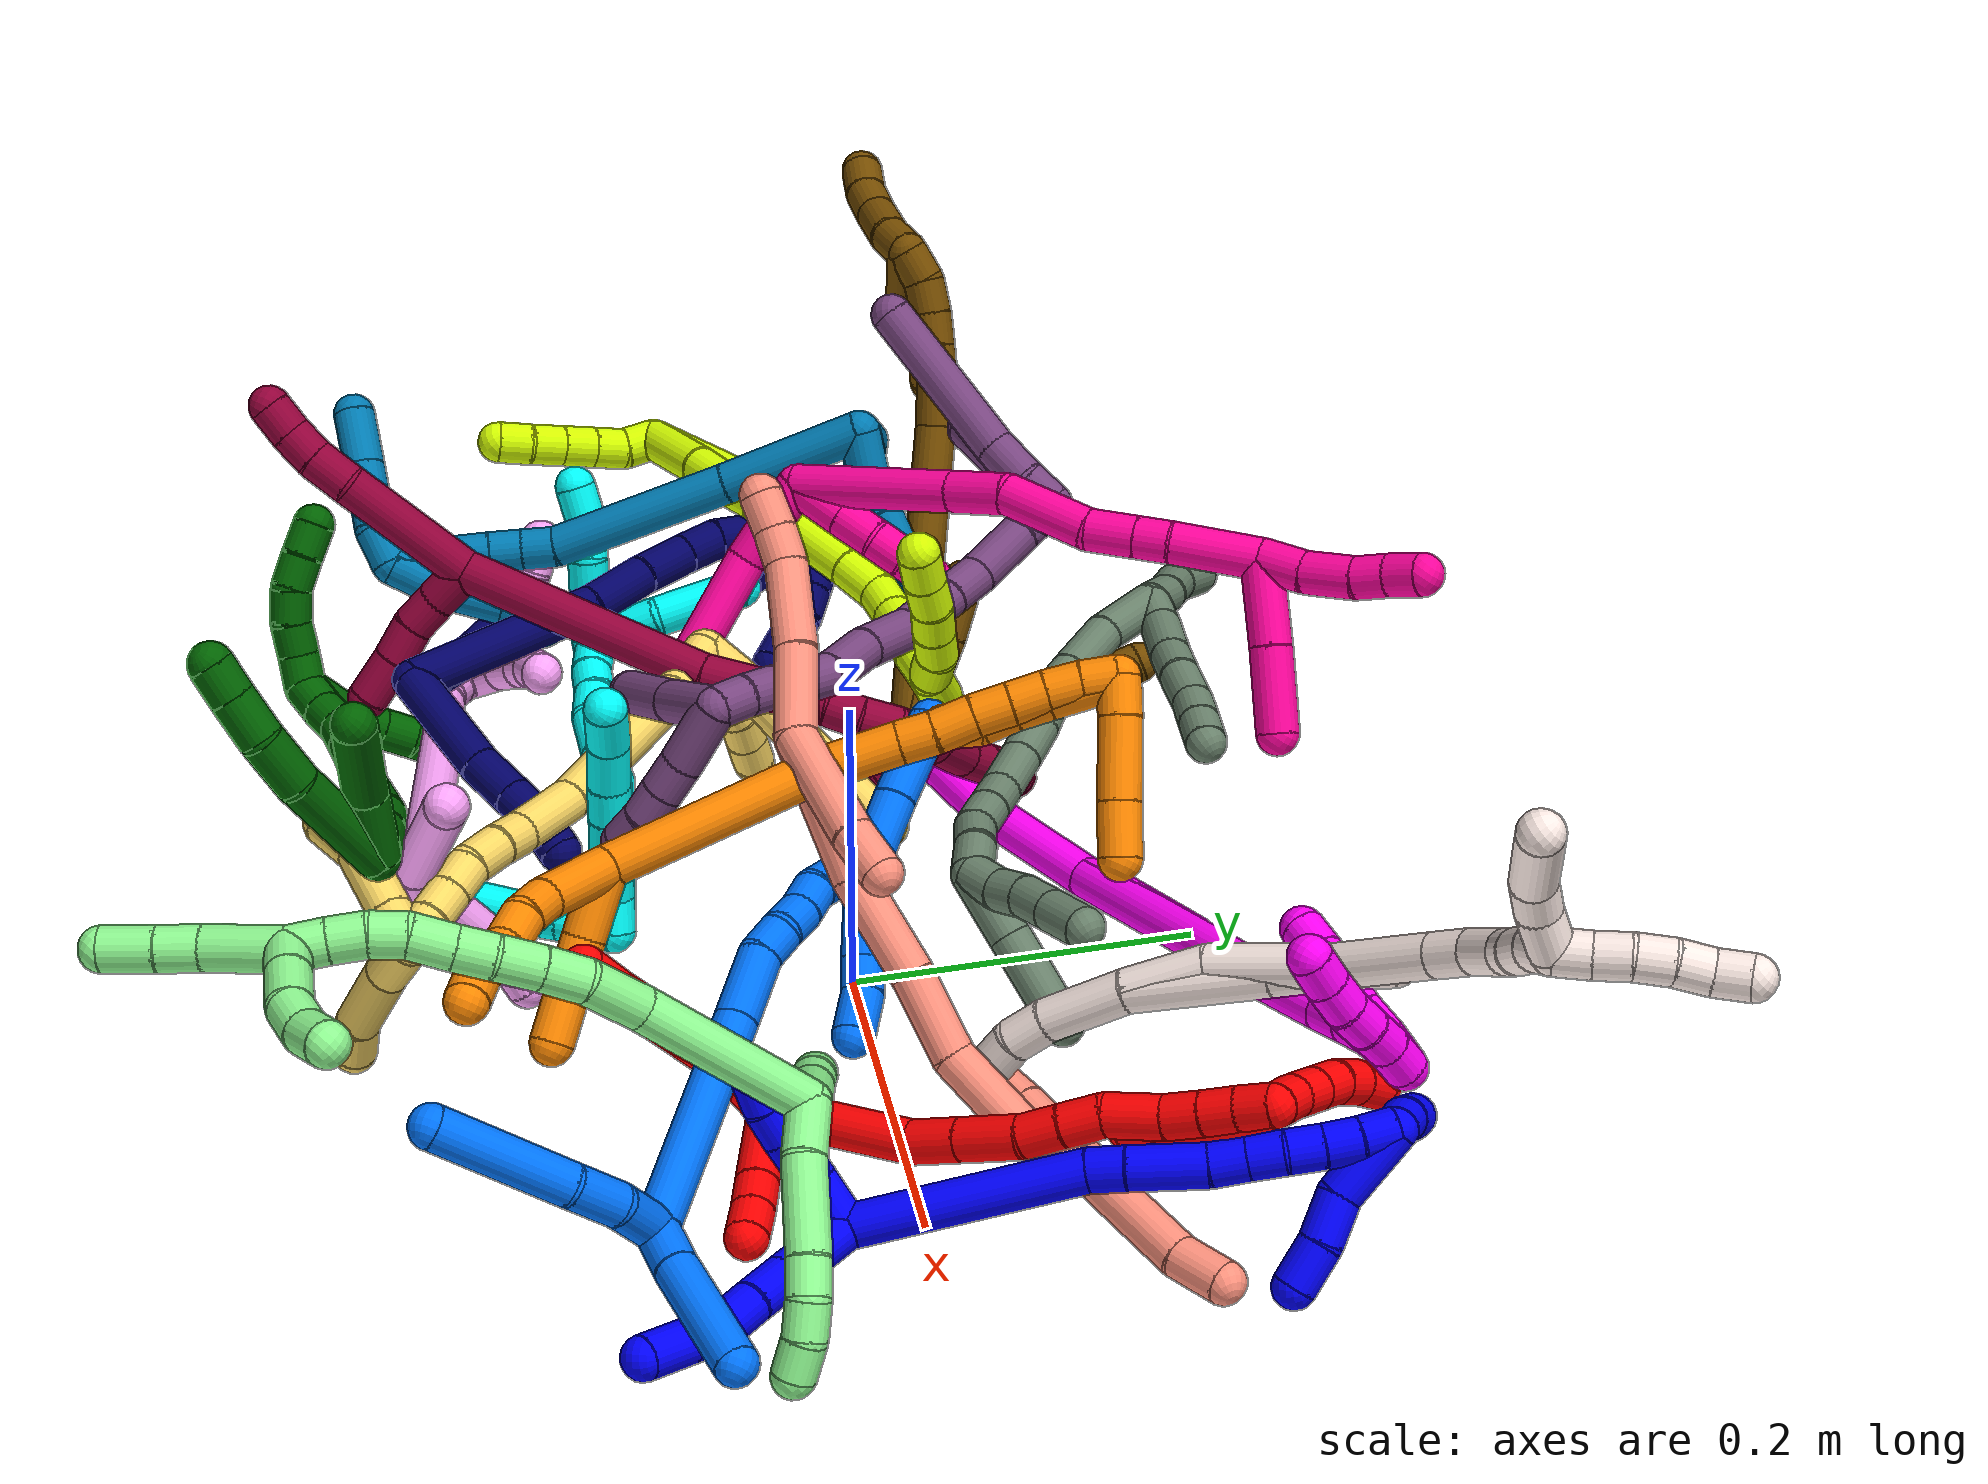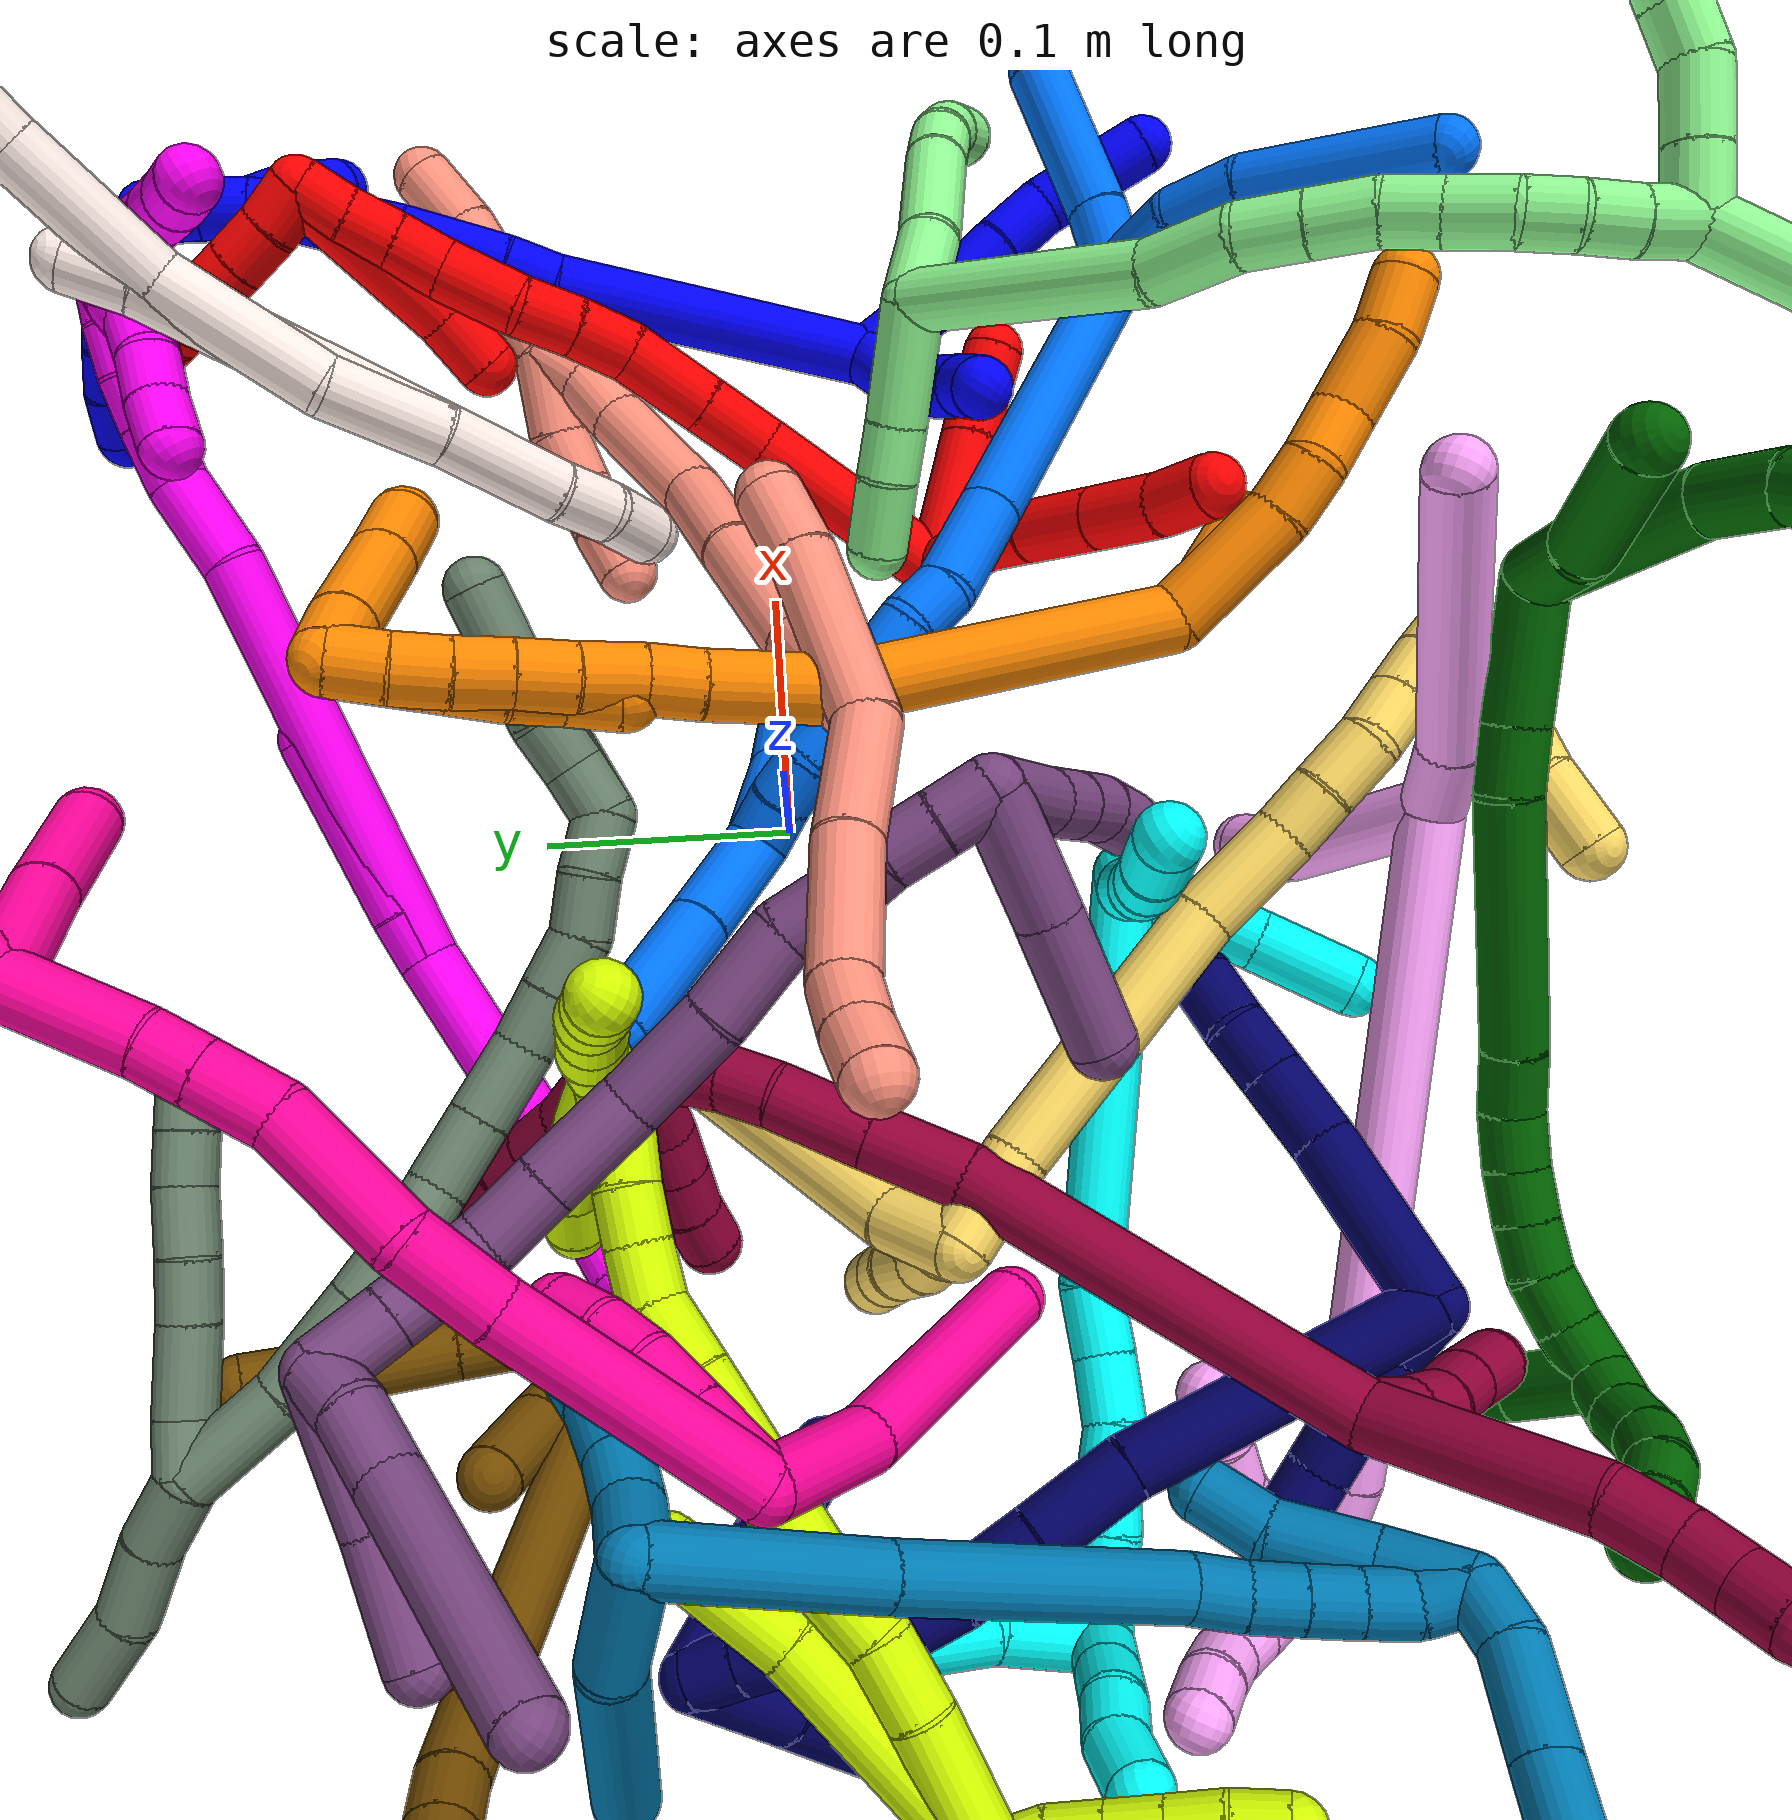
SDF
<sdf version="1.7">
 <world name="default">
  <plugin name="TubeGeneratorPlugin" filename="libtube_generator_plugin.so"/>
  <model name="photoneo_s_sensor">
   <static>1</static>
   <pose>0 0 2 1.57079 1.57079 3.14159</pose>
   <link name="link">
    <inertial><mass>0.1</mass></inertial>
    <sensor name="sensor" type="depth">
     <update_rate>30</update_rate>
     <camera>
      <horizontal_fov>1.22</horizontal_fov>
      <image><width>1920</width><height>1200</height><format>B8G8R8</format></image>
      <clip><near>0.1</near><far>4</far></clip>
      <depth_camera><output>points</output></depth_camera>
     </camera>
     <plugin name="camera_plugin" filename="libgazebo_ros_depth_camera.so">
      <baseline>0.2</baseline>
      <alwaysOn>1</alwaysOn>
      <updateRate>0.0</updateRate>
      <cameraName>camera_ir</cameraName>
      <imageTopicName>/camera/color/image_raw</imageTopicName>
      <cameraInfoTopicName>/camera/color/camera_info</cameraInfoTopicName>
      <depthImageTopicName>/camera/depth/image_raw</depthImageTopicName>
      <depthImageCameraInfoTopicName>/camera/depth/camera_info</depthImageCameraInfoTopicName>
      <pointCloudTopicName>/camera/depth/points</pointCloudTopicName>
      <frameName>fr_optical</frameName>
      <pointCloudCutoff>0.1</pointCloudCutoff>
      <pointCloudCutoffMax>2.0</pointCloudCutoffMax>
      <distortionK1>0</distortionK1>
      <distortionK2>0</distortionK2>
      <distortionK3>0</distortionK3>
      <distortionT1>0</distortionT1>
      <distortionT2>0</distortionT2>
      <CxPrime>0</CxPrime>
      <Cx>0</Cx>
      <Cy>0</Cy>
      <focalLength>0</focalLength>
      <hackBaseline>0</hackBaseline>
     </plugin>
    </sensor>
   </link>
  </model>
  <gravity>0 0 -9.8</gravity>
  <magnetic_field>6e-06 2.3e-05 -4.2e-05</magnetic_field>
  <atmosphere type="adiabatic"/>
  <physics name="default_physics" default="0" type="ode">
   <max_step_size>0.003</max_step_size>
   <real_time_factor>1</real_time_factor>
   <real_time_update_rate>1000</real_time_update_rate>
   <max_contacts>10000</max_contacts>
   <ode>
    <solver>
     <type>quick</type>
     <iters>100</iters>
     <sor>1.3</sor>
     <use_dynamic_moi_rescaling>0</use_dynamic_moi_rescaling>
    </solver>
    <constraints>
     <contact_max_correcting_vel>0</contact_max_correcting_vel>
     <contact_surface_layer>0.001</contact_surface_layer>
     <cfm>0</cfm>
     <erp>0.2</erp>
    </constraints>
   </ode>
  </physics>
  <scene><ambient>0.4 0.4 0.4 1</ambient><background>0.7 0.7 0.7 1</background><shadows>0</shadows></scene>
  <audio><device>default</device></audio>
  <spherical_coordinates>
   <surface_model>EARTH_WGS84</surface_model>
   <latitude_deg>0</latitude_deg>
   <longitude_deg>0</longitude_deg>
   <elevation>0</elevation>
   <heading_deg>0</heading_deg>
  </spherical_coordinates>
  <model name="bin">
   <static>1</static>
   <link name="bottom">
    <collision name="collision-bottom">
     <pose>0 0 -0.01 0 -0 0</pose>
     <geometry><box><size>0.8 0.6 0.02</size></box></geometry>
     <surface>
      <friction><ode><mu>100</mu><mu2>100</mu2></ode></friction>
      <contact><collide_bitmask>65535</collide_bitmask></contact>
     </surface>
    </collision>
   </link>
   <link name="west_wall">
    <collision name="collision-west_wall">
     <pose>-0.41 0 0.1 0 -0 0</pose>
     <geometry><box><size>0.02 0.6 0.2</size></box></geometry>
     <surface>
      <friction><ode><mu>100</mu><mu2>100</mu2></ode></friction>
      <contact><collide_bitmask>65535</collide_bitmask></contact>
     </surface>
    </collision>
   </link>
   <link name="east_wall">
    <collision name="collision-east_wall">
     <pose>0.41 0 0.1 0 -0 0</pose>
     <geometry><box><size>0.02 0.6 0.2</size></box></geometry>
     <surface>
      <friction><ode><mu>100</mu><mu2>100</mu2></ode></friction>
      <contact><collide_bitmask>65535</collide_bitmask></contact>
     </surface>
    </collision>
   </link>
   <link name="south_wall">
    <collision name="collision-south_wall">
     <pose>0 -0.31 0.1 0 -0 0</pose>
     <geometry><box><size>0.8 0.02 0.2</size></box></geometry>
     <surface>
      <friction><ode><mu>100</mu><mu2>100</mu2></ode></friction>
      <contact><collide_bitmask>65535</collide_bitmask></contact>
     </surface>
    </collision>
   </link>
   <link name="north_wall">
    <collision name="collision-north_wall">
     <pose>0 0.31 0.1 0 -0 0</pose>
     <geometry><box><size>0.8 0.02 0.2</size></box></geometry>
     <surface>
      <friction><ode><mu>100</mu><mu2>100</mu2></ode></friction>
      <contact><collide_bitmask>65535</collide_bitmask></contact>
     </surface>
    </collision>
   </link>
  </model>
  <model name="1">
   <static>0</static>
   <link name="1">
    <collision name="collision-cylinder-e_1_2_8">
     <pose>0.003321 -0.022284 -0.009219 1.96307 0.136866 0.204346</pose>
     <geometry><cylinder><radius>0.0125</radius><length>0.048686</length></cylinder></geometry>
     <surface>
      <friction><ode><mu>1.16</mu><mu2>1.16</mu2><slip1>0</slip1><slip2>0</slip2></ode></friction>
      <contact><ode><kp>1e+06</kp><kd>1</kd><max_vel>0</max_vel><min_depth>0.001</min_depth></ode></contact>
     </surface>
    </collision>
    <visual name="visual-cylinder-e_1_2_8">
     <pose>0.003321 -0.022284 -0.009219 1.96307 0.136866 0.204346</pose>
     <geometry><cylinder><radius>0.0125</radius><length>0.048686</length></cylinder></geometry>
     <material><ambient>0 0 1 1</ambient></material>
    </visual>
    <collision name="collision-cylinder-e_2_8_9">
     <pose>0.007488 -0.057507 -0.022175 1.85198 0.06267 0.083312</pose>
     <geometry><cylinder><radius>0.0125</radius><length>0.026989</length></cylinder></geometry>
     <surface>
      <friction><ode><mu>1.16</mu><mu2>1.16</mu2><slip1>0</slip1><slip2>0</slip2></ode></friction>
      <contact><ode><kp>1e+06</kp><kd>1</kd><max_vel>0</max_vel><min_depth>0.001</min_depth></ode></contact>
     </surface>
    </collision>
    <visual name="visual-cylinder-e_2_8_9">
     <pose>0.007488 -0.057507 -0.022175 1.85198 0.06267 0.083312</pose>
     <geometry><cylinder><radius>0.0125</radius><length>0.026989</length></cylinder></geometry>
     <material><ambient>0 0 1 1</ambient></material>
    </visual>
    <collision name="collision-cylinder-e_3_9_10">
     <pose>0.009963 -0.082434 -0.030092 1.90625 0.127661 0.179464</pose>
     <geometry><cylinder><radius>0.0125</radius><length>0.025601</length></cylinder></geometry>
     <surface>
      <friction><ode><mu>1.16</mu><mu2>1.16</mu2><slip1>0</slip1><slip2>0</slip2></ode></friction>
      <contact><ode><kp>1e+06</kp><kd>1</kd><max_vel>0</max_vel><min_depth>0.001</min_depth></ode></contact>
     </surface>
    </collision>
    <visual name="visual-cylinder-e_3_9_10">
     <pose>0.009963 -0.082434 -0.030092 1.90625 0.127661 0.179464</pose>
     <geometry><cylinder><radius>0.0125</radius><length>0.025601</length></cylinder></geometry>
     <material><ambient>0 0 1 1</ambient></material>
    </visual>
    <collision name="collision-cylinder-e_4_10_11">
     <pose>0.010424 -0.103335 -0.03902 2.06032 -0.115226 -0.191573</pose>
     <geometry><cylinder><radius>0.0125</radius><length>0.020332</length></cylinder></geometry>
     <surface>
      <friction><ode><mu>1.16</mu><mu2>1.16</mu2><slip1>0</slip1><slip2>0</slip2></ode></friction>
      <contact><ode><kp>1e+06</kp><kd>1</kd><max_vel>0</max_vel><min_depth>0.001</min_depth></ode></contact>
     </surface>
    </collision>
    <visual name="visual-cylinder-e_4_10_11">
     <pose>0.010424 -0.103335 -0.03902 2.06032 -0.115226 -0.191573</pose>
     <geometry><cylinder><radius>0.0125</radius><length>0.020332</length></cylinder></geometry>
     <material><ambient>0 0 1 1</ambient></material>
    </visual>
    <collision name="collision-cylinder-e_5_11_6">
     <pose>0.007626 -0.124697 -0.050394 2.05987 -0.114974 -0.191059</pose>
     <geometry><cylinder><radius>0.0125</radius><length>0.028392</length></cylinder></geometry>
     <surface>
      <friction><ode><mu>1.16</mu><mu2>1.16</mu2><slip1>0</slip1><slip2>0</slip2></ode></friction>
      <contact><ode><kp>1e+06</kp><kd>1</kd><max_vel>0</max_vel><min_depth>0.001</min_depth></ode></contact>
     </surface>
    </collision>
    <visual name="visual-cylinder-e_5_11_6">
     <pose>0.007626 -0.124697 -0.050394 2.05987 -0.114974 -0.191059</pose>
     <geometry><cylinder><radius>0.0125</radius><length>0.028392</length></cylinder></geometry>
     <material><ambient>0 0 1 1</ambient></material>
    </visual>
    <collision name="collision-cylinder-e_1_2_12">
     <pose>-0.012737 0.002031 -0.007624 -2.88125 -1.01618 2.67979</pose>
     <geometry><cylinder><radius>0.0125</radius><length>0.029965</length></cylinder></geometry>
     <surface>
      <friction><ode><mu>1.16</mu><mu2>1.16</mu2><slip1>0</slip1><slip2>0</slip2></ode></friction>
      <contact><ode><kp>1e+06</kp><kd>1</kd><max_vel>0</max_vel><min_depth>0.001</min_depth></ode></contact>
     </surface>
    </collision>
    <visual name="visual-cylinder-e_1_2_12">
     <pose>-0.012737 0.002031 -0.007624 -2.88125 -1.01618 2.67979</pose>
     <geometry><cylinder><radius>0.0125</radius><length>0.029965</length></cylinder></geometry>
     <material><ambient>0 0 1 1</ambient></material>
    </visual>
    <collision name="collision-cylinder-e_2_12_13">
     <pose>-0.039075 0.002727 -0.021213 2.92137 -1.14842 -2.80307</pose>
     <geometry><cylinder><radius>0.0125</radius><length>0.029824</length></cylinder></geometry>
     <surface>
      <friction><ode><mu>1.16</mu><mu2>1.16</mu2><slip1>0</slip1><slip2>0</slip2></ode></friction>
      <contact><ode><kp>1e+06</kp><kd>1</kd><max_vel>0</max_vel><min_depth>0.001</min_depth></ode></contact>
     </surface>
    </collision>
    <visual name="visual-cylinder-e_2_12_13">
     <pose>-0.039075 0.002727 -0.021213 2.92137 -1.14842 -2.80307</pose>
     <geometry><cylinder><radius>0.0125</radius><length>0.029824</length></cylinder></geometry>
     <material><ambient>0 0 1 1</ambient></material>
    </visual>
    <collision name="collision-cylinder-e_3_13_14">
     <pose>-0.062122 -0.000179 -0.030127 2.65221 -1.2309 -2.46265</pose>
     <geometry><cylinder><radius>0.0125</radius><length>0.020039</length></cylinder></geometry>
     <surface>
      <friction><ode><mu>1.16</mu><mu2>1.16</mu2><slip1>0</slip1><slip2>0</slip2></ode></friction>
      <contact><ode><kp>1e+06</kp><kd>1</kd><max_vel>0</max_vel><min_depth>0.001</min_depth></ode></contact>
     </surface>
    </collision>
    <visual name="visual-cylinder-e_3_13_14">
     <pose>-0.062122 -0.000179 -0.030127 2.65221 -1.2309 -2.46265</pose>
     <geometry><cylinder><radius>0.0125</radius><length>0.020039</length></cylinder></geometry>
     <material><ambient>0 0 1 1</ambient></material>
    </visual>
    <collision name="collision-cylinder-e_4_14_5">
     <pose>-0.081463 -0.001985 -0.03502 3.02087 -1.37535 -2.99471</pose>
     <geometry><cylinder><radius>0.0125</radius><length>0.020173</length></cylinder></geometry>
     <surface>
      <friction><ode><mu>1.16</mu><mu2>1.16</mu2><slip1>0</slip1><slip2>0</slip2></ode></friction>
      <contact><ode><kp>1e+06</kp><kd>1</kd><max_vel>0</max_vel><min_depth>0.001</min_depth></ode></contact>
     </surface>
    </collision>
    <visual name="visual-cylinder-e_4_14_5">
     <pose>-0.081463 -0.001985 -0.03502 3.02087 -1.37535 -2.99471</pose>
     <geometry><cylinder><radius>0.0125</radius><length>0.020173</length></cylinder></geometry>
     <material><ambient>0 0 1 1</ambient></material>
    </visual>
    <collision name="collision-cylinder-e_1_2_15">
     <pose>-0.007327 0.021881 0.063089 -0.333838 -0.109282 0.01843</pose>
     <geometry><cylinder><radius>0.0125</radius><length>0.134353</length></cylinder></geometry>
     <surface>
      <friction><ode><mu>1.16</mu><mu2>1.16</mu2><slip1>0</slip1><slip2>0</slip2></ode></friction>
      <contact><ode><kp>1e+06</kp><kd>1</kd><max_vel>0</max_vel><min_depth>0.001</min_depth></ode></contact>
     </surface>
    </collision>
    <visual name="visual-cylinder-e_1_2_15">
     <pose>-0.007327 0.021881 0.063089 -0.333838 -0.109282 0.01843</pose>
     <geometry><cylinder><radius>0.0125</radius><length>0.134353</length></cylinder></geometry>
     <material><ambient>0 0 1 1</ambient></material>
    </visual>
    <collision name="collision-cylinder-e_2_15_16">
     <pose>-0.01451 0.04567 0.136553 -0.181977 0.01361 -0.001242</pose>
     <geometry><cylinder><radius>0.0125</radius><length>0.021098</length></cylinder></geometry>
     <surface>
      <friction><ode><mu>1.16</mu><mu2>1.16</mu2><slip1>0</slip1><slip2>0</slip2></ode></friction>
      <contact><ode><kp>1e+06</kp><kd>1</kd><max_vel>0</max_vel><min_depth>0.001</min_depth></ode></contact>
     </surface>
    </collision>
    <visual name="visual-cylinder-e_2_15_16">
     <pose>-0.01451 0.04567 0.136553 -0.181977 0.01361 -0.001242</pose>
     <geometry><cylinder><radius>0.0125</radius><length>0.021098</length></cylinder></geometry>
     <material><ambient>0 0 1 1</ambient></material>
    </visual>
    <collision name="collision-cylinder-e_3_16_17">
     <pose>-0.012816 0.053267 0.167988 -0.26378 0.070945 -0.009415</pose>
     <geometry><cylinder><radius>0.0125</radius><length>0.043742</length></cylinder></geometry>
     <surface>
      <friction><ode><mu>1.16</mu><mu2>1.16</mu2><slip1>0</slip1><slip2>0</slip2></ode></friction>
      <contact><ode><kp>1e+06</kp><kd>1</kd><max_vel>0</max_vel><min_depth>0.001</min_depth></ode></contact>
     </surface>
    </collision>
    <visual name="visual-cylinder-e_3_16_17">
     <pose>-0.012816 0.053267 0.167988 -0.26378 0.070945 -0.009415</pose>
     <geometry><cylinder><radius>0.0125</radius><length>0.043742</length></cylinder></geometry>
     <material><ambient>0 0 1 1</ambient></material>
    </visual>
    <collision name="collision-cylinder-e_4_17_18">
     <pose>-0.011803 0.062395 0.198822 -0.338418 -0.051885 0.008866</pose>
     <geometry><cylinder><radius>0.0125</radius><length>0.020748</length></cylinder></geometry>
     <surface>
      <friction><ode><mu>1.16</mu><mu2>1.16</mu2><slip1>0</slip1><slip2>0</slip2></ode></friction>
      <contact><ode><kp>1e+06</kp><kd>1</kd><max_vel>0</max_vel><min_depth>0.001</min_depth></ode></contact>
     </surface>
    </collision>
    <visual name="visual-cylinder-e_4_17_18">
     <pose>-0.011803 0.062395 0.198822 -0.338418 -0.051885 0.008866</pose>
     <geometry><cylinder><radius>0.0125</radius><length>0.020748</length></cylinder></geometry>
     <material><ambient>0 0 1 1</ambient></material>
    </visual>
    <collision name="collision-cylinder-e_5_18_19">
     <pose>-0.01274 0.068892 0.218113 -0.3108 -0.039825 0.00624</pose>
     <geometry><cylinder><radius>0.0125</radius><length>0.02001</length></cylinder></geometry>
     <surface>
      <friction><ode><mu>1.16</mu><mu2>1.16</mu2><slip1>0</slip1><slip2>0</slip2></ode></friction>
      <contact><ode><kp>1e+06</kp><kd>1</kd><max_vel>0</max_vel><min_depth>0.001</min_depth></ode></contact>
     </surface>
    </collision>
    <visual name="visual-cylinder-e_5_18_19">
     <pose>-0.01274 0.068892 0.218113 -0.3108 -0.039825 0.00624</pose>
     <geometry><cylinder><radius>0.0125</radius><length>0.02001</length></cylinder></geometry>
     <material><ambient>0 0 1 1</ambient></material>
    </visual>
    <collision name="collision-cylinder-e_6_19_20">
     <pose>-0.012703 0.076583 0.236493 -0.481781 0.043492 -0.010686</pose>
     <geometry><cylinder><radius>0.0125</radius><length>0.02002</length></cylinder></geometry>
     <surface>
      <friction><ode><mu>1.16</mu><mu2>1.16</mu2><slip1>0</slip1><slip2>0</slip2></ode></friction>
      <contact><ode><kp>1e+06</kp><kd>1</kd><max_vel>0</max_vel><min_depth>0.001</min_depth></ode></contact>
     </surface>
    </collision>
    <visual name="visual-cylinder-e_6_19_20">
     <pose>-0.012703 0.076583 0.236493 -0.481781 0.043492 -0.010686</pose>
     <geometry><cylinder><radius>0.0125</radius><length>0.02002</length></cylinder></geometry>
     <material><ambient>0 0 1 1</ambient></material>
    </visual>
    <collision name="collision-cylinder-e_7_20_21">
     <pose>-0.012087 0.086288 0.253976 -0.531776 0.018073 -0.004922</pose>
     <geometry><cylinder><radius>0.0125</radius><length>0.020005</length></cylinder></geometry>
     <surface>
      <friction><ode><mu>1.16</mu><mu2>1.16</mu2><slip1>0</slip1><slip2>0</slip2></ode></friction>
      <contact><ode><kp>1e+06</kp><kd>1</kd><max_vel>0</max_vel><min_depth>0.001</min_depth></ode></contact>
     </surface>
    </collision>
    <visual name="visual-cylinder-e_7_20_21">
     <pose>-0.012087 0.086288 0.253976 -0.531776 0.018073 -0.004922</pose>
     <geometry><cylinder><radius>0.0125</radius><length>0.020005</length></cylinder></geometry>
     <material><ambient>0 0 1 1</ambient></material>
    </visual>
    <collision name="collision-cylinder-e_8_21_1">
     <pose>-0.012096 0.097262 0.270679 -0.630682 -0.018991 0.006195</pose>
     <geometry><cylinder><radius>0.0125</radius><length>0.020022</length></cylinder></geometry>
     <surface>
      <friction><ode><mu>1.16</mu><mu2>1.16</mu2><slip1>0</slip1><slip2>0</slip2></ode></friction>
      <contact><ode><kp>1e+06</kp><kd>1</kd><max_vel>0</max_vel><min_depth>0.001</min_depth></ode></contact>
     </surface>
    </collision>
    <visual name="visual-cylinder-e_8_21_1">
     <pose>-0.012096 0.097262 0.270679 -0.630682 -0.018991 0.006195</pose>
     <geometry><cylinder><radius>0.0125</radius><length>0.020022</length></cylinder></geometry>
     <material><ambient>0 0 1 1</ambient></material>
    </visual>
    <collision name="collision-cylinder-e_1_1_22">
     <pose>-0.010475 0.112966 0.277966 -1.65198 0.182097 -0.197419</pose>
     <geometry><cylinder><radius>0.0125</radius><length>0.02</length></cylinder></geometry>
     <surface>
      <friction><ode><mu>1.16</mu><mu2>1.16</mu2><slip1>0</slip1><slip2>0</slip2></ode></friction>
      <contact><ode><kp>1e+06</kp><kd>1</kd><max_vel>0</max_vel><min_depth>0.001</min_depth></ode></contact>
     </surface>
    </collision>
    <visual name="visual-cylinder-e_1_1_22">
     <pose>-0.010475 0.112966 0.277966 -1.65198 0.182097 -0.197419</pose>
     <geometry><cylinder><radius>0.0125</radius><length>0.02</length></cylinder></geometry>
     <material><ambient>0 0 1 1</ambient></material>
    </visual>
    <collision name="collision-cylinder-e_2_22_23">
     <pose>-0.004986 0.132037 0.27642 -1.65132 0.376643 -0.407425</pose>
     <geometry><cylinder><radius>0.0125</radius><length>0.02</length></cylinder></geometry>
     <surface>
      <friction><ode><mu>1.16</mu><mu2>1.16</mu2><slip1>0</slip1><slip2>0</slip2></ode></friction>
      <contact><ode><kp>1e+06</kp><kd>1</kd><max_vel>0</max_vel><min_depth>0.001</min_depth></ode></contact>
     </surface>
    </collision>
    <visual name="visual-cylinder-e_2_22_23">
     <pose>-0.004986 0.132037 0.27642 -1.65132 0.376643 -0.407425</pose>
     <geometry><cylinder><radius>0.0125</radius><length>0.02</length></cylinder></geometry>
     <material><ambient>0 0 1 1</ambient></material>
    </visual>
    <collision name="collision-cylinder-e_3_23_24">
     <pose>0.002941 0.149793 0.272522 -1.92623 0.438909 -0.620699</pose>
     <geometry><cylinder><radius>0.0125</radius><length>0.02</length></cylinder></geometry>
     <surface>
      <friction><ode><mu>1.16</mu><mu2>1.16</mu2><slip1>0</slip1><slip2>0</slip2></ode></friction>
      <contact><ode><kp>1e+06</kp><kd>1</kd><max_vel>0</max_vel><min_depth>0.001</min_depth></ode></contact>
     </surface>
    </collision>
    <visual name="visual-cylinder-e_3_23_24">
     <pose>0.002941 0.149793 0.272522 -1.92623 0.438909 -0.620699</pose>
     <geometry><cylinder><radius>0.0125</radius><length>0.02</length></cylinder></geometry>
     <material><ambient>0 0 1 1</ambient></material>
    </visual>
    <collision name="collision-cylinder-e_4_24_25">
     <pose>0.011891 0.166309 0.265708 -1.99881 0.489361 -0.740845</pose>
     <geometry><cylinder><radius>0.0125</radius><length>0.02</length></cylinder></geometry>
     <surface>
      <friction><ode><mu>1.16</mu><mu2>1.16</mu2><slip1>0</slip1><slip2>0</slip2></ode></friction>
      <contact><ode><kp>1e+06</kp><kd>1</kd><max_vel>0</max_vel><min_depth>0.001</min_depth></ode></contact>
     </surface>
    </collision>
    <visual name="visual-cylinder-e_4_24_25">
     <pose>0.011891 0.166309 0.265708 -1.99881 0.489361 -0.740845</pose>
     <geometry><cylinder><radius>0.0125</radius><length>0.02</length></cylinder></geometry>
     <material><ambient>0 0 1 1</ambient></material>
    </visual>
    <collision name="collision-cylinder-e_5_25_4">
     <pose>0.020836 0.181393 0.256367 -2.24853 0.438356 -0.870937</pose>
     <geometry><cylinder><radius>0.0125</radius><length>0.02</length></cylinder></geometry>
     <surface>
      <friction><ode><mu>1.16</mu><mu2>1.16</mu2><slip1>0</slip1><slip2>0</slip2></ode></friction>
      <contact><ode><kp>1e+06</kp><kd>1</kd><max_vel>0</max_vel><min_depth>0.001</min_depth></ode></contact>
     </surface>
    </collision>
    <visual name="visual-cylinder-e_5_25_4">
     <pose>0.020836 0.181393 0.256367 -2.24853 0.438356 -0.870937</pose>
     <geometry><cylinder><radius>0.0125</radius><length>0.02</length></cylinder></geometry>
     <material><ambient>0 0 1 1</ambient></material>
    </visual>
    <collision name="collision-cylinder-e_1_1_26">
     <pose>0.001706 0.091827 0.264605 2.46638 0.657093 1.54148</pose>
     <geometry><cylinder><radius>0.0125</radius><length>0.045816</length></cylinder></geometry>
     <surface>
      <friction><ode><mu>1.16</mu><mu2>1.16</mu2><slip1>0</slip1><slip2>0</slip2></ode></friction>
      <contact><ode><kp>1e+06</kp><kd>1</kd><max_vel>0</max_vel><min_depth>0.001</min_depth></ode></contact>
     </surface>
    </collision>
    <visual name="visual-cylinder-e_1_1_26">
     <pose>0.001706 0.091827 0.264605 2.46638 0.657093 1.54148</pose>
     <geometry><cylinder><radius>0.0125</radius><length>0.045816</length></cylinder></geometry>
     <material><ambient>0 0 1 1</ambient></material>
    </visual>
    <collision name="collision-cylinder-e_2_26_27">
     <pose>0.02609 0.072752 0.246146 2.0781 0.865198 1.33102</pose>
     <geometry><cylinder><radius>0.0125</radius><length>0.027302</length></cylinder></geometry>
     <surface>
      <friction><ode><mu>1.16</mu><mu2>1.16</mu2><slip1>0</slip1><slip2>0</slip2></ode></friction>
      <contact><ode><kp>1e+06</kp><kd>1</kd><max_vel>0</max_vel><min_depth>0.001</min_depth></ode></contact>
     </surface>
    </collision>
    <visual name="visual-cylinder-e_2_26_27">
     <pose>0.02609 0.072752 0.246146 2.0781 0.865198 1.33102</pose>
     <geometry><cylinder><radius>0.0125</radius><length>0.027302</length></cylinder></geometry>
     <material><ambient>0 0 1 1</ambient></material>
    </visual>
    <collision name="collision-cylinder-e_3_27_3">
     <pose>0.046072 0.058376 0.235165 2.35937 0.794435 1.58801</pose>
     <geometry><cylinder><radius>0.0125</radius><length>0.026882</length></cylinder></geometry>
     <surface>
      <friction><ode><mu>1.16</mu><mu2>1.16</mu2><slip1>0</slip1><slip2>0</slip2></ode></friction>
      <contact><ode><kp>1e+06</kp><kd>1</kd><max_vel>0</max_vel><min_depth>0.001</min_depth></ode></contact>
     </surface>
    </collision>
    <visual name="visual-cylinder-e_3_27_3">
     <pose>0.046072 0.058376 0.235165 2.35937 0.794435 1.58801</pose>
     <geometry><cylinder><radius>0.0125</radius><length>0.026882</length></cylinder></geometry>
     <material><ambient>0 0 1 1</ambient></material>
    </visual>
    <collision name="collision-sphere-3">
     <pose>0.055661 0.051738 0.228484 0 -0 0</pose>
     <geometry><sphere><radius>0.0125</radius></sphere></geometry>
     <surface>
      <friction><ode><mu>1.16</mu><mu2>1.16</mu2><slip1>0</slip1><slip2>0</slip2></ode></friction>
      <contact><ode><kp>1e+06</kp><kd>1</kd><max_vel>0</max_vel><min_depth>0.001</min_depth></ode></contact>
     </surface>
    </collision>
    <visual name="visual-sphere-3">
     <pose>0.055661 0.051738 0.228484 0 -0 0</pose>
     <geometry><sphere><radius>0.0125</radius></sphere></geometry>
     <material><ambient>0 0 1 1</ambient></material>
    </visual>
    <collision name="collision-sphere-27">
     <pose>0.036482 0.065014 0.241846 0 -0 0</pose>
     <geometry><sphere><radius>0.0125</radius></sphere></geometry>
     <surface>
      <friction><ode><mu>1.16</mu><mu2>1.16</mu2><slip1>0</slip1><slip2>0</slip2></ode></friction>
      <contact><ode><kp>1e+06</kp><kd>1</kd><max_vel>0</max_vel><min_depth>0.001</min_depth></ode></contact>
     </surface>
    </collision>
    <visual name="visual-sphere-27">
     <pose>0.036482 0.065014 0.241846 0 -0 0</pose>
     <geometry><sphere><radius>0.0125</radius></sphere></geometry>
     <material><ambient>0 0 1 1</ambient></material>
    </visual>
    <collision name="collision-sphere-26">
     <pose>0.015699 0.080489 0.250447 0 -0 0</pose>
     <geometry><sphere><radius>0.0125</radius></sphere></geometry>
     <surface>
      <friction><ode><mu>1.16</mu><mu2>1.16</mu2><slip1>0</slip1><slip2>0</slip2></ode></friction>
      <contact><ode><kp>1e+06</kp><kd>1</kd><max_vel>0</max_vel><min_depth>0.001</min_depth></ode></contact>
     </surface>
    </collision>
    <visual name="visual-sphere-26">
     <pose>0.015699 0.080489 0.250447 0 -0 0</pose>
     <geometry><sphere><radius>0.0125</radius></sphere></geometry>
     <material><ambient>0 0 1 1</ambient></material>
    </visual>
    <collision name="collision-sphere-4">
     <pose>0.025081 0.188446 0.25069 0 -0 0</pose>
     <geometry><sphere><radius>0.0125</radius></sphere></geometry>
     <surface>
      <friction><ode><mu>1.16</mu><mu2>1.16</mu2><slip1>0</slip1><slip2>0</slip2></ode></friction>
      <contact><ode><kp>1e+06</kp><kd>1</kd><max_vel>0</max_vel><min_depth>0.001</min_depth></ode></contact>
     </surface>
    </collision>
    <visual name="visual-sphere-4">
     <pose>0.025081 0.188446 0.25069 0 -0 0</pose>
     <geometry><sphere><radius>0.0125</radius></sphere></geometry>
     <material><ambient>0 0 1 1</ambient></material>
    </visual>
    <collision name="collision-sphere-25">
     <pose>0.016592 0.174339 0.262045 0 -0 0</pose>
     <geometry><sphere><radius>0.0125</radius></sphere></geometry>
     <surface>
      <friction><ode><mu>1.16</mu><mu2>1.16</mu2><slip1>0</slip1><slip2>0</slip2></ode></friction>
      <contact><ode><kp>1e+06</kp><kd>1</kd><max_vel>0</max_vel><min_depth>0.001</min_depth></ode></contact>
     </surface>
    </collision>
    <visual name="visual-sphere-25">
     <pose>0.016592 0.174339 0.262045 0 -0 0</pose>
     <geometry><sphere><radius>0.0125</radius></sphere></geometry>
     <material><ambient>0 0 1 1</ambient></material>
    </visual>
    <collision name="collision-sphere-24">
     <pose>0.007191 0.158279 0.269372 0 -0 0</pose>
     <geometry><sphere><radius>0.0125</radius></sphere></geometry>
     <surface>
      <friction><ode><mu>1.16</mu><mu2>1.16</mu2><slip1>0</slip1><slip2>0</slip2></ode></friction>
      <contact><ode><kp>1e+06</kp><kd>1</kd><max_vel>0</max_vel><min_depth>0.001</min_depth></ode></contact>
     </surface>
    </collision>
    <visual name="visual-sphere-24">
     <pose>0.007191 0.158279 0.269372 0 -0 0</pose>
     <geometry><sphere><radius>0.0125</radius></sphere></geometry>
     <material><ambient>0 0 1 1</ambient></material>
    </visual>
    <collision name="collision-sphere-23">
     <pose>-0.001308 0.141306 0.275672 0 -0 0</pose>
     <geometry><sphere><radius>0.0125</radius></sphere></geometry>
     <surface>
      <friction><ode><mu>1.16</mu><mu2>1.16</mu2><slip1>0</slip1><slip2>0</slip2></ode></friction>
      <contact><ode><kp>1e+06</kp><kd>1</kd><max_vel>0</max_vel><min_depth>0.001</min_depth></ode></contact>
     </surface>
    </collision>
    <visual name="visual-sphere-23">
     <pose>-0.001308 0.141306 0.275672 0 -0 0</pose>
     <geometry><sphere><radius>0.0125</radius></sphere></geometry>
     <material><ambient>0 0 1 1</ambient></material>
    </visual>
    <collision name="collision-sphere-22">
     <pose>-0.008664 0.122769 0.277168 0 -0 0</pose>
     <geometry><sphere><radius>0.0125</radius></sphere></geometry>
     <surface>
      <friction><ode><mu>1.16</mu><mu2>1.16</mu2><slip1>0</slip1><slip2>0</slip2></ode></friction>
      <contact><ode><kp>1e+06</kp><kd>1</kd><max_vel>0</max_vel><min_depth>0.001</min_depth></ode></contact>
     </surface>
    </collision>
    <visual name="visual-sphere-22">
     <pose>-0.008664 0.122769 0.277168 0 -0 0</pose>
     <geometry><sphere><radius>0.0125</radius></sphere></geometry>
     <material><ambient>0 0 1 1</ambient></material>
    </visual>
    <collision name="collision-sphere-1">
     <pose>-0.012286 0.103164 0.278763 0 -0 0</pose>
     <geometry><sphere><radius>0.0125</radius></sphere></geometry>
     <surface>
      <friction><ode><mu>1.16</mu><mu2>1.16</mu2><slip1>0</slip1><slip2>0</slip2></ode></friction>
      <contact><ode><kp>1e+06</kp><kd>1</kd><max_vel>0</max_vel><min_depth>0.001</min_depth></ode></contact>
     </surface>
    </collision>
    <visual name="visual-sphere-1">
     <pose>-0.012286 0.103164 0.278763 0 -0 0</pose>
     <geometry><sphere><radius>0.0125</radius></sphere></geometry>
     <material><ambient>0 0 1 1</ambient></material>
    </visual>
    <collision name="collision-sphere-21">
     <pose>-0.011906 0.091359 0.262596 0 -0 0</pose>
     <geometry><sphere><radius>0.0125</radius></sphere></geometry>
     <surface>
      <friction><ode><mu>1.16</mu><mu2>1.16</mu2><slip1>0</slip1><slip2>0</slip2></ode></friction>
      <contact><ode><kp>1e+06</kp><kd>1</kd><max_vel>0</max_vel><min_depth>0.001</min_depth></ode></contact>
     </surface>
    </collision>
    <visual name="visual-sphere-21">
     <pose>-0.011906 0.091359 0.262596 0 -0 0</pose>
     <geometry><sphere><radius>0.0125</radius></sphere></geometry>
     <material><ambient>0 0 1 1</ambient></material>
    </visual>
    <collision name="collision-sphere-6">
     <pose>0.005998 -0.137146 -0.057019 0 -0 0</pose>
     <geometry><sphere><radius>0.0125</radius></sphere></geometry>
     <surface>
      <friction><ode><mu>1.16</mu><mu2>1.16</mu2><slip1>0</slip1><slip2>0</slip2></ode></friction>
      <contact><ode><kp>1e+06</kp><kd>1</kd><max_vel>0</max_vel><min_depth>0.001</min_depth></ode></contact>
     </surface>
    </collision>
    <visual name="visual-sphere-6">
     <pose>0.005998 -0.137146 -0.057019 0 -0 0</pose>
     <geometry><sphere><radius>0.0125</radius></sphere></geometry>
     <material><ambient>0 0 1 1</ambient></material>
    </visual>
    <collision name="collision-sphere-11">
     <pose>0.009255 -0.112248 -0.043769 0 -0 0</pose>
     <geometry><sphere><radius>0.0125</radius></sphere></geometry>
     <surface>
      <friction><ode><mu>1.16</mu><mu2>1.16</mu2><slip1>0</slip1><slip2>0</slip2></ode></friction>
      <contact><ode><kp>1e+06</kp><kd>1</kd><max_vel>0</max_vel><min_depth>0.001</min_depth></ode></contact>
     </surface>
    </collision>
    <visual name="visual-sphere-11">
     <pose>0.009255 -0.112248 -0.043769 0 -0 0</pose>
     <geometry><sphere><radius>0.0125</radius></sphere></geometry>
     <material><ambient>0 0 1 1</ambient></material>
    </visual>
    <collision name="collision-sphere-10">
     <pose>0.011592 -0.094423 -0.034272 0 -0 0</pose>
     <geometry><sphere><radius>0.0125</radius></sphere></geometry>
     <surface>
      <friction><ode><mu>1.16</mu><mu2>1.16</mu2><slip1>0</slip1><slip2>0</slip2></ode></friction>
      <contact><ode><kp>1e+06</kp><kd>1</kd><max_vel>0</max_vel><min_depth>0.001</min_depth></ode></contact>
     </surface>
    </collision>
    <visual name="visual-sphere-10">
     <pose>0.011592 -0.094423 -0.034272 0 -0 0</pose>
     <geometry><sphere><radius>0.0125</radius></sphere></geometry>
     <material><ambient>0 0 1 1</ambient></material>
    </visual>
    <collision name="collision-sphere-9">
     <pose>0.008333 -0.070445 -0.025913 0 -0 0</pose>
     <geometry><sphere><radius>0.0125</radius></sphere></geometry>
     <surface>
      <friction><ode><mu>1.16</mu><mu2>1.16</mu2><slip1>0</slip1><slip2>0</slip2></ode></friction>
      <contact><ode><kp>1e+06</kp><kd>1</kd><max_vel>0</max_vel><min_depth>0.001</min_depth></ode></contact>
     </surface>
    </collision>
    <visual name="visual-sphere-9">
     <pose>0.008333 -0.070445 -0.025913 0 -0 0</pose>
     <geometry><sphere><radius>0.0125</radius></sphere></geometry>
     <material><ambient>0 0 1 1</ambient></material>
    </visual>
    <collision name="collision-sphere-2">
     <geometry><sphere><radius>0.0125</radius></sphere></geometry>
     <surface>
      <friction><ode><mu>1.16</mu><mu2>1.16</mu2><slip1>0</slip1><slip2>0</slip2></ode></friction>
      <contact><ode><kp>1e+06</kp><kd>1</kd><max_vel>0</max_vel><min_depth>0.001</min_depth></ode></contact>
     </surface>
    </collision>
    <visual name="visual-sphere-2">
     <geometry><sphere><radius>0.0125</radius></sphere></geometry>
     <material><ambient>0 0 1 1</ambient></material>
    </visual>
    <collision name="collision-sphere-19">
     <pose>-0.013138 0.071949 0.227631 0 -0 0</pose>
     <geometry><sphere><radius>0.0125</radius></sphere></geometry>
     <surface>
      <friction><ode><mu>1.16</mu><mu2>1.16</mu2><slip1>0</slip1><slip2>0</slip2></ode></friction>
      <contact><ode><kp>1e+06</kp><kd>1</kd><max_vel>0</max_vel><min_depth>0.001</min_depth></ode></contact>
     </surface>
    </collision>
    <visual name="visual-sphere-19">
     <pose>-0.013138 0.071949 0.227631 0 -0 0</pose>
     <geometry><sphere><radius>0.0125</radius></sphere></geometry>
     <material><ambient>0 0 1 1</ambient></material>
    </visual>
    <collision name="collision-sphere-8">
     <pose>0.006643 -0.044568 -0.018438 0 -0 0</pose>
     <geometry><sphere><radius>0.0125</radius></sphere></geometry>
     <surface>
      <friction><ode><mu>1.16</mu><mu2>1.16</mu2><slip1>0</slip1><slip2>0</slip2></ode></friction>
      <contact><ode><kp>1e+06</kp><kd>1</kd><max_vel>0</max_vel><min_depth>0.001</min_depth></ode></contact>
     </surface>
    </collision>
    <visual name="visual-sphere-8">
     <pose>0.006643 -0.044568 -0.018438 0 -0 0</pose>
     <geometry><sphere><radius>0.0125</radius></sphere></geometry>
     <material><ambient>0 0 1 1</ambient></material>
    </visual>
    <collision name="collision-sphere-12">
     <pose>-0.025473 0.004062 -0.015248 0 -0 0</pose>
     <geometry><sphere><radius>0.0125</radius></sphere></geometry>
     <surface>
      <friction><ode><mu>1.16</mu><mu2>1.16</mu2><slip1>0</slip1><slip2>0</slip2></ode></friction>
      <contact><ode><kp>1e+06</kp><kd>1</kd><max_vel>0</max_vel><min_depth>0.001</min_depth></ode></contact>
     </surface>
    </collision>
    <visual name="visual-sphere-12">
     <pose>-0.025473 0.004062 -0.015248 0 -0 0</pose>
     <geometry><sphere><radius>0.0125</radius></sphere></geometry>
     <material><ambient>0 0 1 1</ambient></material>
    </visual>
    <collision name="collision-sphere-13">
     <pose>-0.052676 0.001391 -0.027179 0 -0 0</pose>
     <geometry><sphere><radius>0.0125</radius></sphere></geometry>
     <surface>
      <friction><ode><mu>1.16</mu><mu2>1.16</mu2><slip1>0</slip1><slip2>0</slip2></ode></friction>
      <contact><ode><kp>1e+06</kp><kd>1</kd><max_vel>0</max_vel><min_depth>0.001</min_depth></ode></contact>
     </surface>
    </collision>
    <visual name="visual-sphere-13">
     <pose>-0.052676 0.001391 -0.027179 0 -0 0</pose>
     <geometry><sphere><radius>0.0125</radius></sphere></geometry>
     <material><ambient>0 0 1 1</ambient></material>
    </visual>
    <collision name="collision-sphere-14">
     <pose>-0.071568 -0.001749 -0.033075 0 -0 0</pose>
     <geometry><sphere><radius>0.0125</radius></sphere></geometry>
     <surface>
      <friction><ode><mu>1.16</mu><mu2>1.16</mu2><slip1>0</slip1><slip2>0</slip2></ode></friction>
      <contact><ode><kp>1e+06</kp><kd>1</kd><max_vel>0</max_vel><min_depth>0.001</min_depth></ode></contact>
     </surface>
    </collision>
    <visual name="visual-sphere-14">
     <pose>-0.071568 -0.001749 -0.033075 0 -0 0</pose>
     <geometry><sphere><radius>0.0125</radius></sphere></geometry>
     <material><ambient>0 0 1 1</ambient></material>
    </visual>
    <collision name="collision-sphere-5">
     <pose>-0.091357 -0.002221 -0.036964 0 -0 0</pose>
     <geometry><sphere><radius>0.0125</radius></sphere></geometry>
     <surface>
      <friction><ode><mu>1.16</mu><mu2>1.16</mu2><slip1>0</slip1><slip2>0</slip2></ode></friction>
      <contact><ode><kp>1e+06</kp><kd>1</kd><max_vel>0</max_vel><min_depth>0.001</min_depth></ode></contact>
     </surface>
    </collision>
    <visual name="visual-sphere-5">
     <pose>-0.091357 -0.002221 -0.036964 0 -0 0</pose>
     <geometry><sphere><radius>0.0125</radius></sphere></geometry>
     <material><ambient>0 0 1 1</ambient></material>
    </visual>
    <collision name="collision-sphere-15">
     <pose>-0.014653 0.043761 0.126179 0 -0 0</pose>
     <geometry><sphere><radius>0.0125</radius></sphere></geometry>
     <surface>
      <friction><ode><mu>1.16</mu><mu2>1.16</mu2><slip1>0</slip1><slip2>0</slip2></ode></friction>
      <contact><ode><kp>1e+06</kp><kd>1</kd><max_vel>0</max_vel><min_depth>0.001</min_depth></ode></contact>
     </surface>
    </collision>
    <visual name="visual-sphere-15">
     <pose>-0.014653 0.043761 0.126179 0 -0 0</pose>
     <geometry><sphere><radius>0.0125</radius></sphere></geometry>
     <material><ambient>0 0 1 1</ambient></material>
    </visual>
    <collision name="collision-sphere-16">
     <pose>-0.014366 0.047579 0.146927 0 -0 0</pose>
     <geometry><sphere><radius>0.0125</radius></sphere></geometry>
     <surface>
      <friction><ode><mu>1.16</mu><mu2>1.16</mu2><slip1>0</slip1><slip2>0</slip2></ode></friction>
      <contact><ode><kp>1e+06</kp><kd>1</kd><max_vel>0</max_vel><min_depth>0.001</min_depth></ode></contact>
     </surface>
    </collision>
    <visual name="visual-sphere-16">
     <pose>-0.014366 0.047579 0.146927 0 -0 0</pose>
     <geometry><sphere><radius>0.0125</radius></sphere></geometry>
     <material><ambient>0 0 1 1</ambient></material>
    </visual>
    <collision name="collision-sphere-17">
     <pose>-0.011265 0.058955 0.189049 0 -0 0</pose>
     <geometry><sphere><radius>0.0125</radius></sphere></geometry>
     <surface>
      <friction><ode><mu>1.16</mu><mu2>1.16</mu2><slip1>0</slip1><slip2>0</slip2></ode></friction>
      <contact><ode><kp>1e+06</kp><kd>1</kd><max_vel>0</max_vel><min_depth>0.001</min_depth></ode></contact>
     </surface>
    </collision>
    <visual name="visual-sphere-17">
     <pose>-0.011265 0.058955 0.189049 0 -0 0</pose>
     <geometry><sphere><radius>0.0125</radius></sphere></geometry>
     <material><ambient>0 0 1 1</ambient></material>
    </visual>
    <collision name="collision-sphere-18">
     <pose>-0.012341 0.065834 0.208594 0 -0 0</pose>
     <geometry><sphere><radius>0.0125</radius></sphere></geometry>
     <surface>
      <friction><ode><mu>1.16</mu><mu2>1.16</mu2><slip1>0</slip1><slip2>0</slip2></ode></friction>
      <contact><ode><kp>1e+06</kp><kd>1</kd><max_vel>0</max_vel><min_depth>0.001</min_depth></ode></contact>
     </surface>
    </collision>
    <visual name="visual-sphere-18">
     <pose>-0.012341 0.065834 0.208594 0 -0 0</pose>
     <geometry><sphere><radius>0.0125</radius></sphere></geometry>
     <material><ambient>0 0 1 1</ambient></material>
    </visual>
    <collision name="collision-sphere-20">
     <pose>-0.012268 0.081217 0.245356 0 -0 0</pose>
     <geometry><sphere><radius>0.0125</radius></sphere></geometry>
     <surface>
      <friction><ode><mu>1.16</mu><mu2>1.16</mu2><slip1>0</slip1><slip2>0</slip2></ode></friction>
      <contact><ode><kp>1e+06</kp><kd>1</kd><max_vel>0</max_vel><min_depth>0.001</min_depth></ode></contact>
     </surface>
    </collision>
    <visual name="visual-sphere-20">
     <pose>-0.012268 0.081217 0.245356 0 -0 0</pose>
     <geometry><sphere><radius>0.0125</radius></sphere></geometry>
     <material><ambient>0 0 1 1</ambient></material>
    </visual>
    <inertial>
     <pose>-0.005392 0.035248 0.117816 0 -0 0</pose>
     <mass>0.75</mass>
     <inertia>
      <ixx>0.000261</ixx>
      <ixy>0</ixy>
      <ixz>0</ixz>
      <iyy>0.000234</iyy>
      <iyz>0</iyz>
      <izz>-2.7e-05</izz>
     </inertia>
    </inertial>
   </link>
   <pose>0.202658 -0.044261 0.01251 -0.735885 1.18404 0.262715</pose>
  </model>
  <model name="2">
   <static>0</static>
   <link name="2">
    <collision name="collision-cylinder-e_1_2_8">
     <pose>-0.002932 -0.001728 -0.017487 3.04307 -0.165318 -2.06804</pose>
     <geometry><cylinder><radius>0.0125</radius><length>0.035631</length></cylinder></geometry>
     <surface>
      <friction><ode><mu>1.16</mu><mu2>1.16</mu2><slip1>0</slip1><slip2>0</slip2></ode></friction>
      <contact><ode><kp>1e+06</kp><kd>1</kd><max_vel>0</max_vel><min_depth>0.001</min_depth></ode></contact>
     </surface>
    </collision>
    <visual name="visual-cylinder-e_1_2_8">
     <pose>-0.002932 -0.001728 -0.017487 3.04307 -0.165318 -2.06804</pose>
     <geometry><cylinder><radius>0.0125</radius><length>0.035631</length></cylinder></geometry>
     <material><ambient>1 0 0 1</ambient></material>
    </visual>
    <collision name="collision-cylinder-e_2_8_9">
     <pose>-0.007886 -0.007983 -0.04658 2.76972 -0.160983 -0.810209</pose>
     <geometry><cylinder><radius>0.0125</radius><length>0.025239</length></cylinder></geometry>
     <surface>
      <friction><ode><mu>1.16</mu><mu2>1.16</mu2><slip1>0</slip1><slip2>0</slip2></ode></friction>
      <contact><ode><kp>1e+06</kp><kd>1</kd><max_vel>0</max_vel><min_depth>0.001</min_depth></ode></contact>
     </surface>
    </collision>
    <visual name="visual-cylinder-e_2_8_9">
     <pose>-0.007886 -0.007983 -0.04658 2.76972 -0.160983 -0.810209</pose>
     <geometry><cylinder><radius>0.0125</radius><length>0.025239</length></cylinder></geometry>
     <material><ambient>1 0 0 1</ambient></material>
    </visual>
    <collision name="collision-cylinder-e_3_9_10">
     <pose>-0.013304 -0.019091 -0.073294 2.73077 -0.203138 -0.909908</pose>
     <geometry><cylinder><radius>0.0125</radius><length>0.033654</length></cylinder></geometry>
     <surface>
      <friction><ode><mu>1.16</mu><mu2>1.16</mu2><slip1>0</slip1><slip2>0</slip2></ode></friction>
      <contact><ode><kp>1e+06</kp><kd>1</kd><max_vel>0</max_vel><min_depth>0.001</min_depth></ode></contact>
     </surface>
    </collision>
    <visual name="visual-cylinder-e_3_9_10">
     <pose>-0.013304 -0.019091 -0.073294 2.73077 -0.203138 -0.909908</pose>
     <geometry><cylinder><radius>0.0125</radius><length>0.033654</length></cylinder></geometry>
     <material><ambient>1 0 0 1</ambient></material>
    </visual>
    <collision name="collision-cylinder-e_4_10_11">
     <pose>-0.020004 -0.031756 -0.102217 2.72673 -0.215596 -0.949891</pose>
     <geometry><cylinder><radius>0.0125</radius><length>0.030902</length></cylinder></geometry>
     <surface>
      <friction><ode><mu>1.16</mu><mu2>1.16</mu2><slip1>0</slip1><slip2>0</slip2></ode></friction>
      <contact><ode><kp>1e+06</kp><kd>1</kd><max_vel>0</max_vel><min_depth>0.001</min_depth></ode></contact>
     </surface>
    </collision>
    <visual name="visual-cylinder-e_4_10_11">
     <pose>-0.020004 -0.031756 -0.102217 2.72673 -0.215596 -0.949891</pose>
     <geometry><cylinder><radius>0.0125</radius><length>0.030902</length></cylinder></geometry>
     <material><ambient>1 0 0 1</ambient></material>
    </visual>
    <collision name="collision-cylinder-e_5_11_6">
     <pose>-0.026097 -0.041088 -0.127547 2.86673 -0.228862 -1.38674</pose>
     <geometry><cylinder><radius>0.0125</radius><length>0.024574</length></cylinder></geometry>
     <surface>
      <friction><ode><mu>1.16</mu><mu2>1.16</mu2><slip1>0</slip1><slip2>0</slip2></ode></friction>
      <contact><ode><kp>1e+06</kp><kd>1</kd><max_vel>0</max_vel><min_depth>0.001</min_depth></ode></contact>
     </surface>
    </collision>
    <visual name="visual-cylinder-e_5_11_6">
     <pose>-0.026097 -0.041088 -0.127547 2.86673 -0.228862 -1.38674</pose>
     <geometry><cylinder><radius>0.0125</radius><length>0.024574</length></cylinder></geometry>
     <material><ambient>1 0 0 1</ambient></material>
    </visual>
    <collision name="collision-cylinder-e_1_2_12">
     <pose>-0.026779 0.012388 -0.002346 -1.75792 -1.13077 1.30718</pose>
     <geometry><cylinder><radius>0.0125</radius><length>0.059196</length></cylinder></geometry>
     <surface>
      <friction><ode><mu>1.16</mu><mu2>1.16</mu2><slip1>0</slip1><slip2>0</slip2></ode></friction>
      <contact><ode><kp>1e+06</kp><kd>1</kd><max_vel>0</max_vel><min_depth>0.001</min_depth></ode></contact>
     </surface>
    </collision>
    <visual name="visual-cylinder-e_1_2_12">
     <pose>-0.026779 0.012388 -0.002346 -1.75792 -1.13077 1.30718</pose>
     <geometry><cylinder><radius>0.0125</radius><length>0.059196</length></cylinder></geometry>
     <material><ambient>1 0 0 1</ambient></material>
    </visual>
    <collision name="collision-cylinder-e_2_12_13">
     <pose>-0.062867 0.029044 -0.005302 -1.71303 -1.13698 1.27005</pose>
     <geometry><cylinder><radius>0.0125</radius><length>0.02052</length></cylinder></geometry>
     <surface>
      <friction><ode><mu>1.16</mu><mu2>1.16</mu2><slip1>0</slip1><slip2>0</slip2></ode></friction>
      <contact><ode><kp>1e+06</kp><kd>1</kd><max_vel>0</max_vel><min_depth>0.001</min_depth></ode></contact>
     </surface>
    </collision>
    <visual name="visual-cylinder-e_2_12_13">
     <pose>-0.062867 0.029044 -0.005302 -1.71303 -1.13698 1.27005</pose>
     <geometry><cylinder><radius>0.0125</radius><length>0.02052</length></cylinder></geometry>
     <material><ambient>1 0 0 1</ambient></material>
    </visual>
    <collision name="collision-cylinder-e_3_13_5">
     <pose>-0.08147 0.03725 -0.006908 -1.81834 -1.15893 1.39774</pose>
     <geometry><cylinder><radius>0.0125</radius><length>0.020284</length></cylinder></geometry>
     <surface>
      <friction><ode><mu>1.16</mu><mu2>1.16</mu2><slip1>0</slip1><slip2>0</slip2></ode></friction>
      <contact><ode><kp>1e+06</kp><kd>1</kd><max_vel>0</max_vel><min_depth>0.001</min_depth></ode></contact>
     </surface>
    </collision>
    <visual name="visual-cylinder-e_3_13_5">
     <pose>-0.08147 0.03725 -0.006908 -1.81834 -1.15893 1.39774</pose>
     <geometry><cylinder><radius>0.0125</radius><length>0.020284</length></cylinder></geometry>
     <material><ambient>1 0 0 1</ambient></material>
    </visual>
    <collision name="collision-cylinder-e_1_2_14">
     <pose>0.002295 0.043692 0.006559 -1.4218 0.051903 -0.044696</pose>
     <geometry><cylinder><radius>0.0125</radius><length>0.088481</length></cylinder></geometry>
     <surface>
      <friction><ode><mu>1.16</mu><mu2>1.16</mu2><slip1>0</slip1><slip2>0</slip2></ode></friction>
      <contact><ode><kp>1e+06</kp><kd>1</kd><max_vel>0</max_vel><min_depth>0.001</min_depth></ode></contact>
     </surface>
    </collision>
    <visual name="visual-cylinder-e_1_2_14">
     <pose>0.002295 0.043692 0.006559 -1.4218 0.051903 -0.044696</pose>
     <geometry><cylinder><radius>0.0125</radius><length>0.088481</length></cylinder></geometry>
     <material><ambient>1 0 0 1</ambient></material>
    </visual>
    <collision name="collision-cylinder-e_2_14_15">
     <pose>0.00735 0.102458 0.012016 -1.64371 0.18057 -0.194158</pose>
     <geometry><cylinder><radius>0.0125</radius><length>0.03073</length></cylinder></geometry>
     <surface>
      <friction><ode><mu>1.16</mu><mu2>1.16</mu2><slip1>0</slip1><slip2>0</slip2></ode></friction>
      <contact><ode><kp>1e+06</kp><kd>1</kd><max_vel>0</max_vel><min_depth>0.001</min_depth></ode></contact>
     </surface>
    </collision>
    <visual name="visual-cylinder-e_2_14_15">
     <pose>0.00735 0.102458 0.012016 -1.64371 0.18057 -0.194158</pose>
     <geometry><cylinder><radius>0.0125</radius><length>0.03073</length></cylinder></geometry>
     <material><ambient>1 0 0 1</ambient></material>
    </visual>
    <collision name="collision-cylinder-e_3_15_16">
     <pose>0.013461 0.135815 0.009602 -1.64251 0.180852 -0.194228</pose>
     <geometry><cylinder><radius>0.0125</radius><length>0.037267</length></cylinder></geometry>
     <surface>
      <friction><ode><mu>1.16</mu><mu2>1.16</mu2><slip1>0</slip1><slip2>0</slip2></ode></friction>
      <contact><ode><kp>1e+06</kp><kd>1</kd><max_vel>0</max_vel><min_depth>0.001</min_depth></ode></contact>
     </surface>
    </collision>
    <visual name="visual-cylinder-e_3_15_16">
     <pose>0.013461 0.135815 0.009602 -1.64251 0.180852 -0.194228</pose>
     <geometry><cylinder><radius>0.0125</radius><length>0.037267</length></cylinder></geometry>
     <material><ambient>1 0 0 1</ambient></material>
    </visual>
    <collision name="collision-cylinder-e_4_16_17">
     <pose>0.021536 0.165184 0.006841 -1.70059 0.399752 -0.453545</pose>
     <geometry><cylinder><radius>0.0125</radius><length>0.024273</length></cylinder></geometry>
     <surface>
      <friction><ode><mu>1.16</mu><mu2>1.16</mu2><slip1>0</slip1><slip2>0</slip2></ode></friction>
      <contact><ode><kp>1e+06</kp><kd>1</kd><max_vel>0</max_vel><min_depth>0.001</min_depth></ode></contact>
     </surface>
    </collision>
    <visual name="visual-cylinder-e_4_16_17">
     <pose>0.021536 0.165184 0.006841 -1.70059 0.399752 -0.453545</pose>
     <geometry><cylinder><radius>0.0125</radius><length>0.024273</length></cylinder></geometry>
     <material><ambient>1 0 0 1</ambient></material>
    </visual>
    <collision name="collision-cylinder-e_5_17_18">
     <pose>0.031479 0.186946 0.004685 -1.6371 0.453884 -0.483858</pose>
     <geometry><cylinder><radius>0.0125</radius><length>0.02381</length></cylinder></geometry>
     <surface>
      <friction><ode><mu>1.16</mu><mu2>1.16</mu2><slip1>0</slip1><slip2>0</slip2></ode></friction>
      <contact><ode><kp>1e+06</kp><kd>1</kd><max_vel>0</max_vel><min_depth>0.001</min_depth></ode></contact>
     </surface>
    </collision>
    <visual name="visual-cylinder-e_5_17_18">
     <pose>0.031479 0.186946 0.004685 -1.6371 0.453884 -0.483858</pose>
     <geometry><cylinder><radius>0.0125</radius><length>0.02381</length></cylinder></geometry>
     <material><ambient>1 0 0 1</ambient></material>
    </visual>
    <collision name="collision-cylinder-e_6_18_19">
     <pose>0.04083 0.213397 0.006187 -1.43158 0.253767 -0.220977</pose>
     <geometry><cylinder><radius>0.0125</radius><length>0.032911</length></cylinder></geometry>
     <surface>
      <friction><ode><mu>1.16</mu><mu2>1.16</mu2><slip1>0</slip1><slip2>0</slip2></ode></friction>
      <contact><ode><kp>1e+06</kp><kd>1</kd><max_vel>0</max_vel><min_depth>0.001</min_depth></ode></contact>
     </surface>
    </collision>
    <visual name="visual-cylinder-e_6_18_19">
     <pose>0.04083 0.213397 0.006187 -1.43158 0.253767 -0.220977</pose>
     <geometry><cylinder><radius>0.0125</radius><length>0.032911</length></cylinder></geometry>
     <material><ambient>1 0 0 1</ambient></material>
    </visual>
    <collision name="collision-cylinder-e_7_19_20">
     <pose>0.047949 0.239617 0.008049 -1.6041 0.278363 -0.287665</pose>
     <geometry><cylinder><radius>0.0125</radius><length>0.02174</length></cylinder></geometry>
     <surface>
      <friction><ode><mu>1.16</mu><mu2>1.16</mu2><slip1>0</slip1><slip2>0</slip2></ode></friction>
      <contact><ode><kp>1e+06</kp><kd>1</kd><max_vel>0</max_vel><min_depth>0.001</min_depth></ode></contact>
     </surface>
    </collision>
    <visual name="visual-cylinder-e_7_19_20">
     <pose>0.047949 0.239617 0.008049 -1.6041 0.278363 -0.287665</pose>
     <geometry><cylinder><radius>0.0125</radius><length>0.02174</length></cylinder></geometry>
     <material><ambient>1 0 0 1</ambient></material>
    </visual>
    <collision name="collision-cylinder-e_8_20_21">
     <pose>0.054082 0.259819 0.007346 -1.60712 0.311757 -0.323098</pose>
     <geometry><cylinder><radius>0.0125</radius><length>0.020515</length></cylinder></geometry>
     <surface>
      <friction><ode><mu>1.16</mu><mu2>1.16</mu2><slip1>0</slip1><slip2>0</slip2></ode></friction>
      <contact><ode><kp>1e+06</kp><kd>1</kd><max_vel>0</max_vel><min_depth>0.001</min_depth></ode></contact>
     </surface>
    </collision>
    <visual name="visual-cylinder-e_8_20_21">
     <pose>0.054082 0.259819 0.007346 -1.60712 0.311757 -0.323098</pose>
     <geometry><cylinder><radius>0.0125</radius><length>0.020515</length></cylinder></geometry>
     <material><ambient>1 0 0 1</ambient></material>
    </visual>
    <collision name="collision-cylinder-e_9_21_1">
     <pose>0.059456 0.279435 0.006233 -1.64765 0.221624 -0.239184</pose>
     <geometry><cylinder><radius>0.0125</radius><length>0.020272</length></cylinder></geometry>
     <surface>
      <friction><ode><mu>1.16</mu><mu2>1.16</mu2><slip1>0</slip1><slip2>0</slip2></ode></friction>
      <contact><ode><kp>1e+06</kp><kd>1</kd><max_vel>0</max_vel><min_depth>0.001</min_depth></ode></contact>
     </surface>
    </collision>
    <visual name="visual-cylinder-e_9_21_1">
     <pose>0.059456 0.279435 0.006233 -1.64765 0.221624 -0.239184</pose>
     <geometry><cylinder><radius>0.0125</radius><length>0.020272</length></cylinder></geometry>
     <material><ambient>1 0 0 1</ambient></material>
    </visual>
    <collision name="collision-cylinder-e_1_1_22">
     <pose>0.06987 0.288856 0.011201 0.076223 0.958891 0.039643</pose>
     <geometry><cylinder><radius>0.0125</radius><length>0.02</length></cylinder></geometry>
     <surface>
      <friction><ode><mu>1.16</mu><mu2>1.16</mu2><slip1>0</slip1><slip2>0</slip2></ode></friction>
      <contact><ode><kp>1e+06</kp><kd>1</kd><max_vel>0</max_vel><min_depth>0.001</min_depth></ode></contact>
     </surface>
    </collision>
    <visual name="visual-cylinder-e_1_1_22">
     <pose>0.06987 0.288856 0.011201 0.076223 0.958891 0.039643</pose>
     <geometry><cylinder><radius>0.0125</radius><length>0.02</length></cylinder></geometry>
     <material><ambient>1 0 0 1</ambient></material>
    </visual>
    <collision name="collision-cylinder-e_2_22_23">
     <pose>0.08608 0.289253 0.022837 -0.140347 0.931407 -0.070621</pose>
     <geometry><cylinder><radius>0.0125</radius><length>0.02</length></cylinder></geometry>
     <surface>
      <friction><ode><mu>1.16</mu><mu2>1.16</mu2><slip1>0</slip1><slip2>0</slip2></ode></friction>
      <contact><ode><kp>1e+06</kp><kd>1</kd><max_vel>0</max_vel><min_depth>0.001</min_depth></ode></contact>
     </surface>
    </collision>
    <visual name="visual-cylinder-e_2_22_23">
     <pose>0.08608 0.289253 0.022837 -0.140347 0.931407 -0.070621</pose>
     <geometry><cylinder><radius>0.0125</radius><length>0.02</length></cylinder></geometry>
     <material><ambient>1 0 0 1</ambient></material>
    </visual>
    <collision name="collision-cylinder-e_3_23_24">
     <pose>0.102158 0.290988 0.034604 -0.152338 0.936344 -0.077143</pose>
     <geometry><cylinder><radius>0.0125</radius><length>0.02</length></cylinder></geometry>
     <surface>
      <friction><ode><mu>1.16</mu><mu2>1.16</mu2><slip1>0</slip1><slip2>0</slip2></ode></friction>
      <contact><ode><kp>1e+06</kp><kd>1</kd><max_vel>0</max_vel><min_depth>0.001</min_depth></ode></contact>
     </surface>
    </collision>
    <visual name="visual-cylinder-e_3_23_24">
     <pose>0.102158 0.290988 0.034604 -0.152338 0.936344 -0.077143</pose>
     <geometry><cylinder><radius>0.0125</radius><length>0.02</length></cylinder></geometry>
     <material><ambient>1 0 0 1</ambient></material>
    </visual>
    <collision name="collision-cylinder-e_4_24_25">
     <pose>0.11694 0.292948 0.047785 -0.143888 0.737977 -0.055723</pose>
     <geometry><cylinder><radius>0.0125</radius><length>0.02</length></cylinder></geometry>
     <surface>
      <friction><ode><mu>1.16</mu><mu2>1.16</mu2><slip1>0</slip1><slip2>0</slip2></ode></friction>
      <contact><ode><kp>1e+06</kp><kd>1</kd><max_vel>0</max_vel><min_depth>0.001</min_depth></ode></contact>
     </surface>
    </collision>
    <visual name="visual-cylinder-e_4_24_25">
     <pose>0.11694 0.292948 0.047785 -0.143888 0.737977 -0.055723</pose>
     <geometry><cylinder><radius>0.0125</radius><length>0.02</length></cylinder></geometry>
     <material><ambient>1 0 0 1</ambient></material>
    </visual>
    <collision name="collision-cylinder-e_5_25_4">
     <pose>0.129326 0.29584 0.063146 -0.223939 0.601408 -0.069709</pose>
     <geometry><cylinder><radius>0.0125</radius><length>0.02</length></cylinder></geometry>
     <surface>
      <friction><ode><mu>1.16</mu><mu2>1.16</mu2><slip1>0</slip1><slip2>0</slip2></ode></friction>
      <contact><ode><kp>1e+06</kp><kd>1</kd><max_vel>0</max_vel><min_depth>0.001</min_depth></ode></contact>
     </surface>
    </collision>
    <visual name="visual-cylinder-e_5_25_4">
     <pose>0.129326 0.29584 0.063146 -0.223939 0.601408 -0.069709</pose>
     <geometry><cylinder><radius>0.0125</radius><length>0.02</length></cylinder></geometry>
     <material><ambient>1 0 0 1</ambient></material>
    </visual>
    <collision name="collision-cylinder-e_1_1_26">
     <pose>0.056534 0.253986 0.016394 1.27083 -0.138467 -0.102186</pose>
     <geometry><cylinder><radius>0.0125</radius><length>0.074631</length></cylinder></geometry>
     <surface>
      <friction><ode><mu>1.16</mu><mu2>1.16</mu2><slip1>0</slip1><slip2>0</slip2></ode></friction>
      <contact><ode><kp>1e+06</kp><kd>1</kd><max_vel>0</max_vel><min_depth>0.001</min_depth></ode></contact>
     </surface>
    </collision>
    <visual name="visual-cylinder-e_1_1_26">
     <pose>0.056534 0.253986 0.016394 1.27083 -0.138467 -0.102186</pose>
     <geometry><cylinder><radius>0.0125</radius><length>0.074631</length></cylinder></geometry>
     <material><ambient>1 0 0 1</ambient></material>
    </visual>
    <collision name="collision-cylinder-e_2_26_3">
     <pose>0.051943 0.206258 0.029832 1.3708 0.044152 0.036102</pose>
     <geometry><cylinder><radius>0.0125</radius><length>0.025369</length></cylinder></geometry>
     <surface>
      <friction><ode><mu>1.16</mu><mu2>1.16</mu2><slip1>0</slip1><slip2>0</slip2></ode></friction>
      <contact><ode><kp>1e+06</kp><kd>1</kd><max_vel>0</max_vel><min_depth>0.001</min_depth></ode></contact>
     </surface>
    </collision>
    <visual name="visual-cylinder-e_2_26_3">
     <pose>0.051943 0.206258 0.029832 1.3708 0.044152 0.036102</pose>
     <geometry><cylinder><radius>0.0125</radius><length>0.025369</length></cylinder></geometry>
     <material><ambient>1 0 0 1</ambient></material>
    </visual>
    <collision name="collision-sphere-3">
     <pose>0.052503 0.193838 0.03235 0 -0 0</pose>
     <geometry><sphere><radius>0.0125</radius></sphere></geometry>
     <surface>
      <friction><ode><mu>1.16</mu><mu2>1.16</mu2><slip1>0</slip1><slip2>0</slip2></ode></friction>
      <contact><ode><kp>1e+06</kp><kd>1</kd><max_vel>0</max_vel><min_depth>0.001</min_depth></ode></contact>
     </surface>
    </collision>
    <visual name="visual-sphere-3">
     <pose>0.052503 0.193838 0.03235 0 -0 0</pose>
     <geometry><sphere><radius>0.0125</radius></sphere></geometry>
     <material><ambient>1 0 0 1</ambient></material>
    </visual>
    <collision name="collision-sphere-26">
     <pose>0.051383 0.218678 0.027315 0 -0 0</pose>
     <geometry><sphere><radius>0.0125</radius></sphere></geometry>
     <surface>
      <friction><ode><mu>1.16</mu><mu2>1.16</mu2><slip1>0</slip1><slip2>0</slip2></ode></friction>
      <contact><ode><kp>1e+06</kp><kd>1</kd><max_vel>0</max_vel><min_depth>0.001</min_depth></ode></contact>
     </surface>
    </collision>
    <visual name="visual-sphere-26">
     <pose>0.051383 0.218678 0.027315 0 -0 0</pose>
     <geometry><sphere><radius>0.0125</radius></sphere></geometry>
     <material><ambient>1 0 0 1</ambient></material>
    </visual>
    <collision name="collision-sphere-4">
     <pose>0.134984 0.297671 0.071186 0 -0 0</pose>
     <geometry><sphere><radius>0.0125</radius></sphere></geometry>
     <surface>
      <friction><ode><mu>1.16</mu><mu2>1.16</mu2><slip1>0</slip1><slip2>0</slip2></ode></friction>
      <contact><ode><kp>1e+06</kp><kd>1</kd><max_vel>0</max_vel><min_depth>0.001</min_depth></ode></contact>
     </surface>
    </collision>
    <visual name="visual-sphere-4">
     <pose>0.134984 0.297671 0.071186 0 -0 0</pose>
     <geometry><sphere><radius>0.0125</radius></sphere></geometry>
     <material><ambient>1 0 0 1</ambient></material>
    </visual>
    <collision name="collision-sphere-25">
     <pose>0.123668 0.294009 0.055107 0 -0 0</pose>
     <geometry><sphere><radius>0.0125</radius></sphere></geometry>
     <surface>
      <friction><ode><mu>1.16</mu><mu2>1.16</mu2><slip1>0</slip1><slip2>0</slip2></ode></friction>
      <contact><ode><kp>1e+06</kp><kd>1</kd><max_vel>0</max_vel><min_depth>0.001</min_depth></ode></contact>
     </surface>
    </collision>
    <visual name="visual-sphere-25">
     <pose>0.123668 0.294009 0.055107 0 -0 0</pose>
     <geometry><sphere><radius>0.0125</radius></sphere></geometry>
     <material><ambient>1 0 0 1</ambient></material>
    </visual>
    <collision name="collision-sphere-24">
     <pose>0.110212 0.291887 0.040463 0 -0 0</pose>
     <geometry><sphere><radius>0.0125</radius></sphere></geometry>
     <surface>
      <friction><ode><mu>1.16</mu><mu2>1.16</mu2><slip1>0</slip1><slip2>0</slip2></ode></friction>
      <contact><ode><kp>1e+06</kp><kd>1</kd><max_vel>0</max_vel><min_depth>0.001</min_depth></ode></contact>
     </surface>
    </collision>
    <visual name="visual-sphere-24">
     <pose>0.110212 0.291887 0.040463 0 -0 0</pose>
     <geometry><sphere><radius>0.0125</radius></sphere></geometry>
     <material><ambient>1 0 0 1</ambient></material>
    </visual>
    <collision name="collision-sphere-23">
     <pose>0.094104 0.290088 0.028745 0 -0 0</pose>
     <geometry><sphere><radius>0.0125</radius></sphere></geometry>
     <surface>
      <friction><ode><mu>1.16</mu><mu2>1.16</mu2><slip1>0</slip1><slip2>0</slip2></ode></friction>
      <contact><ode><kp>1e+06</kp><kd>1</kd><max_vel>0</max_vel><min_depth>0.001</min_depth></ode></contact>
     </surface>
    </collision>
    <visual name="visual-sphere-23">
     <pose>0.094104 0.290088 0.028745 0 -0 0</pose>
     <geometry><sphere><radius>0.0125</radius></sphere></geometry>
     <material><ambient>1 0 0 1</ambient></material>
    </visual>
    <collision name="collision-sphere-22">
     <pose>0.078055 0.288419 0.016929 0 -0 0</pose>
     <geometry><sphere><radius>0.0125</radius></sphere></geometry>
     <surface>
      <friction><ode><mu>1.16</mu><mu2>1.16</mu2><slip1>0</slip1><slip2>0</slip2></ode></friction>
      <contact><ode><kp>1e+06</kp><kd>1</kd><max_vel>0</max_vel><min_depth>0.001</min_depth></ode></contact>
     </surface>
    </collision>
    <visual name="visual-sphere-22">
     <pose>0.078055 0.288419 0.016929 0 -0 0</pose>
     <geometry><sphere><radius>0.0125</radius></sphere></geometry>
     <material><ambient>1 0 0 1</ambient></material>
    </visual>
    <collision name="collision-sphere-1">
     <pose>0.061684 0.289294 0.005473 0 -0 0</pose>
     <geometry><sphere><radius>0.0125</radius></sphere></geometry>
     <surface>
      <friction><ode><mu>1.16</mu><mu2>1.16</mu2><slip1>0</slip1><slip2>0</slip2></ode></friction>
      <contact><ode><kp>1e+06</kp><kd>1</kd><max_vel>0</max_vel><min_depth>0.001</min_depth></ode></contact>
     </surface>
    </collision>
    <visual name="visual-sphere-1">
     <pose>0.061684 0.289294 0.005473 0 -0 0</pose>
     <geometry><sphere><radius>0.0125</radius></sphere></geometry>
     <material><ambient>1 0 0 1</ambient></material>
    </visual>
    <collision name="collision-sphere-21">
     <pose>0.057228 0.269576 0.006992 0 -0 0</pose>
     <geometry><sphere><radius>0.0125</radius></sphere></geometry>
     <surface>
      <friction><ode><mu>1.16</mu><mu2>1.16</mu2><slip1>0</slip1><slip2>0</slip2></ode></friction>
      <contact><ode><kp>1e+06</kp><kd>1</kd><max_vel>0</max_vel><min_depth>0.001</min_depth></ode></contact>
     </surface>
    </collision>
    <visual name="visual-sphere-21">
     <pose>0.057228 0.269576 0.006992 0 -0 0</pose>
     <geometry><sphere><radius>0.0125</radius></sphere></geometry>
     <material><ambient>1 0 0 1</ambient></material>
    </visual>
    <collision name="collision-sphere-6">
     <pose>-0.028885 -0.044336 -0.139065 0 -0 0</pose>
     <geometry><sphere><radius>0.0125</radius></sphere></geometry>
     <surface>
      <friction><ode><mu>1.16</mu><mu2>1.16</mu2><slip1>0</slip1><slip2>0</slip2></ode></friction>
      <contact><ode><kp>1e+06</kp><kd>1</kd><max_vel>0</max_vel><min_depth>0.001</min_depth></ode></contact>
     </surface>
    </collision>
    <visual name="visual-sphere-6">
     <pose>-0.028885 -0.044336 -0.139065 0 -0 0</pose>
     <geometry><sphere><radius>0.0125</radius></sphere></geometry>
     <material><ambient>1 0 0 1</ambient></material>
    </visual>
    <collision name="collision-sphere-11">
     <pose>-0.023309 -0.03784 -0.11603 0 -0 0</pose>
     <geometry><sphere><radius>0.0125</radius></sphere></geometry>
     <surface>
      <friction><ode><mu>1.16</mu><mu2>1.16</mu2><slip1>0</slip1><slip2>0</slip2></ode></friction>
      <contact><ode><kp>1e+06</kp><kd>1</kd><max_vel>0</max_vel><min_depth>0.001</min_depth></ode></contact>
     </surface>
    </collision>
    <visual name="visual-sphere-11">
     <pose>-0.023309 -0.03784 -0.11603 0 -0 0</pose>
     <geometry><sphere><radius>0.0125</radius></sphere></geometry>
     <material><ambient>1 0 0 1</ambient></material>
    </visual>
    <collision name="collision-sphere-10">
     <pose>-0.016699 -0.025673 -0.088404 0 -0 0</pose>
     <geometry><sphere><radius>0.0125</radius></sphere></geometry>
     <surface>
      <friction><ode><mu>1.16</mu><mu2>1.16</mu2><slip1>0</slip1><slip2>0</slip2></ode></friction>
      <contact><ode><kp>1e+06</kp><kd>1</kd><max_vel>0</max_vel><min_depth>0.001</min_depth></ode></contact>
     </surface>
    </collision>
    <visual name="visual-sphere-10">
     <pose>-0.016699 -0.025673 -0.088404 0 -0 0</pose>
     <geometry><sphere><radius>0.0125</radius></sphere></geometry>
     <material><ambient>1 0 0 1</ambient></material>
    </visual>
    <collision name="collision-sphere-9">
     <pose>-0.009909 -0.012509 -0.058185 0 -0 0</pose>
     <geometry><sphere><radius>0.0125</radius></sphere></geometry>
     <surface>
      <friction><ode><mu>1.16</mu><mu2>1.16</mu2><slip1>0</slip1><slip2>0</slip2></ode></friction>
      <contact><ode><kp>1e+06</kp><kd>1</kd><max_vel>0</max_vel><min_depth>0.001</min_depth></ode></contact>
     </surface>
    </collision>
    <visual name="visual-sphere-9">
     <pose>-0.009909 -0.012509 -0.058185 0 -0 0</pose>
     <geometry><sphere><radius>0.0125</radius></sphere></geometry>
     <material><ambient>1 0 0 1</ambient></material>
    </visual>
    <collision name="collision-sphere-2">
     <geometry><sphere><radius>0.0125</radius></sphere></geometry>
     <surface>
      <friction><ode><mu>1.16</mu><mu2>1.16</mu2><slip1>0</slip1><slip2>0</slip2></ode></friction>
      <contact><ode><kp>1e+06</kp><kd>1</kd><max_vel>0</max_vel><min_depth>0.001</min_depth></ode></contact>
     </surface>
    </collision>
    <visual name="visual-sphere-2">
     <geometry><sphere><radius>0.0125</radius></sphere></geometry>
     <material><ambient>1 0 0 1</ambient></material>
    </visual>
    <collision name="collision-sphere-19">
     <pose>0.044962 0.229171 0.008397 0 -0 0</pose>
     <geometry><sphere><radius>0.0125</radius></sphere></geometry>
     <surface>
      <friction><ode><mu>1.16</mu><mu2>1.16</mu2><slip1>0</slip1><slip2>0</slip2></ode></friction>
      <contact><ode><kp>1e+06</kp><kd>1</kd><max_vel>0</max_vel><min_depth>0.001</min_depth></ode></contact>
     </surface>
    </collision>
    <visual name="visual-sphere-19">
     <pose>0.044962 0.229171 0.008397 0 -0 0</pose>
     <geometry><sphere><radius>0.0125</radius></sphere></geometry>
     <material><ambient>1 0 0 1</ambient></material>
    </visual>
    <collision name="collision-sphere-8">
     <pose>-0.005864 -0.003457 -0.034975 0 -0 0</pose>
     <geometry><sphere><radius>0.0125</radius></sphere></geometry>
     <surface>
      <friction><ode><mu>1.16</mu><mu2>1.16</mu2><slip1>0</slip1><slip2>0</slip2></ode></friction>
      <contact><ode><kp>1e+06</kp><kd>1</kd><max_vel>0</max_vel><min_depth>0.001</min_depth></ode></contact>
     </surface>
    </collision>
    <visual name="visual-sphere-8">
     <pose>-0.005864 -0.003457 -0.034975 0 -0 0</pose>
     <geometry><sphere><radius>0.0125</radius></sphere></geometry>
     <material><ambient>1 0 0 1</ambient></material>
    </visual>
    <collision name="collision-sphere-12">
     <pose>-0.053557 0.024775 -0.004691 0 -0 0</pose>
     <geometry><sphere><radius>0.0125</radius></sphere></geometry>
     <surface>
      <friction><ode><mu>1.16</mu><mu2>1.16</mu2><slip1>0</slip1><slip2>0</slip2></ode></friction>
      <contact><ode><kp>1e+06</kp><kd>1</kd><max_vel>0</max_vel><min_depth>0.001</min_depth></ode></contact>
     </surface>
    </collision>
    <visual name="visual-sphere-12">
     <pose>-0.053557 0.024775 -0.004691 0 -0 0</pose>
     <geometry><sphere><radius>0.0125</radius></sphere></geometry>
     <material><ambient>1 0 0 1</ambient></material>
    </visual>
    <collision name="collision-sphere-13">
     <pose>-0.072176 0.033313 -0.005914 0 -0 0</pose>
     <geometry><sphere><radius>0.0125</radius></sphere></geometry>
     <surface>
      <friction><ode><mu>1.16</mu><mu2>1.16</mu2><slip1>0</slip1><slip2>0</slip2></ode></friction>
      <contact><ode><kp>1e+06</kp><kd>1</kd><max_vel>0</max_vel><min_depth>0.001</min_depth></ode></contact>
     </surface>
    </collision>
    <visual name="visual-sphere-13">
     <pose>-0.072176 0.033313 -0.005914 0 -0 0</pose>
     <geometry><sphere><radius>0.0125</radius></sphere></geometry>
     <material><ambient>1 0 0 1</ambient></material>
    </visual>
    <collision name="collision-sphere-5">
     <pose>-0.090764 0.041186 -0.007903 0 -0 0</pose>
     <geometry><sphere><radius>0.0125</radius></sphere></geometry>
     <surface>
      <friction><ode><mu>1.16</mu><mu2>1.16</mu2><slip1>0</slip1><slip2>0</slip2></ode></friction>
      <contact><ode><kp>1e+06</kp><kd>1</kd><max_vel>0</max_vel><min_depth>0.001</min_depth></ode></contact>
     </surface>
    </collision>
    <visual name="visual-sphere-5">
     <pose>-0.090764 0.041186 -0.007903 0 -0 0</pose>
     <geometry><sphere><radius>0.0125</radius></sphere></geometry>
     <material><ambient>1 0 0 1</ambient></material>
    </visual>
    <collision name="collision-sphere-14">
     <pose>0.00459 0.087383 0.013117 0 -0 0</pose>
     <geometry><sphere><radius>0.0125</radius></sphere></geometry>
     <surface>
      <friction><ode><mu>1.16</mu><mu2>1.16</mu2><slip1>0</slip1><slip2>0</slip2></ode></friction>
      <contact><ode><kp>1e+06</kp><kd>1</kd><max_vel>0</max_vel><min_depth>0.001</min_depth></ode></contact>
     </surface>
    </collision>
    <visual name="visual-sphere-14">
     <pose>0.00459 0.087383 0.013117 0 -0 0</pose>
     <geometry><sphere><radius>0.0125</radius></sphere></geometry>
     <material><ambient>1 0 0 1</ambient></material>
    </visual>
    <collision name="collision-sphere-15">
     <pose>0.010109 0.117533 0.010915 0 -0 0</pose>
     <geometry><sphere><radius>0.0125</radius></sphere></geometry>
     <surface>
      <friction><ode><mu>1.16</mu><mu2>1.16</mu2><slip1>0</slip1><slip2>0</slip2></ode></friction>
      <contact><ode><kp>1e+06</kp><kd>1</kd><max_vel>0</max_vel><min_depth>0.001</min_depth></ode></contact>
     </surface>
    </collision>
    <visual name="visual-sphere-15">
     <pose>0.010109 0.117533 0.010915 0 -0 0</pose>
     <geometry><sphere><radius>0.0125</radius></sphere></geometry>
     <material><ambient>1 0 0 1</ambient></material>
    </visual>
    <collision name="collision-sphere-16">
     <pose>0.016812 0.154098 0.008288 0 -0 0</pose>
     <geometry><sphere><radius>0.0125</radius></sphere></geometry>
     <surface>
      <friction><ode><mu>1.16</mu><mu2>1.16</mu2><slip1>0</slip1><slip2>0</slip2></ode></friction>
      <contact><ode><kp>1e+06</kp><kd>1</kd><max_vel>0</max_vel><min_depth>0.001</min_depth></ode></contact>
     </surface>
    </collision>
    <visual name="visual-sphere-16">
     <pose>0.016812 0.154098 0.008288 0 -0 0</pose>
     <geometry><sphere><radius>0.0125</radius></sphere></geometry>
     <material><ambient>1 0 0 1</ambient></material>
    </visual>
    <collision name="collision-sphere-17">
     <pose>0.026259 0.17627 0.005394 0 -0 0</pose>
     <geometry><sphere><radius>0.0125</radius></sphere></geometry>
     <surface>
      <friction><ode><mu>1.16</mu><mu2>1.16</mu2><slip1>0</slip1><slip2>0</slip2></ode></friction>
      <contact><ode><kp>1e+06</kp><kd>1</kd><max_vel>0</max_vel><min_depth>0.001</min_depth></ode></contact>
     </surface>
    </collision>
    <visual name="visual-sphere-17">
     <pose>0.026259 0.17627 0.005394 0 -0 0</pose>
     <geometry><sphere><radius>0.0125</radius></sphere></geometry>
     <material><ambient>1 0 0 1</ambient></material>
    </visual>
    <collision name="collision-sphere-18">
     <pose>0.036699 0.197622 0.003976 0 -0 0</pose>
     <geometry><sphere><radius>0.0125</radius></sphere></geometry>
     <surface>
      <friction><ode><mu>1.16</mu><mu2>1.16</mu2><slip1>0</slip1><slip2>0</slip2></ode></friction>
      <contact><ode><kp>1e+06</kp><kd>1</kd><max_vel>0</max_vel><min_depth>0.001</min_depth></ode></contact>
     </surface>
    </collision>
    <visual name="visual-sphere-18">
     <pose>0.036699 0.197622 0.003976 0 -0 0</pose>
     <geometry><sphere><radius>0.0125</radius></sphere></geometry>
     <material><ambient>1 0 0 1</ambient></material>
    </visual>
    <collision name="collision-sphere-20">
     <pose>0.050935 0.250063 0.007701 0 -0 0</pose>
     <geometry><sphere><radius>0.0125</radius></sphere></geometry>
     <surface>
      <friction><ode><mu>1.16</mu><mu2>1.16</mu2><slip1>0</slip1><slip2>0</slip2></ode></friction>
      <contact><ode><kp>1e+06</kp><kd>1</kd><max_vel>0</max_vel><min_depth>0.001</min_depth></ode></contact>
     </surface>
    </collision>
    <visual name="visual-sphere-20">
     <pose>0.050935 0.250063 0.007701 0 -0 0</pose>
     <geometry><sphere><radius>0.0125</radius></sphere></geometry>
     <material><ambient>1 0 0 1</ambient></material>
    </visual>
    <inertial>
     <pose>0.02132 0.128397 -0.004178 0 -0 0</pose>
     <mass>0.75</mass>
     <inertia>
      <ixx>0.000116</ixx>
      <ixy>0</ixy>
      <ixz>0</ixz>
      <iyy>4.3e-05</iyy>
      <iyz>0</iyz>
      <izz>-3.8e-05</izz>
     </inertia>
    </inertial>
   </link>
   <pose>0.105496 -0.06795 0.012224 2.85112 -0.1894 2.45581</pose>
  </model>
  <model name="3">
   <static>0</static>
   <link name="3">
    <collision name="collision-cylinder-e_1_2_8">
     <pose>-0.008942 0.003802 -0.002961 -2.23254 -1.07652 1.76985</pose>
     <geometry><cylinder><radius>0.0125</radius><length>0.020315</length></cylinder></geometry>
     <surface>
      <friction><ode><mu>1.16</mu><mu2>1.16</mu2><slip1>0</slip1><slip2>0</slip2></ode></friction>
      <contact><ode><kp>1e+06</kp><kd>1</kd><max_vel>0</max_vel><min_depth>0.001</min_depth></ode></contact>
     </surface>
    </collision>
    <visual name="visual-cylinder-e_1_2_8">
     <pose>-0.008942 0.003802 -0.002961 -2.23254 -1.07652 1.76985</pose>
     <geometry><cylinder><radius>0.0125</radius><length>0.020315</length></cylinder></geometry>
     <material><ambient>0.003922 1 0.996078 1</ambient></material>
    </visual>
    <collision name="collision-cylinder-e_2_8_9">
     <pose>-0.039709 0.010881 -0.018463 -2.88597 -1.03489 2.69746</pose>
     <geometry><cylinder><radius>0.0125</radius><length>0.050768</length></cylinder></geometry>
     <surface>
      <friction><ode><mu>1.16</mu><mu2>1.16</mu2><slip1>0</slip1><slip2>0</slip2></ode></friction>
      <contact><ode><kp>1e+06</kp><kd>1</kd><max_vel>0</max_vel><min_depth>0.001</min_depth></ode></contact>
     </surface>
    </collision>
    <visual name="visual-cylinder-e_2_8_9">
     <pose>-0.039709 0.010881 -0.018463 -2.88597 -1.03489 2.69746</pose>
     <geometry><cylinder><radius>0.0125</radius><length>0.050768</length></cylinder></geometry>
     <material><ambient>0.003922 1 0.996078 1</ambient></material>
    </visual>
    <collision name="collision-cylinder-e_3_9_10">
     <pose>-0.071008 0.014942 -0.037107 -3.01382 -0.994728 2.90699</pose>
     <geometry><cylinder><radius>0.0125</radius><length>0.022592</length></cylinder></geometry>
     <surface>
      <friction><ode><mu>1.16</mu><mu2>1.16</mu2><slip1>0</slip1><slip2>0</slip2></ode></friction>
      <contact><ode><kp>1e+06</kp><kd>1</kd><max_vel>0</max_vel><min_depth>0.001</min_depth></ode></contact>
     </surface>
    </collision>
    <visual name="visual-cylinder-e_3_9_10">
     <pose>-0.071008 0.014942 -0.037107 -3.01382 -0.994728 2.90699</pose>
     <geometry><cylinder><radius>0.0125</radius><length>0.022592</length></cylinder></geometry>
     <material><ambient>0.003922 1 0.996078 1</ambient></material>
    </visual>
    <collision name="collision-cylinder-e_4_10_11">
     <pose>-0.092306 0.015527 -0.051565 3.11772 -0.955555 -3.09549</pose>
     <geometry><cylinder><radius>0.0125</radius><length>0.028961</length></cylinder></geometry>
     <surface>
      <friction><ode><mu>1.16</mu><mu2>1.16</mu2><slip1>0</slip1><slip2>0</slip2></ode></friction>
      <contact><ode><kp>1e+06</kp><kd>1</kd><max_vel>0</max_vel><min_depth>0.001</min_depth></ode></contact>
     </surface>
    </collision>
    <visual name="visual-cylinder-e_4_10_11">
     <pose>-0.092306 0.015527 -0.051565 3.11772 -0.955555 -3.09549</pose>
     <geometry><cylinder><radius>0.0125</radius><length>0.028961</length></cylinder></geometry>
     <material><ambient>0.003922 1 0.996078 1</ambient></material>
    </visual>
    <collision name="collision-cylinder-e_5_11_6">
     <pose>-0.113975 0.013835 -0.069304 2.98395 -0.803087 -2.77377</pose>
     <geometry><cylinder><radius>0.0125</radius><length>0.027363</length></cylinder></geometry>
     <surface>
      <friction><ode><mu>1.16</mu><mu2>1.16</mu2><slip1>0</slip1><slip2>0</slip2></ode></friction>
      <contact><ode><kp>1e+06</kp><kd>1</kd><max_vel>0</max_vel><min_depth>0.001</min_depth></ode></contact>
     </surface>
    </collision>
    <visual name="visual-cylinder-e_5_11_6">
     <pose>-0.113975 0.013835 -0.069304 2.98395 -0.803087 -2.77377</pose>
     <geometry><cylinder><radius>0.0125</radius><length>0.027363</length></cylinder></geometry>
     <material><ambient>0.003922 1 0.996078 1</ambient></material>
    </visual>
    <collision name="collision-cylinder-e_1_2_12">
     <pose>0.005097 0.014801 -0.005324 -1.91611 0.313379 -0.44211</pose>
     <geometry><cylinder><radius>0.0125</radius><length>0.033069</length></cylinder></geometry>
     <surface>
      <friction><ode><mu>1.16</mu><mu2>1.16</mu2><slip1>0</slip1><slip2>0</slip2></ode></friction>
      <contact><ode><kp>1e+06</kp><kd>1</kd><max_vel>0</max_vel><min_depth>0.001</min_depth></ode></contact>
     </surface>
    </collision>
    <visual name="visual-cylinder-e_1_2_12">
     <pose>0.005097 0.014801 -0.005324 -1.91611 0.313379 -0.44211</pose>
     <geometry><cylinder><radius>0.0125</radius><length>0.033069</length></cylinder></geometry>
     <material><ambient>0.003922 1 0.996078 1</ambient></material>
    </visual>
    <collision name="collision-cylinder-e_2_12_13">
     <pose>0.014263 0.040469 -0.015863 -2.01812 0.325492 -0.510411</pose>
     <geometry><cylinder><radius>0.0125</radius><length>0.025443</length></cylinder></geometry>
     <surface>
      <friction><ode><mu>1.16</mu><mu2>1.16</mu2><slip1>0</slip1><slip2>0</slip2></ode></friction>
      <contact><ode><kp>1e+06</kp><kd>1</kd><max_vel>0</max_vel><min_depth>0.001</min_depth></ode></contact>
     </surface>
    </collision>
    <visual name="visual-cylinder-e_2_12_13">
     <pose>0.014263 0.040469 -0.015863 -2.01812 0.325492 -0.510411</pose>
     <geometry><cylinder><radius>0.0125</radius><length>0.025443</length></cylinder></geometry>
     <material><ambient>0.003922 1 0.996078 1</ambient></material>
    </visual>
    <collision name="collision-cylinder-e_3_13_5">
     <pose>0.024136 0.06929 -0.029697 -2.01846 0.283633 -0.44632</pose>
     <geometry><cylinder><radius>0.0125</radius><length>0.041487</length></cylinder></geometry>
     <surface>
      <friction><ode><mu>1.16</mu><mu2>1.16</mu2><slip1>0</slip1><slip2>0</slip2></ode></friction>
      <contact><ode><kp>1e+06</kp><kd>1</kd><max_vel>0</max_vel><min_depth>0.001</min_depth></ode></contact>
     </surface>
    </collision>
    <visual name="visual-cylinder-e_3_13_5">
     <pose>0.024136 0.06929 -0.029697 -2.01846 0.283633 -0.44632</pose>
     <geometry><cylinder><radius>0.0125</radius><length>0.041487</length></cylinder></geometry>
     <material><ambient>0.003922 1 0.996078 1</ambient></material>
    </visual>
    <collision name="collision-cylinder-e_1_2_14">
     <pose>-0.022646 0.062637 0.047183 -0.925198 -0.28113 0.140894</pose>
     <geometry><cylinder><radius>0.0125</radius><length>0.163248</length></cylinder></geometry>
     <surface>
      <friction><ode><mu>1.16</mu><mu2>1.16</mu2><slip1>0</slip1><slip2>0</slip2></ode></friction>
      <contact><ode><kp>1e+06</kp><kd>1</kd><max_vel>0</max_vel><min_depth>0.001</min_depth></ode></contact>
     </surface>
    </collision>
    <visual name="visual-cylinder-e_1_2_14">
     <pose>-0.022646 0.062637 0.047183 -0.925198 -0.28113 0.140894</pose>
     <geometry><cylinder><radius>0.0125</radius><length>0.163248</length></cylinder></geometry>
     <material><ambient>0.003922 1 0.996078 1</ambient></material>
    </visual>
    <collision name="collision-cylinder-e_2_14_15">
     <pose>-0.04891 0.138256 0.098988 -1.22884 -0.256755 0.181646</pose>
     <geometry><cylinder><radius>0.0125</radius><length>0.028495</length></cylinder></geometry>
     <surface>
      <friction><ode><mu>1.16</mu><mu2>1.16</mu2><slip1>0</slip1><slip2>0</slip2></ode></friction>
      <contact><ode><kp>1e+06</kp><kd>1</kd><max_vel>0</max_vel><min_depth>0.001</min_depth></ode></contact>
     </surface>
    </collision>
    <visual name="visual-cylinder-e_2_14_15">
     <pose>-0.04891 0.138256 0.098988 -1.22884 -0.256755 0.181646</pose>
     <geometry><cylinder><radius>0.0125</radius><length>0.028495</length></cylinder></geometry>
     <material><ambient>0.003922 1 0.996078 1</ambient></material>
    </visual>
    <collision name="collision-cylinder-e_3_15_16">
     <pose>-0.059269 0.163233 0.106588 -1.3273 -0.499358 0.393642</pose>
     <geometry><cylinder><radius>0.0125</radius><length>0.028155</length></cylinder></geometry>
     <surface>
      <friction><ode><mu>1.16</mu><mu2>1.16</mu2><slip1>0</slip1><slip2>0</slip2></ode></friction>
      <contact><ode><kp>1e+06</kp><kd>1</kd><max_vel>0</max_vel><min_depth>0.001</min_depth></ode></contact>
     </surface>
    </collision>
    <visual name="visual-cylinder-e_3_15_16">
     <pose>-0.059269 0.163233 0.106588 -1.3273 -0.499358 0.393642</pose>
     <geometry><cylinder><radius>0.0125</radius><length>0.028155</length></cylinder></geometry>
     <material><ambient>0.003922 1 0.996078 1</ambient></material>
    </visual>
    <collision name="collision-cylinder-e_4_16_17">
     <pose>-0.071501 0.182304 0.114079 -1.00331 -0.579355 0.32408</pose>
     <geometry><cylinder><radius>0.0125</radius><length>0.020058</length></cylinder></geometry>
     <surface>
      <friction><ode><mu>1.16</mu><mu2>1.16</mu2><slip1>0</slip1><slip2>0</slip2></ode></friction>
      <contact><ode><kp>1e+06</kp><kd>1</kd><max_vel>0</max_vel><min_depth>0.001</min_depth></ode></contact>
     </surface>
    </collision>
    <visual name="visual-cylinder-e_4_16_17">
     <pose>-0.071501 0.182304 0.114079 -1.00331 -0.579355 0.32408</pose>
     <geometry><cylinder><radius>0.0125</radius><length>0.020058</length></cylinder></geometry>
     <material><ambient>0.003922 1 0.996078 1</ambient></material>
    </visual>
    <collision name="collision-cylinder-e_5_17_18">
     <pose>-0.080594 0.197675 0.122861 -1.09524 -0.368455 0.226303</pose>
     <geometry><cylinder><radius>0.0125</radius><length>0.020001</length></cylinder></geometry>
     <surface>
      <friction><ode><mu>1.16</mu><mu2>1.16</mu2><slip1>0</slip1><slip2>0</slip2></ode></friction>
      <contact><ode><kp>1e+06</kp><kd>1</kd><max_vel>0</max_vel><min_depth>0.001</min_depth></ode></contact>
     </surface>
    </collision>
    <visual name="visual-cylinder-e_5_17_18">
     <pose>-0.080594 0.197675 0.122861 -1.09524 -0.368455 0.226303</pose>
     <geometry><cylinder><radius>0.0125</radius><length>0.020001</length></cylinder></geometry>
     <material><ambient>0.003922 1 0.996078 1</ambient></material>
    </visual>
    <collision name="collision-cylinder-e_6_18_19">
     <pose>-0.088536 0.213077 0.132697 -0.906564 -0.448147 0.22112</pose>
     <geometry><cylinder><radius>0.0125</radius><length>0.020032</length></cylinder></geometry>
     <surface>
      <friction><ode><mu>1.16</mu><mu2>1.16</mu2><slip1>0</slip1><slip2>0</slip2></ode></friction>
      <contact><ode><kp>1e+06</kp><kd>1</kd><max_vel>0</max_vel><min_depth>0.001</min_depth></ode></contact>
     </surface>
    </collision>
    <visual name="visual-cylinder-e_6_18_19">
     <pose>-0.088536 0.213077 0.132697 -0.906564 -0.448147 0.22112</pose>
     <geometry><cylinder><radius>0.0125</radius><length>0.020032</length></cylinder></geometry>
     <material><ambient>0.003922 1 0.996078 1</ambient></material>
    </visual>
    <collision name="collision-cylinder-e_7_19_1">
     <pose>-0.094181 0.228245 0.144044 -0.948534 -0.130906 0.067271</pose>
     <geometry><cylinder><radius>0.0125</radius><length>0.020011</length></cylinder></geometry>
     <surface>
      <friction><ode><mu>1.16</mu><mu2>1.16</mu2><slip1>0</slip1><slip2>0</slip2></ode></friction>
      <contact><ode><kp>1e+06</kp><kd>1</kd><max_vel>0</max_vel><min_depth>0.001</min_depth></ode></contact>
     </surface>
    </collision>
    <visual name="visual-cylinder-e_7_19_1">
     <pose>-0.094181 0.228245 0.144044 -0.948534 -0.130906 0.067271</pose>
     <geometry><cylinder><radius>0.0125</radius><length>0.020011</length></cylinder></geometry>
     <material><ambient>0.003922 1 0.996078 1</ambient></material>
    </visual>
    <collision name="collision-cylinder-e_1_1_20">
     <pose>-0.108746 0.239702 0.143252 -2.66472 -1.06174 2.35654</pose>
     <geometry><cylinder><radius>0.0125</radius><length>0.030367</length></cylinder></geometry>
     <surface>
      <friction><ode><mu>1.16</mu><mu2>1.16</mu2><slip1>0</slip1><slip2>0</slip2></ode></friction>
      <contact><ode><kp>1e+06</kp><kd>1</kd><max_vel>0</max_vel><min_depth>0.001</min_depth></ode></contact>
     </surface>
    </collision>
    <visual name="visual-cylinder-e_1_1_20">
     <pose>-0.108746 0.239702 0.143252 -2.66472 -1.06174 2.35654</pose>
     <geometry><cylinder><radius>0.0125</radius><length>0.030367</length></cylinder></geometry>
     <material><ambient>0.003922 1 0.996078 1</ambient></material>
    </visual>
    <collision name="collision-cylinder-e_2_20_21">
     <pose>-0.13258 0.245674 0.131297 -2.69511 -1.05727 2.40016</pose>
     <geometry><cylinder><radius>0.0125</radius><length>0.024286</length></cylinder></geometry>
     <surface>
      <friction><ode><mu>1.16</mu><mu2>1.16</mu2><slip1>0</slip1><slip2>0</slip2></ode></friction>
      <contact><ode><kp>1e+06</kp><kd>1</kd><max_vel>0</max_vel><min_depth>0.001</min_depth></ode></contact>
     </surface>
    </collision>
    <visual name="visual-cylinder-e_2_20_21">
     <pose>-0.13258 0.245674 0.131297 -2.69511 -1.05727 2.40016</pose>
     <geometry><cylinder><radius>0.0125</radius><length>0.024286</length></cylinder></geometry>
     <material><ambient>0.003922 1 0.996078 1</ambient></material>
    </visual>
    <collision name="collision-cylinder-e_3_21_22">
     <pose>-0.152159 0.25246 0.123654 -2.06401 -1.08271 1.57661</pose>
     <geometry><cylinder><radius>0.0125</radius><length>0.020385</length></cylinder></geometry>
     <surface>
      <friction><ode><mu>1.16</mu><mu2>1.16</mu2><slip1>0</slip1><slip2>0</slip2></ode></friction>
      <contact><ode><kp>1e+06</kp><kd>1</kd><max_vel>0</max_vel><min_depth>0.001</min_depth></ode></contact>
     </surface>
    </collision>
    <visual name="visual-cylinder-e_3_21_22">
     <pose>-0.152159 0.25246 0.123654 -2.06401 -1.08271 1.57661</pose>
     <geometry><cylinder><radius>0.0125</radius><length>0.020385</length></cylinder></geometry>
     <material><ambient>0.003922 1 0.996078 1</ambient></material>
    </visual>
    <collision name="collision-cylinder-e_4_22_4">
     <pose>-0.170385 0.262964 0.115814 -2.29588 -0.831538 1.55174</pose>
     <geometry><cylinder><radius>0.0125</radius><length>0.024963</length></cylinder></geometry>
     <surface>
      <friction><ode><mu>1.16</mu><mu2>1.16</mu2><slip1>0</slip1><slip2>0</slip2></ode></friction>
      <contact><ode><kp>1e+06</kp><kd>1</kd><max_vel>0</max_vel><min_depth>0.001</min_depth></ode></contact>
     </surface>
    </collision>
    <visual name="visual-cylinder-e_4_22_4">
     <pose>-0.170385 0.262964 0.115814 -2.29588 -0.831538 1.55174</pose>
     <geometry><cylinder><radius>0.0125</radius><length>0.024963</length></cylinder></geometry>
     <material><ambient>0.003922 1 0.996078 1</ambient></material>
    </visual>
    <collision name="collision-cylinder-e_1_1_23">
     <pose>-0.112267 0.22223 0.156912 1.10439 -0.816744 -0.521077</pose>
     <geometry><cylinder><radius>0.0125</radius><length>0.046039</length></cylinder></geometry>
     <surface>
      <friction><ode><mu>1.16</mu><mu2>1.16</mu2><slip1>0</slip1><slip2>0</slip2></ode></friction>
      <contact><ode><kp>1e+06</kp><kd>1</kd><max_vel>0</max_vel><min_depth>0.001</min_depth></ode></contact>
     </surface>
    </collision>
    <visual name="visual-cylinder-e_1_1_23">
     <pose>-0.112267 0.22223 0.156912 1.10439 -0.816744 -0.521077</pose>
     <geometry><cylinder><radius>0.0125</radius><length>0.046039</length></cylinder></geometry>
     <material><ambient>0.003922 1 0.996078 1</ambient></material>
    </visual>
    <collision name="collision-cylinder-e_2_23_3">
     <pose>-0.147658 0.196069 0.179345 0.667029 -0.761253 -0.275506</pose>
     <geometry><cylinder><radius>0.0125</radius><length>0.053961</length></cylinder></geometry>
     <surface>
      <friction><ode><mu>1.16</mu><mu2>1.16</mu2><slip1>0</slip1><slip2>0</slip2></ode></friction>
      <contact><ode><kp>1e+06</kp><kd>1</kd><max_vel>0</max_vel><min_depth>0.001</min_depth></ode></contact>
     </surface>
    </collision>
    <visual name="visual-cylinder-e_2_23_3">
     <pose>-0.147658 0.196069 0.179345 0.667029 -0.761253 -0.275506</pose>
     <geometry><cylinder><radius>0.0125</radius><length>0.053961</length></cylinder></geometry>
     <material><ambient>0.003922 1 0.996078 1</ambient></material>
    </visual>
    <collision name="collision-sphere-3">
     <pose>-0.16627 0.183985 0.194692 0 -0 0</pose>
     <geometry><sphere><radius>0.0125</radius></sphere></geometry>
     <surface>
      <friction><ode><mu>1.16</mu><mu2>1.16</mu2><slip1>0</slip1><slip2>0</slip2></ode></friction>
      <contact><ode><kp>1e+06</kp><kd>1</kd><max_vel>0</max_vel><min_depth>0.001</min_depth></ode></contact>
     </surface>
    </collision>
    <visual name="visual-sphere-3">
     <pose>-0.16627 0.183985 0.194692 0 -0 0</pose>
     <geometry><sphere><radius>0.0125</radius></sphere></geometry>
     <material><ambient>0.003922 1 0.996078 1</ambient></material>
    </visual>
    <collision name="collision-sphere-23">
     <pose>-0.129046 0.208154 0.163999 0 -0 0</pose>
     <geometry><sphere><radius>0.0125</radius></sphere></geometry>
     <surface>
      <friction><ode><mu>1.16</mu><mu2>1.16</mu2><slip1>0</slip1><slip2>0</slip2></ode></friction>
      <contact><ode><kp>1e+06</kp><kd>1</kd><max_vel>0</max_vel><min_depth>0.001</min_depth></ode></contact>
     </surface>
    </collision>
    <visual name="visual-sphere-23">
     <pose>-0.129046 0.208154 0.163999 0 -0 0</pose>
     <geometry><sphere><radius>0.0125</radius></sphere></geometry>
     <material><ambient>0.003922 1 0.996078 1</ambient></material>
    </visual>
    <collision name="collision-sphere-4">
     <pose>-0.179608 0.269257 0.110237 0 -0 0</pose>
     <geometry><sphere><radius>0.0125</radius></sphere></geometry>
     <surface>
      <friction><ode><mu>1.16</mu><mu2>1.16</mu2><slip1>0</slip1><slip2>0</slip2></ode></friction>
      <contact><ode><kp>1e+06</kp><kd>1</kd><max_vel>0</max_vel><min_depth>0.001</min_depth></ode></contact>
     </surface>
    </collision>
    <visual name="visual-sphere-4">
     <pose>-0.179608 0.269257 0.110237 0 -0 0</pose>
     <geometry><sphere><radius>0.0125</radius></sphere></geometry>
     <material><ambient>0.003922 1 0.996078 1</ambient></material>
    </visual>
    <collision name="collision-sphere-22">
     <pose>-0.161161 0.25667 0.121391 0 -0 0</pose>
     <geometry><sphere><radius>0.0125</radius></sphere></geometry>
     <surface>
      <friction><ode><mu>1.16</mu><mu2>1.16</mu2><slip1>0</slip1><slip2>0</slip2></ode></friction>
      <contact><ode><kp>1e+06</kp><kd>1</kd><max_vel>0</max_vel><min_depth>0.001</min_depth></ode></contact>
     </surface>
    </collision>
    <visual name="visual-sphere-22">
     <pose>-0.161161 0.25667 0.121391 0 -0 0</pose>
     <geometry><sphere><radius>0.0125</radius></sphere></geometry>
     <material><ambient>0.003922 1 0.996078 1</ambient></material>
    </visual>
    <collision name="collision-sphere-21">
     <pose>-0.143157 0.24825 0.125917 0 -0 0</pose>
     <geometry><sphere><radius>0.0125</radius></sphere></geometry>
     <surface>
      <friction><ode><mu>1.16</mu><mu2>1.16</mu2><slip1>0</slip1><slip2>0</slip2></ode></friction>
      <contact><ode><kp>1e+06</kp><kd>1</kd><max_vel>0</max_vel><min_depth>0.001</min_depth></ode></contact>
     </surface>
    </collision>
    <visual name="visual-sphere-21">
     <pose>-0.143157 0.24825 0.125917 0 -0 0</pose>
     <geometry><sphere><radius>0.0125</radius></sphere></geometry>
     <material><ambient>0.003922 1 0.996078 1</ambient></material>
    </visual>
    <collision name="collision-sphere-20">
     <pose>-0.122004 0.243098 0.136678 0 -0 0</pose>
     <geometry><sphere><radius>0.0125</radius></sphere></geometry>
     <surface>
      <friction><ode><mu>1.16</mu><mu2>1.16</mu2><slip1>0</slip1><slip2>0</slip2></ode></friction>
      <contact><ode><kp>1e+06</kp><kd>1</kd><max_vel>0</max_vel><min_depth>0.001</min_depth></ode></contact>
     </surface>
    </collision>
    <visual name="visual-sphere-20">
     <pose>-0.122004 0.243098 0.136678 0 -0 0</pose>
     <geometry><sphere><radius>0.0125</radius></sphere></geometry>
     <material><ambient>0.003922 1 0.996078 1</ambient></material>
    </visual>
    <collision name="collision-sphere-6">
     <pose>-0.123819 0.012344 -0.078688 0 -0 0</pose>
     <geometry><sphere><radius>0.0125</radius></sphere></geometry>
     <surface>
      <friction><ode><mu>1.16</mu><mu2>1.16</mu2><slip1>0</slip1><slip2>0</slip2></ode></friction>
      <contact><ode><kp>1e+06</kp><kd>1</kd><max_vel>0</max_vel><min_depth>0.001</min_depth></ode></contact>
     </surface>
    </collision>
    <visual name="visual-sphere-6">
     <pose>-0.123819 0.012344 -0.078688 0 -0 0</pose>
     <geometry><sphere><radius>0.0125</radius></sphere></geometry>
     <material><ambient>0.003922 1 0.996078 1</ambient></material>
    </visual>
    <collision name="collision-sphere-11">
     <pose>-0.104131 0.015327 -0.05992 0 -0 0</pose>
     <geometry><sphere><radius>0.0125</radius></sphere></geometry>
     <surface>
      <friction><ode><mu>1.16</mu><mu2>1.16</mu2><slip1>0</slip1><slip2>0</slip2></ode></friction>
      <contact><ode><kp>1e+06</kp><kd>1</kd><max_vel>0</max_vel><min_depth>0.001</min_depth></ode></contact>
     </surface>
    </collision>
    <visual name="visual-sphere-11">
     <pose>-0.104131 0.015327 -0.05992 0 -0 0</pose>
     <geometry><sphere><radius>0.0125</radius></sphere></geometry>
     <material><ambient>0.003922 1 0.996078 1</ambient></material>
    </visual>
    <collision name="collision-sphere-10">
     <pose>-0.080481 0.015726 -0.04321 0 -0 0</pose>
     <geometry><sphere><radius>0.0125</radius></sphere></geometry>
     <surface>
      <friction><ode><mu>1.16</mu><mu2>1.16</mu2><slip1>0</slip1><slip2>0</slip2></ode></friction>
      <contact><ode><kp>1e+06</kp><kd>1</kd><max_vel>0</max_vel><min_depth>0.001</min_depth></ode></contact>
     </surface>
    </collision>
    <visual name="visual-sphere-10">
     <pose>-0.080481 0.015726 -0.04321 0 -0 0</pose>
     <geometry><sphere><radius>0.0125</radius></sphere></geometry>
     <material><ambient>0.003922 1 0.996078 1</ambient></material>
    </visual>
    <collision name="collision-sphere-9">
     <pose>-0.061535 0.014158 -0.031003 0 -0 0</pose>
     <geometry><sphere><radius>0.0125</radius></sphere></geometry>
     <surface>
      <friction><ode><mu>1.16</mu><mu2>1.16</mu2><slip1>0</slip1><slip2>0</slip2></ode></friction>
      <contact><ode><kp>1e+06</kp><kd>1</kd><max_vel>0</max_vel><min_depth>0.001</min_depth></ode></contact>
     </surface>
    </collision>
    <visual name="visual-sphere-9">
     <pose>-0.061535 0.014158 -0.031003 0 -0 0</pose>
     <geometry><sphere><radius>0.0125</radius></sphere></geometry>
     <material><ambient>0.003922 1 0.996078 1</ambient></material>
    </visual>
    <collision name="collision-sphere-2">
     <geometry><sphere><radius>0.0125</radius></sphere></geometry>
     <surface>
      <friction><ode><mu>1.16</mu><mu2>1.16</mu2><slip1>0</slip1><slip2>0</slip2></ode></friction>
      <contact><ode><kp>1e+06</kp><kd>1</kd><max_vel>0</max_vel><min_depth>0.001</min_depth></ode></contact>
     </surface>
    </collision>
    <visual name="visual-sphere-2">
     <geometry><sphere><radius>0.0125</radius></sphere></geometry>
     <material><ambient>0.003922 1 0.996078 1</ambient></material>
    </visual>
    <collision name="collision-sphere-19">
     <pose>-0.092875 0.220184 0.138262 0 -0 0</pose>
     <geometry><sphere><radius>0.0125</radius></sphere></geometry>
     <surface>
      <friction><ode><mu>1.16</mu><mu2>1.16</mu2><slip1>0</slip1><slip2>0</slip2></ode></friction>
      <contact><ode><kp>1e+06</kp><kd>1</kd><max_vel>0</max_vel><min_depth>0.001</min_depth></ode></contact>
     </surface>
    </collision>
    <visual name="visual-sphere-19">
     <pose>-0.092875 0.220184 0.138262 0 -0 0</pose>
     <geometry><sphere><radius>0.0125</radius></sphere></geometry>
     <material><ambient>0.003922 1 0.996078 1</ambient></material>
    </visual>
    <collision name="collision-sphere-8">
     <pose>-0.017884 0.007603 -0.005922 0 -0 0</pose>
     <geometry><sphere><radius>0.0125</radius></sphere></geometry>
     <surface>
      <friction><ode><mu>1.16</mu><mu2>1.16</mu2><slip1>0</slip1><slip2>0</slip2></ode></friction>
      <contact><ode><kp>1e+06</kp><kd>1</kd><max_vel>0</max_vel><min_depth>0.001</min_depth></ode></contact>
     </surface>
    </collision>
    <visual name="visual-sphere-8">
     <pose>-0.017884 0.007603 -0.005922 0 -0 0</pose>
     <geometry><sphere><radius>0.0125</radius></sphere></geometry>
     <material><ambient>0.003922 1 0.996078 1</ambient></material>
    </visual>
    <collision name="collision-sphere-12">
     <pose>0.010194 0.029602 -0.010649 0 -0 0</pose>
     <geometry><sphere><radius>0.0125</radius></sphere></geometry>
     <surface>
      <friction><ode><mu>1.16</mu><mu2>1.16</mu2><slip1>0</slip1><slip2>0</slip2></ode></friction>
      <contact><ode><kp>1e+06</kp><kd>1</kd><max_vel>0</max_vel><min_depth>0.001</min_depth></ode></contact>
     </surface>
    </collision>
    <visual name="visual-sphere-12">
     <pose>0.010194 0.029602 -0.010649 0 -0 0</pose>
     <geometry><sphere><radius>0.0125</radius></sphere></geometry>
     <material><ambient>0.003922 1 0.996078 1</ambient></material>
    </visual>
    <collision name="collision-sphere-13">
     <pose>0.018331 0.051337 -0.021076 0 -0 0</pose>
     <geometry><sphere><radius>0.0125</radius></sphere></geometry>
     <surface>
      <friction><ode><mu>1.16</mu><mu2>1.16</mu2><slip1>0</slip1><slip2>0</slip2></ode></friction>
      <contact><ode><kp>1e+06</kp><kd>1</kd><max_vel>0</max_vel><min_depth>0.001</min_depth></ode></contact>
     </surface>
    </collision>
    <visual name="visual-sphere-13">
     <pose>0.018331 0.051337 -0.021076 0 -0 0</pose>
     <geometry><sphere><radius>0.0125</radius></sphere></geometry>
     <material><ambient>0.003922 1 0.996078 1</ambient></material>
    </visual>
    <collision name="collision-sphere-5">
     <pose>0.029941 0.087242 -0.038317 0 -0 0</pose>
     <geometry><sphere><radius>0.0125</radius></sphere></geometry>
     <surface>
      <friction><ode><mu>1.16</mu><mu2>1.16</mu2><slip1>0</slip1><slip2>0</slip2></ode></friction>
      <contact><ode><kp>1e+06</kp><kd>1</kd><max_vel>0</max_vel><min_depth>0.001</min_depth></ode></contact>
     </surface>
    </collision>
    <visual name="visual-sphere-5">
     <pose>0.029941 0.087242 -0.038317 0 -0 0</pose>
     <geometry><sphere><radius>0.0125</radius></sphere></geometry>
     <material><ambient>0.003922 1 0.996078 1</ambient></material>
    </visual>
    <collision name="collision-sphere-14">
     <pose>-0.045292 0.125274 0.094367 0 -0 0</pose>
     <geometry><sphere><radius>0.0125</radius></sphere></geometry>
     <surface>
      <friction><ode><mu>1.16</mu><mu2>1.16</mu2><slip1>0</slip1><slip2>0</slip2></ode></friction>
      <contact><ode><kp>1e+06</kp><kd>1</kd><max_vel>0</max_vel><min_depth>0.001</min_depth></ode></contact>
     </surface>
    </collision>
    <visual name="visual-sphere-14">
     <pose>-0.045292 0.125274 0.094367 0 -0 0</pose>
     <geometry><sphere><radius>0.0125</radius></sphere></geometry>
     <material><ambient>0.003922 1 0.996078 1</ambient></material>
    </visual>
    <collision name="collision-sphere-15">
     <pose>-0.052528 0.151239 0.103609 0 -0 0</pose>
     <geometry><sphere><radius>0.0125</radius></sphere></geometry>
     <surface>
      <friction><ode><mu>1.16</mu><mu2>1.16</mu2><slip1>0</slip1><slip2>0</slip2></ode></friction>
      <contact><ode><kp>1e+06</kp><kd>1</kd><max_vel>0</max_vel><min_depth>0.001</min_depth></ode></contact>
     </surface>
    </collision>
    <visual name="visual-sphere-15">
     <pose>-0.052528 0.151239 0.103609 0 -0 0</pose>
     <geometry><sphere><radius>0.0125</radius></sphere></geometry>
     <material><ambient>0.003922 1 0.996078 1</ambient></material>
    </visual>
    <collision name="collision-sphere-16">
     <pose>-0.06601 0.175227 0.109568 0 -0 0</pose>
     <geometry><sphere><radius>0.0125</radius></sphere></geometry>
     <surface>
      <friction><ode><mu>1.16</mu><mu2>1.16</mu2><slip1>0</slip1><slip2>0</slip2></ode></friction>
      <contact><ode><kp>1e+06</kp><kd>1</kd><max_vel>0</max_vel><min_depth>0.001</min_depth></ode></contact>
     </surface>
    </collision>
    <visual name="visual-sphere-16">
     <pose>-0.06601 0.175227 0.109568 0 -0 0</pose>
     <geometry><sphere><radius>0.0125</radius></sphere></geometry>
     <material><ambient>0.003922 1 0.996078 1</ambient></material>
    </visual>
    <collision name="collision-sphere-17">
     <pose>-0.076992 0.189381 0.11859 0 -0 0</pose>
     <geometry><sphere><radius>0.0125</radius></sphere></geometry>
     <surface>
      <friction><ode><mu>1.16</mu><mu2>1.16</mu2><slip1>0</slip1><slip2>0</slip2></ode></friction>
      <contact><ode><kp>1e+06</kp><kd>1</kd><max_vel>0</max_vel><min_depth>0.001</min_depth></ode></contact>
     </surface>
    </collision>
    <visual name="visual-sphere-17">
     <pose>-0.076992 0.189381 0.11859 0 -0 0</pose>
     <geometry><sphere><radius>0.0125</radius></sphere></geometry>
     <material><ambient>0.003922 1 0.996078 1</ambient></material>
    </visual>
    <collision name="collision-sphere-18">
     <pose>-0.084196 0.205969 0.127132 0 -0 0</pose>
     <geometry><sphere><radius>0.0125</radius></sphere></geometry>
     <surface>
      <friction><ode><mu>1.16</mu><mu2>1.16</mu2><slip1>0</slip1><slip2>0</slip2></ode></friction>
      <contact><ode><kp>1e+06</kp><kd>1</kd><max_vel>0</max_vel><min_depth>0.001</min_depth></ode></contact>
     </surface>
    </collision>
    <visual name="visual-sphere-18">
     <pose>-0.084196 0.205969 0.127132 0 -0 0</pose>
     <geometry><sphere><radius>0.0125</radius></sphere></geometry>
     <material><ambient>0.003922 1 0.996078 1</ambient></material>
    </visual>
    <collision name="collision-sphere-1">
     <pose>-0.095488 0.236305 0.149826 0 -0 0</pose>
     <geometry><sphere><radius>0.0125</radius></sphere></geometry>
     <surface>
      <friction><ode><mu>1.16</mu><mu2>1.16</mu2><slip1>0</slip1><slip2>0</slip2></ode></friction>
      <contact><ode><kp>1e+06</kp><kd>1</kd><max_vel>0</max_vel><min_depth>0.001</min_depth></ode></contact>
     </surface>
    </collision>
    <visual name="visual-sphere-1">
     <pose>-0.095488 0.236305 0.149826 0 -0 0</pose>
     <geometry><sphere><radius>0.0125</radius></sphere></geometry>
     <material><ambient>0.003922 1 0.996078 1</ambient></material>
    </visual>
    <inertial>
     <pose>-0.064718 0.116218 0.062167 0 -0 0</pose>
     <mass>0.75</mass>
     <inertia>
      <ixx>0.000398</ixx>
      <ixy>0</ixy>
      <ixz>0</ixz>
      <iyy>0.000355</iyy>
      <iyz>0</iyz>
      <izz>-0.000148</izz>
     </inertia>
    </inertial>
   </link>
   <pose>-0.032477 -0.132048 0.03568 -3.12162 0.91174 -1.017</pose>
  </model>
  <model name="4">
   <static>0</static>
   <link name="4">
    <collision name="collision-cylinder-e_1_2_8">
     <pose>-0.010223 0.007678 0.008869 -0.713524 -0.716837 0.27744</pose>
     <geometry><cylinder><radius>0.0125</radius><length>0.031121</length></cylinder></geometry>
     <surface>
      <friction><ode><mu>1.16</mu><mu2>1.16</mu2><slip1>0</slip1><slip2>0</slip2></ode></friction>
      <contact><ode><kp>1e+06</kp><kd>1</kd><max_vel>0</max_vel><min_depth>0.001</min_depth></ode></contact>
     </surface>
    </collision>
    <visual name="visual-cylinder-e_1_2_8">
     <pose>-0.010223 0.007678 0.008869 -0.713524 -0.716837 0.27744</pose>
     <geometry><cylinder><radius>0.0125</radius><length>0.031121</length></cylinder></geometry>
     <material><ambient>1 0.65098 0.996078 1</ambient></material>
    </visual>
    <collision name="collision-cylinder-e_2_8_6">
     <pose>-0.05522 0.054336 0.046101 -0.941783 -0.62491 0.32599</pose>
     <geometry><cylinder><radius>0.0125</radius><length>0.118879</length></cylinder></geometry>
     <surface>
      <friction><ode><mu>1.16</mu><mu2>1.16</mu2><slip1>0</slip1><slip2>0</slip2></ode></friction>
      <contact><ode><kp>1e+06</kp><kd>1</kd><max_vel>0</max_vel><min_depth>0.001</min_depth></ode></contact>
     </surface>
    </collision>
    <visual name="visual-cylinder-e_2_8_6">
     <pose>-0.05522 0.054336 0.046101 -0.941783 -0.62491 0.32599</pose>
     <geometry><cylinder><radius>0.0125</radius><length>0.118879</length></cylinder></geometry>
     <material><ambient>1 0.65098 0.996078 1</ambient></material>
    </visual>
    <collision name="collision-cylinder-e_1_2_9">
     <pose>0.032647 0.00625 -0.011139 -2.63023 1.19788 -2.41012</pose>
     <geometry><cylinder><radius>0.0125</radius><length>0.070114</length></cylinder></geometry>
     <surface>
      <friction><ode><mu>1.16</mu><mu2>1.16</mu2><slip1>0</slip1><slip2>0</slip2></ode></friction>
      <contact><ode><kp>1e+06</kp><kd>1</kd><max_vel>0</max_vel><min_depth>0.001</min_depth></ode></contact>
     </surface>
    </collision>
    <visual name="visual-cylinder-e_1_2_9">
     <pose>0.032647 0.00625 -0.011139 -2.63023 1.19788 -2.41012</pose>
     <geometry><cylinder><radius>0.0125</radius><length>0.070114</length></cylinder></geometry>
     <material><ambient>1 0.65098 0.996078 1</ambient></material>
    </visual>
    <collision name="collision-cylinder-e_2_9_5">
     <pose>0.080042 0.014908 -0.022138 -1.51319 1.40871 -1.35212</pose>
     <geometry><cylinder><radius>0.0125</radius><length>0.029886</length></cylinder></geometry>
     <surface>
      <friction><ode><mu>1.16</mu><mu2>1.16</mu2><slip1>0</slip1><slip2>0</slip2></ode></friction>
      <contact><ode><kp>1e+06</kp><kd>1</kd><max_vel>0</max_vel><min_depth>0.001</min_depth></ode></contact>
     </surface>
    </collision>
    <visual name="visual-cylinder-e_2_9_5">
     <pose>0.080042 0.014908 -0.022138 -1.51319 1.40871 -1.35212</pose>
     <geometry><cylinder><radius>0.0125</radius><length>0.029886</length></cylinder></geometry>
     <material><ambient>1 0.65098 0.996078 1</ambient></material>
    </visual>
    <collision name="collision-cylinder-e_1_2_10">
     <pose>0.006709 -0.03475 -0.09484 2.79038 0.066321 0.369645</pose>
     <geometry><cylinder><radius>0.0125</radius><length>0.202457</length></cylinder></geometry>
     <surface>
      <friction><ode><mu>1.16</mu><mu2>1.16</mu2><slip1>0</slip1><slip2>0</slip2></ode></friction>
      <contact><ode><kp>1e+06</kp><kd>1</kd><max_vel>0</max_vel><min_depth>0.001</min_depth></ode></contact>
     </surface>
    </collision>
    <visual name="visual-cylinder-e_1_2_10">
     <pose>0.006709 -0.03475 -0.09484 2.79038 0.066321 0.369645</pose>
     <geometry><cylinder><radius>0.0125</radius><length>0.202457</length></cylinder></geometry>
     <material><ambient>1 0.65098 0.996078 1</ambient></material>
    </visual>
    <collision name="collision-cylinder-e_2_10_11">
     <pose>0.014103 -0.076726 -0.204649 2.69188 0.041235 0.179825</pose>
     <geometry><cylinder><radius>0.0125</radius><length>0.033273</length></cylinder></geometry>
     <surface>
      <friction><ode><mu>1.16</mu><mu2>1.16</mu2><slip1>0</slip1><slip2>0</slip2></ode></friction>
      <contact><ode><kp>1e+06</kp><kd>1</kd><max_vel>0</max_vel><min_depth>0.001</min_depth></ode></contact>
     </surface>
    </collision>
    <visual name="visual-cylinder-e_2_10_11">
     <pose>0.014103 -0.076726 -0.204649 2.69188 0.041235 0.179825</pose>
     <geometry><cylinder><radius>0.0125</radius><length>0.033273</length></cylinder></geometry>
     <material><ambient>1 0.65098 0.996078 1</ambient></material>
    </visual>
    <collision name="collision-cylinder-e_3_11_12">
     <pose>0.017638 -0.088456 -0.228193 2.65788 0.286087 1.05693</pose>
     <geometry><cylinder><radius>0.0125</radius><length>0.02019</length></cylinder></geometry>
     <surface>
      <friction><ode><mu>1.16</mu><mu2>1.16</mu2><slip1>0</slip1><slip2>0</slip2></ode></friction>
      <contact><ode><kp>1e+06</kp><kd>1</kd><max_vel>0</max_vel><min_depth>0.001</min_depth></ode></contact>
     </surface>
    </collision>
    <visual name="visual-cylinder-e_3_11_12">
     <pose>0.017638 -0.088456 -0.228193 2.65788 0.286087 1.05693</pose>
     <geometry><cylinder><radius>0.0125</radius><length>0.02019</length></cylinder></geometry>
     <material><ambient>1 0.65098 0.996078 1</ambient></material>
    </visual>
    <collision name="collision-cylinder-e_4_12_13">
     <pose>0.024045 -0.095693 -0.246879 2.87766 0.327484 1.78798</pose>
     <geometry><cylinder><radius>0.0125</radius><length>0.022124</length></cylinder></geometry>
     <surface>
      <friction><ode><mu>1.16</mu><mu2>1.16</mu2><slip1>0</slip1><slip2>0</slip2></ode></friction>
      <contact><ode><kp>1e+06</kp><kd>1</kd><max_vel>0</max_vel><min_depth>0.001</min_depth></ode></contact>
     </surface>
    </collision>
    <visual name="visual-cylinder-e_4_12_13">
     <pose>0.024045 -0.095693 -0.246879 2.87766 0.327484 1.78798</pose>
     <geometry><cylinder><radius>0.0125</radius><length>0.022124</length></cylinder></geometry>
     <material><ambient>1 0.65098 0.996078 1</ambient></material>
    </visual>
    <collision name="collision-cylinder-e_5_13_1">
     <pose>0.03111 -0.100066 -0.267262 2.98319 0.32514 2.24023</pose>
     <geometry><cylinder><radius>0.0125</radius><length>0.021955</length></cylinder></geometry>
     <surface>
      <friction><ode><mu>1.16</mu><mu2>1.16</mu2><slip1>0</slip1><slip2>0</slip2></ode></friction>
      <contact><ode><kp>1e+06</kp><kd>1</kd><max_vel>0</max_vel><min_depth>0.001</min_depth></ode></contact>
     </surface>
    </collision>
    <visual name="visual-cylinder-e_5_13_1">
     <pose>0.03111 -0.100066 -0.267262 2.98319 0.32514 2.24023</pose>
     <geometry><cylinder><radius>0.0125</radius><length>0.021955</length></cylinder></geometry>
     <material><ambient>1 0.65098 0.996078 1</ambient></material>
    </visual>
    <collision name="collision-cylinder-e_1_1_14">
     <pose>0.030729 -0.085503 -0.273014 -1.29871 -0.227129 0.172748</pose>
     <geometry><cylinder><radius>0.0125</radius><length>0.034532</length></cylinder></geometry>
     <surface>
      <friction><ode><mu>1.16</mu><mu2>1.16</mu2><slip1>0</slip1><slip2>0</slip2></ode></friction>
      <contact><ode><kp>1e+06</kp><kd>1</kd><max_vel>0</max_vel><min_depth>0.001</min_depth></ode></contact>
     </surface>
    </collision>
    <visual name="visual-cylinder-e_1_1_14">
     <pose>0.030729 -0.085503 -0.273014 -1.29871 -0.227129 0.172748</pose>
     <geometry><cylinder><radius>0.0125</radius><length>0.034532</length></cylinder></geometry>
     <material><ambient>1 0.65098 0.996078 1</ambient></material>
    </visual>
    <collision name="collision-cylinder-e_2_14_15">
     <pose>0.02441 -0.058501 -0.263053 -1.10413 -0.19841 0.12246</pose>
     <geometry><cylinder><radius>0.0125</radius><length>0.024666</length></cylinder></geometry>
     <surface>
      <friction><ode><mu>1.16</mu><mu2>1.16</mu2><slip1>0</slip1><slip2>0</slip2></ode></friction>
      <contact><ode><kp>1e+06</kp><kd>1</kd><max_vel>0</max_vel><min_depth>0.001</min_depth></ode></contact>
     </surface>
    </collision>
    <visual name="visual-cylinder-e_2_14_15">
     <pose>0.02441 -0.058501 -0.263053 -1.10413 -0.19841 0.12246</pose>
     <geometry><cylinder><radius>0.0125</radius><length>0.024666</length></cylinder></geometry>
     <material><ambient>1 0.65098 0.996078 1</ambient></material>
    </visual>
    <collision name="collision-cylinder-e_3_15_16">
     <pose>0.019452 -0.040123 -0.251588 -0.899163 -0.255289 0.123702</pose>
     <geometry><cylinder><radius>0.0125</radius><length>0.020014</length></cylinder></geometry>
     <surface>
      <friction><ode><mu>1.16</mu><mu2>1.16</mu2><slip1>0</slip1><slip2>0</slip2></ode></friction>
      <contact><ode><kp>1e+06</kp><kd>1</kd><max_vel>0</max_vel><min_depth>0.001</min_depth></ode></contact>
     </surface>
    </collision>
    <visual name="visual-cylinder-e_3_15_16">
     <pose>0.019452 -0.040123 -0.251588 -0.899163 -0.255289 0.123702</pose>
     <geometry><cylinder><radius>0.0125</radius><length>0.020014</length></cylinder></geometry>
     <material><ambient>1 0.65098 0.996078 1</ambient></material>
    </visual>
    <collision name="collision-cylinder-e_4_16_4">
     <pose>0.015124 -0.025525 -0.238111 -0.755417 -0.174163 0.069248</pose>
     <geometry><cylinder><radius>0.0125</radius><length>0.020788</length></cylinder></geometry>
     <surface>
      <friction><ode><mu>1.16</mu><mu2>1.16</mu2><slip1>0</slip1><slip2>0</slip2></ode></friction>
      <contact><ode><kp>1e+06</kp><kd>1</kd><max_vel>0</max_vel><min_depth>0.001</min_depth></ode></contact>
     </surface>
    </collision>
    <visual name="visual-cylinder-e_4_16_4">
     <pose>0.015124 -0.025525 -0.238111 -0.755417 -0.174163 0.069248</pose>
     <geometry><cylinder><radius>0.0125</radius><length>0.020788</length></cylinder></geometry>
     <material><ambient>1 0.65098 0.996078 1</ambient></material>
    </visual>
    <collision name="collision-cylinder-e_1_1_17">
     <pose>0.030349 -0.095334 -0.283951 -2.35957 -0.440947 0.995928</pose>
     <geometry><cylinder><radius>0.0125</radius><length>0.02</length></cylinder></geometry>
     <surface>
      <friction><ode><mu>1.16</mu><mu2>1.16</mu2><slip1>0</slip1><slip2>0</slip2></ode></friction>
      <contact><ode><kp>1e+06</kp><kd>1</kd><max_vel>0</max_vel><min_depth>0.001</min_depth></ode></contact>
     </surface>
    </collision>
    <visual name="visual-cylinder-e_1_1_17">
     <pose>0.030349 -0.095334 -0.283951 -2.35957 -0.440947 0.995928</pose>
     <geometry><cylinder><radius>0.0125</radius><length>0.02</length></cylinder></geometry>
     <material><ambient>1 0.65098 0.996078 1</ambient></material>
    </visual>
    <collision name="collision-cylinder-e_2_17_18">
     <pose>0.022501 -0.08311 -0.297644 -2.46446 -0.366082 0.967993</pose>
     <geometry><cylinder><radius>0.0125</radius><length>0.02</length></cylinder></geometry>
     <surface>
      <friction><ode><mu>1.16</mu><mu2>1.16</mu2><slip1>0</slip1><slip2>0</slip2></ode></friction>
      <contact><ode><kp>1e+06</kp><kd>1</kd><max_vel>0</max_vel><min_depth>0.001</min_depth></ode></contact>
     </surface>
    </collision>
    <visual name="visual-cylinder-e_2_17_18">
     <pose>0.022501 -0.08311 -0.297644 -2.46446 -0.366082 0.967993</pose>
     <geometry><cylinder><radius>0.0125</radius><length>0.02</length></cylinder></geometry>
     <material><ambient>1 0.65098 0.996078 1</ambient></material>
    </visual>
    <collision name="collision-cylinder-e_3_18_19">
     <pose>0.013385 -0.07071 -0.310064 -2.23642 -0.586717 1.11177</pose>
     <geometry><cylinder><radius>0.0125</radius><length>0.02</length></cylinder></geometry>
     <surface>
      <friction><ode><mu>1.16</mu><mu2>1.16</mu2><slip1>0</slip1><slip2>0</slip2></ode></friction>
      <contact><ode><kp>1e+06</kp><kd>1</kd><max_vel>0</max_vel><min_depth>0.001</min_depth></ode></contact>
     </surface>
    </collision>
    <visual name="visual-cylinder-e_3_18_19">
     <pose>0.013385 -0.07071 -0.310064 -2.23642 -0.586717 1.11177</pose>
     <geometry><cylinder><radius>0.0125</radius><length>0.02</length></cylinder></geometry>
     <material><ambient>1 0.65098 0.996078 1</ambient></material>
    </visual>
    <collision name="collision-cylinder-e_4_19_20">
     <pose>0.000561 -0.058675 -0.319305 -2.21247 -0.816584 1.42425</pose>
     <geometry><cylinder><radius>0.0125</radius><length>0.02</length></cylinder></geometry>
     <surface>
      <friction><ode><mu>1.16</mu><mu2>1.16</mu2><slip1>0</slip1><slip2>0</slip2></ode></friction>
      <contact><ode><kp>1e+06</kp><kd>1</kd><max_vel>0</max_vel><min_depth>0.001</min_depth></ode></contact>
     </surface>
    </collision>
    <visual name="visual-cylinder-e_4_19_20">
     <pose>0.000561 -0.058675 -0.319305 -2.21247 -0.816584 1.42425</pose>
     <geometry><cylinder><radius>0.0125</radius><length>0.02</length></cylinder></geometry>
     <material><ambient>1 0.65098 0.996078 1</ambient></material>
    </visual>
    <collision name="collision-cylinder-e_5_20_3">
     <pose>-0.013648 -0.048929 -0.32923 -2.51017 -0.764331 1.77674</pose>
     <geometry><cylinder><radius>0.0125</radius><length>0.02</length></cylinder></geometry>
     <surface>
      <friction><ode><mu>1.16</mu><mu2>1.16</mu2><slip1>0</slip1><slip2>0</slip2></ode></friction>
      <contact><ode><kp>1e+06</kp><kd>1</kd><max_vel>0</max_vel><min_depth>0.001</min_depth></ode></contact>
     </surface>
    </collision>
    <visual name="visual-cylinder-e_5_20_3">
     <pose>-0.013648 -0.048929 -0.32923 -2.51017 -0.764331 1.77674</pose>
     <geometry><cylinder><radius>0.0125</radius><length>0.02</length></cylinder></geometry>
     <material><ambient>1 0.65098 0.996078 1</ambient></material>
    </visual>
    <collision name="collision-sphere-3">
     <pose>-0.020568 -0.044668 -0.335057 0 -0 0</pose>
     <geometry><sphere><radius>0.0125</radius></sphere></geometry>
     <surface>
      <friction><ode><mu>1.16</mu><mu2>1.16</mu2><slip1>0</slip1><slip2>0</slip2></ode></friction>
      <contact><ode><kp>1e+06</kp><kd>1</kd><max_vel>0</max_vel><min_depth>0.001</min_depth></ode></contact>
     </surface>
    </collision>
    <visual name="visual-sphere-3">
     <pose>-0.020568 -0.044668 -0.335057 0 -0 0</pose>
     <geometry><sphere><radius>0.0125</radius></sphere></geometry>
     <material><ambient>1 0.65098 0.996078 1</ambient></material>
    </visual>
    <collision name="collision-sphere-20">
     <pose>-0.006727 -0.05319 -0.323404 0 -0 0</pose>
     <geometry><sphere><radius>0.0125</radius></sphere></geometry>
     <surface>
      <friction><ode><mu>1.16</mu><mu2>1.16</mu2><slip1>0</slip1><slip2>0</slip2></ode></friction>
      <contact><ode><kp>1e+06</kp><kd>1</kd><max_vel>0</max_vel><min_depth>0.001</min_depth></ode></contact>
     </surface>
    </collision>
    <visual name="visual-sphere-20">
     <pose>-0.006727 -0.05319 -0.323404 0 -0 0</pose>
     <geometry><sphere><radius>0.0125</radius></sphere></geometry>
     <material><ambient>1 0.65098 0.996078 1</ambient></material>
    </visual>
    <collision name="collision-sphere-19">
     <pose>0.007849 -0.06416 -0.315207 0 -0 0</pose>
     <geometry><sphere><radius>0.0125</radius></sphere></geometry>
     <surface>
      <friction><ode><mu>1.16</mu><mu2>1.16</mu2><slip1>0</slip1><slip2>0</slip2></ode></friction>
      <contact><ode><kp>1e+06</kp><kd>1</kd><max_vel>0</max_vel><min_depth>0.001</min_depth></ode></contact>
     </surface>
    </collision>
    <visual name="visual-sphere-19">
     <pose>0.007849 -0.06416 -0.315207 0 -0 0</pose>
     <geometry><sphere><radius>0.0125</radius></sphere></geometry>
     <material><ambient>1 0.65098 0.996078 1</ambient></material>
    </visual>
    <collision name="collision-sphere-10">
     <pose>0.013417 -0.0695 -0.18968 0 -0 0</pose>
     <geometry><sphere><radius>0.0125</radius></sphere></geometry>
     <surface>
      <friction><ode><mu>1.16</mu><mu2>1.16</mu2><slip1>0</slip1><slip2>0</slip2></ode></friction>
      <contact><ode><kp>1e+06</kp><kd>1</kd><max_vel>0</max_vel><min_depth>0.001</min_depth></ode></contact>
     </surface>
    </collision>
    <visual name="visual-sphere-10">
     <pose>0.013417 -0.0695 -0.18968 0 -0 0</pose>
     <geometry><sphere><radius>0.0125</radius></sphere></geometry>
     <material><ambient>1 0.65098 0.996078 1</ambient></material>
    </visual>
    <collision name="collision-sphere-5">
     <pose>0.094789 0.017316 -0.022 0 -0 0</pose>
     <geometry><sphere><radius>0.0125</radius></sphere></geometry>
     <surface>
      <friction><ode><mu>1.16</mu><mu2>1.16</mu2><slip1>0</slip1><slip2>0</slip2></ode></friction>
      <contact><ode><kp>1e+06</kp><kd>1</kd><max_vel>0</max_vel><min_depth>0.001</min_depth></ode></contact>
     </surface>
    </collision>
    <visual name="visual-sphere-5">
     <pose>0.094789 0.017316 -0.022 0 -0 0</pose>
     <geometry><sphere><radius>0.0125</radius></sphere></geometry>
     <material><ambient>1 0.65098 0.996078 1</ambient></material>
    </visual>
    <collision name="collision-sphere-6">
     <pose>-0.089994 0.093316 0.074463 0 -0 0</pose>
     <geometry><sphere><radius>0.0125</radius></sphere></geometry>
     <surface>
      <friction><ode><mu>1.16</mu><mu2>1.16</mu2><slip1>0</slip1><slip2>0</slip2></ode></friction>
      <contact><ode><kp>1e+06</kp><kd>1</kd><max_vel>0</max_vel><min_depth>0.001</min_depth></ode></contact>
     </surface>
    </collision>
    <visual name="visual-sphere-6">
     <pose>-0.089994 0.093316 0.074463 0 -0 0</pose>
     <geometry><sphere><radius>0.0125</radius></sphere></geometry>
     <material><ambient>1 0.65098 0.996078 1</ambient></material>
    </visual>
    <collision name="collision-sphere-9">
     <pose>0.065295 0.012501 -0.022277 0 -0 0</pose>
     <geometry><sphere><radius>0.0125</radius></sphere></geometry>
     <surface>
      <friction><ode><mu>1.16</mu><mu2>1.16</mu2><slip1>0</slip1><slip2>0</slip2></ode></friction>
      <contact><ode><kp>1e+06</kp><kd>1</kd><max_vel>0</max_vel><min_depth>0.001</min_depth></ode></contact>
     </surface>
    </collision>
    <visual name="visual-sphere-9">
     <pose>0.065295 0.012501 -0.022277 0 -0 0</pose>
     <geometry><sphere><radius>0.0125</radius></sphere></geometry>
     <material><ambient>1 0.65098 0.996078 1</ambient></material>
    </visual>
    <collision name="collision-sphere-2">
     <geometry><sphere><radius>0.0125</radius></sphere></geometry>
     <surface>
      <friction><ode><mu>1.16</mu><mu2>1.16</mu2><slip1>0</slip1><slip2>0</slip2></ode></friction>
      <contact><ode><kp>1e+06</kp><kd>1</kd><max_vel>0</max_vel><min_depth>0.001</min_depth></ode></contact>
     </surface>
    </collision>
    <visual name="visual-sphere-2">
     <geometry><sphere><radius>0.0125</radius></sphere></geometry>
     <material><ambient>1 0.65098 0.996078 1</ambient></material>
    </visual>
    <collision name="collision-sphere-8">
     <pose>-0.020447 0.015356 0.017739 0 -0 0</pose>
     <geometry><sphere><radius>0.0125</radius></sphere></geometry>
     <surface>
      <friction><ode><mu>1.16</mu><mu2>1.16</mu2><slip1>0</slip1><slip2>0</slip2></ode></friction>
      <contact><ode><kp>1e+06</kp><kd>1</kd><max_vel>0</max_vel><min_depth>0.001</min_depth></ode></contact>
     </surface>
    </collision>
    <visual name="visual-sphere-8">
     <pose>-0.020447 0.015356 0.017739 0 -0 0</pose>
     <geometry><sphere><radius>0.0125</radius></sphere></geometry>
     <material><ambient>1 0.65098 0.996078 1</ambient></material>
    </visual>
    <collision name="collision-sphere-11">
     <pose>0.014789 -0.083952 -0.219619 0 -0 0</pose>
     <geometry><sphere><radius>0.0125</radius></sphere></geometry>
     <surface>
      <friction><ode><mu>1.16</mu><mu2>1.16</mu2><slip1>0</slip1><slip2>0</slip2></ode></friction>
      <contact><ode><kp>1e+06</kp><kd>1</kd><max_vel>0</max_vel><min_depth>0.001</min_depth></ode></contact>
     </surface>
    </collision>
    <visual name="visual-sphere-11">
     <pose>0.014789 -0.083952 -0.219619 0 -0 0</pose>
     <geometry><sphere><radius>0.0125</radius></sphere></geometry>
     <material><ambient>1 0.65098 0.996078 1</ambient></material>
    </visual>
    <collision name="collision-sphere-12">
     <pose>0.020487 -0.09296 -0.236767 0 -0 0</pose>
     <geometry><sphere><radius>0.0125</radius></sphere></geometry>
     <surface>
      <friction><ode><mu>1.16</mu><mu2>1.16</mu2><slip1>0</slip1><slip2>0</slip2></ode></friction>
      <contact><ode><kp>1e+06</kp><kd>1</kd><max_vel>0</max_vel><min_depth>0.001</min_depth></ode></contact>
     </surface>
    </collision>
    <visual name="visual-sphere-12">
     <pose>0.020487 -0.09296 -0.236767 0 -0 0</pose>
     <geometry><sphere><radius>0.0125</radius></sphere></geometry>
     <material><ambient>1 0.65098 0.996078 1</ambient></material>
    </visual>
    <collision name="collision-sphere-13">
     <pose>0.027603 -0.098425 -0.25699 0 -0 0</pose>
     <geometry><sphere><radius>0.0125</radius></sphere></geometry>
     <surface>
      <friction><ode><mu>1.16</mu><mu2>1.16</mu2><slip1>0</slip1><slip2>0</slip2></ode></friction>
      <contact><ode><kp>1e+06</kp><kd>1</kd><max_vel>0</max_vel><min_depth>0.001</min_depth></ode></contact>
     </surface>
    </collision>
    <visual name="visual-sphere-13">
     <pose>0.027603 -0.098425 -0.25699 0 -0 0</pose>
     <geometry><sphere><radius>0.0125</radius></sphere></geometry>
     <material><ambient>1 0.65098 0.996078 1</ambient></material>
    </visual>
    <collision name="collision-sphere-1">
     <pose>0.034617 -0.101707 -0.277535 0 -0 0</pose>
     <geometry><sphere><radius>0.0125</radius></sphere></geometry>
     <surface>
      <friction><ode><mu>1.16</mu><mu2>1.16</mu2><slip1>0</slip1><slip2>0</slip2></ode></friction>
      <contact><ode><kp>1e+06</kp><kd>1</kd><max_vel>0</max_vel><min_depth>0.001</min_depth></ode></contact>
     </surface>
    </collision>
    <visual name="visual-sphere-1">
     <pose>0.034617 -0.101707 -0.277535 0 -0 0</pose>
     <geometry><sphere><radius>0.0125</radius></sphere></geometry>
     <material><ambient>1 0.65098 0.996078 1</ambient></material>
    </visual>
    <collision name="collision-sphere-18">
     <pose>0.018922 -0.07726 -0.304922 0 -0 0</pose>
     <geometry><sphere><radius>0.0125</radius></sphere></geometry>
     <surface>
      <friction><ode><mu>1.16</mu><mu2>1.16</mu2><slip1>0</slip1><slip2>0</slip2></ode></friction>
      <contact><ode><kp>1e+06</kp><kd>1</kd><max_vel>0</max_vel><min_depth>0.001</min_depth></ode></contact>
     </surface>
    </collision>
    <visual name="visual-sphere-18">
     <pose>0.018922 -0.07726 -0.304922 0 -0 0</pose>
     <geometry><sphere><radius>0.0125</radius></sphere></geometry>
     <material><ambient>1 0.65098 0.996078 1</ambient></material>
    </visual>
    <collision name="collision-sphere-14">
     <pose>0.026841 -0.069299 -0.268493 0 -0 0</pose>
     <geometry><sphere><radius>0.0125</radius></sphere></geometry>
     <surface>
      <friction><ode><mu>1.16</mu><mu2>1.16</mu2><slip1>0</slip1><slip2>0</slip2></ode></friction>
      <contact><ode><kp>1e+06</kp><kd>1</kd><max_vel>0</max_vel><min_depth>0.001</min_depth></ode></contact>
     </surface>
    </collision>
    <visual name="visual-sphere-14">
     <pose>0.026841 -0.069299 -0.268493 0 -0 0</pose>
     <geometry><sphere><radius>0.0125</radius></sphere></geometry>
     <material><ambient>1 0.65098 0.996078 1</ambient></material>
    </visual>
    <collision name="collision-sphere-15">
     <pose>0.021979 -0.047703 -0.257613 0 -0 0</pose>
     <geometry><sphere><radius>0.0125</radius></sphere></geometry>
     <surface>
      <friction><ode><mu>1.16</mu><mu2>1.16</mu2><slip1>0</slip1><slip2>0</slip2></ode></friction>
      <contact><ode><kp>1e+06</kp><kd>1</kd><max_vel>0</max_vel><min_depth>0.001</min_depth></ode></contact>
     </surface>
    </collision>
    <visual name="visual-sphere-15">
     <pose>0.021979 -0.047703 -0.257613 0 -0 0</pose>
     <geometry><sphere><radius>0.0125</radius></sphere></geometry>
     <material><ambient>1 0.65098 0.996078 1</ambient></material>
    </visual>
    <collision name="collision-sphere-16">
     <pose>0.016925 -0.032544 -0.245563 0 -0 0</pose>
     <geometry><sphere><radius>0.0125</radius></sphere></geometry>
     <surface>
      <friction><ode><mu>1.16</mu><mu2>1.16</mu2><slip1>0</slip1><slip2>0</slip2></ode></friction>
      <contact><ode><kp>1e+06</kp><kd>1</kd><max_vel>0</max_vel><min_depth>0.001</min_depth></ode></contact>
     </surface>
    </collision>
    <visual name="visual-sphere-16">
     <pose>0.016925 -0.032544 -0.245563 0 -0 0</pose>
     <geometry><sphere><radius>0.0125</radius></sphere></geometry>
     <material><ambient>1 0.65098 0.996078 1</ambient></material>
    </visual>
    <collision name="collision-sphere-4">
     <pose>0.013323 -0.018507 -0.230658 0 -0 0</pose>
     <geometry><sphere><radius>0.0125</radius></sphere></geometry>
     <surface>
      <friction><ode><mu>1.16</mu><mu2>1.16</mu2><slip1>0</slip1><slip2>0</slip2></ode></friction>
      <contact><ode><kp>1e+06</kp><kd>1</kd><max_vel>0</max_vel><min_depth>0.001</min_depth></ode></contact>
     </surface>
    </collision>
    <visual name="visual-sphere-4">
     <pose>0.013323 -0.018507 -0.230658 0 -0 0</pose>
     <geometry><sphere><radius>0.0125</radius></sphere></geometry>
     <material><ambient>1 0.65098 0.996078 1</ambient></material>
    </visual>
    <collision name="collision-sphere-17">
     <pose>0.026081 -0.088961 -0.290367 0 -0 0</pose>
     <geometry><sphere><radius>0.0125</radius></sphere></geometry>
     <surface>
      <friction><ode><mu>1.16</mu><mu2>1.16</mu2><slip1>0</slip1><slip2>0</slip2></ode></friction>
      <contact><ode><kp>1e+06</kp><kd>1</kd><max_vel>0</max_vel><min_depth>0.001</min_depth></ode></contact>
     </surface>
    </collision>
    <visual name="visual-sphere-17">
     <pose>0.026081 -0.088961 -0.290367 0 -0 0</pose>
     <geometry><sphere><radius>0.0125</radius></sphere></geometry>
     <material><ambient>1 0.65098 0.996078 1</ambient></material>
    </visual>
    <inertial>
     <pose>0.006169 -0.027961 -0.125785 0 -0 0</pose>
     <mass>0.75</mass>
     <inertia>
      <ixx>0.001062</ixx>
      <ixy>0</ixy>
      <ixz>0</ixz>
      <iyy>-0.000159</iyy>
      <iyz>0</iyz>
      <izz>0.000122</izz>
     </inertia>
    </inertial>
   </link>
   <pose>-0.027704 -0.239819 0.096415 1.45654 1.16934 0.978768</pose>
  </model>
  <model name="5">
   <static>0</static>
   <link name="5">
    <collision name="collision-cylinder-e_1_2_8">
     <pose>0.004692 0.004393 -0.014916 -2.85519 0.293073 -1.59415</pose>
     <geometry><cylinder><radius>0.0125</radius><length>0.032484</length></cylinder></geometry>
     <surface>
      <friction><ode><mu>1.16</mu><mu2>1.16</mu2><slip1>0</slip1><slip2>0</slip2></ode></friction>
      <contact><ode><kp>1e+06</kp><kd>1</kd><max_vel>0</max_vel><min_depth>0.001</min_depth></ode></contact>
     </surface>
    </collision>
    <visual name="visual-cylinder-e_1_2_8">
     <pose>0.004692 0.004393 -0.014916 -2.85519 0.293073 -1.59415</pose>
     <geometry><cylinder><radius>0.0125</radius><length>0.032484</length></cylinder></geometry>
     <material><ambient>1 0.858824 0.4 1</ambient></material>
    </visual>
    <collision name="collision-cylinder-e_2_8_6">
     <pose>0.035014 0.016918 -0.082076 -2.98716 0.451365 -2.49152</pose>
     <geometry><cylinder><radius>0.0125</radius><length>0.117516</length></cylinder></geometry>
     <surface>
      <friction><ode><mu>1.16</mu><mu2>1.16</mu2><slip1>0</slip1><slip2>0</slip2></ode></friction>
      <contact><ode><kp>1e+06</kp><kd>1</kd><max_vel>0</max_vel><min_depth>0.001</min_depth></ode></contact>
     </surface>
    </collision>
    <visual name="visual-cylinder-e_2_8_6">
     <pose>0.035014 0.016918 -0.082076 -2.98716 0.451365 -2.49152</pose>
     <geometry><cylinder><radius>0.0125</radius><length>0.117516</length></cylinder></geometry>
     <material><ambient>1 0.858824 0.4 1</ambient></material>
    </visual>
    <collision name="collision-cylinder-e_1_2_9">
     <pose>-0.00213 -0.001498 -0.009655 2.98768 -0.214658 -1.89925</pose>
     <geometry><cylinder><radius>0.0125</radius><length>0.02</length></cylinder></geometry>
     <surface>
      <friction><ode><mu>1.16</mu><mu2>1.16</mu2><slip1>0</slip1><slip2>0</slip2></ode></friction>
      <contact><ode><kp>1e+06</kp><kd>1</kd><max_vel>0</max_vel><min_depth>0.001</min_depth></ode></contact>
     </surface>
    </collision>
    <visual name="visual-cylinder-e_1_2_9">
     <pose>-0.00213 -0.001498 -0.009655 2.98768 -0.214658 -1.89925</pose>
     <geometry><cylinder><radius>0.0125</radius><length>0.02</length></cylinder></geometry>
     <material><ambient>1 0.858824 0.4 1</ambient></material>
    </visual>
    <collision name="collision-cylinder-e_2_9_10">
     <pose>-0.009044 -0.002559 -0.028081 -3.09189 -0.498804 2.94702</pose>
     <geometry><cylinder><radius>0.0125</radius><length>0.02</length></cylinder></geometry>
     <surface>
      <friction><ode><mu>1.16</mu><mu2>1.16</mu2><slip1>0</slip1><slip2>0</slip2></ode></friction>
      <contact><ode><kp>1e+06</kp><kd>1</kd><max_vel>0</max_vel><min_depth>0.001</min_depth></ode></contact>
     </surface>
    </collision>
    <visual name="visual-cylinder-e_2_9_10">
     <pose>-0.009044 -0.002559 -0.028081 -3.09189 -0.498804 2.94702</pose>
     <geometry><cylinder><radius>0.0125</radius><length>0.02</length></cylinder></geometry>
     <material><ambient>1 0.858824 0.4 1</ambient></material>
    </visual>
    <collision name="collision-cylinder-e_3_10_11">
     <pose>-0.016485 -0.000825 -0.046404 -3.00656 -0.268998 2.21476</pose>
     <geometry><cylinder><radius>0.0125</radius><length>0.02</length></cylinder></geometry>
     <surface>
      <friction><ode><mu>1.16</mu><mu2>1.16</mu2><slip1>0</slip1><slip2>0</slip2></ode></friction>
      <contact><ode><kp>1e+06</kp><kd>1</kd><max_vel>0</max_vel><min_depth>0.001</min_depth></ode></contact>
     </surface>
    </collision>
    <visual name="visual-cylinder-e_3_10_11">
     <pose>-0.016485 -0.000825 -0.046404 -3.00656 -0.268998 2.21476</pose>
     <geometry><cylinder><radius>0.0125</radius><length>0.02</length></cylinder></geometry>
     <material><ambient>1 0.858824 0.4 1</ambient></material>
    </visual>
    <collision name="collision-cylinder-e_4_11_12">
     <pose>-0.02297 -0.000487 -0.065146 3.03753 -0.392683 -2.62941</pose>
     <geometry><cylinder><radius>0.0125</radius><length>0.02</length></cylinder></geometry>
     <surface>
      <friction><ode><mu>1.16</mu><mu2>1.16</mu2><slip1>0</slip1><slip2>0</slip2></ode></friction>
      <contact><ode><kp>1e+06</kp><kd>1</kd><max_vel>0</max_vel><min_depth>0.001</min_depth></ode></contact>
     </surface>
    </collision>
    <visual name="visual-cylinder-e_4_11_12">
     <pose>-0.02297 -0.000487 -0.065146 3.03753 -0.392683 -2.62941</pose>
     <geometry><cylinder><radius>0.0125</radius><length>0.02</length></cylinder></geometry>
     <material><ambient>1 0.858824 0.4 1</ambient></material>
    </visual>
    <collision name="collision-cylinder-e_5_12_5">
     <pose>-0.030677 -0.002291 -0.083512 3.04984 -0.398481 -2.69447</pose>
     <geometry><cylinder><radius>0.0125</radius><length>0.02</length></cylinder></geometry>
     <surface>
      <friction><ode><mu>1.16</mu><mu2>1.16</mu2><slip1>0</slip1><slip2>0</slip2></ode></friction>
      <contact><ode><kp>1e+06</kp><kd>1</kd><max_vel>0</max_vel><min_depth>0.001</min_depth></ode></contact>
     </surface>
    </collision>
    <visual name="visual-cylinder-e_5_12_5">
     <pose>-0.030677 -0.002291 -0.083512 3.04984 -0.398481 -2.69447</pose>
     <geometry><cylinder><radius>0.0125</radius><length>0.02</length></cylinder></geometry>
     <material><ambient>1 0.858824 0.4 1</ambient></material>
    </visual>
    <collision name="collision-cylinder-e_1_2_13">
     <pose>0.010595 -0.016211 -0.000648 1.61075 0.578518 0.600739</pose>
     <geometry><cylinder><radius>0.0125</radius><length>0.038754</length></cylinder></geometry>
     <surface>
      <friction><ode><mu>1.16</mu><mu2>1.16</mu2><slip1>0</slip1><slip2>0</slip2></ode></friction>
      <contact><ode><kp>1e+06</kp><kd>1</kd><max_vel>0</max_vel><min_depth>0.001</min_depth></ode></contact>
     </surface>
    </collision>
    <visual name="visual-cylinder-e_1_2_13">
     <pose>0.010595 -0.016211 -0.000648 1.61075 0.578518 0.600739</pose>
     <geometry><cylinder><radius>0.0125</radius><length>0.038754</length></cylinder></geometry>
     <material><ambient>1 0.858824 0.4 1</ambient></material>
    </visual>
    <collision name="collision-cylinder-e_2_13_14">
     <pose>0.049472 -0.079842 0.003703 1.46576 0.53535 0.48405</pose>
     <geometry><cylinder><radius>0.0125</radius><length>0.110878</length></cylinder></geometry>
     <surface>
      <friction><ode><mu>1.16</mu><mu2>1.16</mu2><slip1>0</slip1><slip2>0</slip2></ode></friction>
      <contact><ode><kp>1e+06</kp><kd>1</kd><max_vel>0</max_vel><min_depth>0.001</min_depth></ode></contact>
     </surface>
    </collision>
    <visual name="visual-cylinder-e_2_13_14">
     <pose>0.049472 -0.079842 0.003703 1.46576 0.53535 0.48405</pose>
     <geometry><cylinder><radius>0.0125</radius><length>0.110878</length></cylinder></geometry>
     <material><ambient>1 0.858824 0.4 1</ambient></material>
    </visual>
    <collision name="collision-cylinder-e_3_14_15">
     <pose>0.08733 -0.145509 0.013691 1.30393 0.468615 0.360436</pose>
     <geometry><cylinder><radius>0.0125</radius><length>0.042406</length></cylinder></geometry>
     <surface>
      <friction><ode><mu>1.16</mu><mu2>1.16</mu2><slip1>0</slip1><slip2>0</slip2></ode></friction>
      <contact><ode><kp>1e+06</kp><kd>1</kd><max_vel>0</max_vel><min_depth>0.001</min_depth></ode></contact>
     </surface>
    </collision>
    <visual name="visual-cylinder-e_3_14_15">
     <pose>0.08733 -0.145509 0.013691 1.30393 0.468615 0.360436</pose>
     <geometry><cylinder><radius>0.0125</radius><length>0.042406</length></cylinder></geometry>
     <material><ambient>1 0.858824 0.4 1</ambient></material>
    </visual>
    <collision name="collision-cylinder-e_4_15_16">
     <pose>0.102563 -0.172013 0.022129 1.17508 0.563712 0.381021</pose>
     <geometry><cylinder><radius>0.0125</radius><length>0.021172</length></cylinder></geometry>
     <surface>
      <friction><ode><mu>1.16</mu><mu2>1.16</mu2><slip1>0</slip1><slip2>0</slip2></ode></friction>
      <contact><ode><kp>1e+06</kp><kd>1</kd><max_vel>0</max_vel><min_depth>0.001</min_depth></ode></contact>
     </surface>
    </collision>
    <visual name="visual-cylinder-e_4_15_16">
     <pose>0.102563 -0.172013 0.022129 1.17508 0.563712 0.381021</pose>
     <geometry><cylinder><radius>0.0125</radius><length>0.021172</length></cylinder></geometry>
     <material><ambient>1 0.858824 0.4 1</ambient></material>
    </visual>
    <collision name="collision-cylinder-e_5_16_17">
     <pose>0.114332 -0.190585 0.028509 1.29391 0.518099 0.395151</pose>
     <geometry><cylinder><radius>0.0125</radius><length>0.024688</length></cylinder></geometry>
     <surface>
      <friction><ode><mu>1.16</mu><mu2>1.16</mu2><slip1>0</slip1><slip2>0</slip2></ode></friction>
      <contact><ode><kp>1e+06</kp><kd>1</kd><max_vel>0</max_vel><min_depth>0.001</min_depth></ode></contact>
     </surface>
    </collision>
    <visual name="visual-cylinder-e_5_16_17">
     <pose>0.114332 -0.190585 0.028509 1.29391 0.518099 0.395151</pose>
     <geometry><cylinder><radius>0.0125</radius><length>0.024688</length></cylinder></geometry>
     <material><ambient>1 0.858824 0.4 1</ambient></material>
    </visual>
    <collision name="collision-cylinder-e_6_17_18">
     <pose>0.12552 -0.210058 0.030774 1.64345 0.504917 0.541228</pose>
     <geometry><cylinder><radius>0.0125</radius><length>0.020981</length></cylinder></geometry>
     <surface>
      <friction><ode><mu>1.16</mu><mu2>1.16</mu2><slip1>0</slip1><slip2>0</slip2></ode></friction>
      <contact><ode><kp>1e+06</kp><kd>1</kd><max_vel>0</max_vel><min_depth>0.001</min_depth></ode></contact>
     </surface>
    </collision>
    <visual name="visual-cylinder-e_6_17_18">
     <pose>0.12552 -0.210058 0.030774 1.64345 0.504917 0.541228</pose>
     <geometry><cylinder><radius>0.0125</radius><length>0.020981</length></cylinder></geometry>
     <material><ambient>1 0.858824 0.4 1</ambient></material>
    </visual>
    <collision name="collision-cylinder-e_7_18_19">
     <pose>0.135397 -0.228007 0.029504 1.63933 0.498988 0.532812</pose>
     <geometry><cylinder><radius>0.0125</radius><length>0.020073</length></cylinder></geometry>
     <surface>
      <friction><ode><mu>1.16</mu><mu2>1.16</mu2><slip1>0</slip1><slip2>0</slip2></ode></friction>
      <contact><ode><kp>1e+06</kp><kd>1</kd><max_vel>0</max_vel><min_depth>0.001</min_depth></ode></contact>
     </surface>
    </collision>
    <visual name="visual-cylinder-e_7_18_19">
     <pose>0.135397 -0.228007 0.029504 1.63933 0.498988 0.532812</pose>
     <geometry><cylinder><radius>0.0125</radius><length>0.020073</length></cylinder></geometry>
     <material><ambient>1 0.858824 0.4 1</ambient></material>
    </visual>
    <collision name="collision-cylinder-e_8_19_1">
     <pose>0.144682 -0.2463 0.02826 1.6382 0.439894 0.46951</pose>
     <geometry><cylinder><radius>0.0125</radius><length>0.021048</length></cylinder></geometry>
     <surface>
      <friction><ode><mu>1.16</mu><mu2>1.16</mu2><slip1>0</slip1><slip2>0</slip2></ode></friction>
      <contact><ode><kp>1e+06</kp><kd>1</kd><max_vel>0</max_vel><min_depth>0.001</min_depth></ode></contact>
     </surface>
    </collision>
    <visual name="visual-cylinder-e_8_19_1">
     <pose>0.144682 -0.2463 0.02826 1.6382 0.439894 0.46951</pose>
     <geometry><cylinder><radius>0.0125</radius><length>0.021048</length></cylinder></geometry>
     <material><ambient>1 0.858824 0.4 1</ambient></material>
    </visual>
    <collision name="collision-cylinder-e_1_1_20">
     <pose>0.136961 -0.26377 0.019093 2.38985 -0.807666 -1.65029</pose>
     <geometry><cylinder><radius>0.0125</radius><length>0.03377</length></cylinder></geometry>
     <surface>
      <friction><ode><mu>1.16</mu><mu2>1.16</mu2><slip1>0</slip1><slip2>0</slip2></ode></friction>
      <contact><ode><kp>1e+06</kp><kd>1</kd><max_vel>0</max_vel><min_depth>0.001</min_depth></ode></contact>
     </surface>
    </collision>
    <visual name="visual-cylinder-e_1_1_20">
     <pose>0.136961 -0.26377 0.019093 2.38985 -0.807666 -1.65029</pose>
     <geometry><cylinder><radius>0.0125</radius><length>0.03377</length></cylinder></geometry>
     <material><ambient>1 0.858824 0.4 1</ambient></material>
    </visual>
    <collision name="collision-cylinder-e_2_20_21">
     <pose>0.114057 -0.285113 -0.001179 2.29153 -0.54135 -1.09994</pose>
     <geometry><cylinder><radius>0.0125</radius><length>0.041535</length></cylinder></geometry>
     <surface>
      <friction><ode><mu>1.16</mu><mu2>1.16</mu2><slip1>0</slip1><slip2>0</slip2></ode></friction>
      <contact><ode><kp>1e+06</kp><kd>1</kd><max_vel>0</max_vel><min_depth>0.001</min_depth></ode></contact>
     </surface>
    </collision>
    <visual name="visual-cylinder-e_2_20_21">
     <pose>0.114057 -0.285113 -0.001179 2.29153 -0.54135 -1.09994</pose>
     <geometry><cylinder><radius>0.0125</radius><length>0.041535</length></cylinder></geometry>
     <material><ambient>1 0.858824 0.4 1</ambient></material>
    </visual>
    <collision name="collision-cylinder-e_3_21_4">
     <pose>0.0968 -0.302954 -0.022385 2.70031 -0.559674 -1.81614</pose>
     <geometry><cylinder><radius>0.0125</radius><length>0.024694</length></cylinder></geometry>
     <surface>
      <friction><ode><mu>1.16</mu><mu2>1.16</mu2><slip1>0</slip1><slip2>0</slip2></ode></friction>
      <contact><ode><kp>1e+06</kp><kd>1</kd><max_vel>0</max_vel><min_depth>0.001</min_depth></ode></contact>
     </surface>
    </collision>
    <visual name="visual-cylinder-e_3_21_4">
     <pose>0.0968 -0.302954 -0.022385 2.70031 -0.559674 -1.81614</pose>
     <geometry><cylinder><radius>0.0125</radius><length>0.024694</length></cylinder></geometry>
     <material><ambient>1 0.858824 0.4 1</ambient></material>
    </visual>
    <collision name="collision-cylinder-e_1_1_22">
     <pose>0.139387 -0.253787 0.034035 -0.304011 -0.968274 0.160769</pose>
     <geometry><cylinder><radius>0.0125</radius><length>0.023733</length></cylinder></geometry>
     <surface>
      <friction><ode><mu>1.16</mu><mu2>1.16</mu2><slip1>0</slip1><slip2>0</slip2></ode></friction>
      <contact><ode><kp>1e+06</kp><kd>1</kd><max_vel>0</max_vel><min_depth>0.001</min_depth></ode></contact>
     </surface>
    </collision>
    <visual name="visual-cylinder-e_1_1_22">
     <pose>0.139387 -0.253787 0.034035 -0.304011 -0.968274 0.160769</pose>
     <geometry><cylinder><radius>0.0125</radius><length>0.023733</length></cylinder></geometry>
     <material><ambient>1 0.858824 0.4 1</ambient></material>
    </visual>
    <collision name="collision-cylinder-e_2_22_23">
     <pose>0.110918 -0.247895 0.052922 -0.30154 -0.960939 0.158037</pose>
     <geometry><cylinder><radius>0.0125</radius><length>0.045605</length></cylinder></geometry>
     <surface>
      <friction><ode><mu>1.16</mu><mu2>1.16</mu2><slip1>0</slip1><slip2>0</slip2></ode></friction>
      <contact><ode><kp>1e+06</kp><kd>1</kd><max_vel>0</max_vel><min_depth>0.001</min_depth></ode></contact>
     </surface>
    </collision>
    <visual name="visual-cylinder-e_2_22_23">
     <pose>0.110918 -0.247895 0.052922 -0.30154 -0.960939 0.158037</pose>
     <geometry><cylinder><radius>0.0125</radius><length>0.045605</length></cylinder></geometry>
     <material><ambient>1 0.858824 0.4 1</ambient></material>
    </visual>
    <collision name="collision-cylinder-e_3_23_3">
     <pose>0.078526 -0.245837 0.072029 0.267745 -1.10533 -0.165752</pose>
     <geometry><cylinder><radius>0.0125</radius><length>0.030662</length></cylinder></geometry>
     <surface>
      <friction><ode><mu>1.16</mu><mu2>1.16</mu2><slip1>0</slip1><slip2>0</slip2></ode></friction>
      <contact><ode><kp>1e+06</kp><kd>1</kd><max_vel>0</max_vel><min_depth>0.001</min_depth></ode></contact>
     </surface>
    </collision>
    <visual name="visual-cylinder-e_3_23_3">
     <pose>0.078526 -0.245837 0.072029 0.267745 -1.10533 -0.165752</pose>
     <geometry><cylinder><radius>0.0125</radius><length>0.030662</length></cylinder></geometry>
     <material><ambient>1 0.858824 0.4 1</ambient></material>
    </visual>
    <collision name="collision-sphere-3">
     <pose>0.064826 -0.247657 0.078665 0 -0 0</pose>
     <geometry><sphere><radius>0.0125</radius></sphere></geometry>
     <surface>
      <friction><ode><mu>1.16</mu><mu2>1.16</mu2><slip1>0</slip1><slip2>0</slip2></ode></friction>
      <contact><ode><kp>1e+06</kp><kd>1</kd><max_vel>0</max_vel><min_depth>0.001</min_depth></ode></contact>
     </surface>
    </collision>
    <visual name="visual-sphere-3">
     <pose>0.064826 -0.247657 0.078665 0 -0 0</pose>
     <geometry><sphere><radius>0.0125</radius></sphere></geometry>
     <material><ambient>1 0.858824 0.4 1</ambient></material>
    </visual>
    <collision name="collision-sphere-23">
     <pose>0.092226 -0.244016 0.065393 0 -0 0</pose>
     <geometry><sphere><radius>0.0125</radius></sphere></geometry>
     <surface>
      <friction><ode><mu>1.16</mu><mu2>1.16</mu2><slip1>0</slip1><slip2>0</slip2></ode></friction>
      <contact><ode><kp>1e+06</kp><kd>1</kd><max_vel>0</max_vel><min_depth>0.001</min_depth></ode></contact>
     </surface>
    </collision>
    <visual name="visual-sphere-23">
     <pose>0.092226 -0.244016 0.065393 0 -0 0</pose>
     <geometry><sphere><radius>0.0125</radius></sphere></geometry>
     <material><ambient>1 0.858824 0.4 1</ambient></material>
    </visual>
    <collision name="collision-sphere-22">
     <pose>0.12961 -0.251774 0.040451 0 -0 0</pose>
     <geometry><sphere><radius>0.0125</radius></sphere></geometry>
     <surface>
      <friction><ode><mu>1.16</mu><mu2>1.16</mu2><slip1>0</slip1><slip2>0</slip2></ode></friction>
      <contact><ode><kp>1e+06</kp><kd>1</kd><max_vel>0</max_vel><min_depth>0.001</min_depth></ode></contact>
     </surface>
    </collision>
    <visual name="visual-sphere-22">
     <pose>0.12961 -0.251774 0.040451 0 -0 0</pose>
     <geometry><sphere><radius>0.0125</radius></sphere></geometry>
     <material><ambient>1 0.858824 0.4 1</ambient></material>
    </visual>
    <collision name="collision-sphere-4">
     <pose>0.090245 -0.307423 -0.031846 0 -0 0</pose>
     <geometry><sphere><radius>0.0125</radius></sphere></geometry>
     <surface>
      <friction><ode><mu>1.16</mu><mu2>1.16</mu2><slip1>0</slip1><slip2>0</slip2></ode></friction>
      <contact><ode><kp>1e+06</kp><kd>1</kd><max_vel>0</max_vel><min_depth>0.001</min_depth></ode></contact>
     </surface>
    </collision>
    <visual name="visual-sphere-4">
     <pose>0.090245 -0.307423 -0.031846 0 -0 0</pose>
     <geometry><sphere><radius>0.0125</radius></sphere></geometry>
     <material><ambient>1 0.858824 0.4 1</ambient></material>
    </visual>
    <collision name="collision-sphere-21">
     <pose>0.103355 -0.298485 -0.012924 0 -0 0</pose>
     <geometry><sphere><radius>0.0125</radius></sphere></geometry>
     <surface>
      <friction><ode><mu>1.16</mu><mu2>1.16</mu2><slip1>0</slip1><slip2>0</slip2></ode></friction>
      <contact><ode><kp>1e+06</kp><kd>1</kd><max_vel>0</max_vel><min_depth>0.001</min_depth></ode></contact>
     </surface>
    </collision>
    <visual name="visual-sphere-21">
     <pose>0.103355 -0.298485 -0.012924 0 -0 0</pose>
     <geometry><sphere><radius>0.0125</radius></sphere></geometry>
     <material><ambient>1 0.858824 0.4 1</ambient></material>
    </visual>
    <collision name="collision-sphere-20">
     <pose>0.124758 -0.27174 0.010567 0 -0 0</pose>
     <geometry><sphere><radius>0.0125</radius></sphere></geometry>
     <surface>
      <friction><ode><mu>1.16</mu><mu2>1.16</mu2><slip1>0</slip1><slip2>0</slip2></ode></friction>
      <contact><ode><kp>1e+06</kp><kd>1</kd><max_vel>0</max_vel><min_depth>0.001</min_depth></ode></contact>
     </surface>
    </collision>
    <visual name="visual-sphere-20">
     <pose>0.124758 -0.27174 0.010567 0 -0 0</pose>
     <geometry><sphere><radius>0.0125</radius></sphere></geometry>
     <material><ambient>1 0.858824 0.4 1</ambient></material>
    </visual>
    <collision name="collision-sphere-11">
     <pose>-0.019143 0.000472 -0.055957 0 -0 0</pose>
     <geometry><sphere><radius>0.0125</radius></sphere></geometry>
     <surface>
      <friction><ode><mu>1.16</mu><mu2>1.16</mu2><slip1>0</slip1><slip2>0</slip2></ode></friction>
      <contact><ode><kp>1e+06</kp><kd>1</kd><max_vel>0</max_vel><min_depth>0.001</min_depth></ode></contact>
     </surface>
    </collision>
    <visual name="visual-sphere-11">
     <pose>-0.019143 0.000472 -0.055957 0 -0 0</pose>
     <geometry><sphere><radius>0.0125</radius></sphere></geometry>
     <material><ambient>1 0.858824 0.4 1</ambient></material>
    </visual>
    <collision name="collision-sphere-10">
     <pose>-0.013828 -0.002123 -0.036851 0 -0 0</pose>
     <geometry><sphere><radius>0.0125</radius></sphere></geometry>
     <surface>
      <friction><ode><mu>1.16</mu><mu2>1.16</mu2><slip1>0</slip1><slip2>0</slip2></ode></friction>
      <contact><ode><kp>1e+06</kp><kd>1</kd><max_vel>0</max_vel><min_depth>0.001</min_depth></ode></contact>
     </surface>
    </collision>
    <visual name="visual-sphere-10">
     <pose>-0.013828 -0.002123 -0.036851 0 -0 0</pose>
     <geometry><sphere><radius>0.0125</radius></sphere></geometry>
     <material><ambient>1 0.858824 0.4 1</ambient></material>
    </visual>
    <collision name="collision-sphere-6">
     <pose>0.060644 0.025051 -0.134321 0 -0 0</pose>
     <geometry><sphere><radius>0.0125</radius></sphere></geometry>
     <surface>
      <friction><ode><mu>1.16</mu><mu2>1.16</mu2><slip1>0</slip1><slip2>0</slip2></ode></friction>
      <contact><ode><kp>1e+06</kp><kd>1</kd><max_vel>0</max_vel><min_depth>0.001</min_depth></ode></contact>
     </surface>
    </collision>
    <visual name="visual-sphere-6">
     <pose>0.060644 0.025051 -0.134321 0 -0 0</pose>
     <geometry><sphere><radius>0.0125</radius></sphere></geometry>
     <material><ambient>1 0.858824 0.4 1</ambient></material>
    </visual>
    <collision name="collision-sphere-9">
     <pose>-0.00426 -0.002996 -0.01931 0 -0 0</pose>
     <geometry><sphere><radius>0.0125</radius></sphere></geometry>
     <surface>
      <friction><ode><mu>1.16</mu><mu2>1.16</mu2><slip1>0</slip1><slip2>0</slip2></ode></friction>
      <contact><ode><kp>1e+06</kp><kd>1</kd><max_vel>0</max_vel><min_depth>0.001</min_depth></ode></contact>
     </surface>
    </collision>
    <visual name="visual-sphere-9">
     <pose>-0.00426 -0.002996 -0.01931 0 -0 0</pose>
     <geometry><sphere><radius>0.0125</radius></sphere></geometry>
     <material><ambient>1 0.858824 0.4 1</ambient></material>
    </visual>
    <collision name="collision-sphere-2">
     <geometry><sphere><radius>0.0125</radius></sphere></geometry>
     <surface>
      <friction><ode><mu>1.16</mu><mu2>1.16</mu2><slip1>0</slip1><slip2>0</slip2></ode></friction>
      <contact><ode><kp>1e+06</kp><kd>1</kd><max_vel>0</max_vel><min_depth>0.001</min_depth></ode></contact>
     </surface>
    </collision>
    <visual name="visual-sphere-2">
     <geometry><sphere><radius>0.0125</radius></sphere></geometry>
     <material><ambient>1 0.858824 0.4 1</ambient></material>
    </visual>
    <collision name="collision-sphere-19">
     <pose>0.1402 -0.2368 0.028901 0 -0 0</pose>
     <geometry><sphere><radius>0.0125</radius></sphere></geometry>
     <surface>
      <friction><ode><mu>1.16</mu><mu2>1.16</mu2><slip1>0</slip1><slip2>0</slip2></ode></friction>
      <contact><ode><kp>1e+06</kp><kd>1</kd><max_vel>0</max_vel><min_depth>0.001</min_depth></ode></contact>
     </surface>
    </collision>
    <visual name="visual-sphere-19">
     <pose>0.1402 -0.2368 0.028901 0 -0 0</pose>
     <geometry><sphere><radius>0.0125</radius></sphere></geometry>
     <material><ambient>1 0.858824 0.4 1</ambient></material>
    </visual>
    <collision name="collision-sphere-8">
     <pose>0.009384 0.008785 -0.029832 0 -0 0</pose>
     <geometry><sphere><radius>0.0125</radius></sphere></geometry>
     <surface>
      <friction><ode><mu>1.16</mu><mu2>1.16</mu2><slip1>0</slip1><slip2>0</slip2></ode></friction>
      <contact><ode><kp>1e+06</kp><kd>1</kd><max_vel>0</max_vel><min_depth>0.001</min_depth></ode></contact>
     </surface>
    </collision>
    <visual name="visual-sphere-8">
     <pose>0.009384 0.008785 -0.029832 0 -0 0</pose>
     <geometry><sphere><radius>0.0125</radius></sphere></geometry>
     <material><ambient>1 0.858824 0.4 1</ambient></material>
    </visual>
    <collision name="collision-sphere-12">
     <pose>-0.026796 -0.001447 -0.074334 0 -0 0</pose>
     <geometry><sphere><radius>0.0125</radius></sphere></geometry>
     <surface>
      <friction><ode><mu>1.16</mu><mu2>1.16</mu2><slip1>0</slip1><slip2>0</slip2></ode></friction>
      <contact><ode><kp>1e+06</kp><kd>1</kd><max_vel>0</max_vel><min_depth>0.001</min_depth></ode></contact>
     </surface>
    </collision>
    <visual name="visual-sphere-12">
     <pose>-0.026796 -0.001447 -0.074334 0 -0 0</pose>
     <geometry><sphere><radius>0.0125</radius></sphere></geometry>
     <material><ambient>1 0.858824 0.4 1</ambient></material>
    </visual>
    <collision name="collision-sphere-5">
     <pose>-0.034557 -0.003136 -0.09269 0 -0 0</pose>
     <geometry><sphere><radius>0.0125</radius></sphere></geometry>
     <surface>
      <friction><ode><mu>1.16</mu><mu2>1.16</mu2><slip1>0</slip1><slip2>0</slip2></ode></friction>
      <contact><ode><kp>1e+06</kp><kd>1</kd><max_vel>0</max_vel><min_depth>0.001</min_depth></ode></contact>
     </surface>
    </collision>
    <visual name="visual-sphere-5">
     <pose>-0.034557 -0.003136 -0.09269 0 -0 0</pose>
     <geometry><sphere><radius>0.0125</radius></sphere></geometry>
     <material><ambient>1 0.858824 0.4 1</ambient></material>
    </visual>
    <collision name="collision-sphere-13">
     <pose>0.02119 -0.032422 -0.001296 0 -0 0</pose>
     <geometry><sphere><radius>0.0125</radius></sphere></geometry>
     <surface>
      <friction><ode><mu>1.16</mu><mu2>1.16</mu2><slip1>0</slip1><slip2>0</slip2></ode></friction>
      <contact><ode><kp>1e+06</kp><kd>1</kd><max_vel>0</max_vel><min_depth>0.001</min_depth></ode></contact>
     </surface>
    </collision>
    <visual name="visual-sphere-13">
     <pose>0.02119 -0.032422 -0.001296 0 -0 0</pose>
     <geometry><sphere><radius>0.0125</radius></sphere></geometry>
     <material><ambient>1 0.858824 0.4 1</ambient></material>
    </visual>
    <collision name="collision-sphere-14">
     <pose>0.077754 -0.127262 0.008702 0 -0 0</pose>
     <geometry><sphere><radius>0.0125</radius></sphere></geometry>
     <surface>
      <friction><ode><mu>1.16</mu><mu2>1.16</mu2><slip1>0</slip1><slip2>0</slip2></ode></friction>
      <contact><ode><kp>1e+06</kp><kd>1</kd><max_vel>0</max_vel><min_depth>0.001</min_depth></ode></contact>
     </surface>
    </collision>
    <visual name="visual-sphere-14">
     <pose>0.077754 -0.127262 0.008702 0 -0 0</pose>
     <geometry><sphere><radius>0.0125</radius></sphere></geometry>
     <material><ambient>1 0.858824 0.4 1</ambient></material>
    </visual>
    <collision name="collision-sphere-15">
     <pose>0.096906 -0.163756 0.018679 0 -0 0</pose>
     <geometry><sphere><radius>0.0125</radius></sphere></geometry>
     <surface>
      <friction><ode><mu>1.16</mu><mu2>1.16</mu2><slip1>0</slip1><slip2>0</slip2></ode></friction>
      <contact><ode><kp>1e+06</kp><kd>1</kd><max_vel>0</max_vel><min_depth>0.001</min_depth></ode></contact>
     </surface>
    </collision>
    <visual name="visual-sphere-15">
     <pose>0.096906 -0.163756 0.018679 0 -0 0</pose>
     <geometry><sphere><radius>0.0125</radius></sphere></geometry>
     <material><ambient>1 0.858824 0.4 1</ambient></material>
    </visual>
    <collision name="collision-sphere-16">
     <pose>0.108219 -0.18027 0.025578 0 -0 0</pose>
     <geometry><sphere><radius>0.0125</radius></sphere></geometry>
     <surface>
      <friction><ode><mu>1.16</mu><mu2>1.16</mu2><slip1>0</slip1><slip2>0</slip2></ode></friction>
      <contact><ode><kp>1e+06</kp><kd>1</kd><max_vel>0</max_vel><min_depth>0.001</min_depth></ode></contact>
     </surface>
    </collision>
    <visual name="visual-sphere-16">
     <pose>0.108219 -0.18027 0.025578 0 -0 0</pose>
     <geometry><sphere><radius>0.0125</radius></sphere></geometry>
     <material><ambient>1 0.858824 0.4 1</ambient></material>
    </visual>
    <collision name="collision-sphere-17">
     <pose>0.120445 -0.200901 0.031441 0 -0 0</pose>
     <geometry><sphere><radius>0.0125</radius></sphere></geometry>
     <surface>
      <friction><ode><mu>1.16</mu><mu2>1.16</mu2><slip1>0</slip1><slip2>0</slip2></ode></friction>
      <contact><ode><kp>1e+06</kp><kd>1</kd><max_vel>0</max_vel><min_depth>0.001</min_depth></ode></contact>
     </surface>
    </collision>
    <visual name="visual-sphere-17">
     <pose>0.120445 -0.200901 0.031441 0 -0 0</pose>
     <geometry><sphere><radius>0.0125</radius></sphere></geometry>
     <material><ambient>1 0.858824 0.4 1</ambient></material>
    </visual>
    <collision name="collision-sphere-18">
     <pose>0.130595 -0.219215 0.030108 0 -0 0</pose>
     <geometry><sphere><radius>0.0125</radius></sphere></geometry>
     <surface>
      <friction><ode><mu>1.16</mu><mu2>1.16</mu2><slip1>0</slip1><slip2>0</slip2></ode></friction>
      <contact><ode><kp>1e+06</kp><kd>1</kd><max_vel>0</max_vel><min_depth>0.001</min_depth></ode></contact>
     </surface>
    </collision>
    <visual name="visual-sphere-18">
     <pose>0.130595 -0.219215 0.030108 0 -0 0</pose>
     <geometry><sphere><radius>0.0125</radius></sphere></geometry>
     <material><ambient>1 0.858824 0.4 1</ambient></material>
    </visual>
    <collision name="collision-sphere-1">
     <pose>0.149163 -0.2558 0.027618 0 -0 0</pose>
     <geometry><sphere><radius>0.0125</radius></sphere></geometry>
     <surface>
      <friction><ode><mu>1.16</mu><mu2>1.16</mu2><slip1>0</slip1><slip2>0</slip2></ode></friction>
      <contact><ode><kp>1e+06</kp><kd>1</kd><max_vel>0</max_vel><min_depth>0.001</min_depth></ode></contact>
     </surface>
    </collision>
    <visual name="visual-sphere-1">
     <pose>0.149163 -0.2558 0.027618 0 -0 0</pose>
     <geometry><sphere><radius>0.0125</radius></sphere></geometry>
     <material><ambient>1 0.858824 0.4 1</ambient></material>
    </visual>
    <inertial>
     <pose>0.064211 -0.119048 -0.007122 0 -0 0</pose>
     <mass>0.75</mass>
     <inertia><ixx>-2e-05</ixx><ixy>0</ixy><ixz>0</ixz><iyy>0.00013</iyy><iyz>0</iyz><izz>-2e-05</izz></inertia>
    </inertial>
   </link>
   <pose>-0.179364 -0.051861 0.113242 0.350061 -0.379461 0.255684</pose>
  </model>
  <model name="6">
   <static>0</static>
   <link name="6">
    <collision name="collision-cylinder-e_1_2_8">
     <pose>0.000121 0.000971 0.03557 -0.027297 0.003399 -4.6e-05</pose>
     <geometry><cylinder><radius>0.0125</radius><length>0.071166</length></cylinder></geometry>
     <surface>
      <friction><ode><mu>1.16</mu><mu2>1.16</mu2><slip1>0</slip1><slip2>0</slip2></ode></friction>
      <contact><ode><kp>1e+06</kp><kd>1</kd><max_vel>0</max_vel><min_depth>0.001</min_depth></ode></contact>
     </surface>
    </collision>
    <visual name="visual-cylinder-e_1_2_8">
     <pose>0.000121 0.000971 0.03557 -0.027297 0.003399 -4.6e-05</pose>
     <geometry><cylinder><radius>0.0125</radius><length>0.071166</length></cylinder></geometry>
     <material><ambient>0 0.392157 0.003922 1</ambient></material>
    </visual>
    <collision name="collision-cylinder-e_2_8_9">
     <pose>-0.003444 0.002132 0.086646 -0.012246 -0.233354 0.001435</pose>
     <geometry><cylinder><radius>0.0125</radius><length>0.031881</length></cylinder></geometry>
     <surface>
      <friction><ode><mu>1.16</mu><mu2>1.16</mu2><slip1>0</slip1><slip2>0</slip2></ode></friction>
      <contact><ode><kp>1e+06</kp><kd>1</kd><max_vel>0</max_vel><min_depth>0.001</min_depth></ode></contact>
     </surface>
    </collision>
    <visual name="visual-cylinder-e_2_8_9">
     <pose>-0.003444 0.002132 0.086646 -0.012246 -0.233354 0.001435</pose>
     <geometry><cylinder><radius>0.0125</radius><length>0.031881</length></cylinder></geometry>
     <material><ambient>0 0.392157 0.003922 1</ambient></material>
    </visual>
    <collision name="collision-cylinder-e_3_9_10">
     <pose>-0.013436 0.00153 0.11384 0.067668 -0.493853 -0.017063</pose>
     <geometry><cylinder><radius>0.0125</radius><length>0.026605</length></cylinder></geometry>
     <surface>
      <friction><ode><mu>1.16</mu><mu2>1.16</mu2><slip1>0</slip1><slip2>0</slip2></ode></friction>
      <contact><ode><kp>1e+06</kp><kd>1</kd><max_vel>0</max_vel><min_depth>0.001</min_depth></ode></contact>
     </surface>
    </collision>
    <visual name="visual-cylinder-e_3_9_10">
     <pose>-0.013436 0.00153 0.11384 0.067668 -0.493853 -0.017063</pose>
     <geometry><cylinder><radius>0.0125</radius><length>0.026605</length></cylinder></geometry>
     <material><ambient>0 0.392157 0.003922 1</ambient></material>
    </visual>
    <collision name="collision-cylinder-e_4_10_6">
     <pose>-0.024779 0.000356 0.134357 0.043284 -0.517978 -0.011469</pose>
     <geometry><cylinder><radius>0.0125</radius><length>0.020348</length></cylinder></geometry>
     <surface>
      <friction><ode><mu>1.16</mu><mu2>1.16</mu2><slip1>0</slip1><slip2>0</slip2></ode></friction>
      <contact><ode><kp>1e+06</kp><kd>1</kd><max_vel>0</max_vel><min_depth>0.001</min_depth></ode></contact>
     </surface>
    </collision>
    <visual name="visual-cylinder-e_4_10_6">
     <pose>-0.024779 0.000356 0.134357 0.043284 -0.517978 -0.011469</pose>
     <geometry><cylinder><radius>0.0125</radius><length>0.020348</length></cylinder></geometry>
     <material><ambient>0 0.392157 0.003922 1</ambient></material>
    </visual>
    <collision name="collision-cylinder-e_1_2_11">
     <pose>-0.004785 0.009526 0.018127 -0.48384 -0.229539 0.056874</pose>
     <geometry><cylinder><radius>0.0125</radius><length>0.042059</length></cylinder></geometry>
     <surface>
      <friction><ode><mu>1.16</mu><mu2>1.16</mu2><slip1>0</slip1><slip2>0</slip2></ode></friction>
      <contact><ode><kp>1e+06</kp><kd>1</kd><max_vel>0</max_vel><min_depth>0.001</min_depth></ode></contact>
     </surface>
    </collision>
    <visual name="visual-cylinder-e_1_2_11">
     <pose>-0.004785 0.009526 0.018127 -0.48384 -0.229539 0.056874</pose>
     <geometry><cylinder><radius>0.0125</radius><length>0.042059</length></cylinder></geometry>
     <material><ambient>0 0.392157 0.003922 1</ambient></material>
    </visual>
    <collision name="collision-cylinder-e_2_11_5">
     <pose>-0.006863 0.034333 0.060718 -0.558358 0.093551 -0.026836</pose>
     <geometry><cylinder><radius>0.0125</radius><length>0.057941</length></cylinder></geometry>
     <surface>
      <friction><ode><mu>1.16</mu><mu2>1.16</mu2><slip1>0</slip1><slip2>0</slip2></ode></friction>
      <contact><ode><kp>1e+06</kp><kd>1</kd><max_vel>0</max_vel><min_depth>0.001</min_depth></ode></contact>
     </surface>
    </collision>
    <visual name="visual-cylinder-e_2_11_5">
     <pose>-0.006863 0.034333 0.060718 -0.558358 0.093551 -0.026836</pose>
     <geometry><cylinder><radius>0.0125</radius><length>0.057941</length></cylinder></geometry>
     <material><ambient>0 0.392157 0.003922 1</ambient></material>
    </visual>
    <collision name="collision-cylinder-e_1_2_12">
     <pose>-0.022207 -0.00806 -0.010911 2.50534 -1.02244 -2.07991</pose>
     <geometry><cylinder><radius>0.0125</radius><length>0.052044</length></cylinder></geometry>
     <surface>
      <friction><ode><mu>1.16</mu><mu2>1.16</mu2><slip1>0</slip1><slip2>0</slip2></ode></friction>
      <contact><ode><kp>1e+06</kp><kd>1</kd><max_vel>0</max_vel><min_depth>0.001</min_depth></ode></contact>
     </surface>
    </collision>
    <visual name="visual-cylinder-e_1_2_12">
     <pose>-0.022207 -0.00806 -0.010911 2.50534 -1.02244 -2.07991</pose>
     <geometry><cylinder><radius>0.0125</radius><length>0.052044</length></cylinder></geometry>
     <material><ambient>0 0.392157 0.003922 1</ambient></material>
    </visual>
    <collision name="collision-cylinder-e_2_12_13">
     <pose>-0.055422 -0.019786 -0.026476 2.47447 -1.07703 -2.0904</pose>
     <geometry><cylinder><radius>0.0125</radius><length>0.025004</length></cylinder></geometry>
     <surface>
      <friction><ode><mu>1.16</mu><mu2>1.16</mu2><slip1>0</slip1><slip2>0</slip2></ode></friction>
      <contact><ode><kp>1e+06</kp><kd>1</kd><max_vel>0</max_vel><min_depth>0.001</min_depth></ode></contact>
     </surface>
    </collision>
    <visual name="visual-cylinder-e_2_12_13">
     <pose>-0.055422 -0.019786 -0.026476 2.47447 -1.07703 -2.0904</pose>
     <geometry><cylinder><radius>0.0125</radius><length>0.025004</length></cylinder></geometry>
     <material><ambient>0 0.392157 0.003922 1</ambient></material>
    </visual>
    <collision name="collision-cylinder-e_3_13_14">
     <pose>-0.104422 -0.046359 -0.048967 2.23238 -0.918288 -1.58226</pose>
     <geometry><cylinder><radius>0.0125</radius><length>0.095626</length></cylinder></geometry>
     <surface>
      <friction><ode><mu>1.16</mu><mu2>1.16</mu2><slip1>0</slip1><slip2>0</slip2></ode></friction>
      <contact><ode><kp>1e+06</kp><kd>1</kd><max_vel>0</max_vel><min_depth>0.001</min_depth></ode></contact>
     </surface>
    </collision>
    <visual name="visual-cylinder-e_3_13_14">
     <pose>-0.104422 -0.046359 -0.048967 2.23238 -0.918288 -1.58226</pose>
     <geometry><cylinder><radius>0.0125</radius><length>0.095626</length></cylinder></geometry>
     <material><ambient>0 0.392157 0.003922 1</ambient></material>
    </visual>
    <collision name="collision-cylinder-e_4_14_15">
     <pose>-0.151921 -0.074777 -0.072025 2.3292 -0.896983 -1.68279</pose>
     <geometry><cylinder><radius>0.0125</radius><length>0.024336</length></cylinder></geometry>
     <surface>
      <friction><ode><mu>1.16</mu><mu2>1.16</mu2><slip1>0</slip1><slip2>0</slip2></ode></friction>
      <contact><ode><kp>1e+06</kp><kd>1</kd><max_vel>0</max_vel><min_depth>0.001</min_depth></ode></contact>
     </surface>
    </collision>
    <visual name="visual-cylinder-e_4_14_15">
     <pose>-0.151921 -0.074777 -0.072025 2.3292 -0.896983 -1.68279</pose>
     <geometry><cylinder><radius>0.0125</radius><length>0.024336</length></cylinder></geometry>
     <material><ambient>0 0.392157 0.003922 1</ambient></material>
    </visual>
    <collision name="collision-cylinder-e_5_15_16">
     <pose>-0.171183 -0.084257 -0.07936 2.06014 -1.13886 -1.63485</pose>
     <geometry><cylinder><radius>0.0125</radius><length>0.021479</length></cylinder></geometry>
     <surface>
      <friction><ode><mu>1.16</mu><mu2>1.16</mu2><slip1>0</slip1><slip2>0</slip2></ode></friction>
      <contact><ode><kp>1e+06</kp><kd>1</kd><max_vel>0</max_vel><min_depth>0.001</min_depth></ode></contact>
     </surface>
    </collision>
    <visual name="visual-cylinder-e_5_15_16">
     <pose>-0.171183 -0.084257 -0.07936 2.06014 -1.13886 -1.63485</pose>
     <geometry><cylinder><radius>0.0125</radius><length>0.021479</length></cylinder></geometry>
     <material><ambient>0 0.392157 0.003922 1</ambient></material>
    </visual>
    <collision name="collision-cylinder-e_6_16_17">
     <pose>-0.190136 -0.092128 -0.082273 1.77291 -1.16212 -1.35543</pose>
     <geometry><cylinder><radius>0.0125</radius><length>0.020051</length></cylinder></geometry>
     <surface>
      <friction><ode><mu>1.16</mu><mu2>1.16</mu2><slip1>0</slip1><slip2>0</slip2></ode></friction>
      <contact><ode><kp>1e+06</kp><kd>1</kd><max_vel>0</max_vel><min_depth>0.001</min_depth></ode></contact>
     </surface>
    </collision>
    <visual name="visual-cylinder-e_6_16_17">
     <pose>-0.190136 -0.092128 -0.082273 1.77291 -1.16212 -1.35543</pose>
     <geometry><cylinder><radius>0.0125</radius><length>0.020051</length></cylinder></geometry>
     <material><ambient>0 0.392157 0.003922 1</ambient></material>
    </visual>
    <collision name="collision-cylinder-e_7_17_18">
     <pose>-0.2085 -0.10006 -0.08314 1.58731 -1.15657 -1.17174</pose>
     <geometry><cylinder><radius>0.0125</radius><length>0.02002</length></cylinder></geometry>
     <surface>
      <friction><ode><mu>1.16</mu><mu2>1.16</mu2><slip1>0</slip1><slip2>0</slip2></ode></friction>
      <contact><ode><kp>1e+06</kp><kd>1</kd><max_vel>0</max_vel><min_depth>0.001</min_depth></ode></contact>
     </surface>
    </collision>
    <visual name="visual-cylinder-e_7_17_18">
     <pose>-0.2085 -0.10006 -0.08314 1.58731 -1.15657 -1.17174</pose>
     <geometry><cylinder><radius>0.0125</radius><length>0.02002</length></cylinder></geometry>
     <material><ambient>0 0.392157 0.003922 1</ambient></material>
    </visual>
    <collision name="collision-cylinder-e_8_18_19">
     <pose>-0.226245 -0.109595 -0.081398 1.25349 -0.976797 -0.734598</pose>
     <geometry><cylinder><radius>0.0125</radius><length>0.020712</length></cylinder></geometry>
     <surface>
      <friction><ode><mu>1.16</mu><mu2>1.16</mu2><slip1>0</slip1><slip2>0</slip2></ode></friction>
      <contact><ode><kp>1e+06</kp><kd>1</kd><max_vel>0</max_vel><min_depth>0.001</min_depth></ode></contact>
     </surface>
    </collision>
    <visual name="visual-cylinder-e_8_18_19">
     <pose>-0.226245 -0.109595 -0.081398 1.25349 -0.976797 -0.734598</pose>
     <geometry><cylinder><radius>0.0125</radius><length>0.020712</length></cylinder></geometry>
     <material><ambient>0 0.392157 0.003922 1</ambient></material>
    </visual>
    <collision name="collision-cylinder-e_9_19_1">
     <pose>-0.243487 -0.119465 -0.075933 0.873298 -0.989191 -0.493138</pose>
     <geometry><cylinder><radius>0.0125</radius><length>0.020727</length></cylinder></geometry>
     <surface>
      <friction><ode><mu>1.16</mu><mu2>1.16</mu2><slip1>0</slip1><slip2>0</slip2></ode></friction>
      <contact><ode><kp>1e+06</kp><kd>1</kd><max_vel>0</max_vel><min_depth>0.001</min_depth></ode></contact>
     </surface>
    </collision>
    <visual name="visual-cylinder-e_9_19_1">
     <pose>-0.243487 -0.119465 -0.075933 0.873298 -0.989191 -0.493138</pose>
     <geometry><cylinder><radius>0.0125</radius><length>0.020727</length></cylinder></geometry>
     <material><ambient>0 0.392157 0.003922 1</ambient></material>
    </visual>
    <collision name="collision-cylinder-e_1_1_20">
     <pose>-0.253625 -0.121987 -0.091423 -3.04573 -0.076757 1.35009</pose>
     <geometry><cylinder><radius>0.0125</radius><length>0.038584</length></cylinder></geometry>
     <surface>
      <friction><ode><mu>1.16</mu><mu2>1.16</mu2><slip1>0</slip1><slip2>0</slip2></ode></friction>
      <contact><ode><kp>1e+06</kp><kd>1</kd><max_vel>0</max_vel><min_depth>0.001</min_depth></ode></contact>
     </surface>
    </collision>
    <visual name="visual-cylinder-e_1_1_20">
     <pose>-0.253625 -0.121987 -0.091423 -3.04573 -0.076757 1.35009</pose>
     <geometry><cylinder><radius>0.0125</radius><length>0.038584</length></cylinder></geometry>
     <material><ambient>0 0.392157 0.003922 1</ambient></material>
    </visual>
    <collision name="collision-cylinder-e_2_20_21">
     <pose>-0.255695 -0.115922 -0.120014 -2.72102 -0.056994 0.265521</pose>
     <geometry><cylinder><radius>0.0125</radius><length>0.020726</length></cylinder></geometry>
     <surface>
      <friction><ode><mu>1.16</mu><mu2>1.16</mu2><slip1>0</slip1><slip2>0</slip2></ode></friction>
      <contact><ode><kp>1e+06</kp><kd>1</kd><max_vel>0</max_vel><min_depth>0.001</min_depth></ode></contact>
     </surface>
    </collision>
    <visual name="visual-cylinder-e_2_20_21">
     <pose>-0.255695 -0.115922 -0.120014 -2.72102 -0.056994 0.265521</pose>
     <geometry><cylinder><radius>0.0125</radius><length>0.020726</length></cylinder></geometry>
     <material><ambient>0 0.392157 0.003922 1</ambient></material>
    </visual>
    <collision name="collision-cylinder-e_3_21_22">
     <pose>-0.256229 -0.106471 -0.138211 -2.60326 0.005548 -0.020113</pose>
     <geometry><cylinder><radius>0.0125</radius><length>0.020388</length></cylinder></geometry>
     <surface>
      <friction><ode><mu>1.16</mu><mu2>1.16</mu2><slip1>0</slip1><slip2>0</slip2></ode></friction>
      <contact><ode><kp>1e+06</kp><kd>1</kd><max_vel>0</max_vel><min_depth>0.001</min_depth></ode></contact>
     </surface>
    </collision>
    <visual name="visual-cylinder-e_3_21_22">
     <pose>-0.256229 -0.106471 -0.138211 -2.60326 0.005548 -0.020113</pose>
     <geometry><cylinder><radius>0.0125</radius><length>0.020388</length></cylinder></geometry>
     <material><ambient>0 0.392157 0.003922 1</ambient></material>
    </visual>
    <collision name="collision-cylinder-e_4_22_4">
     <pose>-0.257605 -0.097837 -0.156417 -2.79566 -0.141609 0.771243</pose>
     <geometry><cylinder><radius>0.0125</radius><length>0.020302</length></cylinder></geometry>
     <surface>
      <friction><ode><mu>1.16</mu><mu2>1.16</mu2><slip1>0</slip1><slip2>0</slip2></ode></friction>
      <contact><ode><kp>1e+06</kp><kd>1</kd><max_vel>0</max_vel><min_depth>0.001</min_depth></ode></contact>
     </surface>
    </collision>
    <visual name="visual-cylinder-e_4_22_4">
     <pose>-0.257605 -0.097837 -0.156417 -2.79566 -0.141609 0.771243</pose>
     <geometry><cylinder><radius>0.0125</radius><length>0.020302</length></cylinder></geometry>
     <material><ambient>0 0.392157 0.003922 1</ambient></material>
    </visual>
    <collision name="collision-cylinder-e_1_1_23">
     <pose>-0.259357 -0.121676 -0.06569 -0.315828 -0.805353 0.13545</pose>
     <geometry><cylinder><radius>0.0125</radius><length>0.02</length></cylinder></geometry>
     <surface>
      <friction><ode><mu>1.16</mu><mu2>1.16</mu2><slip1>0</slip1><slip2>0</slip2></ode></friction>
      <contact><ode><kp>1e+06</kp><kd>1</kd><max_vel>0</max_vel><min_depth>0.001</min_depth></ode></contact>
     </surface>
    </collision>
    <visual name="visual-cylinder-e_1_1_23">
     <pose>-0.259357 -0.121676 -0.06569 -0.315828 -0.805353 0.13545</pose>
     <geometry><cylinder><radius>0.0125</radius><length>0.02</length></cylinder></geometry>
     <material><ambient>0 0.392157 0.003922 1</ambient></material>
    </visual>
    <collision name="collision-cylinder-e_2_23_24">
     <pose>-0.271723 -0.116437 -0.051111 -0.368628 -0.541683 0.103438</pose>
     <geometry><cylinder><radius>0.0125</radius><length>0.02</length></cylinder></geometry>
     <surface>
      <friction><ode><mu>1.16</mu><mu2>1.16</mu2><slip1>0</slip1><slip2>0</slip2></ode></friction>
      <contact><ode><kp>1e+06</kp><kd>1</kd><max_vel>0</max_vel><min_depth>0.001</min_depth></ode></contact>
     </surface>
    </collision>
    <visual name="visual-cylinder-e_2_23_24">
     <pose>-0.271723 -0.116437 -0.051111 -0.368628 -0.541683 0.103438</pose>
     <geometry><cylinder><radius>0.0125</radius><length>0.02</length></cylinder></geometry>
     <material><ambient>0 0.392157 0.003922 1</ambient></material>
    </visual>
    <collision name="collision-cylinder-e_3_24_25">
     <pose>-0.282765 -0.108457 -0.036683 -0.650015 -0.629337 0.218474</pose>
     <geometry><cylinder><radius>0.0125</radius><length>0.02</length></cylinder></geometry>
     <surface>
      <friction><ode><mu>1.16</mu><mu2>1.16</mu2><slip1>0</slip1><slip2>0</slip2></ode></friction>
      <contact><ode><kp>1e+06</kp><kd>1</kd><max_vel>0</max_vel><min_depth>0.001</min_depth></ode></contact>
     </surface>
    </collision>
    <visual name="visual-cylinder-e_3_24_25">
     <pose>-0.282765 -0.108457 -0.036683 -0.650015 -0.629337 0.218474</pose>
     <geometry><cylinder><radius>0.0125</radius><length>0.02</length></cylinder></geometry>
     <material><ambient>0 0.392157 0.003922 1</ambient></material>
    </visual>
    <collision name="collision-cylinder-e_4_25_26">
     <pose>-0.29538 -0.097133 -0.026592 -1.05397 -0.73805 0.442694</pose>
     <geometry><cylinder><radius>0.0125</radius><length>0.02</length></cylinder></geometry>
     <surface>
      <friction><ode><mu>1.16</mu><mu2>1.16</mu2><slip1>0</slip1><slip2>0</slip2></ode></friction>
      <contact><ode><kp>1e+06</kp><kd>1</kd><max_vel>0</max_vel><min_depth>0.001</min_depth></ode></contact>
     </surface>
    </collision>
    <visual name="visual-cylinder-e_4_25_26">
     <pose>-0.29538 -0.097133 -0.026592 -1.05397 -0.73805 0.442694</pose>
     <geometry><cylinder><radius>0.0125</radius><length>0.02</length></cylinder></geometry>
     <material><ambient>0 0.392157 0.003922 1</ambient></material>
    </visual>
    <collision name="collision-cylinder-e_5_26_3">
     <pose>-0.309301 -0.084426 -0.019956 -1.12732 -0.802833 0.524227</pose>
     <geometry><cylinder><radius>0.0125</radius><length>0.02</length></cylinder></geometry>
     <surface>
      <friction><ode><mu>1.16</mu><mu2>1.16</mu2><slip1>0</slip1><slip2>0</slip2></ode></friction>
      <contact><ode><kp>1e+06</kp><kd>1</kd><max_vel>0</max_vel><min_depth>0.001</min_depth></ode></contact>
     </surface>
    </collision>
    <visual name="visual-cylinder-e_5_26_3">
     <pose>-0.309301 -0.084426 -0.019956 -1.12732 -0.802833 0.524227</pose>
     <geometry><cylinder><radius>0.0125</radius><length>0.02</length></cylinder></geometry>
     <material><ambient>0 0.392157 0.003922 1</ambient></material>
    </visual>
    <collision name="collision-sphere-3">
     <pose>-0.316495 -0.078152 -0.016975 0 -0 0</pose>
     <geometry><sphere><radius>0.0125</radius></sphere></geometry>
     <surface>
      <friction><ode><mu>1.16</mu><mu2>1.16</mu2><slip1>0</slip1><slip2>0</slip2></ode></friction>
      <contact><ode><kp>1e+06</kp><kd>1</kd><max_vel>0</max_vel><min_depth>0.001</min_depth></ode></contact>
     </surface>
    </collision>
    <visual name="visual-sphere-3">
     <pose>-0.316495 -0.078152 -0.016975 0 -0 0</pose>
     <geometry><sphere><radius>0.0125</radius></sphere></geometry>
     <material><ambient>0 0.392157 0.003922 1</ambient></material>
    </visual>
    <collision name="collision-sphere-26">
     <pose>-0.302108 -0.090701 -0.022936 0 -0 0</pose>
     <geometry><sphere><radius>0.0125</radius></sphere></geometry>
     <surface>
      <friction><ode><mu>1.16</mu><mu2>1.16</mu2><slip1>0</slip1><slip2>0</slip2></ode></friction>
      <contact><ode><kp>1e+06</kp><kd>1</kd><max_vel>0</max_vel><min_depth>0.001</min_depth></ode></contact>
     </surface>
    </collision>
    <visual name="visual-sphere-26">
     <pose>-0.302108 -0.090701 -0.022936 0 -0 0</pose>
     <geometry><sphere><radius>0.0125</radius></sphere></geometry>
     <material><ambient>0 0.392157 0.003922 1</ambient></material>
    </visual>
    <collision name="collision-sphere-25">
     <pose>-0.288651 -0.103564 -0.030247 0 -0 0</pose>
     <geometry><sphere><radius>0.0125</radius></sphere></geometry>
     <surface>
      <friction><ode><mu>1.16</mu><mu2>1.16</mu2><slip1>0</slip1><slip2>0</slip2></ode></friction>
      <contact><ode><kp>1e+06</kp><kd>1</kd><max_vel>0</max_vel><min_depth>0.001</min_depth></ode></contact>
     </surface>
    </collision>
    <visual name="visual-sphere-25">
     <pose>-0.288651 -0.103564 -0.030247 0 -0 0</pose>
     <geometry><sphere><radius>0.0125</radius></sphere></geometry>
     <material><ambient>0 0.392157 0.003922 1</ambient></material>
    </visual>
    <collision name="collision-sphere-24">
     <pose>-0.276879 -0.113349 -0.043118 0 -0 0</pose>
     <geometry><sphere><radius>0.0125</radius></sphere></geometry>
     <surface>
      <friction><ode><mu>1.16</mu><mu2>1.16</mu2><slip1>0</slip1><slip2>0</slip2></ode></friction>
      <contact><ode><kp>1e+06</kp><kd>1</kd><max_vel>0</max_vel><min_depth>0.001</min_depth></ode></contact>
     </surface>
    </collision>
    <visual name="visual-sphere-24">
     <pose>-0.276879 -0.113349 -0.043118 0 -0 0</pose>
     <geometry><sphere><radius>0.0125</radius></sphere></geometry>
     <material><ambient>0 0.392157 0.003922 1</ambient></material>
    </visual>
    <collision name="collision-sphere-23">
     <pose>-0.266568 -0.119524 -0.059104 0 -0 0</pose>
     <geometry><sphere><radius>0.0125</radius></sphere></geometry>
     <surface>
      <friction><ode><mu>1.16</mu><mu2>1.16</mu2><slip1>0</slip1><slip2>0</slip2></ode></friction>
      <contact><ode><kp>1e+06</kp><kd>1</kd><max_vel>0</max_vel><min_depth>0.001</min_depth></ode></contact>
     </surface>
    </collision>
    <visual name="visual-sphere-23">
     <pose>-0.266568 -0.119524 -0.059104 0 -0 0</pose>
     <geometry><sphere><radius>0.0125</radius></sphere></geometry>
     <material><ambient>0 0.392157 0.003922 1</ambient></material>
    </visual>
    <collision name="collision-sphere-4">
     <pose>-0.259037 -0.09443 -0.165871 0 -0 0</pose>
     <geometry><sphere><radius>0.0125</radius></sphere></geometry>
     <surface>
      <friction><ode><mu>1.16</mu><mu2>1.16</mu2><slip1>0</slip1><slip2>0</slip2></ode></friction>
      <contact><ode><kp>1e+06</kp><kd>1</kd><max_vel>0</max_vel><min_depth>0.001</min_depth></ode></contact>
     </surface>
    </collision>
    <visual name="visual-sphere-4">
     <pose>-0.259037 -0.09443 -0.165871 0 -0 0</pose>
     <geometry><sphere><radius>0.0125</radius></sphere></geometry>
     <material><ambient>0 0.392157 0.003922 1</ambient></material>
    </visual>
    <collision name="collision-sphere-22">
     <pose>-0.256172 -0.101245 -0.146963 0 -0 0</pose>
     <geometry><sphere><radius>0.0125</radius></sphere></geometry>
     <surface>
      <friction><ode><mu>1.16</mu><mu2>1.16</mu2><slip1>0</slip1><slip2>0</slip2></ode></friction>
      <contact><ode><kp>1e+06</kp><kd>1</kd><max_vel>0</max_vel><min_depth>0.001</min_depth></ode></contact>
     </surface>
    </collision>
    <visual name="visual-sphere-22">
     <pose>-0.256172 -0.101245 -0.146963 0 -0 0</pose>
     <geometry><sphere><radius>0.0125</radius></sphere></geometry>
     <material><ambient>0 0.392157 0.003922 1</ambient></material>
    </visual>
    <collision name="collision-sphere-21">
     <pose>-0.256285 -0.111698 -0.129458 0 -0 0</pose>
     <geometry><sphere><radius>0.0125</radius></sphere></geometry>
     <surface>
      <friction><ode><mu>1.16</mu><mu2>1.16</mu2><slip1>0</slip1><slip2>0</slip2></ode></friction>
      <contact><ode><kp>1e+06</kp><kd>1</kd><max_vel>0</max_vel><min_depth>0.001</min_depth></ode></contact>
     </surface>
    </collision>
    <visual name="visual-sphere-21">
     <pose>-0.256285 -0.111698 -0.129458 0 -0 0</pose>
     <geometry><sphere><radius>0.0125</radius></sphere></geometry>
     <material><ambient>0 0.392157 0.003922 1</ambient></material>
    </visual>
    <collision name="collision-sphere-20">
     <pose>-0.255105 -0.120146 -0.110569 0 -0 0</pose>
     <geometry><sphere><radius>0.0125</radius></sphere></geometry>
     <surface>
      <friction><ode><mu>1.16</mu><mu2>1.16</mu2><slip1>0</slip1><slip2>0</slip2></ode></friction>
      <contact><ode><kp>1e+06</kp><kd>1</kd><max_vel>0</max_vel><min_depth>0.001</min_depth></ode></contact>
     </surface>
    </collision>
    <visual name="visual-sphere-20">
     <pose>-0.255105 -0.120146 -0.110569 0 -0 0</pose>
     <geometry><sphere><radius>0.0125</radius></sphere></geometry>
     <material><ambient>0 0.392157 0.003922 1</ambient></material>
    </visual>
    <collision name="collision-sphere-11">
     <pose>-0.00957 0.019052 0.036254 0 -0 0</pose>
     <geometry><sphere><radius>0.0125</radius></sphere></geometry>
     <surface>
      <friction><ode><mu>1.16</mu><mu2>1.16</mu2><slip1>0</slip1><slip2>0</slip2></ode></friction>
      <contact><ode><kp>1e+06</kp><kd>1</kd><max_vel>0</max_vel><min_depth>0.001</min_depth></ode></contact>
     </surface>
    </collision>
    <visual name="visual-sphere-11">
     <pose>-0.00957 0.019052 0.036254 0 -0 0</pose>
     <geometry><sphere><radius>0.0125</radius></sphere></geometry>
     <material><ambient>0 0.392157 0.003922 1</ambient></material>
    </visual>
    <collision name="collision-sphere-6">
     <pose>-0.029816 -2.7e-05 0.143188 0 -0 0</pose>
     <geometry><sphere><radius>0.0125</radius></sphere></geometry>
     <surface>
      <friction><ode><mu>1.16</mu><mu2>1.16</mu2><slip1>0</slip1><slip2>0</slip2></ode></friction>
      <contact><ode><kp>1e+06</kp><kd>1</kd><max_vel>0</max_vel><min_depth>0.001</min_depth></ode></contact>
     </surface>
    </collision>
    <visual name="visual-sphere-6">
     <pose>-0.029816 -2.7e-05 0.143188 0 -0 0</pose>
     <geometry><sphere><radius>0.0125</radius></sphere></geometry>
     <material><ambient>0 0.392157 0.003922 1</ambient></material>
    </visual>
    <collision name="collision-sphere-10">
     <pose>-0.019742 0.000738 0.125526 0 -0 0</pose>
     <geometry><sphere><radius>0.0125</radius></sphere></geometry>
     <surface>
      <friction><ode><mu>1.16</mu><mu2>1.16</mu2><slip1>0</slip1><slip2>0</slip2></ode></friction>
      <contact><ode><kp>1e+06</kp><kd>1</kd><max_vel>0</max_vel><min_depth>0.001</min_depth></ode></contact>
     </surface>
    </collision>
    <visual name="visual-sphere-10">
     <pose>-0.019742 0.000738 0.125526 0 -0 0</pose>
     <geometry><sphere><radius>0.0125</radius></sphere></geometry>
     <material><ambient>0 0.392157 0.003922 1</ambient></material>
    </visual>
    <collision name="collision-sphere-9">
     <pose>-0.00713 0.002322 0.102153 0 -0 0</pose>
     <geometry><sphere><radius>0.0125</radius></sphere></geometry>
     <surface>
      <friction><ode><mu>1.16</mu><mu2>1.16</mu2><slip1>0</slip1><slip2>0</slip2></ode></friction>
      <contact><ode><kp>1e+06</kp><kd>1</kd><max_vel>0</max_vel><min_depth>0.001</min_depth></ode></contact>
     </surface>
    </collision>
    <visual name="visual-sphere-9">
     <pose>-0.00713 0.002322 0.102153 0 -0 0</pose>
     <geometry><sphere><radius>0.0125</radius></sphere></geometry>
     <material><ambient>0 0.392157 0.003922 1</ambient></material>
    </visual>
    <collision name="collision-sphere-2">
     <geometry><sphere><radius>0.0125</radius></sphere></geometry>
     <surface>
      <friction><ode><mu>1.16</mu><mu2>1.16</mu2><slip1>0</slip1><slip2>0</slip2></ode></friction>
      <contact><ode><kp>1e+06</kp><kd>1</kd><max_vel>0</max_vel><min_depth>0.001</min_depth></ode></contact>
     </surface>
    </collision>
    <visual name="visual-sphere-2">
     <geometry><sphere><radius>0.0125</radius></sphere></geometry>
     <material><ambient>0 0.392157 0.003922 1</ambient></material>
    </visual>
    <collision name="collision-sphere-19">
     <pose>-0.234827 -0.115101 -0.079589 0 -0 0</pose>
     <geometry><sphere><radius>0.0125</radius></sphere></geometry>
     <surface>
      <friction><ode><mu>1.16</mu><mu2>1.16</mu2><slip1>0</slip1><slip2>0</slip2></ode></friction>
      <contact><ode><kp>1e+06</kp><kd>1</kd><max_vel>0</max_vel><min_depth>0.001</min_depth></ode></contact>
     </surface>
    </collision>
    <visual name="visual-sphere-19">
     <pose>-0.234827 -0.115101 -0.079589 0 -0 0</pose>
     <geometry><sphere><radius>0.0125</radius></sphere></geometry>
     <material><ambient>0 0.392157 0.003922 1</ambient></material>
    </visual>
    <collision name="collision-sphere-8">
     <pose>0.000242 0.001942 0.071139 0 -0 0</pose>
     <geometry><sphere><radius>0.0125</radius></sphere></geometry>
     <surface>
      <friction><ode><mu>1.16</mu><mu2>1.16</mu2><slip1>0</slip1><slip2>0</slip2></ode></friction>
      <contact><ode><kp>1e+06</kp><kd>1</kd><max_vel>0</max_vel><min_depth>0.001</min_depth></ode></contact>
     </surface>
    </collision>
    <visual name="visual-sphere-8">
     <pose>0.000242 0.001942 0.071139 0 -0 0</pose>
     <geometry><sphere><radius>0.0125</radius></sphere></geometry>
     <material><ambient>0 0.392157 0.003922 1</ambient></material>
    </visual>
    <collision name="collision-sphere-5">
     <pose>-0.004157 0.049615 0.085181 0 -0 0</pose>
     <geometry><sphere><radius>0.0125</radius></sphere></geometry>
     <surface>
      <friction><ode><mu>1.16</mu><mu2>1.16</mu2><slip1>0</slip1><slip2>0</slip2></ode></friction>
      <contact><ode><kp>1e+06</kp><kd>1</kd><max_vel>0</max_vel><min_depth>0.001</min_depth></ode></contact>
     </surface>
    </collision>
    <visual name="visual-sphere-5">
     <pose>-0.004157 0.049615 0.085181 0 -0 0</pose>
     <geometry><sphere><radius>0.0125</radius></sphere></geometry>
     <material><ambient>0 0.392157 0.003922 1</ambient></material>
    </visual>
    <collision name="collision-sphere-12">
     <pose>-0.044414 -0.01612 -0.021821 0 -0 0</pose>
     <geometry><sphere><radius>0.0125</radius></sphere></geometry>
     <surface>
      <friction><ode><mu>1.16</mu><mu2>1.16</mu2><slip1>0</slip1><slip2>0</slip2></ode></friction>
      <contact><ode><kp>1e+06</kp><kd>1</kd><max_vel>0</max_vel><min_depth>0.001</min_depth></ode></contact>
     </surface>
    </collision>
    <visual name="visual-sphere-12">
     <pose>-0.044414 -0.01612 -0.021821 0 -0 0</pose>
     <geometry><sphere><radius>0.0125</radius></sphere></geometry>
     <material><ambient>0 0.392157 0.003922 1</ambient></material>
    </visual>
    <collision name="collision-sphere-13">
     <pose>-0.066431 -0.023453 -0.031131 0 -0 0</pose>
     <geometry><sphere><radius>0.0125</radius></sphere></geometry>
     <surface>
      <friction><ode><mu>1.16</mu><mu2>1.16</mu2><slip1>0</slip1><slip2>0</slip2></ode></friction>
      <contact><ode><kp>1e+06</kp><kd>1</kd><max_vel>0</max_vel><min_depth>0.001</min_depth></ode></contact>
     </surface>
    </collision>
    <visual name="visual-sphere-13">
     <pose>-0.066431 -0.023453 -0.031131 0 -0 0</pose>
     <geometry><sphere><radius>0.0125</radius></sphere></geometry>
     <material><ambient>0 0.392157 0.003922 1</ambient></material>
    </visual>
    <collision name="collision-sphere-14">
     <pose>-0.142413 -0.069265 -0.066803 0 -0 0</pose>
     <geometry><sphere><radius>0.0125</radius></sphere></geometry>
     <surface>
      <friction><ode><mu>1.16</mu><mu2>1.16</mu2><slip1>0</slip1><slip2>0</slip2></ode></friction>
      <contact><ode><kp>1e+06</kp><kd>1</kd><max_vel>0</max_vel><min_depth>0.001</min_depth></ode></contact>
     </surface>
    </collision>
    <visual name="visual-sphere-14">
     <pose>-0.142413 -0.069265 -0.066803 0 -0 0</pose>
     <geometry><sphere><radius>0.0125</radius></sphere></geometry>
     <material><ambient>0 0.392157 0.003922 1</ambient></material>
    </visual>
    <collision name="collision-sphere-15">
     <pose>-0.16143 -0.080289 -0.077247 0 -0 0</pose>
     <geometry><sphere><radius>0.0125</radius></sphere></geometry>
     <surface>
      <friction><ode><mu>1.16</mu><mu2>1.16</mu2><slip1>0</slip1><slip2>0</slip2></ode></friction>
      <contact><ode><kp>1e+06</kp><kd>1</kd><max_vel>0</max_vel><min_depth>0.001</min_depth></ode></contact>
     </surface>
    </collision>
    <visual name="visual-sphere-15">
     <pose>-0.16143 -0.080289 -0.077247 0 -0 0</pose>
     <geometry><sphere><radius>0.0125</radius></sphere></geometry>
     <material><ambient>0 0.392157 0.003922 1</ambient></material>
    </visual>
    <collision name="collision-sphere-16">
     <pose>-0.180936 -0.088225 -0.081474 0 -0 0</pose>
     <geometry><sphere><radius>0.0125</radius></sphere></geometry>
     <surface>
      <friction><ode><mu>1.16</mu><mu2>1.16</mu2><slip1>0</slip1><slip2>0</slip2></ode></friction>
      <contact><ode><kp>1e+06</kp><kd>1</kd><max_vel>0</max_vel><min_depth>0.001</min_depth></ode></contact>
     </surface>
    </collision>
    <visual name="visual-sphere-16">
     <pose>-0.180936 -0.088225 -0.081474 0 -0 0</pose>
     <geometry><sphere><radius>0.0125</radius></sphere></geometry>
     <material><ambient>0 0.392157 0.003922 1</ambient></material>
    </visual>
    <collision name="collision-sphere-17">
     <pose>-0.199336 -0.096031 -0.083073 0 -0 0</pose>
     <geometry><sphere><radius>0.0125</radius></sphere></geometry>
     <surface>
      <friction><ode><mu>1.16</mu><mu2>1.16</mu2><slip1>0</slip1><slip2>0</slip2></ode></friction>
      <contact><ode><kp>1e+06</kp><kd>1</kd><max_vel>0</max_vel><min_depth>0.001</min_depth></ode></contact>
     </surface>
    </collision>
    <visual name="visual-sphere-17">
     <pose>-0.199336 -0.096031 -0.083073 0 -0 0</pose>
     <geometry><sphere><radius>0.0125</radius></sphere></geometry>
     <material><ambient>0 0.392157 0.003922 1</ambient></material>
    </visual>
    <collision name="collision-sphere-18">
     <pose>-0.217663 -0.104088 -0.083206 0 -0 0</pose>
     <geometry><sphere><radius>0.0125</radius></sphere></geometry>
     <surface>
      <friction><ode><mu>1.16</mu><mu2>1.16</mu2><slip1>0</slip1><slip2>0</slip2></ode></friction>
      <contact><ode><kp>1e+06</kp><kd>1</kd><max_vel>0</max_vel><min_depth>0.001</min_depth></ode></contact>
     </surface>
    </collision>
    <visual name="visual-sphere-18">
     <pose>-0.217663 -0.104088 -0.083206 0 -0 0</pose>
     <geometry><sphere><radius>0.0125</radius></sphere></geometry>
     <material><ambient>0 0.392157 0.003922 1</ambient></material>
    </visual>
    <collision name="collision-sphere-1">
     <pose>-0.252146 -0.123828 -0.072276 0 -0 0</pose>
     <geometry><sphere><radius>0.0125</radius></sphere></geometry>
     <surface>
      <friction><ode><mu>1.16</mu><mu2>1.16</mu2><slip1>0</slip1><slip2>0</slip2></ode></friction>
      <contact><ode><kp>1e+06</kp><kd>1</kd><max_vel>0</max_vel><min_depth>0.001</min_depth></ode></contact>
     </surface>
    </collision>
    <visual name="visual-sphere-1">
     <pose>-0.252146 -0.123828 -0.072276 0 -0 0</pose>
     <geometry><sphere><radius>0.0125</radius></sphere></geometry>
     <material><ambient>0 0.392157 0.003922 1</ambient></material>
    </visual>
    <inertial>
     <pose>-0.124123 -0.049103 -0.022154 0 -0 0</pose>
     <mass>0.75</mass>
     <inertia><ixx>-3e-06</ixx><ixy>0</ixy><ixz>0</ixz><iyy>8.5e-05</iyy><iyz>0</iyz><izz>0.000127</izz></inertia>
    </inertial>
   </link>
   <pose>0.035851 -0.264022 0.17174 0.575527 0.131082 -0.167503</pose>
  </model>
  <model name="7">
   <static>0</static>
   <link name="7">
    <collision name="collision-cylinder-e_1_2_8">
     <pose>0.033415 0.007607 0.011159 -0.598351 1.1867 -0.410178</pose>
     <geometry><cylinder><radius>0.0125</radius><length>0.072082</length></cylinder></geometry>
     <surface>
      <friction><ode><mu>1.16</mu><mu2>1.16</mu2><slip1>0</slip1><slip2>0</slip2></ode></friction>
      <contact><ode><kp>1e+06</kp><kd>1</kd><max_vel>0</max_vel><min_depth>0.001</min_depth></ode></contact>
     </surface>
    </collision>
    <visual name="visual-cylinder-e_1_2_8">
     <pose>0.033415 0.007607 0.011159 -0.598351 1.1867 -0.410178</pose>
     <geometry><cylinder><radius>0.0125</radius><length>0.072082</length></cylinder></geometry>
     <material><ambient>0.003922 0 0.403922 1</ambient></material>
    </visual>
    <collision name="collision-cylinder-e_2_8_9">
     <pose>0.08112 0.01684 0.028307 -0.264938 1.16108 -0.174365</pose>
     <geometry><cylinder><radius>0.0125</radius><length>0.031157</length></cylinder></geometry>
     <surface>
      <friction><ode><mu>1.16</mu><mu2>1.16</mu2><slip1>0</slip1><slip2>0</slip2></ode></friction>
      <contact><ode><kp>1e+06</kp><kd>1</kd><max_vel>0</max_vel><min_depth>0.001</min_depth></ode></contact>
     </surface>
    </collision>
    <visual name="visual-cylinder-e_2_8_9">
     <pose>0.08112 0.01684 0.028307 -0.264938 1.16108 -0.174365</pose>
     <geometry><cylinder><radius>0.0125</radius><length>0.031157</length></cylinder></geometry>
     <material><ambient>0.003922 0 0.403922 1</ambient></material>
    </visual>
    <collision name="collision-cylinder-e_3_9_10">
     <pose>0.105939 0.019627 0.038757 -0.254984 1.1582 -0.167248</pose>
     <geometry><cylinder><radius>0.0125</radius><length>0.02299</length></cylinder></geometry>
     <surface>
      <friction><ode><mu>1.16</mu><mu2>1.16</mu2><slip1>0</slip1><slip2>0</slip2></ode></friction>
      <contact><ode><kp>1e+06</kp><kd>1</kd><max_vel>0</max_vel><min_depth>0.001</min_depth></ode></contact>
     </surface>
    </collision>
    <visual name="visual-cylinder-e_3_9_10">
     <pose>0.105939 0.019627 0.038757 -0.254984 1.1582 -0.167248</pose>
     <geometry><cylinder><radius>0.0125</radius><length>0.02299</length></cylinder></geometry>
     <material><ambient>0.003922 0 0.403922 1</ambient></material>
    </visual>
    <collision name="collision-cylinder-e_4_10_6">
     <pose>0.127131 0.024572 0.046862 -0.803951 1.11303 -0.517103</pose>
     <geometry><cylinder><radius>0.0125</radius><length>0.023771</length></cylinder></geometry>
     <surface>
      <friction><ode><mu>1.16</mu><mu2>1.16</mu2><slip1>0</slip1><slip2>0</slip2></ode></friction>
      <contact><ode><kp>1e+06</kp><kd>1</kd><max_vel>0</max_vel><min_depth>0.001</min_depth></ode></contact>
     </surface>
    </collision>
    <visual name="visual-cylinder-e_4_10_6">
     <pose>0.127131 0.024572 0.046862 -0.803951 1.11303 -0.517103</pose>
     <geometry><cylinder><radius>0.0125</radius><length>0.023771</length></cylinder></geometry>
     <material><ambient>0.003922 0 0.403922 1</ambient></material>
    </visual>
    <collision name="collision-cylinder-e_1_2_11">
     <pose>-0.005965 0.004788 0.008327 -0.521816 -0.555715 0.152019</pose>
     <geometry><cylinder><radius>0.0125</radius><length>0.022615</length></cylinder></geometry>
     <surface>
      <friction><ode><mu>1.16</mu><mu2>1.16</mu2><slip1>0</slip1><slip2>0</slip2></ode></friction>
      <contact><ode><kp>1e+06</kp><kd>1</kd><max_vel>0</max_vel><min_depth>0.001</min_depth></ode></contact>
     </surface>
    </collision>
    <visual name="visual-cylinder-e_1_2_11">
     <pose>-0.005965 0.004788 0.008327 -0.521816 -0.555715 0.152019</pose>
     <geometry><cylinder><radius>0.0125</radius><length>0.022615</length></cylinder></geometry>
     <material><ambient>0.003922 0 0.403922 1</ambient></material>
    </visual>
    <collision name="collision-cylinder-e_2_11_12">
     <pose>-0.030478 0.016758 0.034325 -0.386048 -0.771391 0.158392</pose>
     <geometry><cylinder><radius>0.0125</radius><length>0.05321</length></cylinder></geometry>
     <surface>
      <friction><ode><mu>1.16</mu><mu2>1.16</mu2><slip1>0</slip1><slip2>0</slip2></ode></friction>
      <contact><ode><kp>1e+06</kp><kd>1</kd><max_vel>0</max_vel><min_depth>0.001</min_depth></ode></contact>
     </surface>
    </collision>
    <visual name="visual-cylinder-e_2_11_12">
     <pose>-0.030478 0.016758 0.034325 -0.386048 -0.771391 0.158392</pose>
     <geometry><cylinder><radius>0.0125</radius><length>0.05321</length></cylinder></geometry>
     <material><ambient>0.003922 0 0.403922 1</ambient></material>
    </visual>
    <collision name="collision-cylinder-e_3_12_5">
     <pose>-0.057588 0.024954 0.060467 -0.119158 -0.787272 0.049536</pose>
     <geometry><cylinder><radius>0.0125</radius><length>0.024175</length></cylinder></geometry>
     <surface>
      <friction><ode><mu>1.16</mu><mu2>1.16</mu2><slip1>0</slip1><slip2>0</slip2></ode></friction>
      <contact><ode><kp>1e+06</kp><kd>1</kd><max_vel>0</max_vel><min_depth>0.001</min_depth></ode></contact>
     </surface>
    </collision>
    <visual name="visual-cylinder-e_3_12_5">
     <pose>-0.057588 0.024954 0.060467 -0.119158 -0.787272 0.049536</pose>
     <geometry><cylinder><radius>0.0125</radius><length>0.024175</length></cylinder></geometry>
     <material><ambient>0.003922 0 0.403922 1</ambient></material>
    </visual>
    <collision name="collision-cylinder-e_1_2_13">
     <pose>-0.016202 -0.007099 0.059585 0.118581 -0.263716 -0.015745</pose>
     <geometry><cylinder><radius>0.0125</radius><length>0.124311</length></cylinder></geometry>
     <surface>
      <friction><ode><mu>1.16</mu><mu2>1.16</mu2><slip1>0</slip1><slip2>0</slip2></ode></friction>
      <contact><ode><kp>1e+06</kp><kd>1</kd><max_vel>0</max_vel><min_depth>0.001</min_depth></ode></contact>
     </surface>
    </collision>
    <visual name="visual-cylinder-e_1_2_13">
     <pose>-0.016202 -0.007099 0.059585 0.118581 -0.263716 -0.015745</pose>
     <geometry><cylinder><radius>0.0125</radius><length>0.124311</length></cylinder></geometry>
     <material><ambient>0.003922 0 0.403922 1</ambient></material>
    </visual>
    <collision name="collision-cylinder-e_2_13_14">
     <pose>-0.040672 -0.01694 0.137488 0.148567 -0.419833 -0.031709</pose>
     <geometry><cylinder><radius>0.0125</radius><length>0.040565</length></cylinder></geometry>
     <surface>
      <friction><ode><mu>1.16</mu><mu2>1.16</mu2><slip1>0</slip1><slip2>0</slip2></ode></friction>
      <contact><ode><kp>1e+06</kp><kd>1</kd><max_vel>0</max_vel><min_depth>0.001</min_depth></ode></contact>
     </surface>
    </collision>
    <visual name="visual-cylinder-e_2_13_14">
     <pose>-0.040672 -0.01694 0.137488 0.148567 -0.419833 -0.031709</pose>
     <geometry><cylinder><radius>0.0125</radius><length>0.040565</length></cylinder></geometry>
     <material><ambient>0.003922 0 0.403922 1</ambient></material>
    </visual>
    <collision name="collision-cylinder-e_3_14_15">
     <pose>-0.055817 -0.020544 0.171273 0.055708 -0.417856 -0.011814</pose>
     <geometry><cylinder><radius>0.0125</radius><length>0.033899</length></cylinder></geometry>
     <surface>
      <friction><ode><mu>1.16</mu><mu2>1.16</mu2><slip1>0</slip1><slip2>0</slip2></ode></friction>
      <contact><ode><kp>1e+06</kp><kd>1</kd><max_vel>0</max_vel><min_depth>0.001</min_depth></ode></contact>
     </surface>
    </collision>
    <visual name="visual-cylinder-e_3_14_15">
     <pose>-0.055817 -0.020544 0.171273 0.055708 -0.417856 -0.011814</pose>
     <geometry><cylinder><radius>0.0125</radius><length>0.033899</length></cylinder></geometry>
     <material><ambient>0.003922 0 0.403922 1</ambient></material>
    </visual>
    <collision name="collision-cylinder-e_4_15_16">
     <pose>-0.065981 -0.023202 0.198296 0.154149 -0.273854 -0.021281</pose>
     <geometry><cylinder><radius>0.0125</radius><length>0.024295</length></cylinder></geometry>
     <surface>
      <friction><ode><mu>1.16</mu><mu2>1.16</mu2><slip1>0</slip1><slip2>0</slip2></ode></friction>
      <contact><ode><kp>1e+06</kp><kd>1</kd><max_vel>0</max_vel><min_depth>0.001</min_depth></ode></contact>
     </surface>
    </collision>
    <visual name="visual-cylinder-e_4_15_16">
     <pose>-0.065981 -0.023202 0.198296 0.154149 -0.273854 -0.021281</pose>
     <geometry><cylinder><radius>0.0125</radius><length>0.024295</length></cylinder></geometry>
     <material><ambient>0.003922 0 0.403922 1</ambient></material>
    </visual>
    <collision name="collision-cylinder-e_5_16_17">
     <pose>-0.068468 -0.026158 0.228107 0.063466 0.043612 0.001385</pose>
     <geometry><cylinder><radius>0.0125</radius><length>0.036617</length></cylinder></geometry>
     <surface>
      <friction><ode><mu>1.16</mu><mu2>1.16</mu2><slip1>0</slip1><slip2>0</slip2></ode></friction>
      <contact><ode><kp>1e+06</kp><kd>1</kd><max_vel>0</max_vel><min_depth>0.001</min_depth></ode></contact>
     </surface>
    </collision>
    <visual name="visual-cylinder-e_5_16_17">
     <pose>-0.068468 -0.026158 0.228107 0.063466 0.043612 0.001385</pose>
     <geometry><cylinder><radius>0.0125</radius><length>0.036617</length></cylinder></geometry>
     <material><ambient>0.003922 0 0.403922 1</ambient></material>
    </visual>
    <collision name="collision-cylinder-e_6_17_18">
     <pose>-0.068643 -0.02505 0.256145 -0.227778 -0.096629 0.011061</pose>
     <geometry><cylinder><radius>0.0125</radius><length>0.02018</length></cylinder></geometry>
     <surface>
      <friction><ode><mu>1.16</mu><mu2>1.16</mu2><slip1>0</slip1><slip2>0</slip2></ode></friction>
      <contact><ode><kp>1e+06</kp><kd>1</kd><max_vel>0</max_vel><min_depth>0.001</min_depth></ode></contact>
     </surface>
    </collision>
    <visual name="visual-cylinder-e_6_17_18">
     <pose>-0.068643 -0.02505 0.256145 -0.227778 -0.096629 0.011061</pose>
     <geometry><cylinder><radius>0.0125</radius><length>0.02018</length></cylinder></geometry>
     <material><ambient>0.003922 0 0.403922 1</ambient></material>
    </visual>
    <collision name="collision-cylinder-e_7_18_1">
     <pose>-0.070838 -0.020516 0.275659 -0.228785 -0.121633 0.013992</pose>
     <geometry><cylinder><radius>0.0125</radius><length>0.020131</length></cylinder></geometry>
     <surface>
      <friction><ode><mu>1.16</mu><mu2>1.16</mu2><slip1>0</slip1><slip2>0</slip2></ode></friction>
      <contact><ode><kp>1e+06</kp><kd>1</kd><max_vel>0</max_vel><min_depth>0.001</min_depth></ode></contact>
     </surface>
    </collision>
    <visual name="visual-cylinder-e_7_18_1">
     <pose>-0.070838 -0.020516 0.275659 -0.228785 -0.121633 0.013992</pose>
     <geometry><cylinder><radius>0.0125</radius><length>0.020131</length></cylinder></geometry>
     <material><ambient>0.003922 0 0.403922 1</ambient></material>
    </visual>
    <collision name="collision-cylinder-e_1_1_19">
     <pose>-0.082765 -0.002083 0.273029 -2.22361 -0.484282 0.926939</pose>
     <geometry><cylinder><radius>0.0125</radius><length>0.045991</length></cylinder></geometry>
     <surface>
      <friction><ode><mu>1.16</mu><mu2>1.16</mu2><slip1>0</slip1><slip2>0</slip2></ode></friction>
      <contact><ode><kp>1e+06</kp><kd>1</kd><max_vel>0</max_vel><min_depth>0.001</min_depth></ode></contact>
     </surface>
    </collision>
    <visual name="visual-cylinder-e_1_1_19">
     <pose>-0.082765 -0.002083 0.273029 -2.22361 -0.484282 0.926939</pose>
     <geometry><cylinder><radius>0.0125</radius><length>0.045991</length></cylinder></geometry>
     <material><ambient>0.003922 0 0.403922 1</ambient></material>
    </visual>
    <collision name="collision-cylinder-e_2_19_4">
     <pose>-0.105351 0.035135 0.248628 -2.09027 -0.455525 0.760248</pose>
     <geometry><cylinder><radius>0.0125</radius><length>0.054009</length></cylinder></geometry>
     <surface>
      <friction><ode><mu>1.16</mu><mu2>1.16</mu2><slip1>0</slip1><slip2>0</slip2></ode></friction>
      <contact><ode><kp>1e+06</kp><kd>1</kd><max_vel>0</max_vel><min_depth>0.001</min_depth></ode></contact>
     </surface>
    </collision>
    <visual name="visual-cylinder-e_2_19_4">
     <pose>-0.105351 0.035135 0.248628 -2.09027 -0.455525 0.760248</pose>
     <geometry><cylinder><radius>0.0125</radius><length>0.054009</length></cylinder></geometry>
     <material><ambient>0.003922 0 0.403922 1</ambient></material>
    </visual>
    <collision name="collision-cylinder-e_1_1_20">
     <pose>-0.066247 -0.011414 0.280976 -2.14419 0.62017 -1.0636</pose>
     <geometry><cylinder><radius>0.0125</radius><length>0.02</length></cylinder></geometry>
     <surface>
      <friction><ode><mu>1.16</mu><mu2>1.16</mu2><slip1>0</slip1><slip2>0</slip2></ode></friction>
      <contact><ode><kp>1e+06</kp><kd>1</kd><max_vel>0</max_vel><min_depth>0.001</min_depth></ode></contact>
     </surface>
    </collision>
    <visual name="visual-cylinder-e_1_1_20">
     <pose>-0.066247 -0.011414 0.280976 -2.14419 0.62017 -1.0636</pose>
     <geometry><cylinder><radius>0.0125</radius><length>0.02</length></cylinder></geometry>
     <material><ambient>0.003922 0 0.403922 1</ambient></material>
    </visual>
    <collision name="collision-cylinder-e_2_20_21">
     <pose>-0.05343 0.000468 0.271516 -2.35615 0.776232 -1.55772</pose>
     <geometry><cylinder><radius>0.0125</radius><length>0.02</length></cylinder></geometry>
     <surface>
      <friction><ode><mu>1.16</mu><mu2>1.16</mu2><slip1>0</slip1><slip2>0</slip2></ode></friction>
      <contact><ode><kp>1e+06</kp><kd>1</kd><max_vel>0</max_vel><min_depth>0.001</min_depth></ode></contact>
     </surface>
    </collision>
    <visual name="visual-cylinder-e_2_20_21">
     <pose>-0.05343 0.000468 0.271516 -2.35615 0.776232 -1.55772</pose>
     <geometry><cylinder><radius>0.0125</radius><length>0.02</length></cylinder></geometry>
     <material><ambient>0.003922 0 0.403922 1</ambient></material>
    </visual>
    <collision name="collision-cylinder-e_3_21_22">
     <pose>-0.039027 0.009916 0.26138 -2.4286 0.832612 -1.74161</pose>
     <geometry><cylinder><radius>0.0125</radius><length>0.02</length></cylinder></geometry>
     <surface>
      <friction><ode><mu>1.16</mu><mu2>1.16</mu2><slip1>0</slip1><slip2>0</slip2></ode></friction>
      <contact><ode><kp>1e+06</kp><kd>1</kd><max_vel>0</max_vel><min_depth>0.001</min_depth></ode></contact>
     </surface>
    </collision>
    <visual name="visual-cylinder-e_3_21_22">
     <pose>-0.039027 0.009916 0.26138 -2.4286 0.832612 -1.74161</pose>
     <geometry><cylinder><radius>0.0125</radius><length>0.02</length></cylinder></geometry>
     <material><ambient>0.003922 0 0.403922 1</ambient></material>
    </visual>
    <collision name="collision-cylinder-e_4_22_23">
     <pose>-0.025088 0.017211 0.249302 -2.7491 0.713152 -2.16109</pose>
     <geometry><cylinder><radius>0.0125</radius><length>0.02</length></cylinder></geometry>
     <surface>
      <friction><ode><mu>1.16</mu><mu2>1.16</mu2><slip1>0</slip1><slip2>0</slip2></ode></friction>
      <contact><ode><kp>1e+06</kp><kd>1</kd><max_vel>0</max_vel><min_depth>0.001</min_depth></ode></contact>
     </surface>
    </collision>
    <visual name="visual-cylinder-e_4_22_23">
     <pose>-0.025088 0.017211 0.249302 -2.7491 0.713152 -2.16109</pose>
     <geometry><cylinder><radius>0.0125</radius><length>0.02</length></cylinder></geometry>
     <material><ambient>0.003922 0 0.403922 1</ambient></material>
    </visual>
    <collision name="collision-cylinder-e_5_23_3">
     <pose>-0.011762 0.023381 0.235738 -2.67915 0.745513 -2.05772</pose>
     <geometry><cylinder><radius>0.0125</radius><length>0.02</length></cylinder></geometry>
     <surface>
      <friction><ode><mu>1.16</mu><mu2>1.16</mu2><slip1>0</slip1><slip2>0</slip2></ode></friction>
      <contact><ode><kp>1e+06</kp><kd>1</kd><max_vel>0</max_vel><min_depth>0.001</min_depth></ode></contact>
     </surface>
    </collision>
    <visual name="visual-cylinder-e_5_23_3">
     <pose>-0.011762 0.023381 0.235738 -2.67915 0.745513 -2.05772</pose>
     <geometry><cylinder><radius>0.0125</radius><length>0.02</length></cylinder></geometry>
     <material><ambient>0.003922 0 0.403922 1</ambient></material>
    </visual>
    <collision name="collision-sphere-3">
     <pose>-0.004978 0.026659 0.229163 0 -0 0</pose>
     <geometry><sphere><radius>0.0125</radius></sphere></geometry>
     <surface>
      <friction><ode><mu>1.16</mu><mu2>1.16</mu2><slip1>0</slip1><slip2>0</slip2></ode></friction>
      <contact><ode><kp>1e+06</kp><kd>1</kd><max_vel>0</max_vel><min_depth>0.001</min_depth></ode></contact>
     </surface>
    </collision>
    <visual name="visual-sphere-3">
     <pose>-0.004978 0.026659 0.229163 0 -0 0</pose>
     <geometry><sphere><radius>0.0125</radius></sphere></geometry>
     <material><ambient>0.003922 0 0.403922 1</ambient></material>
    </visual>
    <collision name="collision-sphere-23">
     <pose>-0.018545 0.020104 0.242314 0 -0 0</pose>
     <geometry><sphere><radius>0.0125</radius></sphere></geometry>
     <surface>
      <friction><ode><mu>1.16</mu><mu2>1.16</mu2><slip1>0</slip1><slip2>0</slip2></ode></friction>
      <contact><ode><kp>1e+06</kp><kd>1</kd><max_vel>0</max_vel><min_depth>0.001</min_depth></ode></contact>
     </surface>
    </collision>
    <visual name="visual-sphere-23">
     <pose>-0.018545 0.020104 0.242314 0 -0 0</pose>
     <geometry><sphere><radius>0.0125</radius></sphere></geometry>
     <material><ambient>0.003922 0 0.403922 1</ambient></material>
    </visual>
    <collision name="collision-sphere-22">
     <pose>-0.03163 0.014318 0.25629 0 -0 0</pose>
     <geometry><sphere><radius>0.0125</radius></sphere></geometry>
     <surface>
      <friction><ode><mu>1.16</mu><mu2>1.16</mu2><slip1>0</slip1><slip2>0</slip2></ode></friction>
      <contact><ode><kp>1e+06</kp><kd>1</kd><max_vel>0</max_vel><min_depth>0.001</min_depth></ode></contact>
     </surface>
    </collision>
    <visual name="visual-sphere-22">
     <pose>-0.03163 0.014318 0.25629 0 -0 0</pose>
     <geometry><sphere><radius>0.0125</radius></sphere></geometry>
     <material><ambient>0.003922 0 0.403922 1</ambient></material>
    </visual>
    <collision name="collision-sphere-21">
     <pose>-0.046424 0.005514 0.26647 0 -0 0</pose>
     <geometry><sphere><radius>0.0125</radius></sphere></geometry>
     <surface>
      <friction><ode><mu>1.16</mu><mu2>1.16</mu2><slip1>0</slip1><slip2>0</slip2></ode></friction>
      <contact><ode><kp>1e+06</kp><kd>1</kd><max_vel>0</max_vel><min_depth>0.001</min_depth></ode></contact>
     </surface>
    </collision>
    <visual name="visual-sphere-21">
     <pose>-0.046424 0.005514 0.26647 0 -0 0</pose>
     <geometry><sphere><radius>0.0125</radius></sphere></geometry>
     <material><ambient>0.003922 0 0.403922 1</ambient></material>
    </visual>
    <collision name="collision-sphere-20">
     <pose>-0.060436 -0.004577 0.276561 0 -0 0</pose>
     <geometry><sphere><radius>0.0125</radius></sphere></geometry>
     <surface>
      <friction><ode><mu>1.16</mu><mu2>1.16</mu2><slip1>0</slip1><slip2>0</slip2></ode></friction>
      <contact><ode><kp>1e+06</kp><kd>1</kd><max_vel>0</max_vel><min_depth>0.001</min_depth></ode></contact>
     </surface>
    </collision>
    <visual name="visual-sphere-20">
     <pose>-0.060436 -0.004577 0.276561 0 -0 0</pose>
     <geometry><sphere><radius>0.0125</radius></sphere></geometry>
     <material><ambient>0.003922 0 0.403922 1</ambient></material>
    </visual>
    <collision name="collision-sphere-4">
     <pose>-0.117232 0.056187 0.23659 0 -0 0</pose>
     <geometry><sphere><radius>0.0125</radius></sphere></geometry>
     <surface>
      <friction><ode><mu>1.16</mu><mu2>1.16</mu2><slip1>0</slip1><slip2>0</slip2></ode></friction>
      <contact><ode><kp>1e+06</kp><kd>1</kd><max_vel>0</max_vel><min_depth>0.001</min_depth></ode></contact>
     </surface>
    </collision>
    <visual name="visual-sphere-4">
     <pose>-0.117232 0.056187 0.23659 0 -0 0</pose>
     <geometry><sphere><radius>0.0125</radius></sphere></geometry>
     <material><ambient>0.003922 0 0.403922 1</ambient></material>
    </visual>
    <collision name="collision-sphere-11">
     <pose>-0.01193 0.009576 0.016655 0 -0 0</pose>
     <geometry><sphere><radius>0.0125</radius></sphere></geometry>
     <surface>
      <friction><ode><mu>1.16</mu><mu2>1.16</mu2><slip1>0</slip1><slip2>0</slip2></ode></friction>
      <contact><ode><kp>1e+06</kp><kd>1</kd><max_vel>0</max_vel><min_depth>0.001</min_depth></ode></contact>
     </surface>
    </collision>
    <visual name="visual-sphere-11">
     <pose>-0.01193 0.009576 0.016655 0 -0 0</pose>
     <geometry><sphere><radius>0.0125</radius></sphere></geometry>
     <material><ambient>0.003922 0 0.403922 1</ambient></material>
    </visual>
    <collision name="collision-sphere-6">
     <pose>0.137793 0.028355 0.050506 0 -0 0</pose>
     <geometry><sphere><radius>0.0125</radius></sphere></geometry>
     <surface>
      <friction><ode><mu>1.16</mu><mu2>1.16</mu2><slip1>0</slip1><slip2>0</slip2></ode></friction>
      <contact><ode><kp>1e+06</kp><kd>1</kd><max_vel>0</max_vel><min_depth>0.001</min_depth></ode></contact>
     </surface>
    </collision>
    <visual name="visual-sphere-6">
     <pose>0.137793 0.028355 0.050506 0 -0 0</pose>
     <geometry><sphere><radius>0.0125</radius></sphere></geometry>
     <material><ambient>0.003922 0 0.403922 1</ambient></material>
    </visual>
    <collision name="collision-sphere-10">
     <pose>0.116469 0.02079 0.043217 0 -0 0</pose>
     <geometry><sphere><radius>0.0125</radius></sphere></geometry>
     <surface>
      <friction><ode><mu>1.16</mu><mu2>1.16</mu2><slip1>0</slip1><slip2>0</slip2></ode></friction>
      <contact><ode><kp>1e+06</kp><kd>1</kd><max_vel>0</max_vel><min_depth>0.001</min_depth></ode></contact>
     </surface>
    </collision>
    <visual name="visual-sphere-10">
     <pose>0.116469 0.02079 0.043217 0 -0 0</pose>
     <geometry><sphere><radius>0.0125</radius></sphere></geometry>
     <material><ambient>0.003922 0 0.403922 1</ambient></material>
    </visual>
    <collision name="collision-sphere-9">
     <pose>0.095409 0.018465 0.034296 0 -0 0</pose>
     <geometry><sphere><radius>0.0125</radius></sphere></geometry>
     <surface>
      <friction><ode><mu>1.16</mu><mu2>1.16</mu2><slip1>0</slip1><slip2>0</slip2></ode></friction>
      <contact><ode><kp>1e+06</kp><kd>1</kd><max_vel>0</max_vel><min_depth>0.001</min_depth></ode></contact>
     </surface>
    </collision>
    <visual name="visual-sphere-9">
     <pose>0.095409 0.018465 0.034296 0 -0 0</pose>
     <geometry><sphere><radius>0.0125</radius></sphere></geometry>
     <material><ambient>0.003922 0 0.403922 1</ambient></material>
    </visual>
    <collision name="collision-sphere-2">
     <geometry><sphere><radius>0.0125</radius></sphere></geometry>
     <surface>
      <friction><ode><mu>1.16</mu><mu2>1.16</mu2><slip1>0</slip1><slip2>0</slip2></ode></friction>
      <contact><ode><kp>1e+06</kp><kd>1</kd><max_vel>0</max_vel><min_depth>0.001</min_depth></ode></contact>
     </surface>
    </collision>
    <visual name="visual-sphere-2">
     <geometry><sphere><radius>0.0125</radius></sphere></geometry>
     <material><ambient>0.003922 0 0.403922 1</ambient></material>
    </visual>
    <collision name="collision-sphere-19">
     <pose>-0.093471 0.014083 0.260667 0 -0 0</pose>
     <geometry><sphere><radius>0.0125</radius></sphere></geometry>
     <surface>
      <friction><ode><mu>1.16</mu><mu2>1.16</mu2><slip1>0</slip1><slip2>0</slip2></ode></friction>
      <contact><ode><kp>1e+06</kp><kd>1</kd><max_vel>0</max_vel><min_depth>0.001</min_depth></ode></contact>
     </surface>
    </collision>
    <visual name="visual-sphere-19">
     <pose>-0.093471 0.014083 0.260667 0 -0 0</pose>
     <geometry><sphere><radius>0.0125</radius></sphere></geometry>
     <material><ambient>0.003922 0 0.403922 1</ambient></material>
    </visual>
    <collision name="collision-sphere-8">
     <pose>0.06683 0.015215 0.022318 0 -0 0</pose>
     <geometry><sphere><radius>0.0125</radius></sphere></geometry>
     <surface>
      <friction><ode><mu>1.16</mu><mu2>1.16</mu2><slip1>0</slip1><slip2>0</slip2></ode></friction>
      <contact><ode><kp>1e+06</kp><kd>1</kd><max_vel>0</max_vel><min_depth>0.001</min_depth></ode></contact>
     </surface>
    </collision>
    <visual name="visual-sphere-8">
     <pose>0.06683 0.015215 0.022318 0 -0 0</pose>
     <geometry><sphere><radius>0.0125</radius></sphere></geometry>
     <material><ambient>0.003922 0 0.403922 1</ambient></material>
    </visual>
    <collision name="collision-sphere-12">
     <pose>-0.049025 0.02394 0.051996 0 -0 0</pose>
     <geometry><sphere><radius>0.0125</radius></sphere></geometry>
     <surface>
      <friction><ode><mu>1.16</mu><mu2>1.16</mu2><slip1>0</slip1><slip2>0</slip2></ode></friction>
      <contact><ode><kp>1e+06</kp><kd>1</kd><max_vel>0</max_vel><min_depth>0.001</min_depth></ode></contact>
     </surface>
    </collision>
    <visual name="visual-sphere-12">
     <pose>-0.049025 0.02394 0.051996 0 -0 0</pose>
     <geometry><sphere><radius>0.0125</radius></sphere></geometry>
     <material><ambient>0.003922 0 0.403922 1</ambient></material>
    </visual>
    <collision name="collision-sphere-5">
     <pose>-0.066151 0.025969 0.068937 0 -0 0</pose>
     <geometry><sphere><radius>0.0125</radius></sphere></geometry>
     <surface>
      <friction><ode><mu>1.16</mu><mu2>1.16</mu2><slip1>0</slip1><slip2>0</slip2></ode></friction>
      <contact><ode><kp>1e+06</kp><kd>1</kd><max_vel>0</max_vel><min_depth>0.001</min_depth></ode></contact>
     </surface>
    </collision>
    <visual name="visual-sphere-5">
     <pose>-0.066151 0.025969 0.068937 0 -0 0</pose>
     <geometry><sphere><radius>0.0125</radius></sphere></geometry>
     <material><ambient>0.003922 0 0.403922 1</ambient></material>
    </visual>
    <collision name="collision-sphere-13">
     <pose>-0.032404 -0.014198 0.119171 0 -0 0</pose>
     <geometry><sphere><radius>0.0125</radius></sphere></geometry>
     <surface>
      <friction><ode><mu>1.16</mu><mu2>1.16</mu2><slip1>0</slip1><slip2>0</slip2></ode></friction>
      <contact><ode><kp>1e+06</kp><kd>1</kd><max_vel>0</max_vel><min_depth>0.001</min_depth></ode></contact>
     </surface>
    </collision>
    <visual name="visual-sphere-13">
     <pose>-0.032404 -0.014198 0.119171 0 -0 0</pose>
     <geometry><sphere><radius>0.0125</radius></sphere></geometry>
     <material><ambient>0.003922 0 0.403922 1</ambient></material>
    </visual>
    <collision name="collision-sphere-14">
     <pose>-0.048939 -0.019681 0.155805 0 -0 0</pose>
     <geometry><sphere><radius>0.0125</radius></sphere></geometry>
     <surface>
      <friction><ode><mu>1.16</mu><mu2>1.16</mu2><slip1>0</slip1><slip2>0</slip2></ode></friction>
      <contact><ode><kp>1e+06</kp><kd>1</kd><max_vel>0</max_vel><min_depth>0.001</min_depth></ode></contact>
     </surface>
    </collision>
    <visual name="visual-sphere-14">
     <pose>-0.048939 -0.019681 0.155805 0 -0 0</pose>
     <geometry><sphere><radius>0.0125</radius></sphere></geometry>
     <material><ambient>0.003922 0 0.403922 1</ambient></material>
    </visual>
    <collision name="collision-sphere-15">
     <pose>-0.062695 -0.021406 0.18674 0 -0 0</pose>
     <geometry><sphere><radius>0.0125</radius></sphere></geometry>
     <surface>
      <friction><ode><mu>1.16</mu><mu2>1.16</mu2><slip1>0</slip1><slip2>0</slip2></ode></friction>
      <contact><ode><kp>1e+06</kp><kd>1</kd><max_vel>0</max_vel><min_depth>0.001</min_depth></ode></contact>
     </surface>
    </collision>
    <visual name="visual-sphere-15">
     <pose>-0.062695 -0.021406 0.18674 0 -0 0</pose>
     <geometry><sphere><radius>0.0125</radius></sphere></geometry>
     <material><ambient>0.003922 0 0.403922 1</ambient></material>
    </visual>
    <collision name="collision-sphere-16">
     <pose>-0.069266 -0.024997 0.209852 0 -0 0</pose>
     <geometry><sphere><radius>0.0125</radius></sphere></geometry>
     <surface>
      <friction><ode><mu>1.16</mu><mu2>1.16</mu2><slip1>0</slip1><slip2>0</slip2></ode></friction>
      <contact><ode><kp>1e+06</kp><kd>1</kd><max_vel>0</max_vel><min_depth>0.001</min_depth></ode></contact>
     </surface>
    </collision>
    <visual name="visual-sphere-16">
     <pose>-0.069266 -0.024997 0.209852 0 -0 0</pose>
     <geometry><sphere><radius>0.0125</radius></sphere></geometry>
     <material><ambient>0.003922 0 0.403922 1</ambient></material>
    </visual>
    <collision name="collision-sphere-17">
     <pose>-0.067669 -0.027318 0.246361 0 -0 0</pose>
     <geometry><sphere><radius>0.0125</radius></sphere></geometry>
     <surface>
      <friction><ode><mu>1.16</mu><mu2>1.16</mu2><slip1>0</slip1><slip2>0</slip2></ode></friction>
      <contact><ode><kp>1e+06</kp><kd>1</kd><max_vel>0</max_vel><min_depth>0.001</min_depth></ode></contact>
     </surface>
    </collision>
    <visual name="visual-sphere-17">
     <pose>-0.067669 -0.027318 0.246361 0 -0 0</pose>
     <geometry><sphere><radius>0.0125</radius></sphere></geometry>
     <material><ambient>0.003922 0 0.403922 1</ambient></material>
    </visual>
    <collision name="collision-sphere-18">
     <pose>-0.069616 -0.022782 0.265928 0 -0 0</pose>
     <geometry><sphere><radius>0.0125</radius></sphere></geometry>
     <surface>
      <friction><ode><mu>1.16</mu><mu2>1.16</mu2><slip1>0</slip1><slip2>0</slip2></ode></friction>
      <contact><ode><kp>1e+06</kp><kd>1</kd><max_vel>0</max_vel><min_depth>0.001</min_depth></ode></contact>
     </surface>
    </collision>
    <visual name="visual-sphere-18">
     <pose>-0.069616 -0.022782 0.265928 0 -0 0</pose>
     <geometry><sphere><radius>0.0125</radius></sphere></geometry>
     <material><ambient>0.003922 0 0.403922 1</ambient></material>
    </visual>
    <collision name="collision-sphere-1">
     <pose>-0.072059 -0.01825 0.28539 0 -0 0</pose>
     <geometry><sphere><radius>0.0125</radius></sphere></geometry>
     <surface>
      <friction><ode><mu>1.16</mu><mu2>1.16</mu2><slip1>0</slip1><slip2>0</slip2></ode></friction>
      <contact><ode><kp>1e+06</kp><kd>1</kd><max_vel>0</max_vel><min_depth>0.001</min_depth></ode></contact>
     </surface>
    </collision>
    <visual name="visual-sphere-1">
     <pose>-0.072059 -0.01825 0.28539 0 -0 0</pose>
     <geometry><sphere><radius>0.0125</radius></sphere></geometry>
     <material><ambient>0.003922 0 0.403922 1</ambient></material>
    </visual>
    <inertial>
     <pose>-0.024854 0.002131 0.135747 0 -0 0</pose>
     <mass>0.75</mass>
     <inertia><ixx>0.00023</ixx><ixy>0</ixy><ixz>0</ixz><iyy>0.000263</iyy><iyz>0</iyz><izz>3.7e-05</izz></inertia>
    </inertial>
   </link>
   <pose>-0.209326 -0.221297 0.09517 -1.69298 0.013936 0.148754</pose>
  </model>
  <model name="8">
   <static>0</static>
   <link name="8">
    <collision name="collision-cylinder-e_1_2_8">
     <pose>0.005025 -0.019641 0.037252 0.485199 0.118768 0.029424</pose>
     <geometry><cylinder><radius>0.0125</radius><length>0.084823</length></cylinder></geometry>
     <surface>
      <friction><ode><mu>1.16</mu><mu2>1.16</mu2><slip1>0</slip1><slip2>0</slip2></ode></friction>
      <contact><ode><kp>1e+06</kp><kd>1</kd><max_vel>0</max_vel><min_depth>0.001</min_depth></ode></contact>
     </surface>
    </collision>
    <visual name="visual-cylinder-e_1_2_8">
     <pose>0.005025 -0.019641 0.037252 0.485199 0.118768 0.029424</pose>
     <geometry><cylinder><radius>0.0125</radius><length>0.084823</length></cylinder></geometry>
     <material><ambient>0.584314 0 0.227451 1</ambient></material>
    </visual>
    <collision name="collision-cylinder-e_2_8_9">
     <pose>0.012294 -0.042517 0.086448 0.26454 0.179363 0.023927</pose>
     <geometry><cylinder><radius>0.0125</radius><length>0.025151</length></cylinder></geometry>
     <surface>
      <friction><ode><mu>1.16</mu><mu2>1.16</mu2><slip1>0</slip1><slip2>0</slip2></ode></friction>
      <contact><ode><kp>1e+06</kp><kd>1</kd><max_vel>0</max_vel><min_depth>0.001</min_depth></ode></contact>
     </surface>
    </collision>
    <visual name="visual-cylinder-e_2_8_9">
     <pose>0.012294 -0.042517 0.086448 0.26454 0.179363 0.023927</pose>
     <geometry><cylinder><radius>0.0125</radius><length>0.025151</length></cylinder></geometry>
     <material><ambient>0.584314 0 0.227451 1</ambient></material>
    </visual>
    <collision name="collision-cylinder-e_3_9_10">
     <pose>0.017848 -0.048701 0.107361 0.317675 0.337196 0.054518</pose>
     <geometry><cylinder><radius>0.0125</radius><length>0.020011</length></cylinder></geometry>
     <surface>
      <friction><ode><mu>1.16</mu><mu2>1.16</mu2><slip1>0</slip1><slip2>0</slip2></ode></friction>
      <contact><ode><kp>1e+06</kp><kd>1</kd><max_vel>0</max_vel><min_depth>0.001</min_depth></ode></contact>
     </surface>
    </collision>
    <visual name="visual-cylinder-e_3_9_10">
     <pose>0.017848 -0.048701 0.107361 0.317675 0.337196 0.054518</pose>
     <geometry><cylinder><radius>0.0125</radius><length>0.020011</length></cylinder></geometry>
     <material><ambient>0.584314 0 0.227451 1</ambient></material>
    </visual>
    <collision name="collision-cylinder-e_4_10_6">
     <pose>0.025162 -0.055398 0.124701 0.420877 0.41163 0.089128</pose>
     <geometry><cylinder><radius>0.0125</radius><length>0.020015</length></cylinder></geometry>
     <surface>
      <friction><ode><mu>1.16</mu><mu2>1.16</mu2><slip1>0</slip1><slip2>0</slip2></ode></friction>
      <contact><ode><kp>1e+06</kp><kd>1</kd><max_vel>0</max_vel><min_depth>0.001</min_depth></ode></contact>
     </surface>
    </collision>
    <visual name="visual-cylinder-e_4_10_6">
     <pose>0.025162 -0.055398 0.124701 0.420877 0.41163 0.089128</pose>
     <geometry><cylinder><radius>0.0125</radius><length>0.020015</length></cylinder></geometry>
     <material><ambient>0.584314 0 0.227451 1</ambient></material>
    </visual>
    <collision name="collision-cylinder-e_1_2_11">
     <pose>-0.010203 0.006257 0.005519 -0.847975 -0.88535 0.421583</pose>
     <geometry><cylinder><radius>0.0125</radius><length>0.02636</length></cylinder></geometry>
     <surface>
      <friction><ode><mu>1.16</mu><mu2>1.16</mu2><slip1>0</slip1><slip2>0</slip2></ode></friction>
      <contact><ode><kp>1e+06</kp><kd>1</kd><max_vel>0</max_vel><min_depth>0.001</min_depth></ode></contact>
     </surface>
    </collision>
    <visual name="visual-cylinder-e_1_2_11">
     <pose>-0.010203 0.006257 0.005519 -0.847975 -0.88535 0.421583</pose>
     <geometry><cylinder><radius>0.0125</radius><length>0.02636</length></cylinder></geometry>
     <material><ambient>0.584314 0 0.227451 1</ambient></material>
    </visual>
    <collision name="collision-cylinder-e_2_11_12">
     <pose>-0.029434 0.01673 0.015232 -0.78798 -0.988282 0.440648</pose>
     <geometry><cylinder><radius>0.0125</radius><length>0.021621</length></cylinder></geometry>
     <surface>
      <friction><ode><mu>1.16</mu><mu2>1.16</mu2><slip1>0</slip1><slip2>0</slip2></ode></friction>
      <contact><ode><kp>1e+06</kp><kd>1</kd><max_vel>0</max_vel><min_depth>0.001</min_depth></ode></contact>
     </surface>
    </collision>
    <visual name="visual-cylinder-e_2_11_12">
     <pose>-0.029434 0.01673 0.015232 -0.78798 -0.988282 0.440648</pose>
     <geometry><cylinder><radius>0.0125</radius><length>0.021621</length></cylinder></geometry>
     <material><ambient>0.584314 0 0.227451 1</ambient></material>
    </visual>
    <collision name="collision-cylinder-e_3_12_13">
     <pose>-0.04912 0.025463 0.021226 -1.19165 -1.14285 0.822227</pose>
     <geometry><cylinder><radius>0.0125</radius><length>0.023431</length></cylinder></geometry>
     <surface>
      <friction><ode><mu>1.16</mu><mu2>1.16</mu2><slip1>0</slip1><slip2>0</slip2></ode></friction>
      <contact><ode><kp>1e+06</kp><kd>1</kd><max_vel>0</max_vel><min_depth>0.001</min_depth></ode></contact>
     </surface>
    </collision>
    <visual name="visual-cylinder-e_3_12_13">
     <pose>-0.04912 0.025463 0.021226 -1.19165 -1.14285 0.822227</pose>
     <geometry><cylinder><radius>0.0125</radius><length>0.023431</length></cylinder></geometry>
     <material><ambient>0.584314 0 0.227451 1</ambient></material>
    </visual>
    <collision name="collision-cylinder-e_4_13_5">
     <pose>-0.072598 0.035414 0.026261 -1.03381 -1.11244 0.679415</pose>
     <geometry><cylinder><radius>0.0125</radius><length>0.028589</length></cylinder></geometry>
     <surface>
      <friction><ode><mu>1.16</mu><mu2>1.16</mu2><slip1>0</slip1><slip2>0</slip2></ode></friction>
      <contact><ode><kp>1e+06</kp><kd>1</kd><max_vel>0</max_vel><min_depth>0.001</min_depth></ode></contact>
     </surface>
    </collision>
    <visual name="visual-cylinder-e_4_13_5">
     <pose>-0.072598 0.035414 0.026261 -1.03381 -1.11244 0.679415</pose>
     <geometry><cylinder><radius>0.0125</radius><length>0.028589</length></cylinder></geometry>
     <material><ambient>0.584314 0 0.227451 1</ambient></material>
    </visual>
    <collision name="collision-cylinder-e_1_2_14">
     <pose>0.000657 0.000805 -0.078724 -3.13137 0.008346 -1.36891</pose>
     <geometry><cylinder><radius>0.0125</radius><length>0.157461</length></cylinder></geometry>
     <surface>
      <friction><ode><mu>1.16</mu><mu2>1.16</mu2><slip1>0</slip1><slip2>0</slip2></ode></friction>
      <contact><ode><kp>1e+06</kp><kd>1</kd><max_vel>0</max_vel><min_depth>0.001</min_depth></ode></contact>
     </surface>
    </collision>
    <visual name="visual-cylinder-e_1_2_14">
     <pose>0.000657 0.000805 -0.078724 -3.13137 0.008346 -1.36891</pose>
     <geometry><cylinder><radius>0.0125</radius><length>0.157461</length></cylinder></geometry>
     <material><ambient>0.584314 0 0.227451 1</ambient></material>
    </visual>
    <collision name="collision-cylinder-e_2_14_15">
     <pose>0.004737 0.002213 -0.17594 -3.109 0.182926 -2.78985</pose>
     <geometry><cylinder><radius>0.0125</radius><length>0.037633</length></cylinder></geometry>
     <surface>
      <friction><ode><mu>1.16</mu><mu2>1.16</mu2><slip1>0</slip1><slip2>0</slip2></ode></friction>
      <contact><ode><kp>1e+06</kp><kd>1</kd><max_vel>0</max_vel><min_depth>0.001</min_depth></ode></contact>
     </surface>
    </collision>
    <visual name="visual-cylinder-e_2_14_15">
     <pose>0.004737 0.002213 -0.17594 -3.109 0.182926 -2.78985</pose>
     <geometry><cylinder><radius>0.0125</radius><length>0.037633</length></cylinder></geometry>
     <material><ambient>0.584314 0 0.227451 1</ambient></material>
    </visual>
    <collision name="collision-cylinder-e_3_15_16">
     <pose>0.011297 0.003142 -0.212738 -3.12379 0.169723 -2.93312</pose>
     <geometry><cylinder><radius>0.0125</radius><length>0.03715</length></cylinder></geometry>
     <surface>
      <friction><ode><mu>1.16</mu><mu2>1.16</mu2><slip1>0</slip1><slip2>0</slip2></ode></friction>
      <contact><ode><kp>1e+06</kp><kd>1</kd><max_vel>0</max_vel><min_depth>0.001</min_depth></ode></contact>
     </surface>
    </collision>
    <visual name="visual-cylinder-e_3_15_16">
     <pose>0.011297 0.003142 -0.212738 -3.12379 0.169723 -2.93312</pose>
     <geometry><cylinder><radius>0.0125</radius><length>0.03715</length></cylinder></geometry>
     <material><ambient>0.584314 0 0.227451 1</ambient></material>
    </visual>
    <collision name="collision-cylinder-e_4_16_17">
     <pose>0.01567 0.005351 -0.24091 -2.95302 0.122318 -1.14926</pose>
     <geometry><cylinder><radius>0.0125</radius><length>0.020242</length></cylinder></geometry>
     <surface>
      <friction><ode><mu>1.16</mu><mu2>1.16</mu2><slip1>0</slip1><slip2>0</slip2></ode></friction>
      <contact><ode><kp>1e+06</kp><kd>1</kd><max_vel>0</max_vel><min_depth>0.001</min_depth></ode></contact>
     </surface>
    </collision>
    <visual name="visual-cylinder-e_4_16_17">
     <pose>0.01567 0.005351 -0.24091 -2.95302 0.122318 -1.14926</pose>
     <geometry><cylinder><radius>0.0125</radius><length>0.020242</length></cylinder></geometry>
     <material><ambient>0.584314 0 0.227451 1</ambient></material>
    </visual>
    <collision name="collision-cylinder-e_5_17_18">
     <pose>0.019455 0.010706 -0.261495 -2.82835 0.222669 -1.2321</pose>
     <geometry><cylinder><radius>0.0125</radius><length>0.023102</length></cylinder></geometry>
     <surface>
      <friction><ode><mu>1.16</mu><mu2>1.16</mu2><slip1>0</slip1><slip2>0</slip2></ode></friction>
      <contact><ode><kp>1e+06</kp><kd>1</kd><max_vel>0</max_vel><min_depth>0.001</min_depth></ode></contact>
     </surface>
    </collision>
    <visual name="visual-cylinder-e_5_17_18">
     <pose>0.019455 0.010706 -0.261495 -2.82835 0.222669 -1.2321</pose>
     <geometry><cylinder><radius>0.0125</radius><length>0.023102</length></cylinder></geometry>
     <material><ambient>0.584314 0 0.227451 1</ambient></material>
    </visual>
    <collision name="collision-cylinder-e_6_18_1">
     <pose>0.023736 0.020287 -0.282637 -2.61146 0.14217 -0.513063</pose>
     <geometry><cylinder><radius>0.0125</radius><length>0.024412</length></cylinder></geometry>
     <surface>
      <friction><ode><mu>1.16</mu><mu2>1.16</mu2><slip1>0</slip1><slip2>0</slip2></ode></friction>
      <contact><ode><kp>1e+06</kp><kd>1</kd><max_vel>0</max_vel><min_depth>0.001</min_depth></ode></contact>
     </surface>
    </collision>
    <visual name="visual-cylinder-e_6_18_1">
     <pose>0.023736 0.020287 -0.282637 -2.61146 0.14217 -0.513063</pose>
     <geometry><cylinder><radius>0.0125</radius><length>0.024412</length></cylinder></geometry>
     <material><ambient>0.584314 0 0.227451 1</ambient></material>
    </visual>
    <collision name="collision-cylinder-e_1_1_19">
     <pose>0.029156 0.043503 -0.298462 -1.87659 0.20289 -0.275999</pose>
     <geometry><cylinder><radius>0.0125</radius><length>0.036629</length></cylinder></geometry>
     <surface>
      <friction><ode><mu>1.16</mu><mu2>1.16</mu2><slip1>0</slip1><slip2>0</slip2></ode></friction>
      <contact><ode><kp>1e+06</kp><kd>1</kd><max_vel>0</max_vel><min_depth>0.001</min_depth></ode></contact>
     </surface>
    </collision>
    <visual name="visual-cylinder-e_1_1_19">
     <pose>0.029156 0.043503 -0.298462 -1.87659 0.20289 -0.275999</pose>
     <geometry><cylinder><radius>0.0125</radius><length>0.036629</length></cylinder></geometry>
     <material><ambient>0.584314 0 0.227451 1</ambient></material>
    </visual>
    <collision name="collision-cylinder-e_2_19_20">
     <pose>0.035788 0.070721 -0.308848 -2.02889 0.255295 -0.407051</pose>
     <geometry><cylinder><radius>0.0125</radius><length>0.023302</length></cylinder></geometry>
     <surface>
      <friction><ode><mu>1.16</mu><mu2>1.16</mu2><slip1>0</slip1><slip2>0</slip2></ode></friction>
      <contact><ode><kp>1e+06</kp><kd>1</kd><max_vel>0</max_vel><min_depth>0.001</min_depth></ode></contact>
     </surface>
    </collision>
    <visual name="visual-cylinder-e_2_19_20">
     <pose>0.035788 0.070721 -0.308848 -2.02889 0.255295 -0.407051</pose>
     <geometry><cylinder><radius>0.0125</radius><length>0.023302</length></cylinder></geometry>
     <material><ambient>0.584314 0 0.227451 1</ambient></material>
    </visual>
    <collision name="collision-cylinder-e_3_20_21">
     <pose>0.041303 0.089531 -0.318113 -2.02793 0.259397 -0.413053</pose>
     <geometry><cylinder><radius>0.0125</radius><length>0.02006</length></cylinder></geometry>
     <surface>
      <friction><ode><mu>1.16</mu><mu2>1.16</mu2><slip1>0</slip1><slip2>0</slip2></ode></friction>
      <contact><ode><kp>1e+06</kp><kd>1</kd><max_vel>0</max_vel><min_depth>0.001</min_depth></ode></contact>
     </surface>
    </collision>
    <visual name="visual-cylinder-e_3_20_21">
     <pose>0.041303 0.089531 -0.318113 -2.02793 0.259397 -0.413053</pose>
     <geometry><cylinder><radius>0.0125</radius><length>0.02006</length></cylinder></geometry>
     <material><ambient>0.584314 0 0.227451 1</ambient></material>
    </visual>
    <collision name="collision-cylinder-e_4_21_4">
     <pose>0.045513 0.107635 -0.325384 -1.8789 0.164348 -0.224334</pose>
     <geometry><cylinder><radius>0.0125</radius><length>0.020009</length></cylinder></geometry>
     <surface>
      <friction><ode><mu>1.16</mu><mu2>1.16</mu2><slip1>0</slip1><slip2>0</slip2></ode></friction>
      <contact><ode><kp>1e+06</kp><kd>1</kd><max_vel>0</max_vel><min_depth>0.001</min_depth></ode></contact>
     </surface>
    </collision>
    <visual name="visual-cylinder-e_4_21_4">
     <pose>0.045513 0.107635 -0.325384 -1.8789 0.164348 -0.224334</pose>
     <geometry><cylinder><radius>0.0125</radius><length>0.020009</length></cylinder></geometry>
     <material><ambient>0.584314 0 0.227451 1</ambient></material>
    </visual>
    <collision name="collision-cylinder-e_1_1_22">
     <pose>0.021934 0.033516 -0.286991 -0.86475 -0.360898 0.167989</pose>
     <geometry><cylinder><radius>0.0125</radius><length>0.02</length></cylinder></geometry>
     <surface>
      <friction><ode><mu>1.16</mu><mu2>1.16</mu2><slip1>0</slip1><slip2>0</slip2></ode></friction>
      <contact><ode><kp>1e+06</kp><kd>1</kd><max_vel>0</max_vel><min_depth>0.001</min_depth></ode></contact>
     </surface>
    </collision>
    <visual name="visual-cylinder-e_1_1_22">
     <pose>0.021934 0.033516 -0.286991 -0.86475 -0.360898 0.167989</pose>
     <geometry><cylinder><radius>0.0125</radius><length>0.02</length></cylinder></geometry>
     <material><ambient>0.584314 0 0.227451 1</ambient></material>
    </visual>
    <collision name="collision-cylinder-e_2_22_23">
     <pose>0.016072 0.049686 -0.277366 -1.19653 -0.235263 0.16075</pose>
     <geometry><cylinder><radius>0.0125</radius><length>0.02</length></cylinder></geometry>
     <surface>
      <friction><ode><mu>1.16</mu><mu2>1.16</mu2><slip1>0</slip1><slip2>0</slip2></ode></friction>
      <contact><ode><kp>1e+06</kp><kd>1</kd><max_vel>0</max_vel><min_depth>0.001</min_depth></ode></contact>
     </surface>
    </collision>
    <visual name="visual-cylinder-e_2_22_23">
     <pose>0.016072 0.049686 -0.277366 -1.19653 -0.235263 0.16075</pose>
     <geometry><cylinder><radius>0.0125</radius><length>0.02</length></cylinder></geometry>
     <material><ambient>0.584314 0 0.227451 1</ambient></material>
    </visual>
    <collision name="collision-cylinder-e_3_23_24">
     <pose>0.013411 0.067694 -0.269374 -1.11087 -0.03299 0.020475</pose>
     <geometry><cylinder><radius>0.0125</radius><length>0.02</length></cylinder></geometry>
     <surface>
      <friction><ode><mu>1.16</mu><mu2>1.16</mu2><slip1>0</slip1><slip2>0</slip2></ode></friction>
      <contact><ode><kp>1e+06</kp><kd>1</kd><max_vel>0</max_vel><min_depth>0.001</min_depth></ode></contact>
     </surface>
    </collision>
    <visual name="visual-cylinder-e_3_23_24">
     <pose>0.013411 0.067694 -0.269374 -1.11087 -0.03299 0.020475</pose>
     <geometry><cylinder><radius>0.0125</radius><length>0.02</length></cylinder></geometry>
     <material><ambient>0.584314 0 0.227451 1</ambient></material>
    </visual>
    <collision name="collision-cylinder-e_4_24_25">
     <pose>0.012781 0.085621 -0.260531 -1.11422 -0.030095 0.018748</pose>
     <geometry><cylinder><radius>0.0125</radius><length>0.02</length></cylinder></geometry>
     <surface>
      <friction><ode><mu>1.16</mu><mu2>1.16</mu2><slip1>0</slip1><slip2>0</slip2></ode></friction>
      <contact><ode><kp>1e+06</kp><kd>1</kd><max_vel>0</max_vel><min_depth>0.001</min_depth></ode></contact>
     </surface>
    </collision>
    <visual name="visual-cylinder-e_4_24_25">
     <pose>0.012781 0.085621 -0.260531 -1.11422 -0.030095 0.018748</pose>
     <geometry><cylinder><radius>0.0125</radius><length>0.02</length></cylinder></geometry>
     <material><ambient>0.584314 0 0.227451 1</ambient></material>
    </visual>
    <collision name="collision-cylinder-e_5_25_3">
     <pose>0.010827 0.103075 -0.251092 -1.03534 -0.166055 0.09471</pose>
     <geometry><cylinder><radius>0.0125</radius><length>0.02</length></cylinder></geometry>
     <surface>
      <friction><ode><mu>1.16</mu><mu2>1.16</mu2><slip1>0</slip1><slip2>0</slip2></ode></friction>
      <contact><ode><kp>1e+06</kp><kd>1</kd><max_vel>0</max_vel><min_depth>0.001</min_depth></ode></contact>
     </surface>
    </collision>
    <visual name="visual-cylinder-e_5_25_3">
     <pose>0.010827 0.103075 -0.251092 -1.03534 -0.166055 0.09471</pose>
     <geometry><cylinder><radius>0.0125</radius><length>0.02</length></cylinder></geometry>
     <material><ambient>0.584314 0 0.227451 1</ambient></material>
    </visual>
    <collision name="collision-sphere-3">
     <pose>0.009174 0.111557 -0.24606 0 -0 0</pose>
     <geometry><sphere><radius>0.0125</radius></sphere></geometry>
     <surface>
      <friction><ode><mu>1.16</mu><mu2>1.16</mu2><slip1>0</slip1><slip2>0</slip2></ode></friction>
      <contact><ode><kp>1e+06</kp><kd>1</kd><max_vel>0</max_vel><min_depth>0.001</min_depth></ode></contact>
     </surface>
    </collision>
    <visual name="visual-sphere-3">
     <pose>0.009174 0.111557 -0.24606 0 -0 0</pose>
     <geometry><sphere><radius>0.0125</radius></sphere></geometry>
     <material><ambient>0.584314 0 0.227451 1</ambient></material>
    </visual>
    <collision name="collision-sphere-25">
     <pose>0.01248 0.094593 -0.256124 0 -0 0</pose>
     <geometry><sphere><radius>0.0125</radius></sphere></geometry>
     <surface>
      <friction><ode><mu>1.16</mu><mu2>1.16</mu2><slip1>0</slip1><slip2>0</slip2></ode></friction>
      <contact><ode><kp>1e+06</kp><kd>1</kd><max_vel>0</max_vel><min_depth>0.001</min_depth></ode></contact>
     </surface>
    </collision>
    <visual name="visual-sphere-25">
     <pose>0.01248 0.094593 -0.256124 0 -0 0</pose>
     <geometry><sphere><radius>0.0125</radius></sphere></geometry>
     <material><ambient>0.584314 0 0.227451 1</ambient></material>
    </visual>
    <collision name="collision-sphere-24">
     <pose>0.013081 0.07665 -0.264938 0 -0 0</pose>
     <geometry><sphere><radius>0.0125</radius></sphere></geometry>
     <surface>
      <friction><ode><mu>1.16</mu><mu2>1.16</mu2><slip1>0</slip1><slip2>0</slip2></ode></friction>
      <contact><ode><kp>1e+06</kp><kd>1</kd><max_vel>0</max_vel><min_depth>0.001</min_depth></ode></contact>
     </surface>
    </collision>
    <visual name="visual-sphere-24">
     <pose>0.013081 0.07665 -0.264938 0 -0 0</pose>
     <geometry><sphere><radius>0.0125</radius></sphere></geometry>
     <material><ambient>0.584314 0 0.227451 1</ambient></material>
    </visual>
    <collision name="collision-sphere-23">
     <pose>0.013741 0.058738 -0.273811 0 -0 0</pose>
     <geometry><sphere><radius>0.0125</radius></sphere></geometry>
     <surface>
      <friction><ode><mu>1.16</mu><mu2>1.16</mu2><slip1>0</slip1><slip2>0</slip2></ode></friction>
      <contact><ode><kp>1e+06</kp><kd>1</kd><max_vel>0</max_vel><min_depth>0.001</min_depth></ode></contact>
     </surface>
    </collision>
    <visual name="visual-sphere-23">
     <pose>0.013741 0.058738 -0.273811 0 -0 0</pose>
     <geometry><sphere><radius>0.0125</radius></sphere></geometry>
     <material><ambient>0.584314 0 0.227451 1</ambient></material>
    </visual>
    <collision name="collision-sphere-22">
     <pose>0.018403 0.040635 -0.280921 0 -0 0</pose>
     <geometry><sphere><radius>0.0125</radius></sphere></geometry>
     <surface>
      <friction><ode><mu>1.16</mu><mu2>1.16</mu2><slip1>0</slip1><slip2>0</slip2></ode></friction>
      <contact><ode><kp>1e+06</kp><kd>1</kd><max_vel>0</max_vel><min_depth>0.001</min_depth></ode></contact>
     </surface>
    </collision>
    <visual name="visual-sphere-22">
     <pose>0.018403 0.040635 -0.280921 0 -0 0</pose>
     <geometry><sphere><radius>0.0125</radius></sphere></geometry>
     <material><ambient>0.584314 0 0.227451 1</ambient></material>
    </visual>
    <collision name="collision-sphere-4">
     <pose>0.04715 0.11704 -0.328377 0 -0 0</pose>
     <geometry><sphere><radius>0.0125</radius></sphere></geometry>
     <surface>
      <friction><ode><mu>1.16</mu><mu2>1.16</mu2><slip1>0</slip1><slip2>0</slip2></ode></friction>
      <contact><ode><kp>1e+06</kp><kd>1</kd><max_vel>0</max_vel><min_depth>0.001</min_depth></ode></contact>
     </surface>
    </collision>
    <visual name="visual-sphere-4">
     <pose>0.04715 0.11704 -0.328377 0 -0 0</pose>
     <geometry><sphere><radius>0.0125</radius></sphere></geometry>
     <material><ambient>0.584314 0 0.227451 1</ambient></material>
    </visual>
    <collision name="collision-sphere-21">
     <pose>0.043876 0.09823 -0.322391 0 -0 0</pose>
     <geometry><sphere><radius>0.0125</radius></sphere></geometry>
     <surface>
      <friction><ode><mu>1.16</mu><mu2>1.16</mu2><slip1>0</slip1><slip2>0</slip2></ode></friction>
      <contact><ode><kp>1e+06</kp><kd>1</kd><max_vel>0</max_vel><min_depth>0.001</min_depth></ode></contact>
     </surface>
    </collision>
    <visual name="visual-sphere-21">
     <pose>0.043876 0.09823 -0.322391 0 -0 0</pose>
     <geometry><sphere><radius>0.0125</radius></sphere></geometry>
     <material><ambient>0.584314 0 0.227451 1</ambient></material>
    </visual>
    <collision name="collision-sphere-20">
     <pose>0.038731 0.080832 -0.313834 0 -0 0</pose>
     <geometry><sphere><radius>0.0125</radius></sphere></geometry>
     <surface>
      <friction><ode><mu>1.16</mu><mu2>1.16</mu2><slip1>0</slip1><slip2>0</slip2></ode></friction>
      <contact><ode><kp>1e+06</kp><kd>1</kd><max_vel>0</max_vel><min_depth>0.001</min_depth></ode></contact>
     </surface>
    </collision>
    <visual name="visual-sphere-20">
     <pose>0.038731 0.080832 -0.313834 0 -0 0</pose>
     <geometry><sphere><radius>0.0125</radius></sphere></geometry>
     <material><ambient>0.584314 0 0.227451 1</ambient></material>
    </visual>
    <collision name="collision-sphere-11">
     <pose>-0.020406 0.012514 0.011038 0 -0 0</pose>
     <geometry><sphere><radius>0.0125</radius></sphere></geometry>
     <surface>
      <friction><ode><mu>1.16</mu><mu2>1.16</mu2><slip1>0</slip1><slip2>0</slip2></ode></friction>
      <contact><ode><kp>1e+06</kp><kd>1</kd><max_vel>0</max_vel><min_depth>0.001</min_depth></ode></contact>
     </surface>
    </collision>
    <visual name="visual-sphere-11">
     <pose>-0.020406 0.012514 0.011038 0 -0 0</pose>
     <geometry><sphere><radius>0.0125</radius></sphere></geometry>
     <material><ambient>0.584314 0 0.227451 1</ambient></material>
    </visual>
    <collision name="collision-sphere-6">
     <pose>0.029166 -0.059145 0.133073 0 -0 0</pose>
     <geometry><sphere><radius>0.0125</radius></sphere></geometry>
     <surface>
      <friction><ode><mu>1.16</mu><mu2>1.16</mu2><slip1>0</slip1><slip2>0</slip2></ode></friction>
      <contact><ode><kp>1e+06</kp><kd>1</kd><max_vel>0</max_vel><min_depth>0.001</min_depth></ode></contact>
     </surface>
    </collision>
    <visual name="visual-sphere-6">
     <pose>0.029166 -0.059145 0.133073 0 -0 0</pose>
     <geometry><sphere><radius>0.0125</radius></sphere></geometry>
     <material><ambient>0.584314 0 0.227451 1</ambient></material>
    </visual>
    <collision name="collision-sphere-10">
     <pose>0.021158 -0.051651 0.11633 0 -0 0</pose>
     <geometry><sphere><radius>0.0125</radius></sphere></geometry>
     <surface>
      <friction><ode><mu>1.16</mu><mu2>1.16</mu2><slip1>0</slip1><slip2>0</slip2></ode></friction>
      <contact><ode><kp>1e+06</kp><kd>1</kd><max_vel>0</max_vel><min_depth>0.001</min_depth></ode></contact>
     </surface>
    </collision>
    <visual name="visual-sphere-10">
     <pose>0.021158 -0.051651 0.11633 0 -0 0</pose>
     <geometry><sphere><radius>0.0125</radius></sphere></geometry>
     <material><ambient>0.584314 0 0.227451 1</ambient></material>
    </visual>
    <collision name="collision-sphere-9">
     <pose>0.014538 -0.045752 0.098391 0 -0 0</pose>
     <geometry><sphere><radius>0.0125</radius></sphere></geometry>
     <surface>
      <friction><ode><mu>1.16</mu><mu2>1.16</mu2><slip1>0</slip1><slip2>0</slip2></ode></friction>
      <contact><ode><kp>1e+06</kp><kd>1</kd><max_vel>0</max_vel><min_depth>0.001</min_depth></ode></contact>
     </surface>
    </collision>
    <visual name="visual-sphere-9">
     <pose>0.014538 -0.045752 0.098391 0 -0 0</pose>
     <geometry><sphere><radius>0.0125</radius></sphere></geometry>
     <material><ambient>0.584314 0 0.227451 1</ambient></material>
    </visual>
    <collision name="collision-sphere-2">
     <geometry><sphere><radius>0.0125</radius></sphere></geometry>
     <surface>
      <friction><ode><mu>1.16</mu><mu2>1.16</mu2><slip1>0</slip1><slip2>0</slip2></ode></friction>
      <contact><ode><kp>1e+06</kp><kd>1</kd><max_vel>0</max_vel><min_depth>0.001</min_depth></ode></contact>
     </surface>
    </collision>
    <visual name="visual-sphere-2">
     <geometry><sphere><radius>0.0125</radius></sphere></geometry>
     <material><ambient>0.584314 0 0.227451 1</ambient></material>
    </visual>
    <collision name="collision-sphere-19">
     <pose>0.032846 0.06061 -0.303863 0 -0 0</pose>
     <geometry><sphere><radius>0.0125</radius></sphere></geometry>
     <surface>
      <friction><ode><mu>1.16</mu><mu2>1.16</mu2><slip1>0</slip1><slip2>0</slip2></ode></friction>
      <contact><ode><kp>1e+06</kp><kd>1</kd><max_vel>0</max_vel><min_depth>0.001</min_depth></ode></contact>
     </surface>
    </collision>
    <visual name="visual-sphere-19">
     <pose>0.032846 0.06061 -0.303863 0 -0 0</pose>
     <geometry><sphere><radius>0.0125</radius></sphere></geometry>
     <material><ambient>0.584314 0 0.227451 1</ambient></material>
    </visual>
    <collision name="collision-sphere-8">
     <pose>0.010051 -0.039282 0.074505 0 -0 0</pose>
     <geometry><sphere><radius>0.0125</radius></sphere></geometry>
     <surface>
      <friction><ode><mu>1.16</mu><mu2>1.16</mu2><slip1>0</slip1><slip2>0</slip2></ode></friction>
      <contact><ode><kp>1e+06</kp><kd>1</kd><max_vel>0</max_vel><min_depth>0.001</min_depth></ode></contact>
     </surface>
    </collision>
    <visual name="visual-sphere-8">
     <pose>0.010051 -0.039282 0.074505 0 -0 0</pose>
     <geometry><sphere><radius>0.0125</radius></sphere></geometry>
     <material><ambient>0.584314 0 0.227451 1</ambient></material>
    </visual>
    <collision name="collision-sphere-12">
     <pose>-0.038461 0.020946 0.019427 0 -0 0</pose>
     <geometry><sphere><radius>0.0125</radius></sphere></geometry>
     <surface>
      <friction><ode><mu>1.16</mu><mu2>1.16</mu2><slip1>0</slip1><slip2>0</slip2></ode></friction>
      <contact><ode><kp>1e+06</kp><kd>1</kd><max_vel>0</max_vel><min_depth>0.001</min_depth></ode></contact>
     </surface>
    </collision>
    <visual name="visual-sphere-12">
     <pose>-0.038461 0.020946 0.019427 0 -0 0</pose>
     <geometry><sphere><radius>0.0125</radius></sphere></geometry>
     <material><ambient>0.584314 0 0.227451 1</ambient></material>
    </visual>
    <collision name="collision-sphere-13">
     <pose>-0.059779 0.029979 0.023026 0 -0 0</pose>
     <geometry><sphere><radius>0.0125</radius></sphere></geometry>
     <surface>
      <friction><ode><mu>1.16</mu><mu2>1.16</mu2><slip1>0</slip1><slip2>0</slip2></ode></friction>
      <contact><ode><kp>1e+06</kp><kd>1</kd><max_vel>0</max_vel><min_depth>0.001</min_depth></ode></contact>
     </surface>
    </collision>
    <visual name="visual-sphere-13">
     <pose>-0.059779 0.029979 0.023026 0 -0 0</pose>
     <geometry><sphere><radius>0.0125</radius></sphere></geometry>
     <material><ambient>0.584314 0 0.227451 1</ambient></material>
    </visual>
    <collision name="collision-sphere-5">
     <pose>-0.085417 0.040849 0.029497 0 -0 0</pose>
     <geometry><sphere><radius>0.0125</radius></sphere></geometry>
     <surface>
      <friction><ode><mu>1.16</mu><mu2>1.16</mu2><slip1>0</slip1><slip2>0</slip2></ode></friction>
      <contact><ode><kp>1e+06</kp><kd>1</kd><max_vel>0</max_vel><min_depth>0.001</min_depth></ode></contact>
     </surface>
    </collision>
    <visual name="visual-sphere-5">
     <pose>-0.085417 0.040849 0.029497 0 -0 0</pose>
     <geometry><sphere><radius>0.0125</radius></sphere></geometry>
     <material><ambient>0.584314 0 0.227451 1</ambient></material>
    </visual>
    <collision name="collision-sphere-14">
     <pose>0.001314 0.00161 -0.157447 0 -0 0</pose>
     <geometry><sphere><radius>0.0125</radius></sphere></geometry>
     <surface>
      <friction><ode><mu>1.16</mu><mu2>1.16</mu2><slip1>0</slip1><slip2>0</slip2></ode></friction>
      <contact><ode><kp>1e+06</kp><kd>1</kd><max_vel>0</max_vel><min_depth>0.001</min_depth></ode></contact>
     </surface>
    </collision>
    <visual name="visual-sphere-14">
     <pose>0.001314 0.00161 -0.157447 0 -0 0</pose>
     <geometry><sphere><radius>0.0125</radius></sphere></geometry>
     <material><ambient>0.584314 0 0.227451 1</ambient></material>
    </visual>
    <collision name="collision-sphere-15">
     <pose>0.00816 0.002816 -0.194433 0 -0 0</pose>
     <geometry><sphere><radius>0.0125</radius></sphere></geometry>
     <surface>
      <friction><ode><mu>1.16</mu><mu2>1.16</mu2><slip1>0</slip1><slip2>0</slip2></ode></friction>
      <contact><ode><kp>1e+06</kp><kd>1</kd><max_vel>0</max_vel><min_depth>0.001</min_depth></ode></contact>
     </surface>
    </collision>
    <visual name="visual-sphere-15">
     <pose>0.00816 0.002816 -0.194433 0 -0 0</pose>
     <geometry><sphere><radius>0.0125</radius></sphere></geometry>
     <material><ambient>0.584314 0 0.227451 1</ambient></material>
    </visual>
    <collision name="collision-sphere-16">
     <pose>0.014435 0.003468 -0.231043 0 -0 0</pose>
     <geometry><sphere><radius>0.0125</radius></sphere></geometry>
     <surface>
      <friction><ode><mu>1.16</mu><mu2>1.16</mu2><slip1>0</slip1><slip2>0</slip2></ode></friction>
      <contact><ode><kp>1e+06</kp><kd>1</kd><max_vel>0</max_vel><min_depth>0.001</min_depth></ode></contact>
     </surface>
    </collision>
    <visual name="visual-sphere-16">
     <pose>0.014435 0.003468 -0.231043 0 -0 0</pose>
     <geometry><sphere><radius>0.0125</radius></sphere></geometry>
     <material><ambient>0.584314 0 0.227451 1</ambient></material>
    </visual>
    <collision name="collision-sphere-17">
     <pose>0.016905 0.007234 -0.250778 0 -0 0</pose>
     <geometry><sphere><radius>0.0125</radius></sphere></geometry>
     <surface>
      <friction><ode><mu>1.16</mu><mu2>1.16</mu2><slip1>0</slip1><slip2>0</slip2></ode></friction>
      <contact><ode><kp>1e+06</kp><kd>1</kd><max_vel>0</max_vel><min_depth>0.001</min_depth></ode></contact>
     </surface>
    </collision>
    <visual name="visual-sphere-17">
     <pose>0.016905 0.007234 -0.250778 0 -0 0</pose>
     <geometry><sphere><radius>0.0125</radius></sphere></geometry>
     <material><ambient>0.584314 0 0.227451 1</ambient></material>
    </visual>
    <collision name="collision-sphere-18">
     <pose>0.022006 0.014177 -0.272213 0 -0 0</pose>
     <geometry><sphere><radius>0.0125</radius></sphere></geometry>
     <surface>
      <friction><ode><mu>1.16</mu><mu2>1.16</mu2><slip1>0</slip1><slip2>0</slip2></ode></friction>
      <contact><ode><kp>1e+06</kp><kd>1</kd><max_vel>0</max_vel><min_depth>0.001</min_depth></ode></contact>
     </surface>
    </collision>
    <visual name="visual-sphere-18">
     <pose>0.022006 0.014177 -0.272213 0 -0 0</pose>
     <geometry><sphere><radius>0.0125</radius></sphere></geometry>
     <material><ambient>0.584314 0 0.227451 1</ambient></material>
    </visual>
    <collision name="collision-sphere-1">
     <pose>0.025465 0.026397 -0.293062 0 -0 0</pose>
     <geometry><sphere><radius>0.0125</radius></sphere></geometry>
     <surface>
      <friction><ode><mu>1.16</mu><mu2>1.16</mu2><slip1>0</slip1><slip2>0</slip2></ode></friction>
      <contact><ode><kp>1e+06</kp><kd>1</kd><max_vel>0</max_vel><min_depth>0.001</min_depth></ode></contact>
     </surface>
    </collision>
    <visual name="visual-sphere-1">
     <pose>0.025465 0.026397 -0.293062 0 -0 0</pose>
     <geometry><sphere><radius>0.0125</radius></sphere></geometry>
     <material><ambient>0.584314 0 0.227451 1</ambient></material>
    </visual>
    <inertial>
     <pose>0.006205 0.016637 -0.121286 0 -0 0</pose>
     <mass>0.75</mass>
     <inertia>
      <ixx>-0.000194</ixx>
      <ixy>0</ixy>
      <ixz>0</ixz>
      <iyy>-0.000312</iyy>
      <iyz>0</iyz>
      <izz>-1.4e-05</izz>
     </inertia>
    </inertial>
   </link>
   <pose>-0.244779 -0.182709 0.143639 -1.35536 -0.56757 2.39257</pose>
  </model>
  <model name="9">
   <static>0</static>
   <link name="9">
    <collision name="collision-cylinder-e_1_2_8">
     <pose>-0.019266 0.010977 -0.011729 -2.38932 -0.87576 1.74013</pose>
     <geometry><cylinder><radius>0.0125</radius><length>0.050169</length></cylinder></geometry>
     <surface>
      <friction><ode><mu>1.16</mu><mu2>1.16</mu2><slip1>0</slip1><slip2>0</slip2></ode></friction>
      <contact><ode><kp>1e+06</kp><kd>1</kd><max_vel>0</max_vel><min_depth>0.001</min_depth></ode></contact>
     </surface>
    </collision>
    <visual name="visual-cylinder-e_1_2_8">
     <pose>-0.019266 0.010977 -0.011729 -2.38932 -0.87576 1.74013</pose>
     <geometry><cylinder><radius>0.0125</radius><length>0.050169</length></cylinder></geometry>
     <material><ambient>0 0.490196 0.709804 1</ambient></material>
    </visual>
    <collision name="collision-cylinder-e_2_8_6">
     <pose>-0.080796 0.029187 -0.049011 -2.86574 -1.0098 2.64946</pose>
     <geometry><cylinder><radius>0.0125</radius><length>0.099831</length></cylinder></geometry>
     <surface>
      <friction><ode><mu>1.16</mu><mu2>1.16</mu2><slip1>0</slip1><slip2>0</slip2></ode></friction>
      <contact><ode><kp>1e+06</kp><kd>1</kd><max_vel>0</max_vel><min_depth>0.001</min_depth></ode></contact>
     </surface>
    </collision>
    <visual name="visual-cylinder-e_2_8_6">
     <pose>-0.080796 0.029187 -0.049011 -2.86574 -1.0098 2.64946</pose>
     <geometry><cylinder><radius>0.0125</radius><length>0.099831</length></cylinder></geometry>
     <material><ambient>0 0.490196 0.709804 1</ambient></material>
    </visual>
    <collision name="collision-cylinder-e_1_2_9">
     <pose>-0.002313 -0.008014 -0.012148 2.55842 -0.157627 -0.514604</pose>
     <geometry><cylinder><radius>0.0125</radius><length>0.029471</length></cylinder></geometry>
     <surface>
      <friction><ode><mu>1.16</mu><mu2>1.16</mu2><slip1>0</slip1><slip2>0</slip2></ode></friction>
      <contact><ode><kp>1e+06</kp><kd>1</kd><max_vel>0</max_vel><min_depth>0.001</min_depth></ode></contact>
     </surface>
    </collision>
    <visual name="visual-cylinder-e_1_2_9">
     <pose>-0.002313 -0.008014 -0.012148 2.55842 -0.157627 -0.514604</pose>
     <geometry><cylinder><radius>0.0125</radius><length>0.029471</length></cylinder></geometry>
     <material><ambient>0 0.490196 0.709804 1</ambient></material>
    </visual>
    <collision name="collision-cylinder-e_2_9_10">
     <pose>-0.003151 -0.022283 -0.033145 2.52633 0.135285 0.420163</pose>
     <geometry><cylinder><radius>0.0125</radius><length>0.021875</length></cylinder></geometry>
     <surface>
      <friction><ode><mu>1.16</mu><mu2>1.16</mu2><slip1>0</slip1><slip2>0</slip2></ode></friction>
      <contact><ode><kp>1e+06</kp><kd>1</kd><max_vel>0</max_vel><min_depth>0.001</min_depth></ode></contact>
     </surface>
    </collision>
    <visual name="visual-cylinder-e_2_9_10">
     <pose>-0.003151 -0.022283 -0.033145 2.52633 0.135285 0.420163</pose>
     <geometry><cylinder><radius>0.0125</radius><length>0.021875</length></cylinder></geometry>
     <material><ambient>0 0.490196 0.709804 1</ambient></material>
    </visual>
    <collision name="collision-cylinder-e_3_10_11">
     <pose>1.3e-05 -0.035521 -0.05419 2.62154 0.119639 0.442838</pose>
     <geometry><cylinder><radius>0.0125</radius><length>0.028307</length></cylinder></geometry>
     <surface>
      <friction><ode><mu>1.16</mu><mu2>1.16</mu2><slip1>0</slip1><slip2>0</slip2></ode></friction>
      <contact><ode><kp>1e+06</kp><kd>1</kd><max_vel>0</max_vel><min_depth>0.001</min_depth></ode></contact>
     </surface>
    </collision>
    <visual name="visual-cylinder-e_3_10_11">
     <pose>1.3e-05 -0.035521 -0.05419 2.62154 0.119639 0.442838</pose>
     <geometry><cylinder><radius>0.0125</radius><length>0.028307</length></cylinder></geometry>
     <material><ambient>0 0.490196 0.709804 1</ambient></material>
    </visual>
    <collision name="collision-cylinder-e_4_11_5">
     <pose>0.002957 -0.04615 -0.075799 2.77214 0.123568 0.639432</pose>
     <geometry><cylinder><radius>0.0125</radius><length>0.020347</length></cylinder></geometry>
     <surface>
      <friction><ode><mu>1.16</mu><mu2>1.16</mu2><slip1>0</slip1><slip2>0</slip2></ode></friction>
      <contact><ode><kp>1e+06</kp><kd>1</kd><max_vel>0</max_vel><min_depth>0.001</min_depth></ode></contact>
     </surface>
    </collision>
    <visual name="visual-cylinder-e_4_11_5">
     <pose>0.002957 -0.04615 -0.075799 2.77214 0.123568 0.639432</pose>
     <geometry><cylinder><radius>0.0125</radius><length>0.020347</length></cylinder></geometry>
     <material><ambient>0 0.490196 0.709804 1</ambient></material>
    </visual>
    <collision name="collision-cylinder-e_1_2_12">
     <pose>-0.032289 -0.026379 0.013438 1.09965 -0.828733 -0.526598</pose>
     <geometry><cylinder><radius>0.0125</radius><length>0.087613</length></cylinder></geometry>
     <surface>
      <friction><ode><mu>1.16</mu><mu2>1.16</mu2><slip1>0</slip1><slip2>0</slip2></ode></friction>
      <contact><ode><kp>1e+06</kp><kd>1</kd><max_vel>0</max_vel><min_depth>0.001</min_depth></ode></contact>
     </surface>
    </collision>
    <visual name="visual-cylinder-e_1_2_12">
     <pose>-0.032289 -0.026379 0.013438 1.09965 -0.828733 -0.526598</pose>
     <geometry><cylinder><radius>0.0125</radius><length>0.087613</length></cylinder></geometry>
     <material><ambient>0 0.490196 0.709804 1</ambient></material>
    </visual>
    <collision name="collision-cylinder-e_2_12_13">
     <pose>-0.103836 -0.087665 0.046062 1.06822 -0.778154 -0.475779</pose>
     <geometry><cylinder><radius>0.0125</radius><length>0.111855</length></cylinder></geometry>
     <surface>
      <friction><ode><mu>1.16</mu><mu2>1.16</mu2><slip1>0</slip1><slip2>0</slip2></ode></friction>
      <contact><ode><kp>1e+06</kp><kd>1</kd><max_vel>0</max_vel><min_depth>0.001</min_depth></ode></contact>
     </surface>
    </collision>
    <visual name="visual-cylinder-e_2_12_13">
     <pose>-0.103836 -0.087665 0.046062 1.06822 -0.778154 -0.475779</pose>
     <geometry><cylinder><radius>0.0125</radius><length>0.111855</length></cylinder></geometry>
     <material><ambient>0 0.490196 0.709804 1</ambient></material>
    </visual>
    <collision name="collision-cylinder-e_3_13_14">
     <pose>-0.149512 -0.127787 0.071317 0.709916 -0.675894 -0.25906</pose>
     <geometry><cylinder><radius>0.0125</radius><length>0.020513</length></cylinder></geometry>
     <surface>
      <friction><ode><mu>1.16</mu><mu2>1.16</mu2><slip1>0</slip1><slip2>0</slip2></ode></friction>
      <contact><ode><kp>1e+06</kp><kd>1</kd><max_vel>0</max_vel><min_depth>0.001</min_depth></ode></contact>
     </surface>
    </collision>
    <visual name="visual-cylinder-e_3_13_14">
     <pose>-0.149512 -0.127787 0.071317 0.709916 -0.675894 -0.25906</pose>
     <geometry><cylinder><radius>0.0125</radius><length>0.020513</length></cylinder></geometry>
     <material><ambient>0 0.490196 0.709804 1</ambient></material>
    </visual>
    <collision name="collision-cylinder-e_4_14_15">
     <pose>-0.161333 -0.138645 0.083639 0.734132 -0.570567 -0.224581</pose>
     <geometry><cylinder><radius>0.0125</radius><length>0.020016</length></cylinder></geometry>
     <surface>
      <friction><ode><mu>1.16</mu><mu2>1.16</mu2><slip1>0</slip1><slip2>0</slip2></ode></friction>
      <contact><ode><kp>1e+06</kp><kd>1</kd><max_vel>0</max_vel><min_depth>0.001</min_depth></ode></contact>
     </surface>
    </collision>
    <visual name="visual-cylinder-e_4_14_15">
     <pose>-0.161333 -0.138645 0.083639 0.734132 -0.570567 -0.224581</pose>
     <geometry><cylinder><radius>0.0125</radius><length>0.020016</length></cylinder></geometry>
     <material><ambient>0 0.490196 0.709804 1</ambient></material>
    </visual>
    <collision name="collision-cylinder-e_5_15_16">
     <pose>-0.172179 -0.150057 0.095985 0.7581 -0.575144 -0.234536</pose>
     <geometry><cylinder><radius>0.0125</radius><length>0.020001</length></cylinder></geometry>
     <surface>
      <friction><ode><mu>1.16</mu><mu2>1.16</mu2><slip1>0</slip1><slip2>0</slip2></ode></friction>
      <contact><ode><kp>1e+06</kp><kd>1</kd><max_vel>0</max_vel><min_depth>0.001</min_depth></ode></contact>
     </surface>
    </collision>
    <visual name="visual-cylinder-e_5_15_16">
     <pose>-0.172179 -0.150057 0.095985 0.7581 -0.575144 -0.234536</pose>
     <geometry><cylinder><radius>0.0125</radius><length>0.020001</length></cylinder></geometry>
     <material><ambient>0 0.490196 0.709804 1</ambient></material>
    </visual>
    <collision name="collision-cylinder-e_6_16_17">
     <pose>-0.182564 -0.161763 0.108429 0.751784 -0.517261 -0.208064</pose>
     <geometry><cylinder><radius>0.0125</radius><length>0.020002</length></cylinder></geometry>
     <surface>
      <friction><ode><mu>1.16</mu><mu2>1.16</mu2><slip1>0</slip1><slip2>0</slip2></ode></friction>
      <contact><ode><kp>1e+06</kp><kd>1</kd><max_vel>0</max_vel><min_depth>0.001</min_depth></ode></contact>
     </surface>
    </collision>
    <visual name="visual-cylinder-e_6_16_17">
     <pose>-0.182564 -0.161763 0.108429 0.751784 -0.517261 -0.208064</pose>
     <geometry><cylinder><radius>0.0125</radius><length>0.020002</length></cylinder></geometry>
     <material><ambient>0 0.490196 0.709804 1</ambient></material>
    </visual>
    <collision name="collision-cylinder-e_7_17_1">
     <pose>-0.189569 -0.175029 0.121262 0.846551 -0.207462 -0.093731</pose>
     <geometry><cylinder><radius>0.0125</radius><length>0.020001</length></cylinder></geometry>
     <surface>
      <friction><ode><mu>1.16</mu><mu2>1.16</mu2><slip1>0</slip1><slip2>0</slip2></ode></friction>
      <contact><ode><kp>1e+06</kp><kd>1</kd><max_vel>0</max_vel><min_depth>0.001</min_depth></ode></contact>
     </surface>
    </collision>
    <visual name="visual-cylinder-e_7_17_1">
     <pose>-0.189569 -0.175029 0.121262 0.846551 -0.207462 -0.093731</pose>
     <geometry><cylinder><radius>0.0125</radius><length>0.020001</length></cylinder></geometry>
     <material><ambient>0 0.490196 0.709804 1</ambient></material>
    </visual>
    <collision name="collision-cylinder-e_1_1_18">
     <pose>-0.186762 -0.179146 0.11193 -2.94118 0.292869 -1.94493</pose>
     <geometry><cylinder><radius>0.0125</radius><length>0.033715</length></cylinder></geometry>
     <surface>
      <friction><ode><mu>1.16</mu><mu2>1.16</mu2><slip1>0</slip1><slip2>0</slip2></ode></friction>
      <contact><ode><kp>1e+06</kp><kd>1</kd><max_vel>0</max_vel><min_depth>0.001</min_depth></ode></contact>
     </surface>
    </collision>
    <visual name="visual-cylinder-e_1_1_18">
     <pose>-0.186762 -0.179146 0.11193 -2.94118 0.292869 -1.94493</pose>
     <geometry><cylinder><radius>0.0125</radius><length>0.033715</length></cylinder></geometry>
     <material><ambient>0 0.490196 0.709804 1</ambient></material>
    </visual>
    <collision name="collision-cylinder-e_2_18_19">
     <pose>-0.173245 -0.1699 0.079652 -2.79027 0.458371 -1.84078</pose>
     <geometry><cylinder><radius>0.0125</radius><length>0.0391</length></cylinder></geometry>
     <surface>
      <friction><ode><mu>1.16</mu><mu2>1.16</mu2><slip1>0</slip1><slip2>0</slip2></ode></friction>
      <contact><ode><kp>1e+06</kp><kd>1</kd><max_vel>0</max_vel><min_depth>0.001</min_depth></ode></contact>
     </surface>
    </collision>
    <visual name="visual-cylinder-e_2_18_19">
     <pose>-0.173245 -0.1699 0.079652 -2.79027 0.458371 -1.84078</pose>
     <geometry><cylinder><radius>0.0125</radius><length>0.0391</length></cylinder></geometry>
     <material><ambient>0 0.490196 0.709804 1</ambient></material>
    </visual>
    <collision name="collision-cylinder-e_3_19_4">
     <pose>-0.157547 -0.163955 0.051568 3.13394 0.545064 3.1142</pose>
     <geometry><cylinder><radius>0.0125</radius><length>0.027185</length></cylinder></geometry>
     <surface>
      <friction><ode><mu>1.16</mu><mu2>1.16</mu2><slip1>0</slip1><slip2>0</slip2></ode></friction>
      <contact><ode><kp>1e+06</kp><kd>1</kd><max_vel>0</max_vel><min_depth>0.001</min_depth></ode></contact>
     </surface>
    </collision>
    <visual name="visual-cylinder-e_3_19_4">
     <pose>-0.157547 -0.163955 0.051568 3.13394 0.545064 3.1142</pose>
     <geometry><cylinder><radius>0.0125</radius><length>0.027185</length></cylinder></geometry>
     <material><ambient>0 0.490196 0.709804 1</ambient></material>
    </visual>
    <collision name="collision-cylinder-e_1_1_20">
     <pose>-0.194842 -0.176139 0.137444 -0.570291 -0.271929 0.080163</pose>
     <geometry><cylinder><radius>0.0125</radius><length>0.02392</length></cylinder></geometry>
     <surface>
      <friction><ode><mu>1.16</mu><mu2>1.16</mu2><slip1>0</slip1><slip2>0</slip2></ode></friction>
      <contact><ode><kp>1e+06</kp><kd>1</kd><max_vel>0</max_vel><min_depth>0.001</min_depth></ode></contact>
     </surface>
    </collision>
    <visual name="visual-cylinder-e_1_1_20">
     <pose>-0.194842 -0.176139 0.137444 -0.570291 -0.271929 0.080163</pose>
     <geometry><cylinder><radius>0.0125</radius><length>0.02392</length></cylinder></geometry>
     <material><ambient>0 0.490196 0.709804 1</ambient></material>
    </visual>
    <collision name="collision-cylinder-e_2_20_21">
     <pose>-0.203365 -0.154578 0.159787 -0.881414 -0.261058 0.123673</pose>
     <geometry><cylinder><radius>0.0125</radius><length>0.041157</length></cylinder></geometry>
     <surface>
      <friction><ode><mu>1.16</mu><mu2>1.16</mu2><slip1>0</slip1><slip2>0</slip2></ode></friction>
      <contact><ode><kp>1e+06</kp><kd>1</kd><max_vel>0</max_vel><min_depth>0.001</min_depth></ode></contact>
     </surface>
    </collision>
    <visual name="visual-cylinder-e_2_20_21">
     <pose>-0.203365 -0.154578 0.159787 -0.881414 -0.261058 0.123673</pose>
     <geometry><cylinder><radius>0.0125</radius><length>0.041157</length></cylinder></geometry>
     <material><ambient>0 0.490196 0.709804 1</ambient></material>
    </visual>
    <collision name="collision-cylinder-e_3_21_3">
     <pose>-0.213269 -0.126341 0.183272 -0.871809 -0.26614 0.124541</pose>
     <geometry><cylinder><radius>0.0125</radius><length>0.034923</length></cylinder></geometry>
     <surface>
      <friction><ode><mu>1.16</mu><mu2>1.16</mu2><slip1>0</slip1><slip2>0</slip2></ode></friction>
      <contact><ode><kp>1e+06</kp><kd>1</kd><max_vel>0</max_vel><min_depth>0.001</min_depth></ode></contact>
     </surface>
    </collision>
    <visual name="visual-cylinder-e_3_21_3">
     <pose>-0.213269 -0.126341 0.183272 -0.871809 -0.26614 0.124541</pose>
     <geometry><cylinder><radius>0.0125</radius><length>0.034923</length></cylinder></geometry>
     <material><ambient>0 0.490196 0.709804 1</ambient></material>
    </visual>
    <collision name="collision-sphere-3">
     <pose>-0.217862 -0.113445 0.194112 0 -0 0</pose>
     <geometry><sphere><radius>0.0125</radius></sphere></geometry>
     <surface>
      <friction><ode><mu>1.16</mu><mu2>1.16</mu2><slip1>0</slip1><slip2>0</slip2></ode></friction>
      <contact><ode><kp>1e+06</kp><kd>1</kd><max_vel>0</max_vel><min_depth>0.001</min_depth></ode></contact>
     </surface>
    </collision>
    <visual name="visual-sphere-3">
     <pose>-0.217862 -0.113445 0.194112 0 -0 0</pose>
     <geometry><sphere><radius>0.0125</radius></sphere></geometry>
     <material><ambient>0 0.490196 0.709804 1</ambient></material>
    </visual>
    <collision name="collision-sphere-21">
     <pose>-0.208677 -0.139237 0.172433 0 -0 0</pose>
     <geometry><sphere><radius>0.0125</radius></sphere></geometry>
     <surface>
      <friction><ode><mu>1.16</mu><mu2>1.16</mu2><slip1>0</slip1><slip2>0</slip2></ode></friction>
      <contact><ode><kp>1e+06</kp><kd>1</kd><max_vel>0</max_vel><min_depth>0.001</min_depth></ode></contact>
     </surface>
    </collision>
    <visual name="visual-sphere-21">
     <pose>-0.208677 -0.139237 0.172433 0 -0 0</pose>
     <geometry><sphere><radius>0.0125</radius></sphere></geometry>
     <material><ambient>0 0.490196 0.709804 1</ambient></material>
    </visual>
    <collision name="collision-sphere-20">
     <pose>-0.198054 -0.16992 0.147141 0 -0 0</pose>
     <geometry><sphere><radius>0.0125</radius></sphere></geometry>
     <surface>
      <friction><ode><mu>1.16</mu><mu2>1.16</mu2><slip1>0</slip1><slip2>0</slip2></ode></friction>
      <contact><ode><kp>1e+06</kp><kd>1</kd><max_vel>0</max_vel><min_depth>0.001</min_depth></ode></contact>
     </surface>
    </collision>
    <visual name="visual-sphere-20">
     <pose>-0.198054 -0.16992 0.147141 0 -0 0</pose>
     <geometry><sphere><radius>0.0125</radius></sphere></geometry>
     <material><ambient>0 0.490196 0.709804 1</ambient></material>
    </visual>
    <collision name="collision-sphere-4">
     <pose>-0.1505 -0.164044 0.039946 0 -0 0</pose>
     <geometry><sphere><radius>0.0125</radius></sphere></geometry>
     <surface>
      <friction><ode><mu>1.16</mu><mu2>1.16</mu2><slip1>0</slip1><slip2>0</slip2></ode></friction>
      <contact><ode><kp>1e+06</kp><kd>1</kd><max_vel>0</max_vel><min_depth>0.001</min_depth></ode></contact>
     </surface>
    </collision>
    <visual name="visual-sphere-4">
     <pose>-0.1505 -0.164044 0.039946 0 -0 0</pose>
     <geometry><sphere><radius>0.0125</radius></sphere></geometry>
     <material><ambient>0 0.490196 0.709804 1</ambient></material>
    </visual>
    <collision name="collision-sphere-11">
     <pose>0.001703 -0.042504 -0.066384 0 -0 0</pose>
     <geometry><sphere><radius>0.0125</radius></sphere></geometry>
     <surface>
      <friction><ode><mu>1.16</mu><mu2>1.16</mu2><slip1>0</slip1><slip2>0</slip2></ode></friction>
      <contact><ode><kp>1e+06</kp><kd>1</kd><max_vel>0</max_vel><min_depth>0.001</min_depth></ode></contact>
     </surface>
    </collision>
    <visual name="visual-sphere-11">
     <pose>0.001703 -0.042504 -0.066384 0 -0 0</pose>
     <geometry><sphere><radius>0.0125</radius></sphere></geometry>
     <material><ambient>0 0.490196 0.709804 1</ambient></material>
    </visual>
    <collision name="collision-sphere-10">
     <pose>-0.001676 -0.028538 -0.041996 0 -0 0</pose>
     <geometry><sphere><radius>0.0125</radius></sphere></geometry>
     <surface>
      <friction><ode><mu>1.16</mu><mu2>1.16</mu2><slip1>0</slip1><slip2>0</slip2></ode></friction>
      <contact><ode><kp>1e+06</kp><kd>1</kd><max_vel>0</max_vel><min_depth>0.001</min_depth></ode></contact>
     </surface>
    </collision>
    <visual name="visual-sphere-10">
     <pose>-0.001676 -0.028538 -0.041996 0 -0 0</pose>
     <geometry><sphere><radius>0.0125</radius></sphere></geometry>
     <material><ambient>0 0.490196 0.709804 1</ambient></material>
    </visual>
    <collision name="collision-sphere-6">
     <pose>-0.123061 0.03642 -0.074564 0 -0 0</pose>
     <geometry><sphere><radius>0.0125</radius></sphere></geometry>
     <surface>
      <friction><ode><mu>1.16</mu><mu2>1.16</mu2><slip1>0</slip1><slip2>0</slip2></ode></friction>
      <contact><ode><kp>1e+06</kp><kd>1</kd><max_vel>0</max_vel><min_depth>0.001</min_depth></ode></contact>
     </surface>
    </collision>
    <visual name="visual-sphere-6">
     <pose>-0.123061 0.03642 -0.074564 0 -0 0</pose>
     <geometry><sphere><radius>0.0125</radius></sphere></geometry>
     <material><ambient>0 0.490196 0.709804 1</ambient></material>
    </visual>
    <collision name="collision-sphere-9">
     <pose>-0.004626 -0.016028 -0.024295 0 -0 0</pose>
     <geometry><sphere><radius>0.0125</radius></sphere></geometry>
     <surface>
      <friction><ode><mu>1.16</mu><mu2>1.16</mu2><slip1>0</slip1><slip2>0</slip2></ode></friction>
      <contact><ode><kp>1e+06</kp><kd>1</kd><max_vel>0</max_vel><min_depth>0.001</min_depth></ode></contact>
     </surface>
    </collision>
    <visual name="visual-sphere-9">
     <pose>-0.004626 -0.016028 -0.024295 0 -0 0</pose>
     <geometry><sphere><radius>0.0125</radius></sphere></geometry>
     <material><ambient>0 0.490196 0.709804 1</ambient></material>
    </visual>
    <collision name="collision-sphere-2">
     <geometry><sphere><radius>0.0125</radius></sphere></geometry>
     <surface>
      <friction><ode><mu>1.16</mu><mu2>1.16</mu2><slip1>0</slip1><slip2>0</slip2></ode></friction>
      <contact><ode><kp>1e+06</kp><kd>1</kd><max_vel>0</max_vel><min_depth>0.001</min_depth></ode></contact>
     </surface>
    </collision>
    <visual name="visual-sphere-2">
     <geometry><sphere><radius>0.0125</radius></sphere></geometry>
     <material><ambient>0 0.490196 0.709804 1</ambient></material>
    </visual>
    <collision name="collision-sphere-19">
     <pose>-0.164594 -0.163866 0.06319 0 -0 0</pose>
     <geometry><sphere><radius>0.0125</radius></sphere></geometry>
     <surface>
      <friction><ode><mu>1.16</mu><mu2>1.16</mu2><slip1>0</slip1><slip2>0</slip2></ode></friction>
      <contact><ode><kp>1e+06</kp><kd>1</kd><max_vel>0</max_vel><min_depth>0.001</min_depth></ode></contact>
     </surface>
    </collision>
    <visual name="visual-sphere-19">
     <pose>-0.164594 -0.163866 0.06319 0 -0 0</pose>
     <geometry><sphere><radius>0.0125</radius></sphere></geometry>
     <material><ambient>0 0.490196 0.709804 1</ambient></material>
    </visual>
    <collision name="collision-sphere-8">
     <pose>-0.038531 0.021953 -0.023458 0 -0 0</pose>
     <geometry><sphere><radius>0.0125</radius></sphere></geometry>
     <surface>
      <friction><ode><mu>1.16</mu><mu2>1.16</mu2><slip1>0</slip1><slip2>0</slip2></ode></friction>
      <contact><ode><kp>1e+06</kp><kd>1</kd><max_vel>0</max_vel><min_depth>0.001</min_depth></ode></contact>
     </surface>
    </collision>
    <visual name="visual-sphere-8">
     <pose>-0.038531 0.021953 -0.023458 0 -0 0</pose>
     <geometry><sphere><radius>0.0125</radius></sphere></geometry>
     <material><ambient>0 0.490196 0.709804 1</ambient></material>
    </visual>
    <collision name="collision-sphere-5">
     <pose>0.004211 -0.049795 -0.085214 0 -0 0</pose>
     <geometry><sphere><radius>0.0125</radius></sphere></geometry>
     <surface>
      <friction><ode><mu>1.16</mu><mu2>1.16</mu2><slip1>0</slip1><slip2>0</slip2></ode></friction>
      <contact><ode><kp>1e+06</kp><kd>1</kd><max_vel>0</max_vel><min_depth>0.001</min_depth></ode></contact>
     </surface>
    </collision>
    <visual name="visual-sphere-5">
     <pose>0.004211 -0.049795 -0.085214 0 -0 0</pose>
     <geometry><sphere><radius>0.0125</radius></sphere></geometry>
     <material><ambient>0 0.490196 0.709804 1</ambient></material>
    </visual>
    <collision name="collision-sphere-12">
     <pose>-0.064577 -0.052758 0.026876 0 -0 0</pose>
     <geometry><sphere><radius>0.0125</radius></sphere></geometry>
     <surface>
      <friction><ode><mu>1.16</mu><mu2>1.16</mu2><slip1>0</slip1><slip2>0</slip2></ode></friction>
      <contact><ode><kp>1e+06</kp><kd>1</kd><max_vel>0</max_vel><min_depth>0.001</min_depth></ode></contact>
     </surface>
    </collision>
    <visual name="visual-sphere-12">
     <pose>-0.064577 -0.052758 0.026876 0 -0 0</pose>
     <geometry><sphere><radius>0.0125</radius></sphere></geometry>
     <material><ambient>0 0.490196 0.709804 1</ambient></material>
    </visual>
    <collision name="collision-sphere-13">
     <pose>-0.143095 -0.122572 0.065249 0 -0 0</pose>
     <geometry><sphere><radius>0.0125</radius></sphere></geometry>
     <surface>
      <friction><ode><mu>1.16</mu><mu2>1.16</mu2><slip1>0</slip1><slip2>0</slip2></ode></friction>
      <contact><ode><kp>1e+06</kp><kd>1</kd><max_vel>0</max_vel><min_depth>0.001</min_depth></ode></contact>
     </surface>
    </collision>
    <visual name="visual-sphere-13">
     <pose>-0.143095 -0.122572 0.065249 0 -0 0</pose>
     <geometry><sphere><radius>0.0125</radius></sphere></geometry>
     <material><ambient>0 0.490196 0.709804 1</ambient></material>
    </visual>
    <collision name="collision-sphere-14">
     <pose>-0.155928 -0.133002 0.077386 0 -0 0</pose>
     <geometry><sphere><radius>0.0125</radius></sphere></geometry>
     <surface>
      <friction><ode><mu>1.16</mu><mu2>1.16</mu2><slip1>0</slip1><slip2>0</slip2></ode></friction>
      <contact><ode><kp>1e+06</kp><kd>1</kd><max_vel>0</max_vel><min_depth>0.001</min_depth></ode></contact>
     </surface>
    </collision>
    <visual name="visual-sphere-14">
     <pose>-0.155928 -0.133002 0.077386 0 -0 0</pose>
     <geometry><sphere><radius>0.0125</radius></sphere></geometry>
     <material><ambient>0 0.490196 0.709804 1</ambient></material>
    </visual>
    <collision name="collision-sphere-15">
     <pose>-0.166739 -0.144288 0.089892 0 -0 0</pose>
     <geometry><sphere><radius>0.0125</radius></sphere></geometry>
     <surface>
      <friction><ode><mu>1.16</mu><mu2>1.16</mu2><slip1>0</slip1><slip2>0</slip2></ode></friction>
      <contact><ode><kp>1e+06</kp><kd>1</kd><max_vel>0</max_vel><min_depth>0.001</min_depth></ode></contact>
     </surface>
    </collision>
    <visual name="visual-sphere-15">
     <pose>-0.166739 -0.144288 0.089892 0 -0 0</pose>
     <geometry><sphere><radius>0.0125</radius></sphere></geometry>
     <material><ambient>0 0.490196 0.709804 1</ambient></material>
    </visual>
    <collision name="collision-sphere-16">
     <pose>-0.177618 -0.155827 0.102079 0 -0 0</pose>
     <geometry><sphere><radius>0.0125</radius></sphere></geometry>
     <surface>
      <friction><ode><mu>1.16</mu><mu2>1.16</mu2><slip1>0</slip1><slip2>0</slip2></ode></friction>
      <contact><ode><kp>1e+06</kp><kd>1</kd><max_vel>0</max_vel><min_depth>0.001</min_depth></ode></contact>
     </surface>
    </collision>
    <visual name="visual-sphere-16">
     <pose>-0.177618 -0.155827 0.102079 0 -0 0</pose>
     <geometry><sphere><radius>0.0125</radius></sphere></geometry>
     <material><ambient>0 0.490196 0.709804 1</ambient></material>
    </visual>
    <collision name="collision-sphere-17">
     <pose>-0.187509 -0.1677 0.114778 0 -0 0</pose>
     <geometry><sphere><radius>0.0125</radius></sphere></geometry>
     <surface>
      <friction><ode><mu>1.16</mu><mu2>1.16</mu2><slip1>0</slip1><slip2>0</slip2></ode></friction>
      <contact><ode><kp>1e+06</kp><kd>1</kd><max_vel>0</max_vel><min_depth>0.001</min_depth></ode></contact>
     </surface>
    </collision>
    <visual name="visual-sphere-17">
     <pose>-0.187509 -0.1677 0.114778 0 -0 0</pose>
     <geometry><sphere><radius>0.0125</radius></sphere></geometry>
     <material><ambient>0 0.490196 0.709804 1</ambient></material>
    </visual>
    <collision name="collision-sphere-1">
     <pose>-0.191629 -0.182359 0.127746 0 -0 0</pose>
     <geometry><sphere><radius>0.0125</radius></sphere></geometry>
     <surface>
      <friction><ode><mu>1.16</mu><mu2>1.16</mu2><slip1>0</slip1><slip2>0</slip2></ode></friction>
      <contact><ode><kp>1e+06</kp><kd>1</kd><max_vel>0</max_vel><min_depth>0.001</min_depth></ode></contact>
     </surface>
    </collision>
    <visual name="visual-sphere-1">
     <pose>-0.191629 -0.182359 0.127746 0 -0 0</pose>
     <geometry><sphere><radius>0.0125</radius></sphere></geometry>
     <material><ambient>0 0.490196 0.709804 1</ambient></material>
    </visual>
    <collision name="collision-sphere-18">
     <pose>-0.181896 -0.175933 0.096113 0 -0 0</pose>
     <geometry><sphere><radius>0.0125</radius></sphere></geometry>
     <surface>
      <friction><ode><mu>1.16</mu><mu2>1.16</mu2><slip1>0</slip1><slip2>0</slip2></ode></friction>
      <contact><ode><kp>1e+06</kp><kd>1</kd><max_vel>0</max_vel><min_depth>0.001</min_depth></ode></contact>
     </surface>
    </collision>
    <visual name="visual-sphere-18">
     <pose>-0.181896 -0.175933 0.096113 0 -0 0</pose>
     <geometry><sphere><radius>0.0125</radius></sphere></geometry>
     <material><ambient>0 0.490196 0.709804 1</ambient></material>
    </visual>
    <inertial>
     <pose>-0.104757 -0.07811 0.041193 0 -0 0</pose>
     <mass>0.75</mass>
     <inertia>
      <ixx>3.1e-05</ixx>
      <ixy>0</ixy>
      <ixz>0</ixz>
      <iyy>0.000189</iyy>
      <iyz>0</iyz>
      <izz>0.000298</izz>
     </inertia>
    </inertial>
   </link>
   <pose>-0.273627 0.059875 0.188524 0.41152 -0.640634 0.576236</pose>
  </model>
  <model name="10">
   <static>0</static>
   <link name="10">
    <collision name="collision-cylinder-e_1_2_8">
     <pose>0.004341 -0.003447 -0.042527 3.06071 0.101394 1.79525</pose>
     <geometry><cylinder><radius>0.0125</radius><length>0.085774</length></cylinder></geometry>
     <surface>
      <friction><ode><mu>1.16</mu><mu2>1.16</mu2><slip1>0</slip1><slip2>0</slip2></ode></friction>
      <contact><ode><kp>1e+06</kp><kd>1</kd><max_vel>0</max_vel><min_depth>0.001</min_depth></ode></contact>
     </surface>
    </collision>
    <visual name="visual-cylinder-e_1_2_8">
     <pose>0.004341 -0.003447 -0.042527 3.06071 0.101394 1.79525</pose>
     <geometry><cylinder><radius>0.0125</radius><length>0.085774</length></cylinder></geometry>
     <material><ambient>1 0 0.964706 1</ambient></material>
    </visual>
    <collision name="collision-cylinder-e_2_8_6">
     <pose>0.014217 -0.014479 -0.115764 2.89946 0.17323 1.23974</pose>
     <geometry><cylinder><radius>0.0125</radius><length>0.064226</length></cylinder></geometry>
     <surface>
      <friction><ode><mu>1.16</mu><mu2>1.16</mu2><slip1>0</slip1><slip2>0</slip2></ode></friction>
      <contact><ode><kp>1e+06</kp><kd>1</kd><max_vel>0</max_vel><min_depth>0.001</min_depth></ode></contact>
     </surface>
    </collision>
    <visual name="visual-cylinder-e_2_8_6">
     <pose>0.014217 -0.014479 -0.115764 2.89946 0.17323 1.23974</pose>
     <geometry><cylinder><radius>0.0125</radius><length>0.064226</length></cylinder></geometry>
     <material><ambient>1 0 0.964706 1</ambient></material>
    </visual>
    <collision name="collision-cylinder-e_1_2_9">
     <pose>0.001016 -0.000613 0.010555 0.057995 0.095848 0.002782</pose>
     <geometry><cylinder><radius>0.0125</radius><length>0.021243</length></cylinder></geometry>
     <surface>
      <friction><ode><mu>1.16</mu><mu2>1.16</mu2><slip1>0</slip1><slip2>0</slip2></ode></friction>
      <contact><ode><kp>1e+06</kp><kd>1</kd><max_vel>0</max_vel><min_depth>0.001</min_depth></ode></contact>
     </surface>
    </collision>
    <visual name="visual-cylinder-e_1_2_9">
     <pose>0.001016 -0.000613 0.010555 0.057995 0.095848 0.002782</pose>
     <geometry><cylinder><radius>0.0125</radius><length>0.021243</length></cylinder></geometry>
     <material><ambient>1 0 0.964706 1</ambient></material>
    </visual>
    <collision name="collision-cylinder-e_2_9_5">
     <pose>0.00561 -0.000591 0.060321 -0.016182 0.090968 -0.000737</pose>
     <geometry><cylinder><radius>0.0125</radius><length>0.078757</length></cylinder></geometry>
     <surface>
      <friction><ode><mu>1.16</mu><mu2>1.16</mu2><slip1>0</slip1><slip2>0</slip2></ode></friction>
      <contact><ode><kp>1e+06</kp><kd>1</kd><max_vel>0</max_vel><min_depth>0.001</min_depth></ode></contact>
     </surface>
    </collision>
    <visual name="visual-cylinder-e_2_9_5">
     <pose>0.00561 -0.000591 0.060321 -0.016182 0.090968 -0.000737</pose>
     <geometry><cylinder><radius>0.0125</radius><length>0.078757</length></cylinder></geometry>
     <material><ambient>1 0 0.964706 1</ambient></material>
    </visual>
    <collision name="collision-cylinder-e_1_2_10">
     <pose>0.012754 0.000216 0.086573 -0.002491 0.146266 -0.000183</pose>
     <geometry><cylinder><radius>0.0125</radius><length>0.175016</length></cylinder></geometry>
     <surface>
      <friction><ode><mu>1.16</mu><mu2>1.16</mu2><slip1>0</slip1><slip2>0</slip2></ode></friction>
      <contact><ode><kp>1e+06</kp><kd>1</kd><max_vel>0</max_vel><min_depth>0.001</min_depth></ode></contact>
     </surface>
    </collision>
    <visual name="visual-cylinder-e_1_2_10">
     <pose>0.012754 0.000216 0.086573 -0.002491 0.146266 -0.000183</pose>
     <geometry><cylinder><radius>0.0125</radius><length>0.175016</length></cylinder></geometry>
     <material><ambient>1 0 0.964706 1</ambient></material>
    </visual>
    <collision name="collision-cylinder-e_2_10_11">
     <pose>0.02453 0.00035 0.192472 0.004206 -0.050567 -0.000106</pose>
     <geometry><cylinder><radius>0.0125</radius><length>0.0387</length></cylinder></geometry>
     <surface>
      <friction><ode><mu>1.16</mu><mu2>1.16</mu2><slip1>0</slip1><slip2>0</slip2></ode></friction>
      <contact><ode><kp>1e+06</kp><kd>1</kd><max_vel>0</max_vel><min_depth>0.001</min_depth></ode></contact>
     </surface>
    </collision>
    <visual name="visual-cylinder-e_2_10_11">
     <pose>0.02453 0.00035 0.192472 0.004206 -0.050567 -0.000106</pose>
     <geometry><cylinder><radius>0.0125</radius><length>0.0387</length></cylinder></geometry>
     <material><ambient>1 0 0.964706 1</ambient></material>
    </visual>
    <collision name="collision-cylinder-e_3_11_12">
     <pose>0.026334 -0.000279 0.224078 0.044593 0.222614 0.004985</pose>
     <geometry><cylinder><radius>0.0125</radius><length>0.025209</length></cylinder></geometry>
     <surface>
      <friction><ode><mu>1.16</mu><mu2>1.16</mu2><slip1>0</slip1><slip2>0</slip2></ode></friction>
      <contact><ode><kp>1e+06</kp><kd>1</kd><max_vel>0</max_vel><min_depth>0.001</min_depth></ode></contact>
     </surface>
    </collision>
    <visual name="visual-cylinder-e_3_11_12">
     <pose>0.026334 -0.000279 0.224078 0.044593 0.222614 0.004985</pose>
     <geometry><cylinder><radius>0.0125</radius><length>0.025209</length></cylinder></geometry>
     <material><ambient>1 0 0.964706 1</ambient></material>
    </visual>
    <collision name="collision-cylinder-e_4_12_13">
     <pose>0.031961 -0.001139 0.246201 0.031715 0.281201 0.004489</pose>
     <geometry><cylinder><radius>0.0125</radius><length>0.020498</length></cylinder></geometry>
     <surface>
      <friction><ode><mu>1.16</mu><mu2>1.16</mu2><slip1>0</slip1><slip2>0</slip2></ode></friction>
      <contact><ode><kp>1e+06</kp><kd>1</kd><max_vel>0</max_vel><min_depth>0.001</min_depth></ode></contact>
     </surface>
    </collision>
    <visual name="visual-cylinder-e_4_12_13">
     <pose>0.031961 -0.001139 0.246201 0.031715 0.281201 0.004489</pose>
     <geometry><cylinder><radius>0.0125</radius><length>0.020498</length></cylinder></geometry>
     <material><ambient>1 0 0.964706 1</ambient></material>
    </visual>
    <collision name="collision-cylinder-e_5_13_14">
     <pose>0.037726 -0.000423 0.265639 -0.106821 0.293852 -0.015823</pose>
     <geometry><cylinder><radius>0.0125</radius><length>0.020168</length></cylinder></geometry>
     <surface>
      <friction><ode><mu>1.16</mu><mu2>1.16</mu2><slip1>0</slip1><slip2>0</slip2></ode></friction>
      <contact><ode><kp>1e+06</kp><kd>1</kd><max_vel>0</max_vel><min_depth>0.001</min_depth></ode></contact>
     </surface>
    </collision>
    <visual name="visual-cylinder-e_5_13_14">
     <pose>0.037726 -0.000423 0.265639 -0.106821 0.293852 -0.015823</pose>
     <geometry><cylinder><radius>0.0125</radius><length>0.020168</length></cylinder></geometry>
     <material><ambient>1 0 0.964706 1</ambient></material>
    </visual>
    <collision name="collision-cylinder-e_6_14_1">
     <pose>0.043506 0.002723 0.2848 -0.217841 0.283997 -0.031264</pose>
     <geometry><cylinder><radius>0.0125</radius><length>0.020409</length></cylinder></geometry>
     <surface>
      <friction><ode><mu>1.16</mu><mu2>1.16</mu2><slip1>0</slip1><slip2>0</slip2></ode></friction>
      <contact><ode><kp>1e+06</kp><kd>1</kd><max_vel>0</max_vel><min_depth>0.001</min_depth></ode></contact>
     </surface>
    </collision>
    <visual name="visual-cylinder-e_6_14_1">
     <pose>0.043506 0.002723 0.2848 -0.217841 0.283997 -0.031264</pose>
     <geometry><cylinder><radius>0.0125</radius><length>0.020409</length></cylinder></geometry>
     <material><ambient>1 0 0.964706 1</ambient></material>
    </visual>
    <collision name="collision-cylinder-e_1_1_15">
     <pose>0.050183 0.000254 0.28634 2.62229 0.391735 1.28302</pose>
     <geometry><cylinder><radius>0.0125</radius><length>0.02</length></cylinder></geometry>
     <surface>
      <friction><ode><mu>1.16</mu><mu2>1.16</mu2><slip1>0</slip1><slip2>0</slip2></ode></friction>
      <contact><ode><kp>1e+06</kp><kd>1</kd><max_vel>0</max_vel><min_depth>0.001</min_depth></ode></contact>
     </surface>
    </collision>
    <visual name="visual-cylinder-e_1_1_15">
     <pose>0.050183 0.000254 0.28634 2.62229 0.391735 1.28302</pose>
     <geometry><cylinder><radius>0.0125</radius><length>0.02</length></cylinder></geometry>
     <material><ambient>1 0 0.964706 1</ambient></material>
    </visual>
    <collision name="collision-cylinder-e_2_15_16">
     <pose>0.058726 -0.008122 0.270358 2.69728 0.492047 1.67647</pose>
     <geometry><cylinder><radius>0.0125</radius><length>0.02</length></cylinder></geometry>
     <surface>
      <friction><ode><mu>1.16</mu><mu2>1.16</mu2><slip1>0</slip1><slip2>0</slip2></ode></friction>
      <contact><ode><kp>1e+06</kp><kd>1</kd><max_vel>0</max_vel><min_depth>0.001</min_depth></ode></contact>
     </surface>
    </collision>
    <visual name="visual-cylinder-e_2_15_16">
     <pose>0.058726 -0.008122 0.270358 2.69728 0.492047 1.67647</pose>
     <geometry><cylinder><radius>0.0125</radius><length>0.02</length></cylinder></geometry>
     <material><ambient>1 0 0.964706 1</ambient></material>
    </visual>
    <collision name="collision-cylinder-e_3_16_17">
     <pose>0.0655 -0.016487 0.253749 2.65496 0.206519 0.790941</pose>
     <geometry><cylinder><radius>0.0125</radius><length>0.02</length></cylinder></geometry>
     <surface>
      <friction><ode><mu>1.16</mu><mu2>1.16</mu2><slip1>0</slip1><slip2>0</slip2></ode></friction>
      <contact><ode><kp>1e+06</kp><kd>1</kd><max_vel>0</max_vel><min_depth>0.001</min_depth></ode></contact>
     </surface>
    </collision>
    <visual name="visual-cylinder-e_3_16_17">
     <pose>0.0655 -0.016487 0.253749 2.65496 0.206519 0.790941</pose>
     <geometry><cylinder><radius>0.0125</radius><length>0.02</length></cylinder></geometry>
     <material><ambient>1 0 0.964706 1</ambient></material>
    </visual>
    <collision name="collision-cylinder-e_4_17_18">
     <pose>0.067081 -0.024954 0.235897 2.74157 -0.047028 -0.230997</pose>
     <geometry><cylinder><radius>0.0125</radius><length>0.02</length></cylinder></geometry>
     <surface>
      <friction><ode><mu>1.16</mu><mu2>1.16</mu2><slip1>0</slip1><slip2>0</slip2></ode></friction>
      <contact><ode><kp>1e+06</kp><kd>1</kd><max_vel>0</max_vel><min_depth>0.001</min_depth></ode></contact>
     </surface>
    </collision>
    <visual name="visual-cylinder-e_4_17_18">
     <pose>0.067081 -0.024954 0.235897 2.74157 -0.047028 -0.230997</pose>
     <geometry><cylinder><radius>0.0125</radius><length>0.02</length></cylinder></geometry>
     <material><ambient>1 0 0.964706 1</ambient></material>
    </visual>
    <collision name="collision-cylinder-e_5_18_4">
     <pose>0.067007 -0.032323 0.21733 2.78597 0.039638 0.21971</pose>
     <geometry><cylinder><radius>0.0125</radius><length>0.02</length></cylinder></geometry>
     <surface>
      <friction><ode><mu>1.16</mu><mu2>1.16</mu2><slip1>0</slip1><slip2>0</slip2></ode></friction>
      <contact><ode><kp>1e+06</kp><kd>1</kd><max_vel>0</max_vel><min_depth>0.001</min_depth></ode></contact>
     </surface>
    </collision>
    <visual name="visual-cylinder-e_5_18_4">
     <pose>0.067007 -0.032323 0.21733 2.78597 0.039638 0.21971</pose>
     <geometry><cylinder><radius>0.0125</radius><length>0.02</length></cylinder></geometry>
     <material><ambient>1 0 0.964706 1</ambient></material>
    </visual>
    <collision name="collision-cylinder-e_1_1_19">
     <pose>0.055631 0.001542 0.292555 2.07248 1.18514 1.69901</pose>
     <geometry><cylinder><radius>0.0125</radius><length>0.02</length></cylinder></geometry>
     <surface>
      <friction><ode><mu>1.16</mu><mu2>1.16</mu2><slip1>0</slip1><slip2>0</slip2></ode></friction>
      <contact><ode><kp>1e+06</kp><kd>1</kd><max_vel>0</max_vel><min_depth>0.001</min_depth></ode></contact>
     </surface>
    </collision>
    <visual name="visual-cylinder-e_1_1_19">
     <pose>0.055631 0.001542 0.292555 2.07248 1.18514 1.69901</pose>
     <geometry><cylinder><radius>0.0125</radius><length>0.02</length></cylinder></geometry>
     <material><ambient>1 0 0.964706 1</ambient></material>
    </visual>
    <collision name="collision-cylinder-e_2_19_20">
     <pose>0.07456 -0.003934 0.289376 2.13251 1.31053 1.8955</pose>
     <geometry><cylinder><radius>0.0125</radius><length>0.02</length></cylinder></geometry>
     <surface>
      <friction><ode><mu>1.16</mu><mu2>1.16</mu2><slip1>0</slip1><slip2>0</slip2></ode></friction>
      <contact><ode><kp>1e+06</kp><kd>1</kd><max_vel>0</max_vel><min_depth>0.001</min_depth></ode></contact>
     </surface>
    </collision>
    <visual name="visual-cylinder-e_2_19_20">
     <pose>0.07456 -0.003934 0.289376 2.13251 1.31053 1.8955</pose>
     <geometry><cylinder><radius>0.0125</radius><length>0.02</length></cylinder></geometry>
     <material><ambient>1 0 0.964706 1</ambient></material>
    </visual>
    <collision name="collision-cylinder-e_3_20_21">
     <pose>0.093619 -0.00864 0.285697 2.31053 1.2214 2.01671</pose>
     <geometry><cylinder><radius>0.0125</radius><length>0.02</length></cylinder></geometry>
     <surface>
      <friction><ode><mu>1.16</mu><mu2>1.16</mu2><slip1>0</slip1><slip2>0</slip2></ode></friction>
      <contact><ode><kp>1e+06</kp><kd>1</kd><max_vel>0</max_vel><min_depth>0.001</min_depth></ode></contact>
     </surface>
    </collision>
    <visual name="visual-cylinder-e_3_20_21">
     <pose>0.093619 -0.00864 0.285697 2.31053 1.2214 2.01671</pose>
     <geometry><cylinder><radius>0.0125</radius><length>0.02</length></cylinder></geometry>
     <material><ambient>1 0 0.964706 1</ambient></material>
    </visual>
    <collision name="collision-cylinder-e_4_21_22">
     <pose>0.111842 -0.015027 0.280707 2.17846 1.08162 1.70934</pose>
     <geometry><cylinder><radius>0.0125</radius><length>0.02</length></cylinder></geometry>
     <surface>
      <friction><ode><mu>1.16</mu><mu2>1.16</mu2><slip1>0</slip1><slip2>0</slip2></ode></friction>
      <contact><ode><kp>1e+06</kp><kd>1</kd><max_vel>0</max_vel><min_depth>0.001</min_depth></ode></contact>
     </surface>
    </collision>
    <visual name="visual-cylinder-e_4_21_22">
     <pose>0.111842 -0.015027 0.280707 2.17846 1.08162 1.70934</pose>
     <geometry><cylinder><radius>0.0125</radius><length>0.02</length></cylinder></geometry>
     <material><ambient>1 0 0.964706 1</ambient></material>
    </visual>
    <collision name="collision-cylinder-e_5_22_3">
     <pose>0.129438 -0.023176 0.275859 2.03796 1.06945 1.53219</pose>
     <geometry><cylinder><radius>0.0125</radius><length>0.02</length></cylinder></geometry>
     <surface>
      <friction><ode><mu>1.16</mu><mu2>1.16</mu2><slip1>0</slip1><slip2>0</slip2></ode></friction>
      <contact><ode><kp>1e+06</kp><kd>1</kd><max_vel>0</max_vel><min_depth>0.001</min_depth></ode></contact>
     </surface>
    </collision>
    <visual name="visual-cylinder-e_5_22_3">
     <pose>0.129438 -0.023176 0.275859 2.03796 1.06945 1.53219</pose>
     <geometry><cylinder><radius>0.0125</radius><length>0.02</length></cylinder></geometry>
     <material><ambient>1 0 0.964706 1</ambient></material>
    </visual>
    <collision name="collision-sphere-3">
     <pose>0.138208 -0.027467 0.273695 0 -0 0</pose>
     <geometry><sphere><radius>0.0125</radius></sphere></geometry>
     <surface>
      <friction><ode><mu>1.16</mu><mu2>1.16</mu2><slip1>0</slip1><slip2>0</slip2></ode></friction>
      <contact><ode><kp>1e+06</kp><kd>1</kd><max_vel>0</max_vel><min_depth>0.001</min_depth></ode></contact>
     </surface>
    </collision>
    <visual name="visual-sphere-3">
     <pose>0.138208 -0.027467 0.273695 0 -0 0</pose>
     <geometry><sphere><radius>0.0125</radius></sphere></geometry>
     <material><ambient>1 0 0.964706 1</ambient></material>
    </visual>
    <collision name="collision-sphere-22">
     <pose>0.120669 -0.018885 0.278024 0 -0 0</pose>
     <geometry><sphere><radius>0.0125</radius></sphere></geometry>
     <surface>
      <friction><ode><mu>1.16</mu><mu2>1.16</mu2><slip1>0</slip1><slip2>0</slip2></ode></friction>
      <contact><ode><kp>1e+06</kp><kd>1</kd><max_vel>0</max_vel><min_depth>0.001</min_depth></ode></contact>
     </surface>
    </collision>
    <visual name="visual-sphere-22">
     <pose>0.120669 -0.018885 0.278024 0 -0 0</pose>
     <geometry><sphere><radius>0.0125</radius></sphere></geometry>
     <material><ambient>1 0 0.964706 1</ambient></material>
    </visual>
    <collision name="collision-sphere-21">
     <pose>0.103015 -0.011169 0.28339 0 -0 0</pose>
     <geometry><sphere><radius>0.0125</radius></sphere></geometry>
     <surface>
      <friction><ode><mu>1.16</mu><mu2>1.16</mu2><slip1>0</slip1><slip2>0</slip2></ode></friction>
      <contact><ode><kp>1e+06</kp><kd>1</kd><max_vel>0</max_vel><min_depth>0.001</min_depth></ode></contact>
     </surface>
    </collision>
    <visual name="visual-sphere-21">
     <pose>0.103015 -0.011169 0.28339 0 -0 0</pose>
     <geometry><sphere><radius>0.0125</radius></sphere></geometry>
     <material><ambient>1 0 0.964706 1</ambient></material>
    </visual>
    <collision name="collision-sphere-20">
     <pose>0.084223 -0.006112 0.288005 0 -0 0</pose>
     <geometry><sphere><radius>0.0125</radius></sphere></geometry>
     <surface>
      <friction><ode><mu>1.16</mu><mu2>1.16</mu2><slip1>0</slip1><slip2>0</slip2></ode></friction>
      <contact><ode><kp>1e+06</kp><kd>1</kd><max_vel>0</max_vel><min_depth>0.001</min_depth></ode></contact>
     </surface>
    </collision>
    <visual name="visual-sphere-20">
     <pose>0.084223 -0.006112 0.288005 0 -0 0</pose>
     <geometry><sphere><radius>0.0125</radius></sphere></geometry>
     <material><ambient>1 0 0.964706 1</ambient></material>
    </visual>
    <collision name="collision-sphere-19">
     <pose>0.064897 -0.001756 0.290746 0 -0 0</pose>
     <geometry><sphere><radius>0.0125</radius></sphere></geometry>
     <surface>
      <friction><ode><mu>1.16</mu><mu2>1.16</mu2><slip1>0</slip1><slip2>0</slip2></ode></friction>
      <contact><ode><kp>1e+06</kp><kd>1</kd><max_vel>0</max_vel><min_depth>0.001</min_depth></ode></contact>
     </surface>
    </collision>
    <visual name="visual-sphere-19">
     <pose>0.064897 -0.001756 0.290746 0 -0 0</pose>
     <geometry><sphere><radius>0.0125</radius></sphere></geometry>
     <material><ambient>1 0 0.964706 1</ambient></material>
    </visual>
    <collision name="collision-sphere-10">
     <pose>0.025508 0.000431 0.173146 0 -0 0</pose>
     <geometry><sphere><radius>0.0125</radius></sphere></geometry>
     <surface>
      <friction><ode><mu>1.16</mu><mu2>1.16</mu2><slip1>0</slip1><slip2>0</slip2></ode></friction>
      <contact><ode><kp>1e+06</kp><kd>1</kd><max_vel>0</max_vel><min_depth>0.001</min_depth></ode></contact>
     </surface>
    </collision>
    <visual name="visual-sphere-10">
     <pose>0.025508 0.000431 0.173146 0 -0 0</pose>
     <geometry><sphere><radius>0.0125</radius></sphere></geometry>
     <material><ambient>1 0 0.964706 1</ambient></material>
    </visual>
    <collision name="collision-sphere-5">
     <pose>0.009187 4.3e-05 0.099531 0 -0 0</pose>
     <geometry><sphere><radius>0.0125</radius></sphere></geometry>
     <surface>
      <friction><ode><mu>1.16</mu><mu2>1.16</mu2><slip1>0</slip1><slip2>0</slip2></ode></friction>
      <contact><ode><kp>1e+06</kp><kd>1</kd><max_vel>0</max_vel><min_depth>0.001</min_depth></ode></contact>
     </surface>
    </collision>
    <visual name="visual-sphere-5">
     <pose>0.009187 4.3e-05 0.099531 0 -0 0</pose>
     <geometry><sphere><radius>0.0125</radius></sphere></geometry>
     <material><ambient>1 0 0.964706 1</ambient></material>
    </visual>
    <collision name="collision-sphere-6">
     <pose>0.019752 -0.022064 -0.146474 0 -0 0</pose>
     <geometry><sphere><radius>0.0125</radius></sphere></geometry>
     <surface>
      <friction><ode><mu>1.16</mu><mu2>1.16</mu2><slip1>0</slip1><slip2>0</slip2></ode></friction>
      <contact><ode><kp>1e+06</kp><kd>1</kd><max_vel>0</max_vel><min_depth>0.001</min_depth></ode></contact>
     </surface>
    </collision>
    <visual name="visual-sphere-6">
     <pose>0.019752 -0.022064 -0.146474 0 -0 0</pose>
     <geometry><sphere><radius>0.0125</radius></sphere></geometry>
     <material><ambient>1 0 0.964706 1</ambient></material>
    </visual>
    <collision name="collision-sphere-9">
     <pose>0.002033 -0.001226 0.02111 0 -0 0</pose>
     <geometry><sphere><radius>0.0125</radius></sphere></geometry>
     <surface>
      <friction><ode><mu>1.16</mu><mu2>1.16</mu2><slip1>0</slip1><slip2>0</slip2></ode></friction>
      <contact><ode><kp>1e+06</kp><kd>1</kd><max_vel>0</max_vel><min_depth>0.001</min_depth></ode></contact>
     </surface>
    </collision>
    <visual name="visual-sphere-9">
     <pose>0.002033 -0.001226 0.02111 0 -0 0</pose>
     <geometry><sphere><radius>0.0125</radius></sphere></geometry>
     <material><ambient>1 0 0.964706 1</ambient></material>
    </visual>
    <collision name="collision-sphere-2">
     <geometry><sphere><radius>0.0125</radius></sphere></geometry>
     <surface>
      <friction><ode><mu>1.16</mu><mu2>1.16</mu2><slip1>0</slip1><slip2>0</slip2></ode></friction>
      <contact><ode><kp>1e+06</kp><kd>1</kd><max_vel>0</max_vel><min_depth>0.001</min_depth></ode></contact>
     </surface>
    </collision>
    <visual name="visual-sphere-2">
     <geometry><sphere><radius>0.0125</radius></sphere></geometry>
     <material><ambient>1 0 0.964706 1</ambient></material>
    </visual>
    <collision name="collision-sphere-8">
     <pose>0.008682 -0.006894 -0.085055 0 -0 0</pose>
     <geometry><sphere><radius>0.0125</radius></sphere></geometry>
     <surface>
      <friction><ode><mu>1.16</mu><mu2>1.16</mu2><slip1>0</slip1><slip2>0</slip2></ode></friction>
      <contact><ode><kp>1e+06</kp><kd>1</kd><max_vel>0</max_vel><min_depth>0.001</min_depth></ode></contact>
     </surface>
    </collision>
    <visual name="visual-sphere-8">
     <pose>0.008682 -0.006894 -0.085055 0 -0 0</pose>
     <geometry><sphere><radius>0.0125</radius></sphere></geometry>
     <material><ambient>1 0 0.964706 1</ambient></material>
    </visual>
    <collision name="collision-sphere-11">
     <pose>0.023552 0.000269 0.211797 0 -0 0</pose>
     <geometry><sphere><radius>0.0125</radius></sphere></geometry>
     <surface>
      <friction><ode><mu>1.16</mu><mu2>1.16</mu2><slip1>0</slip1><slip2>0</slip2></ode></friction>
      <contact><ode><kp>1e+06</kp><kd>1</kd><max_vel>0</max_vel><min_depth>0.001</min_depth></ode></contact>
     </surface>
    </collision>
    <visual name="visual-sphere-11">
     <pose>0.023552 0.000269 0.211797 0 -0 0</pose>
     <geometry><sphere><radius>0.0125</radius></sphere></geometry>
     <material><ambient>1 0 0.964706 1</ambient></material>
    </visual>
    <collision name="collision-sphere-12">
     <pose>0.029117 -0.000827 0.23636 0 -0 0</pose>
     <geometry><sphere><radius>0.0125</radius></sphere></geometry>
     <surface>
      <friction><ode><mu>1.16</mu><mu2>1.16</mu2><slip1>0</slip1><slip2>0</slip2></ode></friction>
      <contact><ode><kp>1e+06</kp><kd>1</kd><max_vel>0</max_vel><min_depth>0.001</min_depth></ode></contact>
     </surface>
    </collision>
    <visual name="visual-sphere-12">
     <pose>0.029117 -0.000827 0.23636 0 -0 0</pose>
     <geometry><sphere><radius>0.0125</radius></sphere></geometry>
     <material><ambient>1 0 0.964706 1</ambient></material>
    </visual>
    <collision name="collision-sphere-13">
     <pose>0.034806 -0.001452 0.256043 0 -0 0</pose>
     <geometry><sphere><radius>0.0125</radius></sphere></geometry>
     <surface>
      <friction><ode><mu>1.16</mu><mu2>1.16</mu2><slip1>0</slip1><slip2>0</slip2></ode></friction>
      <contact><ode><kp>1e+06</kp><kd>1</kd><max_vel>0</max_vel><min_depth>0.001</min_depth></ode></contact>
     </surface>
    </collision>
    <visual name="visual-sphere-13">
     <pose>0.034806 -0.001452 0.256043 0 -0 0</pose>
     <geometry><sphere><radius>0.0125</radius></sphere></geometry>
     <material><ambient>1 0 0.964706 1</ambient></material>
    </visual>
    <collision name="collision-sphere-14">
     <pose>0.040647 0.000606 0.275236 0 -0 0</pose>
     <geometry><sphere><radius>0.0125</radius></sphere></geometry>
     <surface>
      <friction><ode><mu>1.16</mu><mu2>1.16</mu2><slip1>0</slip1><slip2>0</slip2></ode></friction>
      <contact><ode><kp>1e+06</kp><kd>1</kd><max_vel>0</max_vel><min_depth>0.001</min_depth></ode></contact>
     </surface>
    </collision>
    <visual name="visual-sphere-14">
     <pose>0.040647 0.000606 0.275236 0 -0 0</pose>
     <geometry><sphere><radius>0.0125</radius></sphere></geometry>
     <material><ambient>1 0 0.964706 1</ambient></material>
    </visual>
    <collision name="collision-sphere-1">
     <pose>0.046365 0.004841 0.294364 0 -0 0</pose>
     <geometry><sphere><radius>0.0125</radius></sphere></geometry>
     <surface>
      <friction><ode><mu>1.16</mu><mu2>1.16</mu2><slip1>0</slip1><slip2>0</slip2></ode></friction>
      <contact><ode><kp>1e+06</kp><kd>1</kd><max_vel>0</max_vel><min_depth>0.001</min_depth></ode></contact>
     </surface>
    </collision>
    <visual name="visual-sphere-1">
     <pose>0.046365 0.004841 0.294364 0 -0 0</pose>
     <geometry><sphere><radius>0.0125</radius></sphere></geometry>
     <material><ambient>1 0 0.964706 1</ambient></material>
    </visual>
    <collision name="collision-sphere-18">
     <pose>0.066611 -0.028844 0.226697 0 -0 0</pose>
     <geometry><sphere><radius>0.0125</radius></sphere></geometry>
     <surface>
      <friction><ode><mu>1.16</mu><mu2>1.16</mu2><slip1>0</slip1><slip2>0</slip2></ode></friction>
      <contact><ode><kp>1e+06</kp><kd>1</kd><max_vel>0</max_vel><min_depth>0.001</min_depth></ode></contact>
     </surface>
    </collision>
    <visual name="visual-sphere-18">
     <pose>0.066611 -0.028844 0.226697 0 -0 0</pose>
     <geometry><sphere><radius>0.0125</radius></sphere></geometry>
     <material><ambient>1 0 0.964706 1</ambient></material>
    </visual>
    <collision name="collision-sphere-15">
     <pose>0.054001 -0.004333 0.278316 0 -0 0</pose>
     <geometry><sphere><radius>0.0125</radius></sphere></geometry>
     <surface>
      <friction><ode><mu>1.16</mu><mu2>1.16</mu2><slip1>0</slip1><slip2>0</slip2></ode></friction>
      <contact><ode><kp>1e+06</kp><kd>1</kd><max_vel>0</max_vel><min_depth>0.001</min_depth></ode></contact>
     </surface>
    </collision>
    <visual name="visual-sphere-15">
     <pose>0.054001 -0.004333 0.278316 0 -0 0</pose>
     <geometry><sphere><radius>0.0125</radius></sphere></geometry>
     <material><ambient>1 0 0.964706 1</ambient></material>
    </visual>
    <collision name="collision-sphere-16">
     <pose>0.06345 -0.01191 0.2624 0 -0 0</pose>
     <geometry><sphere><radius>0.0125</radius></sphere></geometry>
     <surface>
      <friction><ode><mu>1.16</mu><mu2>1.16</mu2><slip1>0</slip1><slip2>0</slip2></ode></friction>
      <contact><ode><kp>1e+06</kp><kd>1</kd><max_vel>0</max_vel><min_depth>0.001</min_depth></ode></contact>
     </surface>
    </collision>
    <visual name="visual-sphere-16">
     <pose>0.06345 -0.01191 0.2624 0 -0 0</pose>
     <geometry><sphere><radius>0.0125</radius></sphere></geometry>
     <material><ambient>1 0 0.964706 1</ambient></material>
    </visual>
    <collision name="collision-sphere-17">
     <pose>0.067551 -0.021064 0.245098 0 -0 0</pose>
     <geometry><sphere><radius>0.0125</radius></sphere></geometry>
     <surface>
      <friction><ode><mu>1.16</mu><mu2>1.16</mu2><slip1>0</slip1><slip2>0</slip2></ode></friction>
      <contact><ode><kp>1e+06</kp><kd>1</kd><max_vel>0</max_vel><min_depth>0.001</min_depth></ode></contact>
     </surface>
    </collision>
    <visual name="visual-sphere-17">
     <pose>0.067551 -0.021064 0.245098 0 -0 0</pose>
     <geometry><sphere><radius>0.0125</radius></sphere></geometry>
     <material><ambient>1 0 0.964706 1</ambient></material>
    </visual>
    <collision name="collision-sphere-4">
     <pose>0.067403 -0.035802 0.207963 0 -0 0</pose>
     <geometry><sphere><radius>0.0125</radius></sphere></geometry>
     <surface>
      <friction><ode><mu>1.16</mu><mu2>1.16</mu2><slip1>0</slip1><slip2>0</slip2></ode></friction>
      <contact><ode><kp>1e+06</kp><kd>1</kd><max_vel>0</max_vel><min_depth>0.001</min_depth></ode></contact>
     </surface>
    </collision>
    <visual name="visual-sphere-4">
     <pose>0.067403 -0.035802 0.207963 0 -0 0</pose>
     <geometry><sphere><radius>0.0125</radius></sphere></geometry>
     <material><ambient>1 0 0.964706 1</ambient></material>
    </visual>
    <inertial>
     <pose>0.03116 -0.005113 0.12282 0 -0 0</pose>
     <mass>0.75</mass>
     <inertia>
      <ixx>0.000604</ixx>
      <ixy>0</ixy>
      <ixz>0</ixz>
      <iyy>0.000597</iyy>
      <iyz>0</iyz>
      <izz>-6.5e-05</izz>
     </inertia>
    </inertial>
   </link>
   <pose>-0.046858 0.148079 0.013975 -1.35637 -0.74727 -1.20513</pose>
  </model>
  <model name="11">
   <static>0</static>
   <link name="11">
    <collision name="collision-cylinder-e_1_2_8">
     <pose>0.001236 -0.019116 0.036158 0.486339 0.030211 0.007495</pose>
     <geometry><cylinder><radius>0.0125</radius><length>0.081838</length></cylinder></geometry>
     <surface>
      <friction><ode><mu>1.16</mu><mu2>1.16</mu2><slip1>0</slip1><slip2>0</slip2></ode></friction>
      <contact><ode><kp>1e+06</kp><kd>1</kd><max_vel>0</max_vel><min_depth>0.001</min_depth></ode></contact>
     </surface>
    </collision>
    <visual name="visual-cylinder-e_1_2_8">
     <pose>0.001236 -0.019116 0.036158 0.486339 0.030211 0.007495</pose>
     <geometry><cylinder><radius>0.0125</radius><length>0.081838</length></cylinder></geometry>
     <material><ambient>1 0.933333 0.909804 1</ambient></material>
    </visual>
    <collision name="collision-cylinder-e_2_8_9">
     <pose>0.003192 -0.047939 0.090693 0.485926 0.034608 0.008579</pose>
     <geometry><cylinder><radius>0.0125</radius><length>0.04159</length></cylinder></geometry>
     <surface>
      <friction><ode><mu>1.16</mu><mu2>1.16</mu2><slip1>0</slip1><slip2>0</slip2></ode></friction>
      <contact><ode><kp>1e+06</kp><kd>1</kd><max_vel>0</max_vel><min_depth>0.001</min_depth></ode></contact>
     </surface>
    </collision>
    <visual name="visual-cylinder-e_2_8_9">
     <pose>0.003192 -0.047939 0.090693 0.485926 0.034608 0.008579</pose>
     <geometry><cylinder><radius>0.0125</radius><length>0.04159</length></cylinder></geometry>
     <material><ambient>1 0.933333 0.909804 1</ambient></material>
    </visual>
    <collision name="collision-cylinder-e_3_9_6">
     <pose>0.006509 -0.064724 0.120008 0.5744 0.196776 0.058293</pose>
     <geometry><cylinder><radius>0.0125</radius><length>0.026572</length></cylinder></geometry>
     <surface>
      <friction><ode><mu>1.16</mu><mu2>1.16</mu2><slip1>0</slip1><slip2>0</slip2></ode></friction>
      <contact><ode><kp>1e+06</kp><kd>1</kd><max_vel>0</max_vel><min_depth>0.001</min_depth></ode></contact>
     </surface>
    </collision>
    <visual name="visual-cylinder-e_3_9_6">
     <pose>0.006509 -0.064724 0.120008 0.5744 0.196776 0.058293</pose>
     <geometry><cylinder><radius>0.0125</radius><length>0.026572</length></cylinder></geometry>
     <material><ambient>1 0.933333 0.909804 1</ambient></material>
    </visual>
    <collision name="collision-cylinder-e_1_2_10">
     <pose>0.00115 0.006434 -0.024463 -2.8844 0.045418 -0.347739</pose>
     <geometry><cylinder><radius>0.0125</radius><length>0.050643</length></cylinder></geometry>
     <surface>
      <friction><ode><mu>1.16</mu><mu2>1.16</mu2><slip1>0</slip1><slip2>0</slip2></ode></friction>
      <contact><ode><kp>1e+06</kp><kd>1</kd><max_vel>0</max_vel><min_depth>0.001</min_depth></ode></contact>
     </surface>
    </collision>
    <visual name="visual-cylinder-e_1_2_10">
     <pose>0.00115 0.006434 -0.024463 -2.8844 0.045418 -0.347739</pose>
     <geometry><cylinder><radius>0.0125</radius><length>0.050643</length></cylinder></geometry>
     <material><ambient>1 0.933333 0.909804 1</ambient></material>
    </visual>
    <collision name="collision-cylinder-e_2_10_11">
     <pose>0.002708 0.013927 -0.060869 -3.05318 0.034104 -0.735901</pose>
     <geometry><cylinder><radius>0.0125</radius><length>0.023992</length></cylinder></geometry>
     <surface>
      <friction><ode><mu>1.16</mu><mu2>1.16</mu2><slip1>0</slip1><slip2>0</slip2></ode></friction>
      <contact><ode><kp>1e+06</kp><kd>1</kd><max_vel>0</max_vel><min_depth>0.001</min_depth></ode></contact>
     </surface>
    </collision>
    <visual name="visual-cylinder-e_2_10_11">
     <pose>0.002708 0.013927 -0.060869 -3.05318 0.034104 -0.735901</pose>
     <geometry><cylinder><radius>0.0125</radius><length>0.023992</length></cylinder></geometry>
     <material><ambient>1 0.933333 0.909804 1</ambient></material>
    </visual>
    <collision name="collision-cylinder-e_3_11_5">
     <pose>0.005557 0.013061 -0.085107 2.98633 0.193542 1.79048</pose>
     <geometry><cylinder><radius>0.0125</radius><length>0.025366</length></cylinder></geometry>
     <surface>
      <friction><ode><mu>1.16</mu><mu2>1.16</mu2><slip1>0</slip1><slip2>0</slip2></ode></friction>
      <contact><ode><kp>1e+06</kp><kd>1</kd><max_vel>0</max_vel><min_depth>0.001</min_depth></ode></contact>
     </surface>
    </collision>
    <visual name="visual-cylinder-e_3_11_5">
     <pose>0.005557 0.013061 -0.085107 2.98633 0.193542 1.79048</pose>
     <geometry><cylinder><radius>0.0125</radius><length>0.025366</length></cylinder></geometry>
     <material><ambient>1 0.933333 0.909804 1</ambient></material>
    </visual>
    <collision name="collision-cylinder-e_1_2_12">
     <pose>0.001237 -0.007577 0.022953 0.318833 0.051143 0.008224</pose>
     <geometry><cylinder><radius>0.0125</radius><length>0.048405</length></cylinder></geometry>
     <surface>
      <friction><ode><mu>1.16</mu><mu2>1.16</mu2><slip1>0</slip1><slip2>0</slip2></ode></friction>
      <contact><ode><kp>1e+06</kp><kd>1</kd><max_vel>0</max_vel><min_depth>0.001</min_depth></ode></contact>
     </surface>
    </collision>
    <visual name="visual-cylinder-e_1_2_12">
     <pose>0.001237 -0.007577 0.022953 0.318833 0.051143 0.008224</pose>
     <geometry><cylinder><radius>0.0125</radius><length>0.048405</length></cylinder></geometry>
     <material><ambient>1 0.933333 0.909804 1</ambient></material>
    </visual>
    <collision name="collision-cylinder-e_2_12_13">
     <pose>0.000517 -0.034317 0.074768 0.58613 -0.056453 -0.017039</pose>
     <geometry><cylinder><radius>0.0125</radius><length>0.069402</length></cylinder></geometry>
     <surface>
      <friction><ode><mu>1.16</mu><mu2>1.16</mu2><slip1>0</slip1><slip2>0</slip2></ode></friction>
      <contact><ode><kp>1e+06</kp><kd>1</kd><max_vel>0</max_vel><min_depth>0.001</min_depth></ode></contact>
     </surface>
    </collision>
    <visual name="visual-cylinder-e_2_12_13">
     <pose>0.000517 -0.034317 0.074768 0.58613 -0.056453 -0.017039</pose>
     <geometry><cylinder><radius>0.0125</radius><length>0.069402</length></cylinder></geometry>
     <material><ambient>1 0.933333 0.909804 1</ambient></material>
    </visual>
    <collision name="collision-cylinder-e_3_13_14">
     <pose>-0.011155 -0.067713 0.132278 0.461076 -0.294833 -0.069678</pose>
     <geometry><cylinder><radius>0.0125</radius><length>0.066859</length></cylinder></geometry>
     <surface>
      <friction><ode><mu>1.16</mu><mu2>1.16</mu2><slip1>0</slip1><slip2>0</slip2></ode></friction>
      <contact><ode><kp>1e+06</kp><kd>1</kd><max_vel>0</max_vel><min_depth>0.001</min_depth></ode></contact>
     </surface>
    </collision>
    <visual name="visual-cylinder-e_3_13_14">
     <pose>-0.011155 -0.067713 0.132278 0.461076 -0.294833 -0.069678</pose>
     <geometry><cylinder><radius>0.0125</radius><length>0.066859</length></cylinder></geometry>
     <material><ambient>1 0.933333 0.909804 1</ambient></material>
    </visual>
    <collision name="collision-cylinder-e_4_14_15">
     <pose>-0.024982 -0.087069 0.171207 0.462421 -0.343724 -0.08168</pose>
     <geometry><cylinder><radius>0.0125</radius><length>0.024405</length></cylinder></geometry>
     <surface>
      <friction><ode><mu>1.16</mu><mu2>1.16</mu2><slip1>0</slip1><slip2>0</slip2></ode></friction>
      <contact><ode><kp>1e+06</kp><kd>1</kd><max_vel>0</max_vel><min_depth>0.001</min_depth></ode></contact>
     </surface>
    </collision>
    <visual name="visual-cylinder-e_4_14_15">
     <pose>-0.024982 -0.087069 0.171207 0.462421 -0.343724 -0.08168</pose>
     <geometry><cylinder><radius>0.0125</radius><length>0.024405</length></cylinder></geometry>
     <material><ambient>1 0.933333 0.909804 1</ambient></material>
    </visual>
    <collision name="collision-cylinder-e_5_15_16">
     <pose>-0.03848 -0.097895 0.191743 0.507354 -0.674774 -0.181399</pose>
     <geometry><cylinder><radius>0.0125</radius><length>0.030048</length></cylinder></geometry>
     <surface>
      <friction><ode><mu>1.16</mu><mu2>1.16</mu2><slip1>0</slip1><slip2>0</slip2></ode></friction>
      <contact><ode><kp>1e+06</kp><kd>1</kd><max_vel>0</max_vel><min_depth>0.001</min_depth></ode></contact>
     </surface>
    </collision>
    <visual name="visual-cylinder-e_5_15_16">
     <pose>-0.03848 -0.097895 0.191743 0.507354 -0.674774 -0.181399</pose>
     <geometry><cylinder><radius>0.0125</radius><length>0.030048</length></cylinder></geometry>
     <material><ambient>1 0.933333 0.909804 1</ambient></material>
    </visual>
    <collision name="collision-cylinder-e_6_16_17">
     <pose>-0.056388 -0.105583 0.206971 0.380287 -1.0096 -0.211901</pose>
     <geometry><cylinder><radius>0.0125</radius><length>0.020134</length></cylinder></geometry>
     <surface>
      <friction><ode><mu>1.16</mu><mu2>1.16</mu2><slip1>0</slip1><slip2>0</slip2></ode></friction>
      <contact><ode><kp>1e+06</kp><kd>1</kd><max_vel>0</max_vel><min_depth>0.001</min_depth></ode></contact>
     </surface>
    </collision>
    <visual name="visual-cylinder-e_6_16_17">
     <pose>-0.056388 -0.105583 0.206971 0.380287 -1.0096 -0.211901</pose>
     <geometry><cylinder><radius>0.0125</radius><length>0.020134</length></cylinder></geometry>
     <material><ambient>1 0.933333 0.909804 1</ambient></material>
    </visual>
    <collision name="collision-cylinder-e_7_17_18">
     <pose>-0.07275 -0.109645 0.218389 0.311266 -0.858554 -0.143396</pose>
     <geometry><cylinder><radius>0.0125</radius><length>0.020713</length></cylinder></geometry>
     <surface>
      <friction><ode><mu>1.16</mu><mu2>1.16</mu2><slip1>0</slip1><slip2>0</slip2></ode></friction>
      <contact><ode><kp>1e+06</kp><kd>1</kd><max_vel>0</max_vel><min_depth>0.001</min_depth></ode></contact>
     </surface>
    </collision>
    <visual name="visual-cylinder-e_7_17_18">
     <pose>-0.07275 -0.109645 0.218389 0.311266 -0.858554 -0.143396</pose>
     <geometry><cylinder><radius>0.0125</radius><length>0.020713</length></cylinder></geometry>
     <material><ambient>1 0.933333 0.909804 1</ambient></material>
    </visual>
    <collision name="collision-cylinder-e_8_18_1">
     <pose>-0.088117 -0.115491 0.230257 0.607698 -0.850404 -0.28209</pose>
     <geometry><cylinder><radius>0.0125</radius><length>0.020034</length></cylinder></geometry>
     <surface>
      <friction><ode><mu>1.16</mu><mu2>1.16</mu2><slip1>0</slip1><slip2>0</slip2></ode></friction>
      <contact><ode><kp>1e+06</kp><kd>1</kd><max_vel>0</max_vel><min_depth>0.001</min_depth></ode></contact>
     </surface>
    </collision>
    <visual name="visual-cylinder-e_8_18_1">
     <pose>-0.088117 -0.115491 0.230257 0.607698 -0.850404 -0.28209</pose>
     <geometry><cylinder><radius>0.0125</radius><length>0.020034</length></cylinder></geometry>
     <material><ambient>1 0.933333 0.909804 1</ambient></material>
    </visual>
    <collision name="collision-cylinder-e_1_1_19">
     <pose>-0.093195 -0.12566 0.242968 0.720546 0.247546 0.093665</pose>
     <geometry><cylinder><radius>0.0125</radius><length>0.02</length></cylinder></geometry>
     <surface>
      <friction><ode><mu>1.16</mu><mu2>1.16</mu2><slip1>0</slip1><slip2>0</slip2></ode></friction>
      <contact><ode><kp>1e+06</kp><kd>1</kd><max_vel>0</max_vel><min_depth>0.001</min_depth></ode></contact>
     </surface>
    </collision>
    <visual name="visual-cylinder-e_1_1_19">
     <pose>-0.093195 -0.12566 0.242968 0.720546 0.247546 0.093665</pose>
     <geometry><cylinder><radius>0.0125</radius><length>0.02</length></cylinder></geometry>
     <material><ambient>1 0.933333 0.909804 1</ambient></material>
    </visual>
    <collision name="collision-cylinder-e_2_19_20">
     <pose>-0.088795 -0.138017 0.258043 0.653083 0.196228 0.066645</pose>
     <geometry><cylinder><radius>0.0125</radius><length>0.02</length></cylinder></geometry>
     <surface>
      <friction><ode><mu>1.16</mu><mu2>1.16</mu2><slip1>0</slip1><slip2>0</slip2></ode></friction>
      <contact><ode><kp>1e+06</kp><kd>1</kd><max_vel>0</max_vel><min_depth>0.001</min_depth></ode></contact>
     </surface>
    </collision>
    <visual name="visual-cylinder-e_2_19_20">
     <pose>-0.088795 -0.138017 0.258043 0.653083 0.196228 0.066645</pose>
     <geometry><cylinder><radius>0.0125</radius><length>0.02</length></cylinder></geometry>
     <material><ambient>1 0.933333 0.909804 1</ambient></material>
    </visual>
    <collision name="collision-cylinder-e_3_20_21">
     <pose>-0.083541 -0.150584 0.272572 0.77548 0.336747 0.138625</pose>
     <geometry><cylinder><radius>0.0125</radius><length>0.02</length></cylinder></geometry>
     <surface>
      <friction><ode><mu>1.16</mu><mu2>1.16</mu2><slip1>0</slip1><slip2>0</slip2></ode></friction>
      <contact><ode><kp>1e+06</kp><kd>1</kd><max_vel>0</max_vel><min_depth>0.001</min_depth></ode></contact>
     </surface>
    </collision>
    <visual name="visual-cylinder-e_3_20_21">
     <pose>-0.083541 -0.150584 0.272572 0.77548 0.336747 0.138625</pose>
     <geometry><cylinder><radius>0.0125</radius><length>0.02</length></cylinder></geometry>
     <material><ambient>1 0.933333 0.909804 1</ambient></material>
    </visual>
    <collision name="collision-cylinder-e_4_21_22">
     <pose>-0.076052 -0.164433 0.284794 0.922774 0.431782 0.217213</pose>
     <geometry><cylinder><radius>0.0125</radius><length>0.02</length></cylinder></geometry>
     <surface>
      <friction><ode><mu>1.16</mu><mu2>1.16</mu2><slip1>0</slip1><slip2>0</slip2></ode></friction>
      <contact><ode><kp>1e+06</kp><kd>1</kd><max_vel>0</max_vel><min_depth>0.001</min_depth></ode></contact>
     </surface>
    </collision>
    <visual name="visual-cylinder-e_4_21_22">
     <pose>-0.076052 -0.164433 0.284794 0.922774 0.431782 0.217213</pose>
     <geometry><cylinder><radius>0.0125</radius><length>0.02</length></cylinder></geometry>
     <material><ambient>1 0.933333 0.909804 1</ambient></material>
    </visual>
    <collision name="collision-cylinder-e_5_22_4">
     <pose>-0.070517 -0.178412 0.29754 0.747887 0.135375 0.053191</pose>
     <geometry><cylinder><radius>0.0125</radius><length>0.02</length></cylinder></geometry>
     <surface>
      <friction><ode><mu>1.16</mu><mu2>1.16</mu2><slip1>0</slip1><slip2>0</slip2></ode></friction>
      <contact><ode><kp>1e+06</kp><kd>1</kd><max_vel>0</max_vel><min_depth>0.001</min_depth></ode></contact>
     </surface>
    </collision>
    <visual name="visual-cylinder-e_5_22_4">
     <pose>-0.070517 -0.178412 0.29754 0.747887 0.135375 0.053191</pose>
     <geometry><cylinder><radius>0.0125</radius><length>0.02</length></cylinder></geometry>
     <material><ambient>1 0.933333 0.909804 1</ambient></material>
    </visual>
    <collision name="collision-cylinder-e_1_1_23">
     <pose>-0.102553 -0.10964 0.240688 -1.09115 -0.567065 0.350136</pose>
     <geometry><cylinder><radius>0.0125</radius><length>0.025721</length></cylinder></geometry>
     <surface>
      <friction><ode><mu>1.16</mu><mu2>1.16</mu2><slip1>0</slip1><slip2>0</slip2></ode></friction>
      <contact><ode><kp>1e+06</kp><kd>1</kd><max_vel>0</max_vel><min_depth>0.001</min_depth></ode></contact>
     </surface>
    </collision>
    <visual name="visual-cylinder-e_1_1_23">
     <pose>-0.102553 -0.10964 0.240688 -1.09115 -0.567065 0.350136</pose>
     <geometry><cylinder><radius>0.0125</radius><length>0.025721</length></cylinder></geometry>
     <material><ambient>1 0.933333 0.909804 1</ambient></material>
    </visual>
    <collision name="collision-cylinder-e_2_23_24">
     <pose>-0.116739 -0.093868 0.250972 -0.861423 -0.731754 0.34851</pose>
     <geometry><cylinder><radius>0.0125</radius><length>0.021783</length></cylinder></geometry>
     <surface>
      <friction><ode><mu>1.16</mu><mu2>1.16</mu2><slip1>0</slip1><slip2>0</slip2></ode></friction>
      <contact><ode><kp>1e+06</kp><kd>1</kd><max_vel>0</max_vel><min_depth>0.001</min_depth></ode></contact>
     </surface>
    </collision>
    <visual name="visual-cylinder-e_2_23_24">
     <pose>-0.116739 -0.093868 0.250972 -0.861423 -0.731754 0.34851</pose>
     <geometry><cylinder><radius>0.0125</radius><length>0.021783</length></cylinder></geometry>
     <material><ambient>1 0.933333 0.909804 1</ambient></material>
    </visual>
    <collision name="collision-cylinder-e_3_24_3">
     <pose>-0.144946 -0.080935 0.270564 -0.44264 -0.922942 0.222856</pose>
     <geometry><cylinder><radius>0.0125</radius><length>0.052496</length></cylinder></geometry>
     <surface>
      <friction><ode><mu>1.16</mu><mu2>1.16</mu2><slip1>0</slip1><slip2>0</slip2></ode></friction>
      <contact><ode><kp>1e+06</kp><kd>1</kd><max_vel>0</max_vel><min_depth>0.001</min_depth></ode></contact>
     </surface>
    </collision>
    <visual name="visual-cylinder-e_3_24_3">
     <pose>-0.144946 -0.080935 0.270564 -0.44264 -0.922942 0.222856</pose>
     <geometry><cylinder><radius>0.0125</radius><length>0.052496</length></cylinder></geometry>
     <material><ambient>1 0.933333 0.909804 1</ambient></material>
    </visual>
    <collision name="collision-sphere-3">
     <pose>-0.165876 -0.07415 0.284877 0 -0 0</pose>
     <geometry><sphere><radius>0.0125</radius></sphere></geometry>
     <surface>
      <friction><ode><mu>1.16</mu><mu2>1.16</mu2><slip1>0</slip1><slip2>0</slip2></ode></friction>
      <contact><ode><kp>1e+06</kp><kd>1</kd><max_vel>0</max_vel><min_depth>0.001</min_depth></ode></contact>
     </surface>
    </collision>
    <visual name="visual-sphere-3">
     <pose>-0.165876 -0.07415 0.284877 0 -0 0</pose>
     <geometry><sphere><radius>0.0125</radius></sphere></geometry>
     <material><ambient>1 0.933333 0.909804 1</ambient></material>
    </visual>
    <collision name="collision-sphere-24">
     <pose>-0.124016 -0.08772 0.25625 0 -0 0</pose>
     <geometry><sphere><radius>0.0125</radius></sphere></geometry>
     <surface>
      <friction><ode><mu>1.16</mu><mu2>1.16</mu2><slip1>0</slip1><slip2>0</slip2></ode></friction>
      <contact><ode><kp>1e+06</kp><kd>1</kd><max_vel>0</max_vel><min_depth>0.001</min_depth></ode></contact>
     </surface>
    </collision>
    <visual name="visual-sphere-24">
     <pose>-0.124016 -0.08772 0.25625 0 -0 0</pose>
     <geometry><sphere><radius>0.0125</radius></sphere></geometry>
     <material><ambient>1 0.933333 0.909804 1</ambient></material>
    </visual>
    <collision name="collision-sphere-23">
     <pose>-0.109461 -0.100017 0.245694 0 -0 0</pose>
     <geometry><sphere><radius>0.0125</radius></sphere></geometry>
     <surface>
      <friction><ode><mu>1.16</mu><mu2>1.16</mu2><slip1>0</slip1><slip2>0</slip2></ode></friction>
      <contact><ode><kp>1e+06</kp><kd>1</kd><max_vel>0</max_vel><min_depth>0.001</min_depth></ode></contact>
     </surface>
    </collision>
    <visual name="visual-sphere-23">
     <pose>-0.109461 -0.100017 0.245694 0 -0 0</pose>
     <geometry><sphere><radius>0.0125</radius></sphere></geometry>
     <material><ambient>1 0.933333 0.909804 1</ambient></material>
    </visual>
    <collision name="collision-sphere-4">
     <pose>-0.069168 -0.185151 0.304805 0 -0 0</pose>
     <geometry><sphere><radius>0.0125</radius></sphere></geometry>
     <surface>
      <friction><ode><mu>1.16</mu><mu2>1.16</mu2><slip1>0</slip1><slip2>0</slip2></ode></friction>
      <contact><ode><kp>1e+06</kp><kd>1</kd><max_vel>0</max_vel><min_depth>0.001</min_depth></ode></contact>
     </surface>
    </collision>
    <visual name="visual-sphere-4">
     <pose>-0.069168 -0.185151 0.304805 0 -0 0</pose>
     <geometry><sphere><radius>0.0125</radius></sphere></geometry>
     <material><ambient>1 0.933333 0.909804 1</ambient></material>
    </visual>
    <collision name="collision-sphere-22">
     <pose>-0.071867 -0.171674 0.290276 0 -0 0</pose>
     <geometry><sphere><radius>0.0125</radius></sphere></geometry>
     <surface>
      <friction><ode><mu>1.16</mu><mu2>1.16</mu2><slip1>0</slip1><slip2>0</slip2></ode></friction>
      <contact><ode><kp>1e+06</kp><kd>1</kd><max_vel>0</max_vel><min_depth>0.001</min_depth></ode></contact>
     </surface>
    </collision>
    <visual name="visual-sphere-22">
     <pose>-0.071867 -0.171674 0.290276 0 -0 0</pose>
     <geometry><sphere><radius>0.0125</radius></sphere></geometry>
     <material><ambient>1 0.933333 0.909804 1</ambient></material>
    </visual>
    <collision name="collision-sphere-21">
     <pose>-0.080237 -0.157192 0.279312 0 -0 0</pose>
     <geometry><sphere><radius>0.0125</radius></sphere></geometry>
     <surface>
      <friction><ode><mu>1.16</mu><mu2>1.16</mu2><slip1>0</slip1><slip2>0</slip2></ode></friction>
      <contact><ode><kp>1e+06</kp><kd>1</kd><max_vel>0</max_vel><min_depth>0.001</min_depth></ode></contact>
     </surface>
    </collision>
    <visual name="visual-sphere-21">
     <pose>-0.080237 -0.157192 0.279312 0 -0 0</pose>
     <geometry><sphere><radius>0.0125</radius></sphere></geometry>
     <material><ambient>1 0.933333 0.909804 1</ambient></material>
    </visual>
    <collision name="collision-sphere-20">
     <pose>-0.086845 -0.143977 0.265832 0 -0 0</pose>
     <geometry><sphere><radius>0.0125</radius></sphere></geometry>
     <surface>
      <friction><ode><mu>1.16</mu><mu2>1.16</mu2><slip1>0</slip1><slip2>0</slip2></ode></friction>
      <contact><ode><kp>1e+06</kp><kd>1</kd><max_vel>0</max_vel><min_depth>0.001</min_depth></ode></contact>
     </surface>
    </collision>
    <visual name="visual-sphere-20">
     <pose>-0.086845 -0.143977 0.265832 0 -0 0</pose>
     <geometry><sphere><radius>0.0125</radius></sphere></geometry>
     <material><ambient>1 0.933333 0.909804 1</ambient></material>
    </visual>
    <collision name="collision-sphere-11">
     <pose>0.003117 0.014986 -0.07281 0 -0 0</pose>
     <geometry><sphere><radius>0.0125</radius></sphere></geometry>
     <surface>
      <friction><ode><mu>1.16</mu><mu2>1.16</mu2><slip1>0</slip1><slip2>0</slip2></ode></friction>
      <contact><ode><kp>1e+06</kp><kd>1</kd><max_vel>0</max_vel><min_depth>0.001</min_depth></ode></contact>
     </surface>
    </collision>
    <visual name="visual-sphere-11">
     <pose>0.003117 0.014986 -0.07281 0 -0 0</pose>
     <geometry><sphere><radius>0.0125</radius></sphere></geometry>
     <material><ambient>1 0.933333 0.909804 1</ambient></material>
    </visual>
    <collision name="collision-sphere-10">
     <pose>0.002299 0.012869 -0.048927 0 -0 0</pose>
     <geometry><sphere><radius>0.0125</radius></sphere></geometry>
     <surface>
      <friction><ode><mu>1.16</mu><mu2>1.16</mu2><slip1>0</slip1><slip2>0</slip2></ode></friction>
      <contact><ode><kp>1e+06</kp><kd>1</kd><max_vel>0</max_vel><min_depth>0.001</min_depth></ode></contact>
     </surface>
    </collision>
    <visual name="visual-sphere-10">
     <pose>0.002299 0.012869 -0.048927 0 -0 0</pose>
     <geometry><sphere><radius>0.0125</radius></sphere></geometry>
     <material><ambient>1 0.933333 0.909804 1</ambient></material>
    </visual>
    <collision name="collision-sphere-6">
     <pose>0.009106 -0.071804 0.130947 0 -0 0</pose>
     <geometry><sphere><radius>0.0125</radius></sphere></geometry>
     <surface>
      <friction><ode><mu>1.16</mu><mu2>1.16</mu2><slip1>0</slip1><slip2>0</slip2></ode></friction>
      <contact><ode><kp>1e+06</kp><kd>1</kd><max_vel>0</max_vel><min_depth>0.001</min_depth></ode></contact>
     </surface>
    </collision>
    <visual name="visual-sphere-6">
     <pose>0.009106 -0.071804 0.130947 0 -0 0</pose>
     <geometry><sphere><radius>0.0125</radius></sphere></geometry>
     <material><ambient>1 0.933333 0.909804 1</ambient></material>
    </visual>
    <collision name="collision-sphere-9">
     <pose>0.003911 -0.057645 0.109069 0 -0 0</pose>
     <geometry><sphere><radius>0.0125</radius></sphere></geometry>
     <surface>
      <friction><ode><mu>1.16</mu><mu2>1.16</mu2><slip1>0</slip1><slip2>0</slip2></ode></friction>
      <contact><ode><kp>1e+06</kp><kd>1</kd><max_vel>0</max_vel><min_depth>0.001</min_depth></ode></contact>
     </surface>
    </collision>
    <visual name="visual-sphere-9">
     <pose>0.003911 -0.057645 0.109069 0 -0 0</pose>
     <geometry><sphere><radius>0.0125</radius></sphere></geometry>
     <material><ambient>1 0.933333 0.909804 1</ambient></material>
    </visual>
    <collision name="collision-sphere-2">
     <geometry><sphere><radius>0.0125</radius></sphere></geometry>
     <surface>
      <friction><ode><mu>1.16</mu><mu2>1.16</mu2><slip1>0</slip1><slip2>0</slip2></ode></friction>
      <contact><ode><kp>1e+06</kp><kd>1</kd><max_vel>0</max_vel><min_depth>0.001</min_depth></ode></contact>
     </surface>
    </collision>
    <visual name="visual-sphere-2">
     <geometry><sphere><radius>0.0125</radius></sphere></geometry>
     <material><ambient>1 0.933333 0.909804 1</ambient></material>
    </visual>
    <collision name="collision-sphere-19">
     <pose>-0.090745 -0.132057 0.250253 0 -0 0</pose>
     <geometry><sphere><radius>0.0125</radius></sphere></geometry>
     <surface>
      <friction><ode><mu>1.16</mu><mu2>1.16</mu2><slip1>0</slip1><slip2>0</slip2></ode></friction>
      <contact><ode><kp>1e+06</kp><kd>1</kd><max_vel>0</max_vel><min_depth>0.001</min_depth></ode></contact>
     </surface>
    </collision>
    <visual name="visual-sphere-19">
     <pose>-0.090745 -0.132057 0.250253 0 -0 0</pose>
     <geometry><sphere><radius>0.0125</radius></sphere></geometry>
     <material><ambient>1 0.933333 0.909804 1</ambient></material>
    </visual>
    <collision name="collision-sphere-8">
     <pose>0.002472 -0.038233 0.072316 0 -0 0</pose>
     <geometry><sphere><radius>0.0125</radius></sphere></geometry>
     <surface>
      <friction><ode><mu>1.16</mu><mu2>1.16</mu2><slip1>0</slip1><slip2>0</slip2></ode></friction>
      <contact><ode><kp>1e+06</kp><kd>1</kd><max_vel>0</max_vel><min_depth>0.001</min_depth></ode></contact>
     </surface>
    </collision>
    <visual name="visual-sphere-8">
     <pose>0.002472 -0.038233 0.072316 0 -0 0</pose>
     <geometry><sphere><radius>0.0125</radius></sphere></geometry>
     <material><ambient>1 0.933333 0.909804 1</ambient></material>
    </visual>
    <collision name="collision-sphere-5">
     <pose>0.007996 0.011137 -0.097403 0 -0 0</pose>
     <geometry><sphere><radius>0.0125</radius></sphere></geometry>
     <surface>
      <friction><ode><mu>1.16</mu><mu2>1.16</mu2><slip1>0</slip1><slip2>0</slip2></ode></friction>
      <contact><ode><kp>1e+06</kp><kd>1</kd><max_vel>0</max_vel><min_depth>0.001</min_depth></ode></contact>
     </surface>
    </collision>
    <visual name="visual-sphere-5">
     <pose>0.007996 0.011137 -0.097403 0 -0 0</pose>
     <geometry><sphere><radius>0.0125</radius></sphere></geometry>
     <material><ambient>1 0.933333 0.909804 1</ambient></material>
    </visual>
    <collision name="collision-sphere-12">
     <pose>0.002474 -0.015153 0.045905 0 -0 0</pose>
     <geometry><sphere><radius>0.0125</radius></sphere></geometry>
     <surface>
      <friction><ode><mu>1.16</mu><mu2>1.16</mu2><slip1>0</slip1><slip2>0</slip2></ode></friction>
      <contact><ode><kp>1e+06</kp><kd>1</kd><max_vel>0</max_vel><min_depth>0.001</min_depth></ode></contact>
     </surface>
    </collision>
    <visual name="visual-sphere-12">
     <pose>0.002474 -0.015153 0.045905 0 -0 0</pose>
     <geometry><sphere><radius>0.0125</radius></sphere></geometry>
     <material><ambient>1 0.933333 0.909804 1</ambient></material>
    </visual>
    <collision name="collision-sphere-13">
     <pose>-0.001441 -0.053481 0.103631 0 -0 0</pose>
     <geometry><sphere><radius>0.0125</radius></sphere></geometry>
     <surface>
      <friction><ode><mu>1.16</mu><mu2>1.16</mu2><slip1>0</slip1><slip2>0</slip2></ode></friction>
      <contact><ode><kp>1e+06</kp><kd>1</kd><max_vel>0</max_vel><min_depth>0.001</min_depth></ode></contact>
     </surface>
    </collision>
    <visual name="visual-sphere-13">
     <pose>-0.001441 -0.053481 0.103631 0 -0 0</pose>
     <geometry><sphere><radius>0.0125</radius></sphere></geometry>
     <material><ambient>1 0.933333 0.909804 1</ambient></material>
    </visual>
    <collision name="collision-sphere-14">
     <pose>-0.020869 -0.081944 0.160925 0 -0 0</pose>
     <geometry><sphere><radius>0.0125</radius></sphere></geometry>
     <surface>
      <friction><ode><mu>1.16</mu><mu2>1.16</mu2><slip1>0</slip1><slip2>0</slip2></ode></friction>
      <contact><ode><kp>1e+06</kp><kd>1</kd><max_vel>0</max_vel><min_depth>0.001</min_depth></ode></contact>
     </surface>
    </collision>
    <visual name="visual-sphere-14">
     <pose>-0.020869 -0.081944 0.160925 0 -0 0</pose>
     <geometry><sphere><radius>0.0125</radius></sphere></geometry>
     <material><ambient>1 0.933333 0.909804 1</ambient></material>
    </visual>
    <collision name="collision-sphere-15">
     <pose>-0.029094 -0.092195 0.181489 0 -0 0</pose>
     <geometry><sphere><radius>0.0125</radius></sphere></geometry>
     <surface>
      <friction><ode><mu>1.16</mu><mu2>1.16</mu2><slip1>0</slip1><slip2>0</slip2></ode></friction>
      <contact><ode><kp>1e+06</kp><kd>1</kd><max_vel>0</max_vel><min_depth>0.001</min_depth></ode></contact>
     </surface>
    </collision>
    <visual name="visual-sphere-15">
     <pose>-0.029094 -0.092195 0.181489 0 -0 0</pose>
     <geometry><sphere><radius>0.0125</radius></sphere></geometry>
     <material><ambient>1 0.933333 0.909804 1</ambient></material>
    </visual>
    <collision name="collision-sphere-16">
     <pose>-0.047865 -0.103594 0.201996 0 -0 0</pose>
     <geometry><sphere><radius>0.0125</radius></sphere></geometry>
     <surface>
      <friction><ode><mu>1.16</mu><mu2>1.16</mu2><slip1>0</slip1><slip2>0</slip2></ode></friction>
      <contact><ode><kp>1e+06</kp><kd>1</kd><max_vel>0</max_vel><min_depth>0.001</min_depth></ode></contact>
     </surface>
    </collision>
    <visual name="visual-sphere-16">
     <pose>-0.047865 -0.103594 0.201996 0 -0 0</pose>
     <geometry><sphere><radius>0.0125</radius></sphere></geometry>
     <material><ambient>1 0.933333 0.909804 1</ambient></material>
    </visual>
    <collision name="collision-sphere-17">
     <pose>-0.064911 -0.107572 0.211946 0 -0 0</pose>
     <geometry><sphere><radius>0.0125</radius></sphere></geometry>
     <surface>
      <friction><ode><mu>1.16</mu><mu2>1.16</mu2><slip1>0</slip1><slip2>0</slip2></ode></friction>
      <contact><ode><kp>1e+06</kp><kd>1</kd><max_vel>0</max_vel><min_depth>0.001</min_depth></ode></contact>
     </surface>
    </collision>
    <visual name="visual-sphere-17">
     <pose>-0.064911 -0.107572 0.211946 0 -0 0</pose>
     <geometry><sphere><radius>0.0125</radius></sphere></geometry>
     <material><ambient>1 0.933333 0.909804 1</ambient></material>
    </visual>
    <collision name="collision-sphere-18">
     <pose>-0.080589 -0.111718 0.224832 0 -0 0</pose>
     <geometry><sphere><radius>0.0125</radius></sphere></geometry>
     <surface>
      <friction><ode><mu>1.16</mu><mu2>1.16</mu2><slip1>0</slip1><slip2>0</slip2></ode></friction>
      <contact><ode><kp>1e+06</kp><kd>1</kd><max_vel>0</max_vel><min_depth>0.001</min_depth></ode></contact>
     </surface>
    </collision>
    <visual name="visual-sphere-18">
     <pose>-0.080589 -0.111718 0.224832 0 -0 0</pose>
     <geometry><sphere><radius>0.0125</radius></sphere></geometry>
     <material><ambient>1 0.933333 0.909804 1</ambient></material>
    </visual>
    <collision name="collision-sphere-1">
     <pose>-0.095645 -0.119264 0.235682 0 -0 0</pose>
     <geometry><sphere><radius>0.0125</radius></sphere></geometry>
     <surface>
      <friction><ode><mu>1.16</mu><mu2>1.16</mu2><slip1>0</slip1><slip2>0</slip2></ode></friction>
      <contact><ode><kp>1e+06</kp><kd>1</kd><max_vel>0</max_vel><min_depth>0.001</min_depth></ode></contact>
     </surface>
    </collision>
    <visual name="visual-sphere-1">
     <pose>-0.095645 -0.119264 0.235682 0 -0 0</pose>
     <geometry><sphere><radius>0.0125</radius></sphere></geometry>
     <material><ambient>1 0.933333 0.909804 1</ambient></material>
    </visual>
    <inertial>
     <pose>-0.036246 -0.06346 0.128572 0 -0 0</pose>
     <mass>0.75</mass>
     <inertia>
      <ixx>0.000154</ixx>
      <ixy>0</ixy>
      <ixz>0</ixz>
      <iyy>0.000113</iyy>
      <iyz>0</iyz>
      <izz>0.000113</izz>
     </inertia>
    </inertial>
   </link>
   <pose>0.141566 0.123215 0.097739 0.663059 0.551851 2.45341</pose>
  </model>
  <model name="12">
   <static>0</static>
   <link name="12">
    <collision name="collision-cylinder-e_1_2_8">
     <pose>-0.014269 0.000236 -0.00327 -3.06948 -1.34495 3.05106</pose>
     <geometry><cylinder><radius>0.0125</radius><length>0.029281</length></cylinder></geometry>
     <surface>
      <friction><ode><mu>1.16</mu><mu2>1.16</mu2><slip1>0</slip1><slip2>0</slip2></ode></friction>
      <contact><ode><kp>1e+06</kp><kd>1</kd><max_vel>0</max_vel><min_depth>0.001</min_depth></ode></contact>
     </surface>
    </collision>
    <visual name="visual-cylinder-e_1_2_8">
     <pose>-0.014269 0.000236 -0.00327 -3.06948 -1.34495 3.05106</pose>
     <geometry><cylinder><radius>0.0125</radius><length>0.029281</length></cylinder></geometry>
     <material><ambient>0.466667 0.301961 0 1</ambient></material>
    </visual>
    <collision name="collision-cylinder-e_2_8_9">
     <pose>-0.046714 -0.003021 -0.008454 2.07211 -1.35506 -1.87243</pose>
     <geometry><cylinder><radius>0.0125</radius><length>0.037215</length></cylinder></geometry>
     <surface>
      <friction><ode><mu>1.16</mu><mu2>1.16</mu2><slip1>0</slip1><slip2>0</slip2></ode></friction>
      <contact><ode><kp>1e+06</kp><kd>1</kd><max_vel>0</max_vel><min_depth>0.001</min_depth></ode></contact>
     </surface>
    </collision>
    <visual name="visual-cylinder-e_2_8_9">
     <pose>-0.046714 -0.003021 -0.008454 2.07211 -1.35506 -1.87243</pose>
     <geometry><cylinder><radius>0.0125</radius><length>0.037215</length></cylinder></geometry>
     <material><ambient>0.466667 0.301961 0 1</ambient></material>
    </visual>
    <collision name="collision-cylinder-e_3_9_10">
     <pose>-0.083079 -0.010281 -0.012475 2.08061 -1.33784 -1.86482</pose>
     <geometry><cylinder><radius>0.0125</radius><length>0.037388</length></cylinder></geometry>
     <surface>
      <friction><ode><mu>1.16</mu><mu2>1.16</mu2><slip1>0</slip1><slip2>0</slip2></ode></friction>
      <contact><ode><kp>1e+06</kp><kd>1</kd><max_vel>0</max_vel><min_depth>0.001</min_depth></ode></contact>
     </surface>
    </collision>
    <visual name="visual-cylinder-e_3_9_10">
     <pose>-0.083079 -0.010281 -0.012475 2.08061 -1.33784 -1.86482</pose>
     <geometry><cylinder><radius>0.0125</radius><length>0.037388</length></cylinder></geometry>
     <material><ambient>0.466667 0.301961 0 1</ambient></material>
    </visual>
    <collision name="collision-cylinder-e_4_10_6">
     <pose>-0.123915 -0.018322 -0.013873 1.40665 -1.38175 -1.22296</pose>
     <geometry><cylinder><radius>0.0125</radius><length>0.046116</length></cylinder></geometry>
     <surface>
      <friction><ode><mu>1.16</mu><mu2>1.16</mu2><slip1>0</slip1><slip2>0</slip2></ode></friction>
      <contact><ode><kp>1e+06</kp><kd>1</kd><max_vel>0</max_vel><min_depth>0.001</min_depth></ode></contact>
     </surface>
    </collision>
    <visual name="visual-cylinder-e_4_10_6">
     <pose>-0.123915 -0.018322 -0.013873 1.40665 -1.38175 -1.22296</pose>
     <geometry><cylinder><radius>0.0125</radius><length>0.046116</length></cylinder></geometry>
     <material><ambient>0.466667 0.301961 0 1</ambient></material>
    </visual>
    <collision name="collision-cylinder-e_1_2_11">
     <pose>-0.0186 -0.019489 0.017401 0.84194 -0.61866 -0.284253</pose>
     <geometry><cylinder><radius>0.0125</radius><length>0.064143</length></cylinder></geometry>
     <surface>
      <friction><ode><mu>1.16</mu><mu2>1.16</mu2><slip1>0</slip1><slip2>0</slip2></ode></friction>
      <contact><ode><kp>1e+06</kp><kd>1</kd><max_vel>0</max_vel><min_depth>0.001</min_depth></ode></contact>
     </surface>
    </collision>
    <visual name="visual-cylinder-e_1_2_11">
     <pose>-0.0186 -0.019489 0.017401 0.84194 -0.61866 -0.284253</pose>
     <geometry><cylinder><radius>0.0125</radius><length>0.064143</length></cylinder></geometry>
     <material><ambient>0.466667 0.301961 0 1</ambient></material>
    </visual>
    <collision name="collision-cylinder-e_2_11_5">
     <pose>-0.046637 -0.049373 0.045953 0.750326 -0.554355 -0.223151</pose>
     <geometry><cylinder><radius>0.0125</radius><length>0.035857</length></cylinder></geometry>
     <surface>
      <friction><ode><mu>1.16</mu><mu2>1.16</mu2><slip1>0</slip1><slip2>0</slip2></ode></friction>
      <contact><ode><kp>1e+06</kp><kd>1</kd><max_vel>0</max_vel><min_depth>0.001</min_depth></ode></contact>
     </surface>
    </collision>
    <visual name="visual-cylinder-e_2_11_5">
     <pose>-0.046637 -0.049373 0.045953 0.750326 -0.554355 -0.223151</pose>
     <geometry><cylinder><radius>0.0125</radius><length>0.035857</length></cylinder></geometry>
     <material><ambient>0.466667 0.301961 0 1</ambient></material>
    </visual>
    <collision name="collision-cylinder-e_1_2_12">
     <pose>-0.031675 -0.069778 0.056041 0.894154 -0.340166 -0.164315</pose>
     <geometry><cylinder><radius>0.0125</radius><length>0.189872</length></cylinder></geometry>
     <surface>
      <friction><ode><mu>1.16</mu><mu2>1.16</mu2><slip1>0</slip1><slip2>0</slip2></ode></friction>
      <contact><ode><kp>1e+06</kp><kd>1</kd><max_vel>0</max_vel><min_depth>0.001</min_depth></ode></contact>
     </surface>
    </collision>
    <visual name="visual-cylinder-e_1_2_12">
     <pose>-0.031675 -0.069778 0.056041 0.894154 -0.340166 -0.164315</pose>
     <geometry><cylinder><radius>0.0125</radius><length>0.189872</length></cylinder></geometry>
     <material><ambient>0.466667 0.301961 0 1</ambient></material>
    </visual>
    <collision name="collision-cylinder-e_2_12_13">
     <pose>-0.067487 -0.14889 0.12237 0.736731 -0.289472 -0.1124</pose>
     <geometry><cylinder><radius>0.0125</radius><length>0.028988</length></cylinder></geometry>
     <surface>
      <friction><ode><mu>1.16</mu><mu2>1.16</mu2><slip1>0</slip1><slip2>0</slip2></ode></friction>
      <contact><ode><kp>1e+06</kp><kd>1</kd><max_vel>0</max_vel><min_depth>0.001</min_depth></ode></contact>
     </surface>
    </collision>
    <visual name="visual-cylinder-e_2_12_13">
     <pose>-0.067487 -0.14889 0.12237 0.736731 -0.289472 -0.1124</pose>
     <geometry><cylinder><radius>0.0125</radius><length>0.028988</length></cylinder></geometry>
     <material><ambient>0.466667 0.301961 0 1</ambient></material>
    </visual>
    <collision name="collision-cylinder-e_3_13_14">
     <pose>-0.07343 -0.165208 0.139966 0.762871 -0.176803 -0.071067</pose>
     <geometry><cylinder><radius>0.0125</radius><length>0.020538</length></cylinder></geometry>
     <surface>
      <friction><ode><mu>1.16</mu><mu2>1.16</mu2><slip1>0</slip1><slip2>0</slip2></ode></friction>
      <contact><ode><kp>1e+06</kp><kd>1</kd><max_vel>0</max_vel><min_depth>0.001</min_depth></ode></contact>
     </surface>
    </collision>
    <visual name="visual-cylinder-e_3_13_14">
     <pose>-0.07343 -0.165208 0.139966 0.762871 -0.176803 -0.071067</pose>
     <geometry><cylinder><radius>0.0125</radius><length>0.020538</length></cylinder></geometry>
     <material><ambient>0.466667 0.301961 0 1</ambient></material>
    </visual>
    <collision name="collision-cylinder-e_4_14_15">
     <pose>-0.076757 -0.179036 0.154455 0.761228 -0.15211 -0.060962</pose>
     <geometry><cylinder><radius>0.0125</radius><length>0.020071</length></cylinder></geometry>
     <surface>
      <friction><ode><mu>1.16</mu><mu2>1.16</mu2><slip1>0</slip1><slip2>0</slip2></ode></friction>
      <contact><ode><kp>1e+06</kp><kd>1</kd><max_vel>0</max_vel><min_depth>0.001</min_depth></ode></contact>
     </surface>
    </collision>
    <visual name="visual-cylinder-e_4_14_15">
     <pose>-0.076757 -0.179036 0.154455 0.761228 -0.15211 -0.060962</pose>
     <geometry><cylinder><radius>0.0125</radius><length>0.020071</length></cylinder></geometry>
     <material><ambient>0.466667 0.301961 0 1</ambient></material>
    </visual>
    <collision name="collision-cylinder-e_5_15_16">
     <pose>-0.078709 -0.192379 0.169359 0.6997 -0.042701 -0.015582</pose>
     <geometry><cylinder><radius>0.0125</radius><length>0.020207</length></cylinder></geometry>
     <surface>
      <friction><ode><mu>1.16</mu><mu2>1.16</mu2><slip1>0</slip1><slip2>0</slip2></ode></friction>
      <contact><ode><kp>1e+06</kp><kd>1</kd><max_vel>0</max_vel><min_depth>0.001</min_depth></ode></contact>
     </surface>
    </collision>
    <visual name="visual-cylinder-e_5_15_16">
     <pose>-0.078709 -0.192379 0.169359 0.6997 -0.042701 -0.015582</pose>
     <geometry><cylinder><radius>0.0125</radius><length>0.020207</length></cylinder></geometry>
     <material><ambient>0.466667 0.301961 0 1</ambient></material>
    </visual>
    <collision name="collision-cylinder-e_6_16_1">
     <pose>-0.076409 -0.205219 0.18454 0.70447 0.27218 0.100581</pose>
     <geometry><cylinder><radius>0.0125</radius><length>0.020323</length></cylinder></geometry>
     <surface>
      <friction><ode><mu>1.16</mu><mu2>1.16</mu2><slip1>0</slip1><slip2>0</slip2></ode></friction>
      <contact><ode><kp>1e+06</kp><kd>1</kd><max_vel>0</max_vel><min_depth>0.001</min_depth></ode></contact>
     </surface>
    </collision>
    <visual name="visual-cylinder-e_6_16_1">
     <pose>-0.076409 -0.205219 0.18454 0.70447 0.27218 0.100581</pose>
     <geometry><cylinder><radius>0.0125</radius><length>0.020323</length></cylinder></geometry>
     <material><ambient>0.466667 0.301961 0 1</ambient></material>
    </visual>
    <collision name="collision-cylinder-e_1_1_17">
     <pose>-0.069575 -0.210607 0.174483 -3.08737 0.229756 -2.6799</pose>
     <geometry><cylinder><radius>0.0125</radius><length>0.036028</length></cylinder></geometry>
     <surface>
      <friction><ode><mu>1.16</mu><mu2>1.16</mu2><slip1>0</slip1><slip2>0</slip2></ode></friction>
      <contact><ode><kp>1e+06</kp><kd>1</kd><max_vel>0</max_vel><min_depth>0.001</min_depth></ode></contact>
     </surface>
    </collision>
    <visual name="visual-cylinder-e_1_1_17">
     <pose>-0.069575 -0.210607 0.174483 -3.08737 0.229756 -2.6799</pose>
     <geometry><cylinder><radius>0.0125</radius><length>0.036028</length></cylinder></geometry>
     <material><ambient>0.466667 0.301961 0 1</ambient></material>
    </visual>
    <collision name="collision-cylinder-e_2_17_18">
     <pose>-0.066643 -0.207901 0.145489 -2.98988 -0.100529 1.16942</pose>
     <geometry><cylinder><radius>0.0125</radius><length>0.023342</length></cylinder></geometry>
     <surface>
      <friction><ode><mu>1.16</mu><mu2>1.16</mu2><slip1>0</slip1><slip2>0</slip2></ode></friction>
      <contact><ode><kp>1e+06</kp><kd>1</kd><max_vel>0</max_vel><min_depth>0.001</min_depth></ode></contact>
     </surface>
    </collision>
    <visual name="visual-cylinder-e_2_17_18">
     <pose>-0.066643 -0.207901 0.145489 -2.98988 -0.100529 1.16942</pose>
     <geometry><cylinder><radius>0.0125</radius><length>0.023342</length></cylinder></geometry>
     <material><ambient>0.466667 0.301961 0 1</ambient></material>
    </visual>
    <collision name="collision-cylinder-e_3_18_19">
     <pose>-0.068999 -0.205003 0.123862 -3.02947 -0.115465 1.6002</pose>
     <geometry><cylinder><radius>0.0125</radius><length>0.020564</length></cylinder></geometry>
     <surface>
      <friction><ode><mu>1.16</mu><mu2>1.16</mu2><slip1>0</slip1><slip2>0</slip2></ode></friction>
      <contact><ode><kp>1e+06</kp><kd>1</kd><max_vel>0</max_vel><min_depth>0.001</min_depth></ode></contact>
     </surface>
    </collision>
    <visual name="visual-cylinder-e_3_18_19">
     <pose>-0.068999 -0.205003 0.123862 -3.02947 -0.115465 1.6002</pose>
     <geometry><cylinder><radius>0.0125</radius><length>0.020564</length></cylinder></geometry>
     <material><ambient>0.466667 0.301961 0 1</ambient></material>
    </visual>
    <collision name="collision-cylinder-e_4_19_4">
     <pose>-0.067996 -0.202328 0.104041 -2.98448 0.219795 -1.90224</pose>
     <geometry><cylinder><radius>0.0125</radius><length>0.020067</length></cylinder></geometry>
     <surface>
      <friction><ode><mu>1.16</mu><mu2>1.16</mu2><slip1>0</slip1><slip2>0</slip2></ode></friction>
      <contact><ode><kp>1e+06</kp><kd>1</kd><max_vel>0</max_vel><min_depth>0.001</min_depth></ode></contact>
     </surface>
    </collision>
    <visual name="visual-cylinder-e_4_19_4">
     <pose>-0.067996 -0.202328 0.104041 -2.98448 0.219795 -1.90224</pose>
     <geometry><cylinder><radius>0.0125</radius><length>0.020067</length></cylinder></geometry>
     <material><ambient>0.466667 0.301961 0 1</ambient></material>
    </visual>
    <collision name="collision-cylinder-e_1_1_20">
     <pose>-0.069726 -0.222243 0.190767 1.68546 0.352056 0.393885</pose>
     <geometry><cylinder><radius>0.0125</radius><length>0.022917</length></cylinder></geometry>
     <surface>
      <friction><ode><mu>1.16</mu><mu2>1.16</mu2><slip1>0</slip1><slip2>0</slip2></ode></friction>
      <contact><ode><kp>1e+06</kp><kd>1</kd><max_vel>0</max_vel><min_depth>0.001</min_depth></ode></contact>
     </surface>
    </collision>
    <visual name="visual-cylinder-e_1_1_20">
     <pose>-0.069726 -0.222243 0.190767 1.68546 0.352056 0.393885</pose>
     <geometry><cylinder><radius>0.0125</radius><length>0.022917</length></cylinder></geometry>
     <material><ambient>0.466667 0.301961 0 1</ambient></material>
    </visual>
    <collision name="collision-cylinder-e_2_20_21">
     <pose>-0.063221 -0.248569 0.186103 1.78683 0.15812 0.196361</pose>
     <geometry><cylinder><radius>0.0125</radius><length>0.032431</length></cylinder></geometry>
     <surface>
      <friction><ode><mu>1.16</mu><mu2>1.16</mu2><slip1>0</slip1><slip2>0</slip2></ode></friction>
      <contact><ode><kp>1e+06</kp><kd>1</kd><max_vel>0</max_vel><min_depth>0.001</min_depth></ode></contact>
     </surface>
    </collision>
    <visual name="visual-cylinder-e_2_20_21">
     <pose>-0.063221 -0.248569 0.186103 1.78683 0.15812 0.196361</pose>
     <geometry><cylinder><radius>0.0125</radius><length>0.032431</length></cylinder></geometry>
     <material><ambient>0.466667 0.301961 0 1</ambient></material>
    </visual>
    <collision name="collision-cylinder-e_3_21_22">
     <pose>-0.058866 -0.275589 0.182561 1.58044 0.157007 0.158522</pose>
     <geometry><cylinder><radius>0.0125</radius><length>0.023042</length></cylinder></geometry>
     <surface>
      <friction><ode><mu>1.16</mu><mu2>1.16</mu2><slip1>0</slip1><slip2>0</slip2></ode></friction>
      <contact><ode><kp>1e+06</kp><kd>1</kd><max_vel>0</max_vel><min_depth>0.001</min_depth></ode></contact>
     </surface>
    </collision>
    <visual name="visual-cylinder-e_3_21_22">
     <pose>-0.058866 -0.275589 0.182561 1.58044 0.157007 0.158522</pose>
     <geometry><cylinder><radius>0.0125</radius><length>0.023042</length></cylinder></geometry>
     <material><ambient>0.466667 0.301961 0 1</ambient></material>
    </visual>
    <collision name="collision-cylinder-e_4_22_3">
     <pose>-0.057485 -0.297758 0.182822 1.53643 -0.0389 -0.037586</pose>
     <geometry><cylinder><radius>0.0125</radius><length>0.021609</length></cylinder></geometry>
     <surface>
      <friction><ode><mu>1.16</mu><mu2>1.16</mu2><slip1>0</slip1><slip2>0</slip2></ode></friction>
      <contact><ode><kp>1e+06</kp><kd>1</kd><max_vel>0</max_vel><min_depth>0.001</min_depth></ode></contact>
     </surface>
    </collision>
    <visual name="visual-cylinder-e_4_22_3">
     <pose>-0.057485 -0.297758 0.182822 1.53643 -0.0389 -0.037586</pose>
     <geometry><cylinder><radius>0.0125</radius><length>0.021609</length></cylinder></geometry>
     <material><ambient>0.466667 0.301961 0 1</ambient></material>
    </visual>
    <collision name="collision-sphere-3">
     <pose>-0.057905 -0.308548 0.183193 0 -0 0</pose>
     <geometry><sphere><radius>0.0125</radius></sphere></geometry>
     <surface>
      <friction><ode><mu>1.16</mu><mu2>1.16</mu2><slip1>0</slip1><slip2>0</slip2></ode></friction>
      <contact><ode><kp>1e+06</kp><kd>1</kd><max_vel>0</max_vel><min_depth>0.001</min_depth></ode></contact>
     </surface>
    </collision>
    <visual name="visual-sphere-3">
     <pose>-0.057905 -0.308548 0.183193 0 -0 0</pose>
     <geometry><sphere><radius>0.0125</radius></sphere></geometry>
     <material><ambient>0.466667 0.301961 0 1</ambient></material>
    </visual>
    <collision name="collision-sphere-22">
     <pose>-0.057065 -0.286968 0.182451 0 -0 0</pose>
     <geometry><sphere><radius>0.0125</radius></sphere></geometry>
     <surface>
      <friction><ode><mu>1.16</mu><mu2>1.16</mu2><slip1>0</slip1><slip2>0</slip2></ode></friction>
      <contact><ode><kp>1e+06</kp><kd>1</kd><max_vel>0</max_vel><min_depth>0.001</min_depth></ode></contact>
     </surface>
    </collision>
    <visual name="visual-sphere-22">
     <pose>-0.057065 -0.286968 0.182451 0 -0 0</pose>
     <geometry><sphere><radius>0.0125</radius></sphere></geometry>
     <material><ambient>0.466667 0.301961 0 1</ambient></material>
    </visual>
    <collision name="collision-sphere-21">
     <pose>-0.060668 -0.26421 0.182671 0 -0 0</pose>
     <geometry><sphere><radius>0.0125</radius></sphere></geometry>
     <surface>
      <friction><ode><mu>1.16</mu><mu2>1.16</mu2><slip1>0</slip1><slip2>0</slip2></ode></friction>
      <contact><ode><kp>1e+06</kp><kd>1</kd><max_vel>0</max_vel><min_depth>0.001</min_depth></ode></contact>
     </surface>
    </collision>
    <visual name="visual-sphere-21">
     <pose>-0.060668 -0.26421 0.182671 0 -0 0</pose>
     <geometry><sphere><radius>0.0125</radius></sphere></geometry>
     <material><ambient>0.466667 0.301961 0 1</ambient></material>
    </visual>
    <collision name="collision-sphere-20">
     <pose>-0.065775 -0.232928 0.189536 0 -0 0</pose>
     <geometry><sphere><radius>0.0125</radius></sphere></geometry>
     <surface>
      <friction><ode><mu>1.16</mu><mu2>1.16</mu2><slip1>0</slip1><slip2>0</slip2></ode></friction>
      <contact><ode><kp>1e+06</kp><kd>1</kd><max_vel>0</max_vel><min_depth>0.001</min_depth></ode></contact>
     </surface>
    </collision>
    <visual name="visual-sphere-20">
     <pose>-0.065775 -0.232928 0.189536 0 -0 0</pose>
     <geometry><sphere><radius>0.0125</radius></sphere></geometry>
     <material><ambient>0.466667 0.301961 0 1</ambient></material>
    </visual>
    <collision name="collision-sphere-4">
     <pose>-0.065809 -0.200796 0.094369 0 -0 0</pose>
     <geometry><sphere><radius>0.0125</radius></sphere></geometry>
     <surface>
      <friction><ode><mu>1.16</mu><mu2>1.16</mu2><slip1>0</slip1><slip2>0</slip2></ode></friction>
      <contact><ode><kp>1e+06</kp><kd>1</kd><max_vel>0</max_vel><min_depth>0.001</min_depth></ode></contact>
     </surface>
    </collision>
    <visual name="visual-sphere-4">
     <pose>-0.065809 -0.200796 0.094369 0 -0 0</pose>
     <geometry><sphere><radius>0.0125</radius></sphere></geometry>
     <material><ambient>0.466667 0.301961 0 1</ambient></material>
    </visual>
    <collision name="collision-sphere-11">
     <pose>-0.037199 -0.038978 0.034802 0 -0 0</pose>
     <geometry><sphere><radius>0.0125</radius></sphere></geometry>
     <surface>
      <friction><ode><mu>1.16</mu><mu2>1.16</mu2><slip1>0</slip1><slip2>0</slip2></ode></friction>
      <contact><ode><kp>1e+06</kp><kd>1</kd><max_vel>0</max_vel><min_depth>0.001</min_depth></ode></contact>
     </surface>
    </collision>
    <visual name="visual-sphere-11">
     <pose>-0.037199 -0.038978 0.034802 0 -0 0</pose>
     <geometry><sphere><radius>0.0125</radius></sphere></geometry>
     <material><ambient>0.466667 0.301961 0 1</ambient></material>
    </visual>
    <collision name="collision-sphere-6">
     <pose>-0.146562 -0.022597 -0.013165 0 -0 0</pose>
     <geometry><sphere><radius>0.0125</radius></sphere></geometry>
     <surface>
      <friction><ode><mu>1.16</mu><mu2>1.16</mu2><slip1>0</slip1><slip2>0</slip2></ode></friction>
      <contact><ode><kp>1e+06</kp><kd>1</kd><max_vel>0</max_vel><min_depth>0.001</min_depth></ode></contact>
     </surface>
    </collision>
    <visual name="visual-sphere-6">
     <pose>-0.146562 -0.022597 -0.013165 0 -0 0</pose>
     <geometry><sphere><radius>0.0125</radius></sphere></geometry>
     <material><ambient>0.466667 0.301961 0 1</ambient></material>
    </visual>
    <collision name="collision-sphere-10">
     <pose>-0.101268 -0.014047 -0.014581 0 -0 0</pose>
     <geometry><sphere><radius>0.0125</radius></sphere></geometry>
     <surface>
      <friction><ode><mu>1.16</mu><mu2>1.16</mu2><slip1>0</slip1><slip2>0</slip2></ode></friction>
      <contact><ode><kp>1e+06</kp><kd>1</kd><max_vel>0</max_vel><min_depth>0.001</min_depth></ode></contact>
     </surface>
    </collision>
    <visual name="visual-sphere-10">
     <pose>-0.101268 -0.014047 -0.014581 0 -0 0</pose>
     <geometry><sphere><radius>0.0125</radius></sphere></geometry>
     <material><ambient>0.466667 0.301961 0 1</ambient></material>
    </visual>
    <collision name="collision-sphere-9">
     <pose>-0.06489 -0.006514 -0.010369 0 -0 0</pose>
     <geometry><sphere><radius>0.0125</radius></sphere></geometry>
     <surface>
      <friction><ode><mu>1.16</mu><mu2>1.16</mu2><slip1>0</slip1><slip2>0</slip2></ode></friction>
      <contact><ode><kp>1e+06</kp><kd>1</kd><max_vel>0</max_vel><min_depth>0.001</min_depth></ode></contact>
     </surface>
    </collision>
    <visual name="visual-sphere-9">
     <pose>-0.06489 -0.006514 -0.010369 0 -0 0</pose>
     <geometry><sphere><radius>0.0125</radius></sphere></geometry>
     <material><ambient>0.466667 0.301961 0 1</ambient></material>
    </visual>
    <collision name="collision-sphere-2">
     <geometry><sphere><radius>0.0125</radius></sphere></geometry>
     <surface>
      <friction><ode><mu>1.16</mu><mu2>1.16</mu2><slip1>0</slip1><slip2>0</slip2></ode></friction>
      <contact><ode><kp>1e+06</kp><kd>1</kd><max_vel>0</max_vel><min_depth>0.001</min_depth></ode></contact>
     </surface>
    </collision>
    <visual name="visual-sphere-2">
     <geometry><sphere><radius>0.0125</radius></sphere></geometry>
     <material><ambient>0.466667 0.301961 0 1</ambient></material>
    </visual>
    <collision name="collision-sphere-19">
     <pose>-0.070184 -0.203861 0.113712 0 -0 0</pose>
     <geometry><sphere><radius>0.0125</radius></sphere></geometry>
     <surface>
      <friction><ode><mu>1.16</mu><mu2>1.16</mu2><slip1>0</slip1><slip2>0</slip2></ode></friction>
      <contact><ode><kp>1e+06</kp><kd>1</kd><max_vel>0</max_vel><min_depth>0.001</min_depth></ode></contact>
     </surface>
    </collision>
    <visual name="visual-sphere-19">
     <pose>-0.070184 -0.203861 0.113712 0 -0 0</pose>
     <geometry><sphere><radius>0.0125</radius></sphere></geometry>
     <material><ambient>0.466667 0.301961 0 1</ambient></material>
    </visual>
    <collision name="collision-sphere-8">
     <pose>-0.028537 0.000472 -0.00654 0 -0 0</pose>
     <geometry><sphere><radius>0.0125</radius></sphere></geometry>
     <surface>
      <friction><ode><mu>1.16</mu><mu2>1.16</mu2><slip1>0</slip1><slip2>0</slip2></ode></friction>
      <contact><ode><kp>1e+06</kp><kd>1</kd><max_vel>0</max_vel><min_depth>0.001</min_depth></ode></contact>
     </surface>
    </collision>
    <visual name="visual-sphere-8">
     <pose>-0.028537 0.000472 -0.00654 0 -0 0</pose>
     <geometry><sphere><radius>0.0125</radius></sphere></geometry>
     <material><ambient>0.466667 0.301961 0 1</ambient></material>
    </visual>
    <collision name="collision-sphere-5">
     <pose>-0.056074 -0.059767 0.057103 0 -0 0</pose>
     <geometry><sphere><radius>0.0125</radius></sphere></geometry>
     <surface>
      <friction><ode><mu>1.16</mu><mu2>1.16</mu2><slip1>0</slip1><slip2>0</slip2></ode></friction>
      <contact><ode><kp>1e+06</kp><kd>1</kd><max_vel>0</max_vel><min_depth>0.001</min_depth></ode></contact>
     </surface>
    </collision>
    <visual name="visual-sphere-5">
     <pose>-0.056074 -0.059767 0.057103 0 -0 0</pose>
     <geometry><sphere><radius>0.0125</radius></sphere></geometry>
     <material><ambient>0.466667 0.301961 0 1</ambient></material>
    </visual>
    <collision name="collision-sphere-12">
     <pose>-0.06335 -0.139557 0.112081 0 -0 0</pose>
     <geometry><sphere><radius>0.0125</radius></sphere></geometry>
     <surface>
      <friction><ode><mu>1.16</mu><mu2>1.16</mu2><slip1>0</slip1><slip2>0</slip2></ode></friction>
      <contact><ode><kp>1e+06</kp><kd>1</kd><max_vel>0</max_vel><min_depth>0.001</min_depth></ode></contact>
     </surface>
    </collision>
    <visual name="visual-sphere-12">
     <pose>-0.06335 -0.139557 0.112081 0 -0 0</pose>
     <geometry><sphere><radius>0.0125</radius></sphere></geometry>
     <material><ambient>0.466667 0.301961 0 1</ambient></material>
    </visual>
    <collision name="collision-sphere-13">
     <pose>-0.071624 -0.158223 0.132659 0 -0 0</pose>
     <geometry><sphere><radius>0.0125</radius></sphere></geometry>
     <surface>
      <friction><ode><mu>1.16</mu><mu2>1.16</mu2><slip1>0</slip1><slip2>0</slip2></ode></friction>
      <contact><ode><kp>1e+06</kp><kd>1</kd><max_vel>0</max_vel><min_depth>0.001</min_depth></ode></contact>
     </surface>
    </collision>
    <visual name="visual-sphere-13">
     <pose>-0.071624 -0.158223 0.132659 0 -0 0</pose>
     <geometry><sphere><radius>0.0125</radius></sphere></geometry>
     <material><ambient>0.466667 0.301961 0 1</ambient></material>
    </visual>
    <collision name="collision-sphere-14">
     <pose>-0.075237 -0.172193 0.147273 0 -0 0</pose>
     <geometry><sphere><radius>0.0125</radius></sphere></geometry>
     <surface>
      <friction><ode><mu>1.16</mu><mu2>1.16</mu2><slip1>0</slip1><slip2>0</slip2></ode></friction>
      <contact><ode><kp>1e+06</kp><kd>1</kd><max_vel>0</max_vel><min_depth>0.001</min_depth></ode></contact>
     </surface>
    </collision>
    <visual name="visual-sphere-14">
     <pose>-0.075237 -0.172193 0.147273 0 -0 0</pose>
     <geometry><sphere><radius>0.0125</radius></sphere></geometry>
     <material><ambient>0.466667 0.301961 0 1</ambient></material>
    </visual>
    <collision name="collision-sphere-15">
     <pose>-0.078278 -0.185879 0.161637 0 -0 0</pose>
     <geometry><sphere><radius>0.0125</radius></sphere></geometry>
     <surface>
      <friction><ode><mu>1.16</mu><mu2>1.16</mu2><slip1>0</slip1><slip2>0</slip2></ode></friction>
      <contact><ode><kp>1e+06</kp><kd>1</kd><max_vel>0</max_vel><min_depth>0.001</min_depth></ode></contact>
     </surface>
    </collision>
    <visual name="visual-sphere-15">
     <pose>-0.078278 -0.185879 0.161637 0 -0 0</pose>
     <geometry><sphere><radius>0.0125</radius></sphere></geometry>
     <material><ambient>0.466667 0.301961 0 1</ambient></material>
    </visual>
    <collision name="collision-sphere-16">
     <pose>-0.079141 -0.19888 0.177082 0 -0 0</pose>
     <geometry><sphere><radius>0.0125</radius></sphere></geometry>
     <surface>
      <friction><ode><mu>1.16</mu><mu2>1.16</mu2><slip1>0</slip1><slip2>0</slip2></ode></friction>
      <contact><ode><kp>1e+06</kp><kd>1</kd><max_vel>0</max_vel><min_depth>0.001</min_depth></ode></contact>
     </surface>
    </collision>
    <visual name="visual-sphere-16">
     <pose>-0.079141 -0.19888 0.177082 0 -0 0</pose>
     <geometry><sphere><radius>0.0125</radius></sphere></geometry>
     <material><ambient>0.466667 0.301961 0 1</ambient></material>
    </visual>
    <collision name="collision-sphere-1">
     <pose>-0.073677 -0.211557 0.191997 0 -0 0</pose>
     <geometry><sphere><radius>0.0125</radius></sphere></geometry>
     <surface>
      <friction><ode><mu>1.16</mu><mu2>1.16</mu2><slip1>0</slip1><slip2>0</slip2></ode></friction>
      <contact><ode><kp>1e+06</kp><kd>1</kd><max_vel>0</max_vel><min_depth>0.001</min_depth></ode></contact>
     </surface>
    </collision>
    <visual name="visual-sphere-1">
     <pose>-0.073677 -0.211557 0.191997 0 -0 0</pose>
     <geometry><sphere><radius>0.0125</radius></sphere></geometry>
     <material><ambient>0.466667 0.301961 0 1</ambient></material>
    </visual>
    <collision name="collision-sphere-18">
     <pose>-0.067815 -0.206146 0.134011 0 -0 0</pose>
     <geometry><sphere><radius>0.0125</radius></sphere></geometry>
     <surface>
      <friction><ode><mu>1.16</mu><mu2>1.16</mu2><slip1>0</slip1><slip2>0</slip2></ode></friction>
      <contact><ode><kp>1e+06</kp><kd>1</kd><max_vel>0</max_vel><min_depth>0.001</min_depth></ode></contact>
     </surface>
    </collision>
    <visual name="visual-sphere-18">
     <pose>-0.067815 -0.206146 0.134011 0 -0 0</pose>
     <geometry><sphere><radius>0.0125</radius></sphere></geometry>
     <material><ambient>0.466667 0.301961 0 1</ambient></material>
    </visual>
    <collision name="collision-sphere-17">
     <pose>-0.065472 -0.209656 0.156968 0 -0 0</pose>
     <geometry><sphere><radius>0.0125</radius></sphere></geometry>
     <surface>
      <friction><ode><mu>1.16</mu><mu2>1.16</mu2><slip1>0</slip1><slip2>0</slip2></ode></friction>
      <contact><ode><kp>1e+06</kp><kd>1</kd><max_vel>0</max_vel><min_depth>0.001</min_depth></ode></contact>
     </surface>
    </collision>
    <visual name="visual-sphere-17">
     <pose>-0.065472 -0.209656 0.156968 0 -0 0</pose>
     <geometry><sphere><radius>0.0125</radius></sphere></geometry>
     <material><ambient>0.466667 0.301961 0 1</ambient></material>
    </visual>
    <inertial>
     <pose>-0.054796 -0.111494 0.081952 0 -0 0</pose>
     <mass>0.75</mass>
     <inertia>
      <ixx>0.000455</ixx>
      <ixy>0</ixy>
      <ixz>0</ixz>
      <iyy>0.000311</iyy>
      <iyz>0</iyz>
      <izz>0.000703</izz>
     </inertia>
    </inertial>
   </link>
   <pose>-0.199655 0.074366 0.011427 -0.114701 0.22864 -1.65001</pose>
  </model>
  <model name="13">
   <static>0</static>
   <link name="13">
    <collision name="collision-cylinder-e_1_2_8">
     <pose>-0.002527 0.010666 0.01242 -0.709589 -0.153142 0.05683</pose>
     <geometry><cylinder><radius>0.0125</radius><length>0.03313</length></cylinder></geometry>
     <surface>
      <friction><ode><mu>1.16</mu><mu2>1.16</mu2><slip1>0</slip1><slip2>0</slip2></ode></friction>
      <contact><ode><kp>1e+06</kp><kd>1</kd><max_vel>0</max_vel><min_depth>0.001</min_depth></ode></contact>
     </surface>
    </collision>
    <visual name="visual-cylinder-e_1_2_8">
     <pose>-0.002527 0.010666 0.01242 -0.709589 -0.153142 0.05683</pose>
     <geometry><cylinder><radius>0.0125</radius><length>0.03313</length></cylinder></geometry>
     <material><ambient>0.564706 0.984314 0.572549 1</ambient></material>
    </visual>
    <collision name="collision-cylinder-e_2_8_9">
     <pose>-0.003657 0.040422 0.043829 -0.788026 0.051808 -0.021543</pose>
     <geometry><cylinder><radius>0.0125</radius><length>0.053925</length></cylinder></geometry>
     <surface>
      <friction><ode><mu>1.16</mu><mu2>1.16</mu2><slip1>0</slip1><slip2>0</slip2></ode></friction>
      <contact><ode><kp>1e+06</kp><kd>1</kd><max_vel>0</max_vel><min_depth>0.001</min_depth></ode></contact>
     </surface>
    </collision>
    <visual name="visual-cylinder-e_2_8_9">
     <pose>-0.003657 0.040422 0.043829 -0.788026 0.051808 -0.021543</pose>
     <geometry><cylinder><radius>0.0125</radius><length>0.053925</length></cylinder></geometry>
     <material><ambient>0.564706 0.984314 0.572549 1</ambient></material>
    </visual>
    <collision name="collision-cylinder-e_3_9_10">
     <pose>-0.000807 0.066414 0.070796 -0.713264 0.136973 -0.0511</pose>
     <geometry><cylinder><radius>0.0125</radius><length>0.021296</length></cylinder></geometry>
     <surface>
      <friction><ode><mu>1.16</mu><mu2>1.16</mu2><slip1>0</slip1><slip2>0</slip2></ode></friction>
      <contact><ode><kp>1e+06</kp><kd>1</kd><max_vel>0</max_vel><min_depth>0.001</min_depth></ode></contact>
     </surface>
    </collision>
    <visual name="visual-cylinder-e_3_9_10">
     <pose>-0.000807 0.066414 0.070796 -0.713264 0.136973 -0.0511</pose>
     <geometry><cylinder><radius>0.0125</radius><length>0.021296</length></cylinder></geometry>
     <material><ambient>0.564706 0.984314 0.572549 1</ambient></material>
    </visual>
    <collision name="collision-cylinder-e_4_10_11">
     <pose>0.004873 0.078209 0.086938 -0.539931 0.417821 -0.117197</pose>
     <geometry><cylinder><radius>0.0125</radius><length>0.020831</length></cylinder></geometry>
     <surface>
      <friction><ode><mu>1.16</mu><mu2>1.16</mu2><slip1>0</slip1><slip2>0</slip2></ode></friction>
      <contact><ode><kp>1e+06</kp><kd>1</kd><max_vel>0</max_vel><min_depth>0.001</min_depth></ode></contact>
     </surface>
    </collision>
    <visual name="visual-cylinder-e_4_10_11">
     <pose>0.004873 0.078209 0.086938 -0.539931 0.417821 -0.117197</pose>
     <geometry><cylinder><radius>0.0125</radius><length>0.020831</length></cylinder></geometry>
     <material><ambient>0.564706 0.984314 0.572549 1</ambient></material>
    </visual>
    <collision name="collision-cylinder-e_5_11_6">
     <pose>0.014531 0.085344 0.103695 -0.255148 0.549041 -0.072218</pose>
     <geometry><cylinder><radius>0.0125</radius><length>0.020818</length></cylinder></geometry>
     <surface>
      <friction><ode><mu>1.16</mu><mu2>1.16</mu2><slip1>0</slip1><slip2>0</slip2></ode></friction>
      <contact><ode><kp>1e+06</kp><kd>1</kd><max_vel>0</max_vel><min_depth>0.001</min_depth></ode></contact>
     </surface>
    </collision>
    <visual name="visual-cylinder-e_5_11_6">
     <pose>0.014531 0.085344 0.103695 -0.255148 0.549041 -0.072218</pose>
     <geometry><cylinder><radius>0.0125</radius><length>0.020818</length></cylinder></geometry>
     <material><ambient>0.564706 0.984314 0.572549 1</ambient></material>
    </visual>
    <collision name="collision-cylinder-e_1_2_12">
     <pose>0.0202 -0.011338 -0.005803 2.04385 1.00822 1.4679</pose>
     <geometry><cylinder><radius>0.0125</radius><length>0.047761</length></cylinder></geometry>
     <surface>
      <friction><ode><mu>1.16</mu><mu2>1.16</mu2><slip1>0</slip1><slip2>0</slip2></ode></friction>
      <contact><ode><kp>1e+06</kp><kd>1</kd><max_vel>0</max_vel><min_depth>0.001</min_depth></ode></contact>
     </surface>
    </collision>
    <visual name="visual-cylinder-e_1_2_12">
     <pose>0.0202 -0.011338 -0.005803 2.04385 1.00822 1.4679</pose>
     <geometry><cylinder><radius>0.0125</radius><length>0.047761</length></cylinder></geometry>
     <material><ambient>0.564706 0.984314 0.572549 1</ambient></material>
    </visual>
    <collision name="collision-cylinder-e_2_12_13">
     <pose>0.049596 -0.028033 -0.014888 2.12049 0.97145 1.51167</pose>
     <geometry><cylinder><radius>0.0125</radius><length>0.022275</length></cylinder></geometry>
     <surface>
      <friction><ode><mu>1.16</mu><mu2>1.16</mu2><slip1>0</slip1><slip2>0</slip2></ode></friction>
      <contact><ode><kp>1e+06</kp><kd>1</kd><max_vel>0</max_vel><min_depth>0.001</min_depth></ode></contact>
     </surface>
    </collision>
    <visual name="visual-cylinder-e_2_12_13">
     <pose>0.049596 -0.028033 -0.014888 2.12049 0.97145 1.51167</pose>
     <geometry><cylinder><radius>0.0125</radius><length>0.022275</length></cylinder></geometry>
     <material><ambient>0.564706 0.984314 0.572549 1</ambient></material>
    </visual>
    <collision name="collision-cylinder-e_3_13_5">
     <pose>0.072102 -0.039688 -0.020943 1.98548 1.09368 1.50164</pose>
     <geometry><cylinder><radius>0.0125</radius><length>0.029964</length></cylinder></geometry>
     <surface>
      <friction><ode><mu>1.16</mu><mu2>1.16</mu2><slip1>0</slip1><slip2>0</slip2></ode></friction>
      <contact><ode><kp>1e+06</kp><kd>1</kd><max_vel>0</max_vel><min_depth>0.001</min_depth></ode></contact>
     </surface>
    </collision>
    <visual name="visual-cylinder-e_3_13_5">
     <pose>0.072102 -0.039688 -0.020943 1.98548 1.09368 1.50164</pose>
     <geometry><cylinder><radius>0.0125</radius><length>0.029964</length></cylinder></geometry>
     <material><ambient>0.564706 0.984314 0.572549 1</ambient></material>
    </visual>
    <collision name="collision-cylinder-e_1_2_14">
     <pose>-0.035172 -0.037586 0.012695 1.24507 -0.725343 -0.531803</pose>
     <geometry><cylinder><radius>0.0125</radius><length>0.106037</length></cylinder></geometry>
     <surface>
      <friction><ode><mu>1.16</mu><mu2>1.16</mu2><slip1>0</slip1><slip2>0</slip2></ode></friction>
      <contact><ode><kp>1e+06</kp><kd>1</kd><max_vel>0</max_vel><min_depth>0.001</min_depth></ode></contact>
     </surface>
    </collision>
    <visual name="visual-cylinder-e_1_2_14">
     <pose>-0.035172 -0.037586 0.012695 1.24507 -0.725343 -0.531803</pose>
     <geometry><cylinder><radius>0.0125</radius><length>0.106037</length></cylinder></geometry>
     <material><ambient>0.564706 0.984314 0.572549 1</ambient></material>
    </visual>
    <collision name="collision-cylinder-e_2_14_15">
     <pose>-0.085117 -0.084847 0.030668 1.07139 -0.929865 -0.578783</pose>
     <geometry><cylinder><radius>0.0125</radius><length>0.036861</length></cylinder></geometry>
     <surface>
      <friction><ode><mu>1.16</mu><mu2>1.16</mu2><slip1>0</slip1><slip2>0</slip2></ode></friction>
      <contact><ode><kp>1e+06</kp><kd>1</kd><max_vel>0</max_vel><min_depth>0.001</min_depth></ode></contact>
     </surface>
    </collision>
    <visual name="visual-cylinder-e_2_14_15">
     <pose>-0.085117 -0.084847 0.030668 1.07139 -0.929865 -0.578783</pose>
     <geometry><cylinder><radius>0.0125</radius><length>0.036861</length></cylinder></geometry>
     <material><ambient>0.564706 0.984314 0.572549 1</ambient></material>
    </visual>
    <collision name="collision-cylinder-e_3_15_16">
     <pose>-0.107674 -0.102614 0.041564 0.963944 -0.668736 -0.359553</pose>
     <geometry><cylinder><radius>0.0125</radius><length>0.02511</length></cylinder></geometry>
     <surface>
      <friction><ode><mu>1.16</mu><mu2>1.16</mu2><slip1>0</slip1><slip2>0</slip2></ode></friction>
      <contact><ode><kp>1e+06</kp><kd>1</kd><max_vel>0</max_vel><min_depth>0.001</min_depth></ode></contact>
     </surface>
    </collision>
    <visual name="visual-cylinder-e_3_15_16">
     <pose>-0.107674 -0.102614 0.041564 0.963944 -0.668736 -0.359553</pose>
     <geometry><cylinder><radius>0.0125</radius><length>0.02511</length></cylinder></geometry>
     <material><ambient>0.564706 0.984314 0.572549 1</ambient></material>
    </visual>
    <collision name="collision-cylinder-e_4_16_17">
     <pose>-0.122965 -0.118657 0.053269 0.917422 -0.643193 -0.326138</pose>
     <geometry><cylinder><radius>0.0125</radius><length>0.025031</length></cylinder></geometry>
     <surface>
      <friction><ode><mu>1.16</mu><mu2>1.16</mu2><slip1>0</slip1><slip2>0</slip2></ode></friction>
      <contact><ode><kp>1e+06</kp><kd>1</kd><max_vel>0</max_vel><min_depth>0.001</min_depth></ode></contact>
     </surface>
    </collision>
    <visual name="visual-cylinder-e_4_16_17">
     <pose>-0.122965 -0.118657 0.053269 0.917422 -0.643193 -0.326138</pose>
     <geometry><cylinder><radius>0.0125</radius><length>0.025031</length></cylinder></geometry>
     <material><ambient>0.564706 0.984314 0.572549 1</ambient></material>
    </visual>
    <collision name="collision-cylinder-e_5_17_18">
     <pose>-0.135156 -0.134518 0.064565 0.988419 -0.459431 -0.250672</pose>
     <geometry><cylinder><radius>0.0125</radius><length>0.021131</length></cylinder></geometry>
     <surface>
      <friction><ode><mu>1.16</mu><mu2>1.16</mu2><slip1>0</slip1><slip2>0</slip2></ode></friction>
      <contact><ode><kp>1e+06</kp><kd>1</kd><max_vel>0</max_vel><min_depth>0.001</min_depth></ode></contact>
     </surface>
    </collision>
    <visual name="visual-cylinder-e_5_17_18">
     <pose>-0.135156 -0.134518 0.064565 0.988419 -0.459431 -0.250672</pose>
     <geometry><cylinder><radius>0.0125</radius><length>0.021131</length></cylinder></geometry>
     <material><ambient>0.564706 0.984314 0.572549 1</ambient></material>
    </visual>
    <collision name="collision-cylinder-e_6_18_19">
     <pose>-0.145641 -0.151616 0.075436 1.0185 -0.493119 -0.279235</pose>
     <geometry><cylinder><radius>0.0125</radius><length>0.024506</length></cylinder></geometry>
     <surface>
      <friction><ode><mu>1.16</mu><mu2>1.16</mu2><slip1>0</slip1><slip2>0</slip2></ode></friction>
      <contact><ode><kp>1e+06</kp><kd>1</kd><max_vel>0</max_vel><min_depth>0.001</min_depth></ode></contact>
     </surface>
    </collision>
    <visual name="visual-cylinder-e_6_18_19">
     <pose>-0.145641 -0.151616 0.075436 1.0185 -0.493119 -0.279235</pose>
     <geometry><cylinder><radius>0.0125</radius><length>0.024506</length></cylinder></geometry>
     <material><ambient>0.564706 0.984314 0.572549 1</ambient></material>
    </visual>
    <collision name="collision-cylinder-e_7_19_20">
     <pose>-0.154492 -0.167747 0.087656 0.813928 -0.309131 -0.134114</pose>
     <geometry><cylinder><radius>0.0125</radius><length>0.02005</length></cylinder></geometry>
     <surface>
      <friction><ode><mu>1.16</mu><mu2>1.16</mu2><slip1>0</slip1><slip2>0</slip2></ode></friction>
      <contact><ode><kp>1e+06</kp><kd>1</kd><max_vel>0</max_vel><min_depth>0.001</min_depth></ode></contact>
     </surface>
    </collision>
    <visual name="visual-cylinder-e_7_19_20">
     <pose>-0.154492 -0.167747 0.087656 0.813928 -0.309131 -0.134114</pose>
     <geometry><cylinder><radius>0.0125</radius><length>0.02005</length></cylinder></geometry>
     <material><ambient>0.564706 0.984314 0.572549 1</ambient></material>
    </visual>
    <collision name="collision-cylinder-e_8_20_21">
     <pose>-0.159222 -0.18104 0.102135 0.675744 -0.164055 -0.057753</pose>
     <geometry><cylinder><radius>0.0125</radius><length>0.020582</length></cylinder></geometry>
     <surface>
      <friction><ode><mu>1.16</mu><mu2>1.16</mu2><slip1>0</slip1><slip2>0</slip2></ode></friction>
      <contact><ode><kp>1e+06</kp><kd>1</kd><max_vel>0</max_vel><min_depth>0.001</min_depth></ode></contact>
     </surface>
    </collision>
    <visual name="visual-cylinder-e_8_20_21">
     <pose>-0.159222 -0.18104 0.102135 0.675744 -0.164055 -0.057753</pose>
     <geometry><cylinder><radius>0.0125</radius><length>0.020582</length></cylinder></geometry>
     <material><ambient>0.564706 0.984314 0.572549 1</ambient></material>
    </visual>
    <collision name="collision-cylinder-e_9_21_1">
     <pose>-0.162915 -0.193146 0.118415 0.60308 -0.19575 -0.061059</pose>
     <geometry><cylinder><radius>0.0125</radius><length>0.020691</length></cylinder></geometry>
     <surface>
      <friction><ode><mu>1.16</mu><mu2>1.16</mu2><slip1>0</slip1><slip2>0</slip2></ode></friction>
      <contact><ode><kp>1e+06</kp><kd>1</kd><max_vel>0</max_vel><min_depth>0.001</min_depth></ode></contact>
     </surface>
    </collision>
    <visual name="visual-cylinder-e_9_21_1">
     <pose>-0.162915 -0.193146 0.118415 0.60308 -0.19575 -0.061059</pose>
     <geometry><cylinder><radius>0.0125</radius><length>0.020691</length></cylinder></geometry>
     <material><ambient>0.564706 0.984314 0.572549 1</ambient></material>
    </visual>
    <collision name="collision-cylinder-e_1_1_22">
     <pose>-0.163995 -0.217712 0.140279 0.948061 0.040239 0.020646</pose>
     <geometry><cylinder><radius>0.0125</radius><length>0.046352</length></cylinder></geometry>
     <surface>
      <friction><ode><mu>1.16</mu><mu2>1.16</mu2><slip1>0</slip1><slip2>0</slip2></ode></friction>
      <contact><ode><kp>1e+06</kp><kd>1</kd><max_vel>0</max_vel><min_depth>0.001</min_depth></ode></contact>
     </surface>
    </collision>
    <visual name="visual-cylinder-e_1_1_22">
     <pose>-0.163995 -0.217712 0.140279 0.948061 0.040239 0.020646</pose>
     <geometry><cylinder><radius>0.0125</radius><length>0.046352</length></cylinder></geometry>
     <material><ambient>0.564706 0.984314 0.572549 1</ambient></material>
    </visual>
    <collision name="collision-cylinder-e_2_22_23">
     <pose>-0.164691 -0.245383 0.161772 0.837265 -0.135671 -0.060439</pose>
     <geometry><cylinder><radius>0.0125</radius><length>0.024079</length></cylinder></geometry>
     <surface>
      <friction><ode><mu>1.16</mu><mu2>1.16</mu2><slip1>0</slip1><slip2>0</slip2></ode></friction>
      <contact><ode><kp>1e+06</kp><kd>1</kd><max_vel>0</max_vel><min_depth>0.001</min_depth></ode></contact>
     </surface>
    </collision>
    <visual name="visual-cylinder-e_2_22_23">
     <pose>-0.164691 -0.245383 0.161772 0.837265 -0.135671 -0.060439</pose>
     <geometry><cylinder><radius>0.0125</radius><length>0.024079</length></cylinder></geometry>
     <material><ambient>0.564706 0.984314 0.572549 1</ambient></material>
    </visual>
    <collision name="collision-cylinder-e_3_23_4">
     <pose>-0.167665 -0.265564 0.179173 0.877054 -0.091122 -0.042758</pose>
     <geometry><cylinder><radius>0.0125</radius><length>0.029569</length></cylinder></geometry>
     <surface>
      <friction><ode><mu>1.16</mu><mu2>1.16</mu2><slip1>0</slip1><slip2>0</slip2></ode></friction>
      <contact><ode><kp>1e+06</kp><kd>1</kd><max_vel>0</max_vel><min_depth>0.001</min_depth></ode></contact>
     </surface>
    </collision>
    <visual name="visual-cylinder-e_3_23_4">
     <pose>-0.167665 -0.265564 0.179173 0.877054 -0.091122 -0.042758</pose>
     <geometry><cylinder><radius>0.0125</radius><length>0.029569</length></cylinder></geometry>
     <material><ambient>0.564706 0.984314 0.572549 1</ambient></material>
    </visual>
    <collision name="collision-cylinder-e_1_1_24">
     <pose>-0.171719 -0.189865 0.131866 -1.05755 -0.579675 0.345039</pose>
     <geometry><cylinder><radius>0.0125</radius><length>0.024798</length></cylinder></geometry>
     <surface>
      <friction><ode><mu>1.16</mu><mu2>1.16</mu2><slip1>0</slip1><slip2>0</slip2></ode></friction>
      <contact><ode><kp>1e+06</kp><kd>1</kd><max_vel>0</max_vel><min_depth>0.001</min_depth></ode></contact>
     </surface>
    </collision>
    <visual name="visual-cylinder-e_1_1_24">
     <pose>-0.171719 -0.189865 0.131866 -1.05755 -0.579675 0.345039</pose>
     <geometry><cylinder><radius>0.0125</radius><length>0.024798</length></cylinder></geometry>
     <material><ambient>0.564706 0.984314 0.572549 1</ambient></material>
    </visual>
    <collision name="collision-cylinder-e_2_24_25">
     <pose>-0.186162 -0.169853 0.143228 -1.05185 -0.544333 0.32121</pose>
     <geometry><cylinder><radius>0.0125</radius><length>0.029549</length></cylinder></geometry>
     <surface>
      <friction><ode><mu>1.16</mu><mu2>1.16</mu2><slip1>0</slip1><slip2>0</slip2></ode></friction>
      <contact><ode><kp>1e+06</kp><kd>1</kd><max_vel>0</max_vel><min_depth>0.001</min_depth></ode></contact>
     </surface>
    </collision>
    <visual name="visual-cylinder-e_2_24_25">
     <pose>-0.186162 -0.169853 0.143228 -1.05185 -0.544333 0.32121</pose>
     <geometry><cylinder><radius>0.0125</radius><length>0.029549</length></cylinder></geometry>
     <material><ambient>0.564706 0.984314 0.572549 1</ambient></material>
    </visual>
    <collision name="collision-cylinder-e_3_25_26">
     <pose>-0.197852 -0.148533 0.151589 -1.37119 -0.365571 0.300123</pose>
     <geometry><cylinder><radius>0.0125</radius><length>0.022602</length></cylinder></geometry>
     <surface>
      <friction><ode><mu>1.16</mu><mu2>1.16</mu2><slip1>0</slip1><slip2>0</slip2></ode></friction>
      <contact><ode><kp>1e+06</kp><kd>1</kd><max_vel>0</max_vel><min_depth>0.001</min_depth></ode></contact>
     </surface>
    </collision>
    <visual name="visual-cylinder-e_3_25_26">
     <pose>-0.197852 -0.148533 0.151589 -1.37119 -0.365571 0.300123</pose>
     <geometry><cylinder><radius>0.0125</radius><length>0.022602</length></cylinder></geometry>
     <material><ambient>0.564706 0.984314 0.572549 1</ambient></material>
    </visual>
    <collision name="collision-cylinder-e_4_26_3">
     <pose>-0.207674 -0.128257 0.152797 -1.65974 -0.525497 0.571923</pose>
     <geometry><cylinder><radius>0.0125</radius><length>0.023051</length></cylinder></geometry>
     <surface>
      <friction><ode><mu>1.16</mu><mu2>1.16</mu2><slip1>0</slip1><slip2>0</slip2></ode></friction>
      <contact><ode><kp>1e+06</kp><kd>1</kd><max_vel>0</max_vel><min_depth>0.001</min_depth></ode></contact>
     </surface>
    </collision>
    <visual name="visual-cylinder-e_4_26_3">
     <pose>-0.207674 -0.128257 0.152797 -1.65974 -0.525497 0.571923</pose>
     <geometry><cylinder><radius>0.0125</radius><length>0.023051</length></cylinder></geometry>
     <material><ambient>0.564706 0.984314 0.572549 1</ambient></material>
    </visual>
    <collision name="collision-sphere-3">
     <pose>-0.213456 -0.118326 0.151911 0 -0 0</pose>
     <geometry><sphere><radius>0.0125</radius></sphere></geometry>
     <surface>
      <friction><ode><mu>1.16</mu><mu2>1.16</mu2><slip1>0</slip1><slip2>0</slip2></ode></friction>
      <contact><ode><kp>1e+06</kp><kd>1</kd><max_vel>0</max_vel><min_depth>0.001</min_depth></ode></contact>
     </surface>
    </collision>
    <visual name="visual-sphere-3">
     <pose>-0.213456 -0.118326 0.151911 0 -0 0</pose>
     <geometry><sphere><radius>0.0125</radius></sphere></geometry>
     <material><ambient>0.564706 0.984314 0.572549 1</ambient></material>
    </visual>
    <collision name="collision-sphere-26">
     <pose>-0.201892 -0.138188 0.153682 0 -0 0</pose>
     <geometry><sphere><radius>0.0125</radius></sphere></geometry>
     <surface>
      <friction><ode><mu>1.16</mu><mu2>1.16</mu2><slip1>0</slip1><slip2>0</slip2></ode></friction>
      <contact><ode><kp>1e+06</kp><kd>1</kd><max_vel>0</max_vel><min_depth>0.001</min_depth></ode></contact>
     </surface>
    </collision>
    <visual name="visual-sphere-26">
     <pose>-0.201892 -0.138188 0.153682 0 -0 0</pose>
     <geometry><sphere><radius>0.0125</radius></sphere></geometry>
     <material><ambient>0.564706 0.984314 0.572549 1</ambient></material>
    </visual>
    <collision name="collision-sphere-25">
     <pose>-0.193813 -0.158877 0.149497 0 -0 0</pose>
     <geometry><sphere><radius>0.0125</radius></sphere></geometry>
     <surface>
      <friction><ode><mu>1.16</mu><mu2>1.16</mu2><slip1>0</slip1><slip2>0</slip2></ode></friction>
      <contact><ode><kp>1e+06</kp><kd>1</kd><max_vel>0</max_vel><min_depth>0.001</min_depth></ode></contact>
     </surface>
    </collision>
    <visual name="visual-sphere-25">
     <pose>-0.193813 -0.158877 0.149497 0 -0 0</pose>
     <geometry><sphere><radius>0.0125</radius></sphere></geometry>
     <material><ambient>0.564706 0.984314 0.572549 1</ambient></material>
    </visual>
    <collision name="collision-sphere-24">
     <pose>-0.178511 -0.180828 0.136959 0 -0 0</pose>
     <geometry><sphere><radius>0.0125</radius></sphere></geometry>
     <surface>
      <friction><ode><mu>1.16</mu><mu2>1.16</mu2><slip1>0</slip1><slip2>0</slip2></ode></friction>
      <contact><ode><kp>1e+06</kp><kd>1</kd><max_vel>0</max_vel><min_depth>0.001</min_depth></ode></contact>
     </surface>
    </collision>
    <visual name="visual-sphere-24">
     <pose>-0.178511 -0.180828 0.136959 0 -0 0</pose>
     <geometry><sphere><radius>0.0125</radius></sphere></geometry>
     <material><ambient>0.564706 0.984314 0.572549 1</ambient></material>
    </visual>
    <collision name="collision-sphere-4">
     <pose>-0.16901 -0.276884 0.188587 0 -0 0</pose>
     <geometry><sphere><radius>0.0125</radius></sphere></geometry>
     <surface>
      <friction><ode><mu>1.16</mu><mu2>1.16</mu2><slip1>0</slip1><slip2>0</slip2></ode></friction>
      <contact><ode><kp>1e+06</kp><kd>1</kd><max_vel>0</max_vel><min_depth>0.001</min_depth></ode></contact>
     </surface>
    </collision>
    <visual name="visual-sphere-4">
     <pose>-0.16901 -0.276884 0.188587 0 -0 0</pose>
     <geometry><sphere><radius>0.0125</radius></sphere></geometry>
     <material><ambient>0.564706 0.984314 0.572549 1</ambient></material>
    </visual>
    <collision name="collision-sphere-23">
     <pose>-0.16632 -0.254244 0.169758 0 -0 0</pose>
     <geometry><sphere><radius>0.0125</radius></sphere></geometry>
     <surface>
      <friction><ode><mu>1.16</mu><mu2>1.16</mu2><slip1>0</slip1><slip2>0</slip2></ode></friction>
      <contact><ode><kp>1e+06</kp><kd>1</kd><max_vel>0</max_vel><min_depth>0.001</min_depth></ode></contact>
     </surface>
    </collision>
    <visual name="visual-sphere-23">
     <pose>-0.16632 -0.254244 0.169758 0 -0 0</pose>
     <geometry><sphere><radius>0.0125</radius></sphere></geometry>
     <material><ambient>0.564706 0.984314 0.572549 1</ambient></material>
    </visual>
    <collision name="collision-sphere-22">
     <pose>-0.163063 -0.236522 0.153786 0 -0 0</pose>
     <geometry><sphere><radius>0.0125</radius></sphere></geometry>
     <surface>
      <friction><ode><mu>1.16</mu><mu2>1.16</mu2><slip1>0</slip1><slip2>0</slip2></ode></friction>
      <contact><ode><kp>1e+06</kp><kd>1</kd><max_vel>0</max_vel><min_depth>0.001</min_depth></ode></contact>
     </surface>
    </collision>
    <visual name="visual-sphere-22">
     <pose>-0.163063 -0.236522 0.153786 0 -0 0</pose>
     <geometry><sphere><radius>0.0125</radius></sphere></geometry>
     <material><ambient>0.564706 0.984314 0.572549 1</ambient></material>
    </visual>
    <collision name="collision-sphere-1">
     <pose>-0.164927 -0.198902 0.126773 0 -0 0</pose>
     <geometry><sphere><radius>0.0125</radius></sphere></geometry>
     <surface>
      <friction><ode><mu>1.16</mu><mu2>1.16</mu2><slip1>0</slip1><slip2>0</slip2></ode></friction>
      <contact><ode><kp>1e+06</kp><kd>1</kd><max_vel>0</max_vel><min_depth>0.001</min_depth></ode></contact>
     </surface>
    </collision>
    <visual name="visual-sphere-1">
     <pose>-0.164927 -0.198902 0.126773 0 -0 0</pose>
     <geometry><sphere><radius>0.0125</radius></sphere></geometry>
     <material><ambient>0.564706 0.984314 0.572549 1</ambient></material>
    </visual>
    <collision name="collision-sphere-21">
     <pose>-0.160903 -0.18739 0.110057 0 -0 0</pose>
     <geometry><sphere><radius>0.0125</radius></sphere></geometry>
     <surface>
      <friction><ode><mu>1.16</mu><mu2>1.16</mu2><slip1>0</slip1><slip2>0</slip2></ode></friction>
      <contact><ode><kp>1e+06</kp><kd>1</kd><max_vel>0</max_vel><min_depth>0.001</min_depth></ode></contact>
     </surface>
    </collision>
    <visual name="visual-sphere-21">
     <pose>-0.160903 -0.18739 0.110057 0 -0 0</pose>
     <geometry><sphere><radius>0.0125</radius></sphere></geometry>
     <material><ambient>0.564706 0.984314 0.572549 1</ambient></material>
    </visual>
    <collision name="collision-sphere-6">
     <pose>0.019963 0.087585 0.112286 0 -0 0</pose>
     <geometry><sphere><radius>0.0125</radius></sphere></geometry>
     <surface>
      <friction><ode><mu>1.16</mu><mu2>1.16</mu2><slip1>0</slip1><slip2>0</slip2></ode></friction>
      <contact><ode><kp>1e+06</kp><kd>1</kd><max_vel>0</max_vel><min_depth>0.001</min_depth></ode></contact>
     </surface>
    </collision>
    <visual name="visual-sphere-6">
     <pose>0.019963 0.087585 0.112286 0 -0 0</pose>
     <geometry><sphere><radius>0.0125</radius></sphere></geometry>
     <material><ambient>0.564706 0.984314 0.572549 1</ambient></material>
    </visual>
    <collision name="collision-sphere-11">
     <pose>0.009099 0.083103 0.095103 0 -0 0</pose>
     <geometry><sphere><radius>0.0125</radius></sphere></geometry>
     <surface>
      <friction><ode><mu>1.16</mu><mu2>1.16</mu2><slip1>0</slip1><slip2>0</slip2></ode></friction>
      <contact><ode><kp>1e+06</kp><kd>1</kd><max_vel>0</max_vel><min_depth>0.001</min_depth></ode></contact>
     </surface>
    </collision>
    <visual name="visual-sphere-11">
     <pose>0.009099 0.083103 0.095103 0 -0 0</pose>
     <geometry><sphere><radius>0.0125</radius></sphere></geometry>
     <material><ambient>0.564706 0.984314 0.572549 1</ambient></material>
    </visual>
    <collision name="collision-sphere-10">
     <pose>0.000647 0.073316 0.078773 0 -0 0</pose>
     <geometry><sphere><radius>0.0125</radius></sphere></geometry>
     <surface>
      <friction><ode><mu>1.16</mu><mu2>1.16</mu2><slip1>0</slip1><slip2>0</slip2></ode></friction>
      <contact><ode><kp>1e+06</kp><kd>1</kd><max_vel>0</max_vel><min_depth>0.001</min_depth></ode></contact>
     </surface>
    </collision>
    <visual name="visual-sphere-10">
     <pose>0.000647 0.073316 0.078773 0 -0 0</pose>
     <geometry><sphere><radius>0.0125</radius></sphere></geometry>
     <material><ambient>0.564706 0.984314 0.572549 1</ambient></material>
    </visual>
    <collision name="collision-sphere-9">
     <pose>-0.002261 0.059512 0.062819 0 -0 0</pose>
     <geometry><sphere><radius>0.0125</radius></sphere></geometry>
     <surface>
      <friction><ode><mu>1.16</mu><mu2>1.16</mu2><slip1>0</slip1><slip2>0</slip2></ode></friction>
      <contact><ode><kp>1e+06</kp><kd>1</kd><max_vel>0</max_vel><min_depth>0.001</min_depth></ode></contact>
     </surface>
    </collision>
    <visual name="visual-sphere-9">
     <pose>-0.002261 0.059512 0.062819 0 -0 0</pose>
     <geometry><sphere><radius>0.0125</radius></sphere></geometry>
     <material><ambient>0.564706 0.984314 0.572549 1</ambient></material>
    </visual>
    <collision name="collision-sphere-2">
     <geometry><sphere><radius>0.0125</radius></sphere></geometry>
     <surface>
      <friction><ode><mu>1.16</mu><mu2>1.16</mu2><slip1>0</slip1><slip2>0</slip2></ode></friction>
      <contact><ode><kp>1e+06</kp><kd>1</kd><max_vel>0</max_vel><min_depth>0.001</min_depth></ode></contact>
     </surface>
    </collision>
    <visual name="visual-sphere-2">
     <geometry><sphere><radius>0.0125</radius></sphere></geometry>
     <material><ambient>0.564706 0.984314 0.572549 1</ambient></material>
    </visual>
    <collision name="collision-sphere-19">
     <pose>-0.151442 -0.160804 0.081099 0 -0 0</pose>
     <geometry><sphere><radius>0.0125</radius></sphere></geometry>
     <surface>
      <friction><ode><mu>1.16</mu><mu2>1.16</mu2><slip1>0</slip1><slip2>0</slip2></ode></friction>
      <contact><ode><kp>1e+06</kp><kd>1</kd><max_vel>0</max_vel><min_depth>0.001</min_depth></ode></contact>
     </surface>
    </collision>
    <visual name="visual-sphere-19">
     <pose>-0.151442 -0.160804 0.081099 0 -0 0</pose>
     <geometry><sphere><radius>0.0125</radius></sphere></geometry>
     <material><ambient>0.564706 0.984314 0.572549 1</ambient></material>
    </visual>
    <collision name="collision-sphere-8">
     <pose>-0.005054 0.021332 0.024839 0 -0 0</pose>
     <geometry><sphere><radius>0.0125</radius></sphere></geometry>
     <surface>
      <friction><ode><mu>1.16</mu><mu2>1.16</mu2><slip1>0</slip1><slip2>0</slip2></ode></friction>
      <contact><ode><kp>1e+06</kp><kd>1</kd><max_vel>0</max_vel><min_depth>0.001</min_depth></ode></contact>
     </surface>
    </collision>
    <visual name="visual-sphere-8">
     <pose>-0.005054 0.021332 0.024839 0 -0 0</pose>
     <geometry><sphere><radius>0.0125</radius></sphere></geometry>
     <material><ambient>0.564706 0.984314 0.572549 1</ambient></material>
    </visual>
    <collision name="collision-sphere-12">
     <pose>0.0404 -0.022676 -0.011606 0 -0 0</pose>
     <geometry><sphere><radius>0.0125</radius></sphere></geometry>
     <surface>
      <friction><ode><mu>1.16</mu><mu2>1.16</mu2><slip1>0</slip1><slip2>0</slip2></ode></friction>
      <contact><ode><kp>1e+06</kp><kd>1</kd><max_vel>0</max_vel><min_depth>0.001</min_depth></ode></contact>
     </surface>
    </collision>
    <visual name="visual-sphere-12">
     <pose>0.0404 -0.022676 -0.011606 0 -0 0</pose>
     <geometry><sphere><radius>0.0125</radius></sphere></geometry>
     <material><ambient>0.564706 0.984314 0.572549 1</ambient></material>
    </visual>
    <collision name="collision-sphere-13">
     <pose>0.058793 -0.033391 -0.01817 0 -0 0</pose>
     <geometry><sphere><radius>0.0125</radius></sphere></geometry>
     <surface>
      <friction><ode><mu>1.16</mu><mu2>1.16</mu2><slip1>0</slip1><slip2>0</slip2></ode></friction>
      <contact><ode><kp>1e+06</kp><kd>1</kd><max_vel>0</max_vel><min_depth>0.001</min_depth></ode></contact>
     </surface>
    </collision>
    <visual name="visual-sphere-13">
     <pose>0.058793 -0.033391 -0.01817 0 -0 0</pose>
     <geometry><sphere><radius>0.0125</radius></sphere></geometry>
     <material><ambient>0.564706 0.984314 0.572549 1</ambient></material>
    </visual>
    <collision name="collision-sphere-5">
     <pose>0.085411 -0.045985 -0.023715 0 -0 0</pose>
     <geometry><sphere><radius>0.0125</radius></sphere></geometry>
     <surface>
      <friction><ode><mu>1.16</mu><mu2>1.16</mu2><slip1>0</slip1><slip2>0</slip2></ode></friction>
      <contact><ode><kp>1e+06</kp><kd>1</kd><max_vel>0</max_vel><min_depth>0.001</min_depth></ode></contact>
     </surface>
    </collision>
    <visual name="visual-sphere-5">
     <pose>0.085411 -0.045985 -0.023715 0 -0 0</pose>
     <geometry><sphere><radius>0.0125</radius></sphere></geometry>
     <material><ambient>0.564706 0.984314 0.572549 1</ambient></material>
    </visual>
    <collision name="collision-sphere-14">
     <pose>-0.070344 -0.075173 0.02539 0 -0 0</pose>
     <geometry><sphere><radius>0.0125</radius></sphere></geometry>
     <surface>
      <friction><ode><mu>1.16</mu><mu2>1.16</mu2><slip1>0</slip1><slip2>0</slip2></ode></friction>
      <contact><ode><kp>1e+06</kp><kd>1</kd><max_vel>0</max_vel><min_depth>0.001</min_depth></ode></contact>
     </surface>
    </collision>
    <visual name="visual-sphere-14">
     <pose>-0.070344 -0.075173 0.02539 0 -0 0</pose>
     <geometry><sphere><radius>0.0125</radius></sphere></geometry>
     <material><ambient>0.564706 0.984314 0.572549 1</ambient></material>
    </visual>
    <collision name="collision-sphere-15">
     <pose>-0.09989 -0.094522 0.035946 0 -0 0</pose>
     <geometry><sphere><radius>0.0125</radius></sphere></geometry>
     <surface>
      <friction><ode><mu>1.16</mu><mu2>1.16</mu2><slip1>0</slip1><slip2>0</slip2></ode></friction>
      <contact><ode><kp>1e+06</kp><kd>1</kd><max_vel>0</max_vel><min_depth>0.001</min_depth></ode></contact>
     </surface>
    </collision>
    <visual name="visual-sphere-15">
     <pose>-0.09989 -0.094522 0.035946 0 -0 0</pose>
     <geometry><sphere><radius>0.0125</radius></sphere></geometry>
     <material><ambient>0.564706 0.984314 0.572549 1</ambient></material>
    </visual>
    <collision name="collision-sphere-16">
     <pose>-0.115458 -0.110705 0.047181 0 -0 0</pose>
     <geometry><sphere><radius>0.0125</radius></sphere></geometry>
     <surface>
      <friction><ode><mu>1.16</mu><mu2>1.16</mu2><slip1>0</slip1><slip2>0</slip2></ode></friction>
      <contact><ode><kp>1e+06</kp><kd>1</kd><max_vel>0</max_vel><min_depth>0.001</min_depth></ode></contact>
     </surface>
    </collision>
    <visual name="visual-sphere-16">
     <pose>-0.115458 -0.110705 0.047181 0 -0 0</pose>
     <geometry><sphere><radius>0.0125</radius></sphere></geometry>
     <material><ambient>0.564706 0.984314 0.572549 1</ambient></material>
    </visual>
    <collision name="collision-sphere-17">
     <pose>-0.130471 -0.126609 0.059357 0 -0 0</pose>
     <geometry><sphere><radius>0.0125</radius></sphere></geometry>
     <surface>
      <friction><ode><mu>1.16</mu><mu2>1.16</mu2><slip1>0</slip1><slip2>0</slip2></ode></friction>
      <contact><ode><kp>1e+06</kp><kd>1</kd><max_vel>0</max_vel><min_depth>0.001</min_depth></ode></contact>
     </surface>
    </collision>
    <visual name="visual-sphere-17">
     <pose>-0.130471 -0.126609 0.059357 0 -0 0</pose>
     <geometry><sphere><radius>0.0125</radius></sphere></geometry>
     <material><ambient>0.564706 0.984314 0.572549 1</ambient></material>
    </visual>
    <collision name="collision-sphere-18">
     <pose>-0.139841 -0.142427 0.069774 0 -0 0</pose>
     <geometry><sphere><radius>0.0125</radius></sphere></geometry>
     <surface>
      <friction><ode><mu>1.16</mu><mu2>1.16</mu2><slip1>0</slip1><slip2>0</slip2></ode></friction>
      <contact><ode><kp>1e+06</kp><kd>1</kd><max_vel>0</max_vel><min_depth>0.001</min_depth></ode></contact>
     </surface>
    </collision>
    <visual name="visual-sphere-18">
     <pose>-0.139841 -0.142427 0.069774 0 -0 0</pose>
     <geometry><sphere><radius>0.0125</radius></sphere></geometry>
     <material><ambient>0.564706 0.984314 0.572549 1</ambient></material>
    </visual>
    <collision name="collision-sphere-20">
     <pose>-0.157542 -0.17469 0.094214 0 -0 0</pose>
     <geometry><sphere><radius>0.0125</radius></sphere></geometry>
     <surface>
      <friction><ode><mu>1.16</mu><mu2>1.16</mu2><slip1>0</slip1><slip2>0</slip2></ode></friction>
      <contact><ode><kp>1e+06</kp><kd>1</kd><max_vel>0</max_vel><min_depth>0.001</min_depth></ode></contact>
     </surface>
    </collision>
    <visual name="visual-sphere-20">
     <pose>-0.157542 -0.17469 0.094214 0 -0 0</pose>
     <geometry><sphere><radius>0.0125</radius></sphere></geometry>
     <material><ambient>0.564706 0.984314 0.572549 1</ambient></material>
    </visual>
    <inertial>
     <pose>-0.080035 -0.086932 0.068718 0 -0 0</pose>
     <mass>0.75</mass>
     <inertia><ixx>8.7e-05</ixx><ixy>0</ixy><ixz>0</ixz><iyy>7.4e-05</iyy><iyz>0</iyz><izz>0.000173</izz></inertia>
    </inertial>
   </link>
   <pose>0.187472 -0.060336 0.094078 -2.81836 1.07356 2.46318</pose>
  </model>
  <model name="14">
   <static>0</static>
   <link name="14">
    <collision name="collision-cylinder-e_1_2_8">
     <pose>0.015175 -0.010986 -0.001692 1.7236 0.938616 1.0678</pose>
     <geometry><cylinder><radius>0.0125</radius><length>0.037621</length></cylinder></geometry>
     <surface>
      <friction><ode><mu>1.16</mu><mu2>1.16</mu2><slip1>0</slip1><slip2>0</slip2></ode></friction>
      <contact><ode><kp>1e+06</kp><kd>1</kd><max_vel>0</max_vel><min_depth>0.001</min_depth></ode></contact>
     </surface>
    </collision>
    <visual name="visual-cylinder-e_1_2_8">
     <pose>0.015175 -0.010986 -0.001692 1.7236 0.938616 1.0678</pose>
     <geometry><cylinder><radius>0.0125</radius><length>0.037621</length></cylinder></geometry>
     <material><ambient>0 0.462745 1 1</ambient></material>
    </visual>
    <collision name="collision-cylinder-e_2_8_9">
     <pose>0.039288 -0.034733 -0.005426 1.72949 0.605027 0.701734</pose>
     <geometry><cylinder><radius>0.0125</radius><length>0.031426</length></cylinder></geometry>
     <surface>
      <friction><ode><mu>1.16</mu><mu2>1.16</mu2><slip1>0</slip1><slip2>0</slip2></ode></friction>
      <contact><ode><kp>1e+06</kp><kd>1</kd><max_vel>0</max_vel><min_depth>0.001</min_depth></ode></contact>
     </surface>
    </collision>
    <visual name="visual-cylinder-e_2_8_9">
     <pose>0.039288 -0.034733 -0.005426 1.72949 0.605027 0.701734</pose>
     <geometry><cylinder><radius>0.0125</radius><length>0.031426</length></cylinder></geometry>
     <material><ambient>0 0.462745 1 1</ambient></material>
    </visual>
    <collision name="collision-cylinder-e_3_9_6">
     <pose>0.063536 -0.084866 -0.010169 1.64295 0.387922 0.416167</pose>
     <geometry><cylinder><radius>0.0125</radius><length>0.080953</length></cylinder></geometry>
     <surface>
      <friction><ode><mu>1.16</mu><mu2>1.16</mu2><slip1>0</slip1><slip2>0</slip2></ode></friction>
      <contact><ode><kp>1e+06</kp><kd>1</kd><max_vel>0</max_vel><min_depth>0.001</min_depth></ode></contact>
     </surface>
    </collision>
    <visual name="visual-cylinder-e_3_9_6">
     <pose>0.063536 -0.084866 -0.010169 1.64295 0.387922 0.416167</pose>
     <geometry><cylinder><radius>0.0125</radius><length>0.080953</length></cylinder></geometry>
     <material><ambient>0 0.462745 1 1</ambient></material>
    </visual>
    <collision name="collision-cylinder-e_1_2_10">
     <pose>0.006863 0.008915 -0.009956 -2.41128 0.474412 -1.12777</pose>
     <geometry><cylinder><radius>0.0125</radius><length>0.030047</length></cylinder></geometry>
     <surface>
      <friction><ode><mu>1.16</mu><mu2>1.16</mu2><slip1>0</slip1><slip2>0</slip2></ode></friction>
      <contact><ode><kp>1e+06</kp><kd>1</kd><max_vel>0</max_vel><min_depth>0.001</min_depth></ode></contact>
     </surface>
    </collision>
    <visual name="visual-cylinder-e_1_2_10">
     <pose>0.006863 0.008915 -0.009956 -2.41128 0.474412 -1.12777</pose>
     <geometry><cylinder><radius>0.0125</radius><length>0.030047</length></cylinder></geometry>
     <material><ambient>0 0.462745 1 1</ambient></material>
    </visual>
    <collision name="collision-cylinder-e_2_10_5">
     <pose>0.028388 0.041024 -0.041602 -2.32273 0.432562 -0.937371</pose>
     <geometry><cylinder><radius>0.0125</radius><length>0.069953</length></cylinder></geometry>
     <surface>
      <friction><ode><mu>1.16</mu><mu2>1.16</mu2><slip1>0</slip1><slip2>0</slip2></ode></friction>
      <contact><ode><kp>1e+06</kp><kd>1</kd><max_vel>0</max_vel><min_depth>0.001</min_depth></ode></contact>
     </surface>
    </collision>
    <visual name="visual-cylinder-e_2_10_5">
     <pose>0.028388 0.041024 -0.041602 -2.32273 0.432562 -0.937371</pose>
     <geometry><cylinder><radius>0.0125</radius><length>0.069953</length></cylinder></geometry>
     <material><ambient>0 0.462745 1 1</ambient></material>
    </visual>
    <collision name="collision-cylinder-e_1_2_11">
     <pose>-0.012706 -0.000612 0.065275 0.009368 -0.192244 -0.000903</pose>
     <geometry><cylinder><radius>0.0125</radius><length>0.133005</length></cylinder></geometry>
     <surface>
      <friction><ode><mu>1.16</mu><mu2>1.16</mu2><slip1>0</slip1><slip2>0</slip2></ode></friction>
      <contact><ode><kp>1e+06</kp><kd>1</kd><max_vel>0</max_vel><min_depth>0.001</min_depth></ode></contact>
     </surface>
    </collision>
    <visual name="visual-cylinder-e_1_2_11">
     <pose>-0.012706 -0.000612 0.065275 0.009368 -0.192244 -0.000903</pose>
     <geometry><cylinder><radius>0.0125</radius><length>0.133005</length></cylinder></geometry>
     <material><ambient>0 0.462745 1 1</ambient></material>
    </visual>
    <collision name="collision-cylinder-e_2_11_12">
     <pose>-0.028751 -0.001589 0.151649 0.017349 -0.15693 -0.001364</pose>
     <geometry><cylinder><radius>0.0125</radius><length>0.042731</length></cylinder></geometry>
     <surface>
      <friction><ode><mu>1.16</mu><mu2>1.16</mu2><slip1>0</slip1><slip2>0</slip2></ode></friction>
      <contact><ode><kp>1e+06</kp><kd>1</kd><max_vel>0</max_vel><min_depth>0.001</min_depth></ode></contact>
     </surface>
    </collision>
    <visual name="visual-cylinder-e_2_11_12">
     <pose>-0.028751 -0.001589 0.151649 0.017349 -0.15693 -0.001364</pose>
     <geometry><cylinder><radius>0.0125</radius><length>0.042731</length></cylinder></geometry>
     <material><ambient>0 0.462745 1 1</ambient></material>
    </visual>
    <collision name="collision-cylinder-e_3_12_13">
     <pose>-0.03391 0.000998 0.182205 -0.302706 -0.181652 0.02778</pose>
     <geometry><cylinder><radius>0.0125</radius><length>0.020146</length></cylinder></geometry>
     <surface>
      <friction><ode><mu>1.16</mu><mu2>1.16</mu2><slip1>0</slip1><slip2>0</slip2></ode></friction>
      <contact><ode><kp>1e+06</kp><kd>1</kd><max_vel>0</max_vel><min_depth>0.001</min_depth></ode></contact>
     </surface>
    </collision>
    <visual name="visual-cylinder-e_3_12_13">
     <pose>-0.03391 0.000998 0.182205 -0.302706 -0.181652 0.02778</pose>
     <geometry><cylinder><radius>0.0125</radius><length>0.020146</length></cylinder></geometry>
     <material><ambient>0 0.462745 1 1</ambient></material>
    </visual>
    <collision name="collision-cylinder-e_4_13_14">
     <pose>-0.040747 0.006695 0.20034 -0.306249 -0.503781 0.079395</pose>
     <geometry><cylinder><radius>0.0125</radius><length>0.020784</length></cylinder></geometry>
     <surface>
      <friction><ode><mu>1.16</mu><mu2>1.16</mu2><slip1>0</slip1><slip2>0</slip2></ode></friction>
      <contact><ode><kp>1e+06</kp><kd>1</kd><max_vel>0</max_vel><min_depth>0.001</min_depth></ode></contact>
     </surface>
    </collision>
    <visual name="visual-cylinder-e_4_13_14">
     <pose>-0.040747 0.006695 0.20034 -0.306249 -0.503781 0.079395</pose>
     <geometry><cylinder><radius>0.0125</radius><length>0.020784</length></cylinder></geometry>
     <material><ambient>0 0.462745 1 1</ambient></material>
    </visual>
    <collision name="collision-cylinder-e_5_14_15">
     <pose>-0.050126 0.010706 0.218335 -0.135162 -0.434412 0.029872</pose>
     <geometry><cylinder><radius>0.0125</radius><length>0.020732</length></cylinder></geometry>
     <surface>
      <friction><ode><mu>1.16</mu><mu2>1.16</mu2><slip1>0</slip1><slip2>0</slip2></ode></friction>
      <contact><ode><kp>1e+06</kp><kd>1</kd><max_vel>0</max_vel><min_depth>0.001</min_depth></ode></contact>
     </surface>
    </collision>
    <visual name="visual-cylinder-e_5_14_15">
     <pose>-0.050126 0.010706 0.218335 -0.135162 -0.434412 0.029872</pose>
     <geometry><cylinder><radius>0.0125</radius><length>0.020732</length></cylinder></geometry>
     <material><ambient>0 0.462745 1 1</ambient></material>
    </visual>
    <collision name="collision-cylinder-e_6_15_16">
     <pose>-0.060715 0.016289 0.235992 -0.477615 -0.585456 0.146484</pose>
     <geometry><cylinder><radius>0.0125</radius><length>0.022532</length></cylinder></geometry>
     <surface>
      <friction><ode><mu>1.16</mu><mu2>1.16</mu2><slip1>0</slip1><slip2>0</slip2></ode></friction>
      <contact><ode><kp>1e+06</kp><kd>1</kd><max_vel>0</max_vel><min_depth>0.001</min_depth></ode></contact>
     </surface>
    </collision>
    <visual name="visual-cylinder-e_6_15_16">
     <pose>-0.060715 0.016289 0.235992 -0.477615 -0.585456 0.146484</pose>
     <geometry><cylinder><radius>0.0125</radius><length>0.022532</length></cylinder></geometry>
     <material><ambient>0 0.462745 1 1</ambient></material>
    </visual>
    <collision name="collision-cylinder-e_7_16_17">
     <pose>-0.074305 0.024547 0.249835 -0.621318 -0.827482 0.280095</pose>
     <geometry><cylinder><radius>0.0125</radius><length>0.020008</length></cylinder></geometry>
     <surface>
      <friction><ode><mu>1.16</mu><mu2>1.16</mu2><slip1>0</slip1><slip2>0</slip2></ode></friction>
      <contact><ode><kp>1e+06</kp><kd>1</kd><max_vel>0</max_vel><min_depth>0.001</min_depth></ode></contact>
     </surface>
    </collision>
    <visual name="visual-cylinder-e_7_16_17">
     <pose>-0.074305 0.024547 0.249835 -0.621318 -0.827482 0.280095</pose>
     <geometry><cylinder><radius>0.0125</radius><length>0.020008</length></cylinder></geometry>
     <material><ambient>0 0.462745 1 1</ambient></material>
    </visual>
    <collision name="collision-cylinder-e_8_17_1">
     <pose>-0.089647 0.031293 0.260737 -0.479342 -0.919296 0.24076</pose>
     <geometry><cylinder><radius>0.0125</radius><length>0.020061</length></cylinder></geometry>
     <surface>
      <friction><ode><mu>1.16</mu><mu2>1.16</mu2><slip1>0</slip1><slip2>0</slip2></ode></friction>
      <contact><ode><kp>1e+06</kp><kd>1</kd><max_vel>0</max_vel><min_depth>0.001</min_depth></ode></contact>
     </surface>
    </collision>
    <visual name="visual-cylinder-e_8_17_1">
     <pose>-0.089647 0.031293 0.260737 -0.479342 -0.919296 0.24076</pose>
     <geometry><cylinder><radius>0.0125</radius><length>0.020061</length></cylinder></geometry>
     <material><ambient>0 0.462745 1 1</ambient></material>
    </visual>
    <collision name="collision-cylinder-e_1_1_18">
     <pose>-0.103449 0.041983 0.242605 -2.81821 -0.230634 1.23497</pose>
     <geometry><cylinder><radius>0.0125</radius><length>0.050979</length></cylinder></geometry>
     <surface>
      <friction><ode><mu>1.16</mu><mu2>1.16</mu2><slip1>0</slip1><slip2>0</slip2></ode></friction>
      <contact><ode><kp>1e+06</kp><kd>1</kd><max_vel>0</max_vel><min_depth>0.001</min_depth></ode></contact>
     </surface>
    </collision>
    <visual name="visual-cylinder-e_1_1_18">
     <pose>-0.103449 0.041983 0.242605 -2.81821 -0.230634 1.23497</pose>
     <geometry><cylinder><radius>0.0125</radius><length>0.050979</length></cylinder></geometry>
     <material><ambient>0 0.462745 1 1</ambient></material>
    </visual>
    <collision name="collision-cylinder-e_2_18_19">
     <pose>-0.109024 0.053404 0.209196 -2.79795 0.024054 -0.138398</pose>
     <geometry><cylinder><radius>0.0125</radius><length>0.020995</length></cylinder></geometry>
     <surface>
      <friction><ode><mu>1.16</mu><mu2>1.16</mu2><slip1>0</slip1><slip2>0</slip2></ode></friction>
      <contact><ode><kp>1e+06</kp><kd>1</kd><max_vel>0</max_vel><min_depth>0.001</min_depth></ode></contact>
     </surface>
    </collision>
    <visual name="visual-cylinder-e_2_18_19">
     <pose>-0.109024 0.053404 0.209196 -2.79795 0.024054 -0.138398</pose>
     <geometry><cylinder><radius>0.0125</radius><length>0.020995</length></cylinder></geometry>
     <material><ambient>0 0.462745 1 1</ambient></material>
    </visual>
    <collision name="collision-cylinder-e_3_19_4">
     <pose>-0.106143 0.058701 0.185664 -3.01329 0.188666 -1.94867</pose>
     <geometry><cylinder><radius>0.0125</radius><length>0.028026</length></cylinder></geometry>
     <surface>
      <friction><ode><mu>1.16</mu><mu2>1.16</mu2><slip1>0</slip1><slip2>0</slip2></ode></friction>
      <contact><ode><kp>1e+06</kp><kd>1</kd><max_vel>0</max_vel><min_depth>0.001</min_depth></ode></contact>
     </surface>
    </collision>
    <visual name="visual-cylinder-e_3_19_4">
     <pose>-0.106143 0.058701 0.185664 -3.01329 0.188666 -1.94867</pose>
     <geometry><cylinder><radius>0.0125</radius><length>0.028026</length></cylinder></geometry>
     <material><ambient>0 0.462745 1 1</ambient></material>
    </visual>
    <collision name="collision-cylinder-e_1_1_20">
     <pose>-0.097686 0.034578 0.289118 -0.020897 -0.002754 2.9e-05</pose>
     <geometry><cylinder><radius>0.0125</radius><length>0.045979</length></cylinder></geometry>
     <surface>
      <friction><ode><mu>1.16</mu><mu2>1.16</mu2><slip1>0</slip1><slip2>0</slip2></ode></friction>
      <contact><ode><kp>1e+06</kp><kd>1</kd><max_vel>0</max_vel><min_depth>0.001</min_depth></ode></contact>
     </surface>
    </collision>
    <visual name="visual-cylinder-e_1_1_20">
     <pose>-0.097686 0.034578 0.289118 -0.020897 -0.002754 2.9e-05</pose>
     <geometry><cylinder><radius>0.0125</radius><length>0.045979</length></cylinder></geometry>
     <material><ambient>0 0.462745 1 1</ambient></material>
    </visual>
    <collision name="collision-cylinder-e_2_20_3">
     <pose>-0.098436 0.036522 0.339065 -0.054237 -0.025425 0.00069</pose>
     <geometry><cylinder><radius>0.0125</radius><length>0.054021</length></cylinder></geometry>
     <surface>
      <friction><ode><mu>1.16</mu><mu2>1.16</mu2><slip1>0</slip1><slip2>0</slip2></ode></friction>
      <contact><ode><kp>1e+06</kp><kd>1</kd><max_vel>0</max_vel><min_depth>0.001</min_depth></ode></contact>
     </surface>
    </collision>
    <visual name="visual-cylinder-e_2_20_3">
     <pose>-0.098436 0.036522 0.339065 -0.054237 -0.025425 0.00069</pose>
     <geometry><cylinder><radius>0.0125</radius><length>0.054021</length></cylinder></geometry>
     <material><ambient>0 0.462745 1 1</ambient></material>
    </visual>
    <collision name="collision-sphere-3">
     <pose>-0.099123 0.037986 0.366027 0 -0 0</pose>
     <geometry><sphere><radius>0.0125</radius></sphere></geometry>
     <surface>
      <friction><ode><mu>1.16</mu><mu2>1.16</mu2><slip1>0</slip1><slip2>0</slip2></ode></friction>
      <contact><ode><kp>1e+06</kp><kd>1</kd><max_vel>0</max_vel><min_depth>0.001</min_depth></ode></contact>
     </surface>
    </collision>
    <visual name="visual-sphere-3">
     <pose>-0.099123 0.037986 0.366027 0 -0 0</pose>
     <geometry><sphere><radius>0.0125</radius></sphere></geometry>
     <material><ambient>0 0.462745 1 1</ambient></material>
    </visual>
    <collision name="collision-sphere-20">
     <pose>-0.097749 0.035058 0.312103 0 -0 0</pose>
     <geometry><sphere><radius>0.0125</radius></sphere></geometry>
     <surface>
      <friction><ode><mu>1.16</mu><mu2>1.16</mu2><slip1>0</slip1><slip2>0</slip2></ode></friction>
      <contact><ode><kp>1e+06</kp><kd>1</kd><max_vel>0</max_vel><min_depth>0.001</min_depth></ode></contact>
     </surface>
    </collision>
    <visual name="visual-sphere-20">
     <pose>-0.097749 0.035058 0.312103 0 -0 0</pose>
     <geometry><sphere><radius>0.0125</radius></sphere></geometry>
     <material><ambient>0 0.462745 1 1</ambient></material>
    </visual>
    <collision name="collision-sphere-4">
     <pose>-0.103515 0.060462 0.172013 0 -0 0</pose>
     <geometry><sphere><radius>0.0125</radius></sphere></geometry>
     <surface>
      <friction><ode><mu>1.16</mu><mu2>1.16</mu2><slip1>0</slip1><slip2>0</slip2></ode></friction>
      <contact><ode><kp>1e+06</kp><kd>1</kd><max_vel>0</max_vel><min_depth>0.001</min_depth></ode></contact>
     </surface>
    </collision>
    <visual name="visual-sphere-4">
     <pose>-0.103515 0.060462 0.172013 0 -0 0</pose>
     <geometry><sphere><radius>0.0125</radius></sphere></geometry>
     <material><ambient>0 0.462745 1 1</ambient></material>
    </visual>
    <collision name="collision-sphere-5">
     <pose>0.04305 0.064216 -0.063293 0 -0 0</pose>
     <geometry><sphere><radius>0.0125</radius></sphere></geometry>
     <surface>
      <friction><ode><mu>1.16</mu><mu2>1.16</mu2><slip1>0</slip1><slip2>0</slip2></ode></friction>
      <contact><ode><kp>1e+06</kp><kd>1</kd><max_vel>0</max_vel><min_depth>0.001</min_depth></ode></contact>
     </surface>
    </collision>
    <visual name="visual-sphere-5">
     <pose>0.04305 0.064216 -0.063293 0 -0 0</pose>
     <geometry><sphere><radius>0.0125</radius></sphere></geometry>
     <material><ambient>0 0.462745 1 1</ambient></material>
    </visual>
    <collision name="collision-sphere-10">
     <pose>0.013726 0.017831 -0.019912 0 -0 0</pose>
     <geometry><sphere><radius>0.0125</radius></sphere></geometry>
     <surface>
      <friction><ode><mu>1.16</mu><mu2>1.16</mu2><slip1>0</slip1><slip2>0</slip2></ode></friction>
      <contact><ode><kp>1e+06</kp><kd>1</kd><max_vel>0</max_vel><min_depth>0.001</min_depth></ode></contact>
     </surface>
    </collision>
    <visual name="visual-sphere-10">
     <pose>0.013726 0.017831 -0.019912 0 -0 0</pose>
     <geometry><sphere><radius>0.0125</radius></sphere></geometry>
     <material><ambient>0 0.462745 1 1</ambient></material>
    </visual>
    <collision name="collision-sphere-6">
     <pose>0.078847 -0.122237 -0.01287 0 -0 0</pose>
     <geometry><sphere><radius>0.0125</radius></sphere></geometry>
     <surface>
      <friction><ode><mu>1.16</mu><mu2>1.16</mu2><slip1>0</slip1><slip2>0</slip2></ode></friction>
      <contact><ode><kp>1e+06</kp><kd>1</kd><max_vel>0</max_vel><min_depth>0.001</min_depth></ode></contact>
     </surface>
    </collision>
    <visual name="visual-sphere-6">
     <pose>0.078847 -0.122237 -0.01287 0 -0 0</pose>
     <geometry><sphere><radius>0.0125</radius></sphere></geometry>
     <material><ambient>0 0.462745 1 1</ambient></material>
    </visual>
    <collision name="collision-sphere-9">
     <pose>0.048225 -0.047494 -0.007468 0 -0 0</pose>
     <geometry><sphere><radius>0.0125</radius></sphere></geometry>
     <surface>
      <friction><ode><mu>1.16</mu><mu2>1.16</mu2><slip1>0</slip1><slip2>0</slip2></ode></friction>
      <contact><ode><kp>1e+06</kp><kd>1</kd><max_vel>0</max_vel><min_depth>0.001</min_depth></ode></contact>
     </surface>
    </collision>
    <visual name="visual-sphere-9">
     <pose>0.048225 -0.047494 -0.007468 0 -0 0</pose>
     <geometry><sphere><radius>0.0125</radius></sphere></geometry>
     <material><ambient>0 0.462745 1 1</ambient></material>
    </visual>
    <collision name="collision-sphere-2">
     <geometry><sphere><radius>0.0125</radius></sphere></geometry>
     <surface>
      <friction><ode><mu>1.16</mu><mu2>1.16</mu2><slip1>0</slip1><slip2>0</slip2></ode></friction>
      <contact><ode><kp>1e+06</kp><kd>1</kd><max_vel>0</max_vel><min_depth>0.001</min_depth></ode></contact>
     </surface>
    </collision>
    <visual name="visual-sphere-2">
     <geometry><sphere><radius>0.0125</radius></sphere></geometry>
     <material><ambient>0 0.462745 1 1</ambient></material>
    </visual>
    <collision name="collision-sphere-19">
     <pose>-0.108771 0.05694 0.199315 0 -0 0</pose>
     <geometry><sphere><radius>0.0125</radius></sphere></geometry>
     <surface>
      <friction><ode><mu>1.16</mu><mu2>1.16</mu2><slip1>0</slip1><slip2>0</slip2></ode></friction>
      <contact><ode><kp>1e+06</kp><kd>1</kd><max_vel>0</max_vel><min_depth>0.001</min_depth></ode></contact>
     </surface>
    </collision>
    <visual name="visual-sphere-19">
     <pose>-0.108771 0.05694 0.199315 0 -0 0</pose>
     <geometry><sphere><radius>0.0125</radius></sphere></geometry>
     <material><ambient>0 0.462745 1 1</ambient></material>
    </visual>
    <collision name="collision-sphere-8">
     <pose>0.03035 -0.021971 -0.003384 0 -0 0</pose>
     <geometry><sphere><radius>0.0125</radius></sphere></geometry>
     <surface>
      <friction><ode><mu>1.16</mu><mu2>1.16</mu2><slip1>0</slip1><slip2>0</slip2></ode></friction>
      <contact><ode><kp>1e+06</kp><kd>1</kd><max_vel>0</max_vel><min_depth>0.001</min_depth></ode></contact>
     </surface>
    </collision>
    <visual name="visual-sphere-8">
     <pose>0.03035 -0.021971 -0.003384 0 -0 0</pose>
     <geometry><sphere><radius>0.0125</radius></sphere></geometry>
     <material><ambient>0 0.462745 1 1</ambient></material>
    </visual>
    <collision name="collision-sphere-11">
     <pose>-0.025412 -0.001223 0.130549 0 -0 0</pose>
     <geometry><sphere><radius>0.0125</radius></sphere></geometry>
     <surface>
      <friction><ode><mu>1.16</mu><mu2>1.16</mu2><slip1>0</slip1><slip2>0</slip2></ode></friction>
      <contact><ode><kp>1e+06</kp><kd>1</kd><max_vel>0</max_vel><min_depth>0.001</min_depth></ode></contact>
     </surface>
    </collision>
    <visual name="visual-sphere-11">
     <pose>-0.025412 -0.001223 0.130549 0 -0 0</pose>
     <geometry><sphere><radius>0.0125</radius></sphere></geometry>
     <material><ambient>0 0.462745 1 1</ambient></material>
    </visual>
    <collision name="collision-sphere-12">
     <pose>-0.032091 -0.001955 0.172749 0 -0 0</pose>
     <geometry><sphere><radius>0.0125</radius></sphere></geometry>
     <surface>
      <friction><ode><mu>1.16</mu><mu2>1.16</mu2><slip1>0</slip1><slip2>0</slip2></ode></friction>
      <contact><ode><kp>1e+06</kp><kd>1</kd><max_vel>0</max_vel><min_depth>0.001</min_depth></ode></contact>
     </surface>
    </collision>
    <visual name="visual-sphere-12">
     <pose>-0.032091 -0.001955 0.172749 0 -0 0</pose>
     <geometry><sphere><radius>0.0125</radius></sphere></geometry>
     <material><ambient>0 0.462745 1 1</ambient></material>
    </visual>
    <collision name="collision-sphere-13">
     <pose>-0.03573 0.003951 0.191662 0 -0 0</pose>
     <geometry><sphere><radius>0.0125</radius></sphere></geometry>
     <surface>
      <friction><ode><mu>1.16</mu><mu2>1.16</mu2><slip1>0</slip1><slip2>0</slip2></ode></friction>
      <contact><ode><kp>1e+06</kp><kd>1</kd><max_vel>0</max_vel><min_depth>0.001</min_depth></ode></contact>
     </surface>
    </collision>
    <visual name="visual-sphere-13">
     <pose>-0.03573 0.003951 0.191662 0 -0 0</pose>
     <geometry><sphere><radius>0.0125</radius></sphere></geometry>
     <material><ambient>0 0.462745 1 1</ambient></material>
    </visual>
    <collision name="collision-sphere-14">
     <pose>-0.045763 0.009439 0.209017 0 -0 0</pose>
     <geometry><sphere><radius>0.0125</radius></sphere></geometry>
     <surface>
      <friction><ode><mu>1.16</mu><mu2>1.16</mu2><slip1>0</slip1><slip2>0</slip2></ode></friction>
      <contact><ode><kp>1e+06</kp><kd>1</kd><max_vel>0</max_vel><min_depth>0.001</min_depth></ode></contact>
     </surface>
    </collision>
    <visual name="visual-sphere-14">
     <pose>-0.045763 0.009439 0.209017 0 -0 0</pose>
     <geometry><sphere><radius>0.0125</radius></sphere></geometry>
     <material><ambient>0 0.462745 1 1</ambient></material>
    </visual>
    <collision name="collision-sphere-15">
     <pose>-0.054489 0.011973 0.227653 0 -0 0</pose>
     <geometry><sphere><radius>0.0125</radius></sphere></geometry>
     <surface>
      <friction><ode><mu>1.16</mu><mu2>1.16</mu2><slip1>0</slip1><slip2>0</slip2></ode></friction>
      <contact><ode><kp>1e+06</kp><kd>1</kd><max_vel>0</max_vel><min_depth>0.001</min_depth></ode></contact>
     </surface>
    </collision>
    <visual name="visual-sphere-15">
     <pose>-0.054489 0.011973 0.227653 0 -0 0</pose>
     <geometry><sphere><radius>0.0125</radius></sphere></geometry>
     <material><ambient>0 0.462745 1 1</ambient></material>
    </visual>
    <collision name="collision-sphere-16">
     <pose>-0.06694 0.020606 0.244331 0 -0 0</pose>
     <geometry><sphere><radius>0.0125</radius></sphere></geometry>
     <surface>
      <friction><ode><mu>1.16</mu><mu2>1.16</mu2><slip1>0</slip1><slip2>0</slip2></ode></friction>
      <contact><ode><kp>1e+06</kp><kd>1</kd><max_vel>0</max_vel><min_depth>0.001</min_depth></ode></contact>
     </surface>
    </collision>
    <visual name="visual-sphere-16">
     <pose>-0.06694 0.020606 0.244331 0 -0 0</pose>
     <geometry><sphere><radius>0.0125</radius></sphere></geometry>
     <material><ambient>0 0.462745 1 1</ambient></material>
    </visual>
    <collision name="collision-sphere-17">
     <pose>-0.08167 0.028487 0.25534 0 -0 0</pose>
     <geometry><sphere><radius>0.0125</radius></sphere></geometry>
     <surface>
      <friction><ode><mu>1.16</mu><mu2>1.16</mu2><slip1>0</slip1><slip2>0</slip2></ode></friction>
      <contact><ode><kp>1e+06</kp><kd>1</kd><max_vel>0</max_vel><min_depth>0.001</min_depth></ode></contact>
     </surface>
    </collision>
    <visual name="visual-sphere-17">
     <pose>-0.08167 0.028487 0.25534 0 -0 0</pose>
     <geometry><sphere><radius>0.0125</radius></sphere></geometry>
     <material><ambient>0 0.462745 1 1</ambient></material>
    </visual>
    <collision name="collision-sphere-1">
     <pose>-0.097623 0.034098 0.266134 0 -0 0</pose>
     <geometry><sphere><radius>0.0125</radius></sphere></geometry>
     <surface>
      <friction><ode><mu>1.16</mu><mu2>1.16</mu2><slip1>0</slip1><slip2>0</slip2></ode></friction>
      <contact><ode><kp>1e+06</kp><kd>1</kd><max_vel>0</max_vel><min_depth>0.001</min_depth></ode></contact>
     </surface>
    </collision>
    <visual name="visual-sphere-1">
     <pose>-0.097623 0.034098 0.266134 0 -0 0</pose>
     <geometry><sphere><radius>0.0125</radius></sphere></geometry>
     <material><ambient>0 0.462745 1 1</ambient></material>
    </visual>
    <collision name="collision-sphere-18">
     <pose>-0.109276 0.049869 0.219077 0 -0 0</pose>
     <geometry><sphere><radius>0.0125</radius></sphere></geometry>
     <surface>
      <friction><ode><mu>1.16</mu><mu2>1.16</mu2><slip1>0</slip1><slip2>0</slip2></ode></friction>
      <contact><ode><kp>1e+06</kp><kd>1</kd><max_vel>0</max_vel><min_depth>0.001</min_depth></ode></contact>
     </surface>
    </collision>
    <visual name="visual-sphere-18">
     <pose>-0.109276 0.049869 0.219077 0 -0 0</pose>
     <geometry><sphere><radius>0.0125</radius></sphere></geometry>
     <material><ambient>0 0.462745 1 1</ambient></material>
    </visual>
    <inertial>
     <pose>-0.028462 0.0066 0.123169 0 -0 0</pose>
     <mass>0.75</mass>
     <inertia>
      <ixx>0.000314</ixx>
      <ixy>0</ixy>
      <ixz>0</ixz>
      <iyy>0.000251</iyy>
      <iyz>0</iyz>
      <izz>4.4e-05</izz>
     </inertia>
    </inertial>
   </link>
   <pose>0.216611 -0.148227 0.047256 -0.540749 -1.04626 0.02621</pose>
  </model>
  <model name="15">
   <static>0</static>
   <link name="15">
    <collision name="collision-cylinder-e_1_2_8">
     <pose>0.029057 0.022758 0.030909 -0.634671 0.647981 -0.219705</pose>
     <geometry><cylinder><radius>0.0125</radius><length>0.096283</length></cylinder></geometry>
     <surface>
      <friction><ode><mu>1.16</mu><mu2>1.16</mu2><slip1>0</slip1><slip2>0</slip2></ode></friction>
      <contact><ode><kp>1e+06</kp><kd>1</kd><max_vel>0</max_vel><min_depth>0.001</min_depth></ode></contact>
     </surface>
    </collision>
    <visual name="visual-cylinder-e_1_2_8">
     <pose>0.029057 0.022758 0.030909 -0.634671 0.647981 -0.219705</pose>
     <geometry><cylinder><radius>0.0125</radius><length>0.096283</length></cylinder></geometry>
     <material><ambient>0.835294 1 0 1</ambient></material>
    </visual>
    <collision name="collision-cylinder-e_2_8_6">
     <pose>0.071121 0.060581 0.079853 -0.695906 0.505529 -0.186823</pose>
     <geometry><cylinder><radius>0.0125</radius><length>0.053717</length></cylinder></geometry>
     <surface>
      <friction><ode><mu>1.16</mu><mu2>1.16</mu2><slip1>0</slip1><slip2>0</slip2></ode></friction>
      <contact><ode><kp>1e+06</kp><kd>1</kd><max_vel>0</max_vel><min_depth>0.001</min_depth></ode></contact>
     </surface>
    </collision>
    <visual name="visual-cylinder-e_2_8_6">
     <pose>0.071121 0.060581 0.079853 -0.695906 0.505529 -0.186823</pose>
     <geometry><cylinder><radius>0.0125</radius><length>0.053717</length></cylinder></geometry>
     <material><ambient>0.835294 1 0 1</ambient></material>
    </visual>
    <collision name="collision-cylinder-e_1_2_9">
     <pose>0.004084 -0.007409 -0.005332 2.19462 0.420654 0.789583</pose>
     <geometry><cylinder><radius>0.0125</radius><length>0.02</length></cylinder></geometry>
     <surface>
      <friction><ode><mu>1.16</mu><mu2>1.16</mu2><slip1>0</slip1><slip2>0</slip2></ode></friction>
      <contact><ode><kp>1e+06</kp><kd>1</kd><max_vel>0</max_vel><min_depth>0.001</min_depth></ode></contact>
     </surface>
    </collision>
    <visual name="visual-cylinder-e_1_2_9">
     <pose>0.004084 -0.007409 -0.005332 2.19462 0.420654 0.789583</pose>
     <geometry><cylinder><radius>0.0125</radius><length>0.02</length></cylinder></geometry>
     <material><ambient>0.835294 1 0 1</ambient></material>
    </visual>
    <collision name="collision-cylinder-e_2_9_10">
     <pose>0.009656 -0.023919 -0.01453 1.97244 0.149481 0.225358</pose>
     <geometry><cylinder><radius>0.0125</radius><length>0.02</length></cylinder></geometry>
     <surface>
      <friction><ode><mu>1.16</mu><mu2>1.16</mu2><slip1>0</slip1><slip2>0</slip2></ode></friction>
      <contact><ode><kp>1e+06</kp><kd>1</kd><max_vel>0</max_vel><min_depth>0.001</min_depth></ode></contact>
     </surface>
    </collision>
    <visual name="visual-cylinder-e_2_9_10">
     <pose>0.009656 -0.023919 -0.01453 1.97244 0.149481 0.225358</pose>
     <geometry><cylinder><radius>0.0125</radius><length>0.02</length></cylinder></geometry>
     <material><ambient>0.835294 1 0 1</ambient></material>
    </visual>
    <collision name="collision-cylinder-e_3_10_11">
     <pose>0.012642 -0.042112 -0.022282 1.97479 0.150226 0.22705</pose>
     <geometry><cylinder><radius>0.0125</radius><length>0.02</length></cylinder></geometry>
     <surface>
      <friction><ode><mu>1.16</mu><mu2>1.16</mu2><slip1>0</slip1><slip2>0</slip2></ode></friction>
      <contact><ode><kp>1e+06</kp><kd>1</kd><max_vel>0</max_vel><min_depth>0.001</min_depth></ode></contact>
     </surface>
    </collision>
    <visual name="visual-cylinder-e_3_10_11">
     <pose>0.012642 -0.042112 -0.022282 1.97479 0.150226 0.22705</pose>
     <geometry><cylinder><radius>0.0125</radius><length>0.02</length></cylinder></geometry>
     <material><ambient>0.835294 1 0 1</ambient></material>
    </visual>
    <collision name="collision-cylinder-e_4_11_12">
     <pose>0.015707 -0.060299 -0.030019 1.97119 0.15751 0.237082</pose>
     <geometry><cylinder><radius>0.0125</radius><length>0.02</length></cylinder></geometry>
     <surface>
      <friction><ode><mu>1.16</mu><mu2>1.16</mu2><slip1>0</slip1><slip2>0</slip2></ode></friction>
      <contact><ode><kp>1e+06</kp><kd>1</kd><max_vel>0</max_vel><min_depth>0.001</min_depth></ode></contact>
     </surface>
    </collision>
    <visual name="visual-cylinder-e_4_11_12">
     <pose>0.015707 -0.060299 -0.030019 1.97119 0.15751 0.237082</pose>
     <geometry><cylinder><radius>0.0125</radius><length>0.02</length></cylinder></geometry>
     <material><ambient>0.835294 1 0 1</ambient></material>
    </visual>
    <collision name="collision-cylinder-e_5_12_5">
     <pose>0.017765 -0.078118 -0.038731 2.07931 0.04895 0.083294</pose>
     <geometry><cylinder><radius>0.0125</radius><length>0.02</length></cylinder></geometry>
     <surface>
      <friction><ode><mu>1.16</mu><mu2>1.16</mu2><slip1>0</slip1><slip2>0</slip2></ode></friction>
      <contact><ode><kp>1e+06</kp><kd>1</kd><max_vel>0</max_vel><min_depth>0.001</min_depth></ode></contact>
     </surface>
    </collision>
    <visual name="visual-cylinder-e_5_12_5">
     <pose>0.017765 -0.078118 -0.038731 2.07931 0.04895 0.083294</pose>
     <geometry><cylinder><radius>0.0125</radius><length>0.02</length></cylinder></geometry>
     <material><ambient>0.835294 1 0 1</ambient></material>
    </visual>
    <collision name="collision-cylinder-e_1_2_13">
     <pose>0.019545 0.003297 0.018421 -0.177103 0.807101 -0.075782</pose>
     <geometry><cylinder><radius>0.0125</radius><length>0.054119</length></cylinder></geometry>
     <surface>
      <friction><ode><mu>1.16</mu><mu2>1.16</mu2><slip1>0</slip1><slip2>0</slip2></ode></friction>
      <contact><ode><kp>1e+06</kp><kd>1</kd><max_vel>0</max_vel><min_depth>0.001</min_depth></ode></contact>
     </surface>
    </collision>
    <visual name="visual-cylinder-e_1_2_13">
     <pose>0.019545 0.003297 0.018421 -0.177103 0.807101 -0.075782</pose>
     <geometry><cylinder><radius>0.0125</radius><length>0.054119</length></cylinder></geometry>
     <material><ambient>0.835294 1 0 1</ambient></material>
    </visual>
    <collision name="collision-cylinder-e_2_13_14">
     <pose>0.049733 0.010213 0.045702 -0.387808 0.83847 -0.174583</pose>
     <geometry><cylinder><radius>0.0125</radius><length>0.028628</length></cylinder></geometry>
     <surface>
      <friction><ode><mu>1.16</mu><mu2>1.16</mu2><slip1>0</slip1><slip2>0</slip2></ode></friction>
      <contact><ode><kp>1e+06</kp><kd>1</kd><max_vel>0</max_vel><min_depth>0.001</min_depth></ode></contact>
     </surface>
    </collision>
    <visual name="visual-cylinder-e_2_13_14">
     <pose>0.049733 0.010213 0.045702 -0.387808 0.83847 -0.174583</pose>
     <geometry><cylinder><radius>0.0125</radius><length>0.028628</length></cylinder></geometry>
     <material><ambient>0.835294 1 0 1</ambient></material>
    </visual>
    <collision name="collision-cylinder-e_3_14_15">
     <pose>0.06788 0.019645 0.061521 -0.695834 0.691253 -0.259711</pose>
     <geometry><cylinder><radius>0.0125</radius><length>0.023538</length></cylinder></geometry>
     <surface>
      <friction><ode><mu>1.16</mu><mu2>1.16</mu2><slip1>0</slip1><slip2>0</slip2></ode></friction>
      <contact><ode><kp>1e+06</kp><kd>1</kd><max_vel>0</max_vel><min_depth>0.001</min_depth></ode></contact>
     </surface>
    </collision>
    <visual name="visual-cylinder-e_3_14_15">
     <pose>0.06788 0.019645 0.061521 -0.695834 0.691253 -0.259711</pose>
     <geometry><cylinder><radius>0.0125</radius><length>0.023538</length></cylinder></geometry>
     <material><ambient>0.835294 1 0 1</ambient></material>
    </visual>
    <collision name="collision-cylinder-e_4_15_16">
     <pose>0.106257 0.040445 0.09209 -0.56563 0.834799 -0.256329</pose>
     <geometry><cylinder><radius>0.0125</radius><length>0.083312</length></cylinder></geometry>
     <surface>
      <friction><ode><mu>1.16</mu><mu2>1.16</mu2><slip1>0</slip1><slip2>0</slip2></ode></friction>
      <contact><ode><kp>1e+06</kp><kd>1</kd><max_vel>0</max_vel><min_depth>0.001</min_depth></ode></contact>
     </surface>
    </collision>
    <visual name="visual-cylinder-e_4_15_16">
     <pose>0.106257 0.040445 0.09209 -0.56563 0.834799 -0.256329</pose>
     <geometry><cylinder><radius>0.0125</radius><length>0.083312</length></cylinder></geometry>
     <material><ambient>0.835294 1 0 1</ambient></material>
    </visual>
    <collision name="collision-cylinder-e_5_16_17">
     <pose>0.147506 0.061137 0.122756 -0.679836 0.852201 -0.31833</pose>
     <geometry><cylinder><radius>0.0125</radius><length>0.027567</length></cylinder></geometry>
     <surface>
      <friction><ode><mu>1.16</mu><mu2>1.16</mu2><slip1>0</slip1><slip2>0</slip2></ode></friction>
      <contact><ode><kp>1e+06</kp><kd>1</kd><max_vel>0</max_vel><min_depth>0.001</min_depth></ode></contact>
     </surface>
    </collision>
    <visual name="visual-cylinder-e_5_16_17">
     <pose>0.147506 0.061137 0.122756 -0.679836 0.852201 -0.31833</pose>
     <geometry><cylinder><radius>0.0125</radius><length>0.027567</length></cylinder></geometry>
     <material><ambient>0.835294 1 0 1</ambient></material>
    </visual>
    <collision name="collision-cylinder-e_6_17_18">
     <pose>0.167698 0.068073 0.134555 -0.254031 1.10785 -0.157647</pose>
     <geometry><cylinder><radius>0.0125</radius><length>0.021944</length></cylinder></geometry>
     <surface>
      <friction><ode><mu>1.16</mu><mu2>1.16</mu2><slip1>0</slip1><slip2>0</slip2></ode></friction>
      <contact><ode><kp>1e+06</kp><kd>1</kd><max_vel>0</max_vel><min_depth>0.001</min_depth></ode></contact>
     </surface>
    </collision>
    <visual name="visual-cylinder-e_6_17_18">
     <pose>0.167698 0.068073 0.134555 -0.254031 1.10785 -0.157647</pose>
     <geometry><cylinder><radius>0.0125</radius><length>0.021944</length></cylinder></geometry>
     <material><ambient>0.835294 1 0 1</ambient></material>
    </visual>
    <collision name="collision-cylinder-e_7_18_19">
     <pose>0.186578 0.06959 0.14396 -0.061117 1.0949 -0.037264</pose>
     <geometry><cylinder><radius>0.0125</radius><length>0.020391</length></cylinder></geometry>
     <surface>
      <friction><ode><mu>1.16</mu><mu2>1.16</mu2><slip1>0</slip1><slip2>0</slip2></ode></friction>
      <contact><ode><kp>1e+06</kp><kd>1</kd><max_vel>0</max_vel><min_depth>0.001</min_depth></ode></contact>
     </surface>
    </collision>
    <visual name="visual-cylinder-e_7_18_19">
     <pose>0.186578 0.06959 0.14396 -0.061117 1.0949 -0.037264</pose>
     <geometry><cylinder><radius>0.0125</radius><length>0.020391</length></cylinder></geometry>
     <material><ambient>0.835294 1 0 1</ambient></material>
    </visual>
    <collision name="collision-cylinder-e_8_19_20">
     <pose>0.205216 0.07021 0.152088 -0.096439 1.22207 -0.067578</pose>
     <geometry><cylinder><radius>0.0125</radius><length>0.020378</length></cylinder></geometry>
     <surface>
      <friction><ode><mu>1.16</mu><mu2>1.16</mu2><slip1>0</slip1><slip2>0</slip2></ode></friction>
      <contact><ode><kp>1e+06</kp><kd>1</kd><max_vel>0</max_vel><min_depth>0.001</min_depth></ode></contact>
     </surface>
    </collision>
    <visual name="visual-cylinder-e_8_19_20">
     <pose>0.205216 0.07021 0.152088 -0.096439 1.22207 -0.067578</pose>
     <geometry><cylinder><radius>0.0125</radius><length>0.020378</length></cylinder></geometry>
     <material><ambient>0.835294 1 0 1</ambient></material>
    </visual>
    <collision name="collision-cylinder-e_9_20_1">
     <pose>0.223772 0.072046 0.159835 -0.337135 1.10295 -0.208611</pose>
     <geometry><cylinder><radius>0.0125</radius><length>0.020124</length></cylinder></geometry>
     <surface>
      <friction><ode><mu>1.16</mu><mu2>1.16</mu2><slip1>0</slip1><slip2>0</slip2></ode></friction>
      <contact><ode><kp>1e+06</kp><kd>1</kd><max_vel>0</max_vel><min_depth>0.001</min_depth></ode></contact>
     </surface>
    </collision>
    <visual name="visual-cylinder-e_9_20_1">
     <pose>0.223772 0.072046 0.159835 -0.337135 1.10295 -0.208611</pose>
     <geometry><cylinder><radius>0.0125</radius><length>0.020124</length></cylinder></geometry>
     <material><ambient>0.835294 1 0 1</ambient></material>
    </visual>
    <collision name="collision-cylinder-e_1_1_21">
     <pose>0.232505 0.068634 0.172823 0.513843 -0.024783 -0.006512</pose>
     <geometry><cylinder><radius>0.0125</radius><length>0.02</length></cylinder></geometry>
     <surface>
      <friction><ode><mu>1.16</mu><mu2>1.16</mu2><slip1>0</slip1><slip2>0</slip2></ode></friction>
      <contact><ode><kp>1e+06</kp><kd>1</kd><max_vel>0</max_vel><min_depth>0.001</min_depth></ode></contact>
     </surface>
    </collision>
    <visual name="visual-cylinder-e_1_1_21">
     <pose>0.232505 0.068634 0.172823 0.513843 -0.024783 -0.006512</pose>
     <geometry><cylinder><radius>0.0125</radius><length>0.02</length></cylinder></geometry>
     <material><ambient>0.835294 1 0 1</ambient></material>
    </visual>
    <collision name="collision-cylinder-e_2_21_22">
     <pose>0.230957 0.056526 0.188353 0.811771 -0.13046 -0.05613</pose>
     <geometry><cylinder><radius>0.0125</radius><length>0.02</length></cylinder></geometry>
     <surface>
      <friction><ode><mu>1.16</mu><mu2>1.16</mu2><slip1>0</slip1><slip2>0</slip2></ode></friction>
      <contact><ode><kp>1e+06</kp><kd>1</kd><max_vel>0</max_vel><min_depth>0.001</min_depth></ode></contact>
     </surface>
    </collision>
    <visual name="visual-cylinder-e_2_21_22">
     <pose>0.230957 0.056526 0.188353 0.811771 -0.13046 -0.05613</pose>
     <geometry><cylinder><radius>0.0125</radius><length>0.02</length></cylinder></geometry>
     <material><ambient>0.835294 1 0 1</ambient></material>
    </visual>
    <collision name="collision-cylinder-e_3_22_23">
     <pose>0.228069 0.04239 0.202197 0.779832 -0.159372 -0.06561</pose>
     <geometry><cylinder><radius>0.0125</radius><length>0.02</length></cylinder></geometry>
     <surface>
      <friction><ode><mu>1.16</mu><mu2>1.16</mu2><slip1>0</slip1><slip2>0</slip2></ode></friction>
      <contact><ode><kp>1e+06</kp><kd>1</kd><max_vel>0</max_vel><min_depth>0.001</min_depth></ode></contact>
     </surface>
    </collision>
    <visual name="visual-cylinder-e_3_22_23">
     <pose>0.228069 0.04239 0.202197 0.779832 -0.159372 -0.06561</pose>
     <geometry><cylinder><radius>0.0125</radius><length>0.02</length></cylinder></geometry>
     <material><ambient>0.835294 1 0 1</ambient></material>
    </visual>
    <collision name="collision-cylinder-e_4_23_24">
     <pose>0.224048 0.027687 0.215034 0.927586 -0.245825 -0.123423</pose>
     <geometry><cylinder><radius>0.0125</radius><length>0.02</length></cylinder></geometry>
     <surface>
      <friction><ode><mu>1.16</mu><mu2>1.16</mu2><slip1>0</slip1><slip2>0</slip2></ode></friction>
      <contact><ode><kp>1e+06</kp><kd>1</kd><max_vel>0</max_vel><min_depth>0.001</min_depth></ode></contact>
     </surface>
    </collision>
    <visual name="visual-cylinder-e_4_23_24">
     <pose>0.224048 0.027687 0.215034 0.927586 -0.245825 -0.123423</pose>
     <geometry><cylinder><radius>0.0125</radius><length>0.02</length></cylinder></geometry>
     <material><ambient>0.835294 1 0 1</ambient></material>
    </visual>
    <collision name="collision-cylinder-e_5_24_4">
     <pose>0.218933 0.012426 0.226899 0.892215 -0.271463 -0.130449</pose>
     <geometry><cylinder><radius>0.0125</radius><length>0.02</length></cylinder></geometry>
     <surface>
      <friction><ode><mu>1.16</mu><mu2>1.16</mu2><slip1>0</slip1><slip2>0</slip2></ode></friction>
      <contact><ode><kp>1e+06</kp><kd>1</kd><max_vel>0</max_vel><min_depth>0.001</min_depth></ode></contact>
     </surface>
    </collision>
    <visual name="visual-cylinder-e_5_24_4">
     <pose>0.218933 0.012426 0.226899 0.892215 -0.271463 -0.130449</pose>
     <geometry><cylinder><radius>0.0125</radius><length>0.02</length></cylinder></geometry>
     <material><ambient>0.835294 1 0 1</ambient></material>
    </visual>
    <collision name="collision-cylinder-e_1_1_25">
     <pose>0.229204 0.086481 0.154746 -2.1978 -0.218653 0.423697</pose>
     <geometry><cylinder><radius>0.0125</radius><length>0.032723</length></cylinder></geometry>
     <surface>
      <friction><ode><mu>1.16</mu><mu2>1.16</mu2><slip1>0</slip1><slip2>0</slip2></ode></friction>
      <contact><ode><kp>1e+06</kp><kd>1</kd><max_vel>0</max_vel><min_depth>0.001</min_depth></ode></contact>
     </surface>
    </collision>
    <visual name="visual-cylinder-e_1_1_25">
     <pose>0.229204 0.086481 0.154746 -2.1978 -0.218653 0.423697</pose>
     <geometry><cylinder><radius>0.0125</radius><length>0.032723</length></cylinder></geometry>
     <material><ambient>0.835294 1 0 1</ambient></material>
    </visual>
    <collision name="collision-cylinder-e_2_25_26">
     <pose>0.221919 0.116815 0.130749 -2.2698 -0.162919 0.347029</pose>
     <geometry><cylinder><radius>0.0125</radius><length>0.046071</length></cylinder></geometry>
     <surface>
      <friction><ode><mu>1.16</mu><mu2>1.16</mu2><slip1>0</slip1><slip2>0</slip2></ode></friction>
      <contact><ode><kp>1e+06</kp><kd>1</kd><max_vel>0</max_vel><min_depth>0.001</min_depth></ode></contact>
     </surface>
    </collision>
    <visual name="visual-cylinder-e_2_25_26">
     <pose>0.221919 0.116815 0.130749 -2.2698 -0.162919 0.347029</pose>
     <geometry><cylinder><radius>0.0125</radius><length>0.046071</length></cylinder></geometry>
     <material><ambient>0.835294 1 0 1</ambient></material>
    </visual>
    <collision name="collision-cylinder-e_3_26_3">
     <pose>0.214633 0.14013 0.108071 -2.50802 -0.341318 0.967982</pose>
     <geometry><cylinder><radius>0.0125</radius><length>0.021205</length></cylinder></geometry>
     <surface>
      <friction><ode><mu>1.16</mu><mu2>1.16</mu2><slip1>0</slip1><slip2>0</slip2></ode></friction>
      <contact><ode><kp>1e+06</kp><kd>1</kd><max_vel>0</max_vel><min_depth>0.001</min_depth></ode></contact>
     </surface>
    </collision>
    <visual name="visual-cylinder-e_3_26_3">
     <pose>0.214633 0.14013 0.108071 -2.50802 -0.341318 0.967982</pose>
     <geometry><cylinder><radius>0.0125</radius><length>0.021205</length></cylinder></geometry>
     <material><ambient>0.835294 1 0 1</ambient></material>
    </visual>
    <collision name="collision-sphere-3">
     <pose>0.211084 0.146045 0.100019 0 -0 0</pose>
     <geometry><sphere><radius>0.0125</radius></sphere></geometry>
     <surface>
      <friction><ode><mu>1.16</mu><mu2>1.16</mu2><slip1>0</slip1><slip2>0</slip2></ode></friction>
      <contact><ode><kp>1e+06</kp><kd>1</kd><max_vel>0</max_vel><min_depth>0.001</min_depth></ode></contact>
     </surface>
    </collision>
    <visual name="visual-sphere-3">
     <pose>0.211084 0.146045 0.100019 0 -0 0</pose>
     <geometry><sphere><radius>0.0125</radius></sphere></geometry>
     <material><ambient>0.835294 1 0 1</ambient></material>
    </visual>
    <collision name="collision-sphere-26">
     <pose>0.218182 0.134215 0.116123 0 -0 0</pose>
     <geometry><sphere><radius>0.0125</radius></sphere></geometry>
     <surface>
      <friction><ode><mu>1.16</mu><mu2>1.16</mu2><slip1>0</slip1><slip2>0</slip2></ode></friction>
      <contact><ode><kp>1e+06</kp><kd>1</kd><max_vel>0</max_vel><min_depth>0.001</min_depth></ode></contact>
     </surface>
    </collision>
    <visual name="visual-sphere-26">
     <pose>0.218182 0.134215 0.116123 0 -0 0</pose>
     <geometry><sphere><radius>0.0125</radius></sphere></geometry>
     <material><ambient>0.835294 1 0 1</ambient></material>
    </visual>
    <collision name="collision-sphere-25">
     <pose>0.225655 0.099415 0.145375 0 -0 0</pose>
     <geometry><sphere><radius>0.0125</radius></sphere></geometry>
     <surface>
      <friction><ode><mu>1.16</mu><mu2>1.16</mu2><slip1>0</slip1><slip2>0</slip2></ode></friction>
      <contact><ode><kp>1e+06</kp><kd>1</kd><max_vel>0</max_vel><min_depth>0.001</min_depth></ode></contact>
     </surface>
    </collision>
    <visual name="visual-sphere-25">
     <pose>0.225655 0.099415 0.145375 0 -0 0</pose>
     <geometry><sphere><radius>0.0125</radius></sphere></geometry>
     <material><ambient>0.835294 1 0 1</ambient></material>
    </visual>
    <collision name="collision-sphere-4">
     <pose>0.216252 0.004926 0.232946 0 -0 0</pose>
     <geometry><sphere><radius>0.0125</radius></sphere></geometry>
     <surface>
      <friction><ode><mu>1.16</mu><mu2>1.16</mu2><slip1>0</slip1><slip2>0</slip2></ode></friction>
      <contact><ode><kp>1e+06</kp><kd>1</kd><max_vel>0</max_vel><min_depth>0.001</min_depth></ode></contact>
     </surface>
    </collision>
    <visual name="visual-sphere-4">
     <pose>0.216252 0.004926 0.232946 0 -0 0</pose>
     <geometry><sphere><radius>0.0125</radius></sphere></geometry>
     <material><ambient>0.835294 1 0 1</ambient></material>
    </visual>
    <collision name="collision-sphere-24">
     <pose>0.221615 0.019926 0.220852 0 -0 0</pose>
     <geometry><sphere><radius>0.0125</radius></sphere></geometry>
     <surface>
      <friction><ode><mu>1.16</mu><mu2>1.16</mu2><slip1>0</slip1><slip2>0</slip2></ode></friction>
      <contact><ode><kp>1e+06</kp><kd>1</kd><max_vel>0</max_vel><min_depth>0.001</min_depth></ode></contact>
     </surface>
    </collision>
    <visual name="visual-sphere-24">
     <pose>0.221615 0.019926 0.220852 0 -0 0</pose>
     <geometry><sphere><radius>0.0125</radius></sphere></geometry>
     <material><ambient>0.835294 1 0 1</ambient></material>
    </visual>
    <collision name="collision-sphere-23">
     <pose>0.226482 0.035448 0.209217 0 -0 0</pose>
     <geometry><sphere><radius>0.0125</radius></sphere></geometry>
     <surface>
      <friction><ode><mu>1.16</mu><mu2>1.16</mu2><slip1>0</slip1><slip2>0</slip2></ode></friction>
      <contact><ode><kp>1e+06</kp><kd>1</kd><max_vel>0</max_vel><min_depth>0.001</min_depth></ode></contact>
     </surface>
    </collision>
    <visual name="visual-sphere-23">
     <pose>0.226482 0.035448 0.209217 0 -0 0</pose>
     <geometry><sphere><radius>0.0125</radius></sphere></geometry>
     <material><ambient>0.835294 1 0 1</ambient></material>
    </visual>
    <collision name="collision-sphere-22">
     <pose>0.229656 0.049333 0.195177 0 -0 0</pose>
     <geometry><sphere><radius>0.0125</radius></sphere></geometry>
     <surface>
      <friction><ode><mu>1.16</mu><mu2>1.16</mu2><slip1>0</slip1><slip2>0</slip2></ode></friction>
      <contact><ode><kp>1e+06</kp><kd>1</kd><max_vel>0</max_vel><min_depth>0.001</min_depth></ode></contact>
     </surface>
    </collision>
    <visual name="visual-sphere-22">
     <pose>0.229656 0.049333 0.195177 0 -0 0</pose>
     <geometry><sphere><radius>0.0125</radius></sphere></geometry>
     <material><ambient>0.835294 1 0 1</ambient></material>
    </visual>
    <collision name="collision-sphere-21">
     <pose>0.232257 0.06372 0.181529 0 -0 0</pose>
     <geometry><sphere><radius>0.0125</radius></sphere></geometry>
     <surface>
      <friction><ode><mu>1.16</mu><mu2>1.16</mu2><slip1>0</slip1><slip2>0</slip2></ode></friction>
      <contact><ode><kp>1e+06</kp><kd>1</kd><max_vel>0</max_vel><min_depth>0.001</min_depth></ode></contact>
     </surface>
    </collision>
    <visual name="visual-sphere-21">
     <pose>0.232257 0.06372 0.181529 0 -0 0</pose>
     <geometry><sphere><radius>0.0125</radius></sphere></geometry>
     <material><ambient>0.835294 1 0 1</ambient></material>
    </visual>
    <collision name="collision-sphere-1">
     <pose>0.232753 0.073547 0.164117 0 -0 0</pose>
     <geometry><sphere><radius>0.0125</radius></sphere></geometry>
     <surface>
      <friction><ode><mu>1.16</mu><mu2>1.16</mu2><slip1>0</slip1><slip2>0</slip2></ode></friction>
      <contact><ode><kp>1e+06</kp><kd>1</kd><max_vel>0</max_vel><min_depth>0.001</min_depth></ode></contact>
     </surface>
    </collision>
    <visual name="visual-sphere-1">
     <pose>0.232753 0.073547 0.164117 0 -0 0</pose>
     <geometry><sphere><radius>0.0125</radius></sphere></geometry>
     <material><ambient>0.835294 1 0 1</ambient></material>
    </visual>
    <collision name="collision-sphere-11">
     <pose>0.014139 -0.051204 -0.026169 0 -0 0</pose>
     <geometry><sphere><radius>0.0125</radius></sphere></geometry>
     <surface>
      <friction><ode><mu>1.16</mu><mu2>1.16</mu2><slip1>0</slip1><slip2>0</slip2></ode></friction>
      <contact><ode><kp>1e+06</kp><kd>1</kd><max_vel>0</max_vel><min_depth>0.001</min_depth></ode></contact>
     </surface>
    </collision>
    <visual name="visual-sphere-11">
     <pose>0.014139 -0.051204 -0.026169 0 -0 0</pose>
     <geometry><sphere><radius>0.0125</radius></sphere></geometry>
     <material><ambient>0.835294 1 0 1</ambient></material>
    </visual>
    <collision name="collision-sphere-10">
     <pose>0.011146 -0.033021 -0.018396 0 -0 0</pose>
     <geometry><sphere><radius>0.0125</radius></sphere></geometry>
     <surface>
      <friction><ode><mu>1.16</mu><mu2>1.16</mu2><slip1>0</slip1><slip2>0</slip2></ode></friction>
      <contact><ode><kp>1e+06</kp><kd>1</kd><max_vel>0</max_vel><min_depth>0.001</min_depth></ode></contact>
     </surface>
    </collision>
    <visual name="visual-sphere-10">
     <pose>0.011146 -0.033021 -0.018396 0 -0 0</pose>
     <geometry><sphere><radius>0.0125</radius></sphere></geometry>
     <material><ambient>0.835294 1 0 1</ambient></material>
    </visual>
    <collision name="collision-sphere-6">
     <pose>0.084128 0.075646 0.097887 0 -0 0</pose>
     <geometry><sphere><radius>0.0125</radius></sphere></geometry>
     <surface>
      <friction><ode><mu>1.16</mu><mu2>1.16</mu2><slip1>0</slip1><slip2>0</slip2></ode></friction>
      <contact><ode><kp>1e+06</kp><kd>1</kd><max_vel>0</max_vel><min_depth>0.001</min_depth></ode></contact>
     </surface>
    </collision>
    <visual name="visual-sphere-6">
     <pose>0.084128 0.075646 0.097887 0 -0 0</pose>
     <geometry><sphere><radius>0.0125</radius></sphere></geometry>
     <material><ambient>0.835294 1 0 1</ambient></material>
    </visual>
    <collision name="collision-sphere-9">
     <pose>0.008167 -0.014818 -0.010664 0 -0 0</pose>
     <geometry><sphere><radius>0.0125</radius></sphere></geometry>
     <surface>
      <friction><ode><mu>1.16</mu><mu2>1.16</mu2><slip1>0</slip1><slip2>0</slip2></ode></friction>
      <contact><ode><kp>1e+06</kp><kd>1</kd><max_vel>0</max_vel><min_depth>0.001</min_depth></ode></contact>
     </surface>
    </collision>
    <visual name="visual-sphere-9">
     <pose>0.008167 -0.014818 -0.010664 0 -0 0</pose>
     <geometry><sphere><radius>0.0125</radius></sphere></geometry>
     <material><ambient>0.835294 1 0 1</ambient></material>
    </visual>
    <collision name="collision-sphere-2">
     <geometry><sphere><radius>0.0125</radius></sphere></geometry>
     <surface>
      <friction><ode><mu>1.16</mu><mu2>1.16</mu2><slip1>0</slip1><slip2>0</slip2></ode></friction>
      <contact><ode><kp>1e+06</kp><kd>1</kd><max_vel>0</max_vel><min_depth>0.001</min_depth></ode></contact>
     </surface>
    </collision>
    <visual name="visual-sphere-2">
     <geometry><sphere><radius>0.0125</radius></sphere></geometry>
     <material><ambient>0.835294 1 0 1</ambient></material>
    </visual>
    <collision name="collision-sphere-19">
     <pose>0.19564 0.069875 0.148622 0 -0 0</pose>
     <geometry><sphere><radius>0.0125</radius></sphere></geometry>
     <surface>
      <friction><ode><mu>1.16</mu><mu2>1.16</mu2><slip1>0</slip1><slip2>0</slip2></ode></friction>
      <contact><ode><kp>1e+06</kp><kd>1</kd><max_vel>0</max_vel><min_depth>0.001</min_depth></ode></contact>
     </surface>
    </collision>
    <visual name="visual-sphere-19">
     <pose>0.19564 0.069875 0.148622 0 -0 0</pose>
     <geometry><sphere><radius>0.0125</radius></sphere></geometry>
     <material><ambient>0.835294 1 0 1</ambient></material>
    </visual>
    <collision name="collision-sphere-8">
     <pose>0.058114 0.045516 0.061818 0 -0 0</pose>
     <geometry><sphere><radius>0.0125</radius></sphere></geometry>
     <surface>
      <friction><ode><mu>1.16</mu><mu2>1.16</mu2><slip1>0</slip1><slip2>0</slip2></ode></friction>
      <contact><ode><kp>1e+06</kp><kd>1</kd><max_vel>0</max_vel><min_depth>0.001</min_depth></ode></contact>
     </surface>
    </collision>
    <visual name="visual-sphere-8">
     <pose>0.058114 0.045516 0.061818 0 -0 0</pose>
     <geometry><sphere><radius>0.0125</radius></sphere></geometry>
     <material><ambient>0.835294 1 0 1</ambient></material>
    </visual>
    <collision name="collision-sphere-12">
     <pose>0.017276 -0.069394 -0.033868 0 -0 0</pose>
     <geometry><sphere><radius>0.0125</radius></sphere></geometry>
     <surface>
      <friction><ode><mu>1.16</mu><mu2>1.16</mu2><slip1>0</slip1><slip2>0</slip2></ode></friction>
      <contact><ode><kp>1e+06</kp><kd>1</kd><max_vel>0</max_vel><min_depth>0.001</min_depth></ode></contact>
     </surface>
    </collision>
    <visual name="visual-sphere-12">
     <pose>0.017276 -0.069394 -0.033868 0 -0 0</pose>
     <geometry><sphere><radius>0.0125</radius></sphere></geometry>
     <material><ambient>0.835294 1 0 1</ambient></material>
    </visual>
    <collision name="collision-sphere-5">
     <pose>0.018255 -0.086842 -0.043594 0 -0 0</pose>
     <geometry><sphere><radius>0.0125</radius></sphere></geometry>
     <surface>
      <friction><ode><mu>1.16</mu><mu2>1.16</mu2><slip1>0</slip1><slip2>0</slip2></ode></friction>
      <contact><ode><kp>1e+06</kp><kd>1</kd><max_vel>0</max_vel><min_depth>0.001</min_depth></ode></contact>
     </surface>
    </collision>
    <visual name="visual-sphere-5">
     <pose>0.018255 -0.086842 -0.043594 0 -0 0</pose>
     <geometry><sphere><radius>0.0125</radius></sphere></geometry>
     <material><ambient>0.835294 1 0 1</ambient></material>
    </visual>
    <collision name="collision-sphere-13">
     <pose>0.039089 0.006594 0.036843 0 -0 0</pose>
     <geometry><sphere><radius>0.0125</radius></sphere></geometry>
     <surface>
      <friction><ode><mu>1.16</mu><mu2>1.16</mu2><slip1>0</slip1><slip2>0</slip2></ode></friction>
      <contact><ode><kp>1e+06</kp><kd>1</kd><max_vel>0</max_vel><min_depth>0.001</min_depth></ode></contact>
     </surface>
    </collision>
    <visual name="visual-sphere-13">
     <pose>0.039089 0.006594 0.036843 0 -0 0</pose>
     <geometry><sphere><radius>0.0125</radius></sphere></geometry>
     <material><ambient>0.835294 1 0 1</ambient></material>
    </visual>
    <collision name="collision-sphere-14">
     <pose>0.060377 0.013832 0.054562 0 -0 0</pose>
     <geometry><sphere><radius>0.0125</radius></sphere></geometry>
     <surface>
      <friction><ode><mu>1.16</mu><mu2>1.16</mu2><slip1>0</slip1><slip2>0</slip2></ode></friction>
      <contact><ode><kp>1e+06</kp><kd>1</kd><max_vel>0</max_vel><min_depth>0.001</min_depth></ode></contact>
     </surface>
    </collision>
    <visual name="visual-sphere-14">
     <pose>0.060377 0.013832 0.054562 0 -0 0</pose>
     <geometry><sphere><radius>0.0125</radius></sphere></geometry>
     <material><ambient>0.835294 1 0 1</ambient></material>
    </visual>
    <collision name="collision-sphere-15">
     <pose>0.075383 0.025457 0.068481 0 -0 0</pose>
     <geometry><sphere><radius>0.0125</radius></sphere></geometry>
     <surface>
      <friction><ode><mu>1.16</mu><mu2>1.16</mu2><slip1>0</slip1><slip2>0</slip2></ode></friction>
      <contact><ode><kp>1e+06</kp><kd>1</kd><max_vel>0</max_vel><min_depth>0.001</min_depth></ode></contact>
     </surface>
    </collision>
    <visual name="visual-sphere-15">
     <pose>0.075383 0.025457 0.068481 0 -0 0</pose>
     <geometry><sphere><radius>0.0125</radius></sphere></geometry>
     <material><ambient>0.835294 1 0 1</ambient></material>
    </visual>
    <collision name="collision-sphere-16">
     <pose>0.13713 0.055432 0.115699 0 -0 0</pose>
     <geometry><sphere><radius>0.0125</radius></sphere></geometry>
     <surface>
      <friction><ode><mu>1.16</mu><mu2>1.16</mu2><slip1>0</slip1><slip2>0</slip2></ode></friction>
      <contact><ode><kp>1e+06</kp><kd>1</kd><max_vel>0</max_vel><min_depth>0.001</min_depth></ode></contact>
     </surface>
    </collision>
    <visual name="visual-sphere-16">
     <pose>0.13713 0.055432 0.115699 0 -0 0</pose>
     <geometry><sphere><radius>0.0125</radius></sphere></geometry>
     <material><ambient>0.835294 1 0 1</ambient></material>
    </visual>
    <collision name="collision-sphere-17">
     <pose>0.157881 0.066842 0.129813 0 -0 0</pose>
     <geometry><sphere><radius>0.0125</radius></sphere></geometry>
     <surface>
      <friction><ode><mu>1.16</mu><mu2>1.16</mu2><slip1>0</slip1><slip2>0</slip2></ode></friction>
      <contact><ode><kp>1e+06</kp><kd>1</kd><max_vel>0</max_vel><min_depth>0.001</min_depth></ode></contact>
     </surface>
    </collision>
    <visual name="visual-sphere-17">
     <pose>0.157881 0.066842 0.129813 0 -0 0</pose>
     <geometry><sphere><radius>0.0125</radius></sphere></geometry>
     <material><ambient>0.835294 1 0 1</ambient></material>
    </visual>
    <collision name="collision-sphere-18">
     <pose>0.177515 0.069304 0.139298 0 -0 0</pose>
     <geometry><sphere><radius>0.0125</radius></sphere></geometry>
     <surface>
      <friction><ode><mu>1.16</mu><mu2>1.16</mu2><slip1>0</slip1><slip2>0</slip2></ode></friction>
      <contact><ode><kp>1e+06</kp><kd>1</kd><max_vel>0</max_vel><min_depth>0.001</min_depth></ode></contact>
     </surface>
    </collision>
    <visual name="visual-sphere-18">
     <pose>0.177515 0.069304 0.139298 0 -0 0</pose>
     <geometry><sphere><radius>0.0125</radius></sphere></geometry>
     <material><ambient>0.835294 1 0 1</ambient></material>
    </visual>
    <collision name="collision-sphere-20">
     <pose>0.214792 0.070545 0.155553 0 -0 0</pose>
     <geometry><sphere><radius>0.0125</radius></sphere></geometry>
     <surface>
      <friction><ode><mu>1.16</mu><mu2>1.16</mu2><slip1>0</slip1><slip2>0</slip2></ode></friction>
      <contact><ode><kp>1e+06</kp><kd>1</kd><max_vel>0</max_vel><min_depth>0.001</min_depth></ode></contact>
     </surface>
    </collision>
    <visual name="visual-sphere-20">
     <pose>0.214792 0.070545 0.155553 0 -0 0</pose>
     <geometry><sphere><radius>0.0125</radius></sphere></geometry>
     <material><ambient>0.835294 1 0 1</ambient></material>
    </visual>
    <inertial>
     <pose>0.114598 0.037768 0.087395 0 -0 0</pose>
     <mass>0.75</mass>
     <inertia>
      <ixx>0.000157</ixx>
      <ixy>0</ixy>
      <ixz>0</ixz>
      <iyy>0.000136</iyy>
      <iyz>0</iyz>
      <izz>-0.000164</izz>
     </inertia>
    </inertial>
   </link>
   <pose>-0.382579 -0.0488 0.122802 -0.714423 0.301368 -0.177278</pose>
  </model>
  <model name="16">
   <static>0</static>
   <link name="16">
    <collision name="collision-cylinder-e_1_2_8">
     <pose>0.010149 -0.002678 0.024028 0.110988 0.397468 0.022374</pose>
     <geometry><cylinder><radius>0.0125</radius><length>0.052441</length></cylinder></geometry>
     <surface>
      <friction><ode><mu>1.16</mu><mu2>1.16</mu2><slip1>0</slip1><slip2>0</slip2></ode></friction>
      <contact><ode><kp>1e+06</kp><kd>1</kd><max_vel>0</max_vel><min_depth>0.001</min_depth></ode></contact>
     </surface>
    </collision>
    <visual name="visual-cylinder-e_1_2_8">
     <pose>0.010149 -0.002678 0.024028 0.110988 0.397468 0.022374</pose>
     <geometry><cylinder><radius>0.0125</radius><length>0.052441</length></cylinder></geometry>
     <material><ambient>1 0.576471 0.494118 1</ambient></material>
    </visual>
    <collision name="collision-cylinder-e_2_8_9">
     <pose>0.027978 -0.007219 0.0742 0.071135 0.28501 0.010211</pose>
     <geometry><cylinder><radius>0.0125</radius><length>0.054626</length></cylinder></geometry>
     <surface>
      <friction><ode><mu>1.16</mu><mu2>1.16</mu2><slip1>0</slip1><slip2>0</slip2></ode></friction>
      <contact><ode><kp>1e+06</kp><kd>1</kd><max_vel>0</max_vel><min_depth>0.001</min_depth></ode></contact>
     </surface>
    </collision>
    <visual name="visual-cylinder-e_2_8_9">
     <pose>0.027978 -0.007219 0.0742 0.071135 0.28501 0.010211</pose>
     <geometry><cylinder><radius>0.0125</radius><length>0.054626</length></cylinder></geometry>
     <material><ambient>1 0.576471 0.494118 1</ambient></material>
    </visual>
    <collision name="collision-cylinder-e_3_9_10">
     <pose>0.036936 -0.012905 0.110365 0.364519 0.118611 0.021885</pose>
     <geometry><cylinder><radius>0.0125</radius><length>0.021601</length></cylinder></geometry>
     <surface>
      <friction><ode><mu>1.16</mu><mu2>1.16</mu2><slip1>0</slip1><slip2>0</slip2></ode></friction>
      <contact><ode><kp>1e+06</kp><kd>1</kd><max_vel>0</max_vel><min_depth>0.001</min_depth></ode></contact>
     </surface>
    </collision>
    <visual name="visual-cylinder-e_3_9_10">
     <pose>0.036936 -0.012905 0.110365 0.364519 0.118611 0.021885</pose>
     <geometry><cylinder><radius>0.0125</radius><length>0.021601</length></cylinder></geometry>
     <material><ambient>1 0.576471 0.494118 1</ambient></material>
    </visual>
    <collision name="collision-cylinder-e_4_10_6">
     <pose>0.038804 -0.02132 0.129994 0.445742 0.055299 0.012536</pose>
     <geometry><cylinder><radius>0.0125</radius><length>0.021332</length></cylinder></geometry>
     <surface>
      <friction><ode><mu>1.16</mu><mu2>1.16</mu2><slip1>0</slip1><slip2>0</slip2></ode></friction>
      <contact><ode><kp>1e+06</kp><kd>1</kd><max_vel>0</max_vel><min_depth>0.001</min_depth></ode></contact>
     </surface>
    </collision>
    <visual name="visual-cylinder-e_4_10_6">
     <pose>0.038804 -0.02132 0.129994 0.445742 0.055299 0.012536</pose>
     <geometry><cylinder><radius>0.0125</radius><length>0.021332</length></cylinder></geometry>
     <material><ambient>1 0.576471 0.494118 1</ambient></material>
    </visual>
    <collision name="collision-cylinder-e_1_2_11">
     <pose>0.002824 0.001258 -0.035359 -3.10602 0.079646 -2.30182</pose>
     <geometry><cylinder><radius>0.0125</radius><length>0.070988</length></cylinder></geometry>
     <surface>
      <friction><ode><mu>1.16</mu><mu2>1.16</mu2><slip1>0</slip1><slip2>0</slip2></ode></friction>
      <contact><ode><kp>1e+06</kp><kd>1</kd><max_vel>0</max_vel><min_depth>0.001</min_depth></ode></contact>
     </surface>
    </collision>
    <visual name="visual-cylinder-e_1_2_11">
     <pose>0.002824 0.001258 -0.035359 -3.10602 0.079646 -2.30182</pose>
     <geometry><cylinder><radius>0.0125</radius><length>0.070988</length></cylinder></geometry>
     <material><ambient>1 0.576471 0.494118 1</ambient></material>
    </visual>
    <collision name="collision-cylinder-e_2_11_5">
     <pose>0.008192 0.003591 -0.084959 -3.06629 0.176275 -2.33564</pose>
     <geometry><cylinder><radius>0.0125</radius><length>0.029012</length></cylinder></geometry>
     <surface>
      <friction><ode><mu>1.16</mu><mu2>1.16</mu2><slip1>0</slip1><slip2>0</slip2></ode></friction>
      <contact><ode><kp>1e+06</kp><kd>1</kd><max_vel>0</max_vel><min_depth>0.001</min_depth></ode></contact>
     </surface>
    </collision>
    <visual name="visual-cylinder-e_2_11_5">
     <pose>0.008192 0.003591 -0.084959 -3.06629 0.176275 -2.33564</pose>
     <geometry><cylinder><radius>0.0125</radius><length>0.029012</length></cylinder></geometry>
     <material><ambient>1 0.576471 0.494118 1</ambient></material>
    </visual>
    <collision name="collision-cylinder-e_1_2_12">
     <pose>-0.002001 0.025242 -0.03325 -2.49225 -0.047907 0.14212</pose>
     <geometry><cylinder><radius>0.0125</radius><length>0.083588</length></cylinder></geometry>
     <surface>
      <friction><ode><mu>1.16</mu><mu2>1.16</mu2><slip1>0</slip1><slip2>0</slip2></ode></friction>
      <contact><ode><kp>1e+06</kp><kd>1</kd><max_vel>0</max_vel><min_depth>0.001</min_depth></ode></contact>
     </surface>
    </collision>
    <visual name="visual-cylinder-e_1_2_12">
     <pose>-0.002001 0.025242 -0.03325 -2.49225 -0.047907 0.14212</pose>
     <geometry><cylinder><radius>0.0125</radius><length>0.083588</length></cylinder></geometry>
     <material><ambient>1 0.576471 0.494118 1</ambient></material>
    </visual>
    <collision name="collision-cylinder-e_2_12_13">
     <pose>-0.000546 0.06155 -0.095905 -2.78169 0.109592 -0.585682</pose>
     <geometry><cylinder><radius>0.0125</radius><length>0.063216</length></cylinder></geometry>
     <surface>
      <friction><ode><mu>1.16</mu><mu2>1.16</mu2><slip1>0</slip1><slip2>0</slip2></ode></friction>
      <contact><ode><kp>1e+06</kp><kd>1</kd><max_vel>0</max_vel><min_depth>0.001</min_depth></ode></contact>
     </surface>
    </collision>
    <visual name="visual-cylinder-e_2_12_13">
     <pose>-0.000546 0.06155 -0.095905 -2.78169 0.109592 -0.585682</pose>
     <geometry><cylinder><radius>0.0125</radius><length>0.063216</length></cylinder></geometry>
     <material><ambient>1 0.576471 0.494118 1</ambient></material>
    </visual>
    <collision name="collision-cylinder-e_3_13_14">
     <pose>0.003625 0.083679 -0.147573 -2.68038 0.028707 -0.122128</pose>
     <geometry><cylinder><radius>0.0125</radius><length>0.04974</length></cylinder></geometry>
     <surface>
      <friction><ode><mu>1.16</mu><mu2>1.16</mu2><slip1>0</slip1><slip2>0</slip2></ode></friction>
      <contact><ode><kp>1e+06</kp><kd>1</kd><max_vel>0</max_vel><min_depth>0.001</min_depth></ode></contact>
     </surface>
    </collision>
    <visual name="visual-cylinder-e_3_13_14">
     <pose>0.003625 0.083679 -0.147573 -2.68038 0.028707 -0.122128</pose>
     <geometry><cylinder><radius>0.0125</radius><length>0.04974</length></cylinder></geometry>
     <material><ambient>1 0.576471 0.494118 1</ambient></material>
    </visual>
    <collision name="collision-cylinder-e_4_14_15">
     <pose>0.013147 0.102862 -0.195674 -2.8371 0.314427 -1.60342</pose>
     <geometry><cylinder><radius>0.0125</radius><length>0.056961</length></cylinder></geometry>
     <surface>
      <friction><ode><mu>1.16</mu><mu2>1.16</mu2><slip1>0</slip1><slip2>0</slip2></ode></friction>
      <contact><ode><kp>1e+06</kp><kd>1</kd><max_vel>0</max_vel><min_depth>0.001</min_depth></ode></contact>
     </surface>
    </collision>
    <visual name="visual-cylinder-e_4_14_15">
     <pose>0.013147 0.102862 -0.195674 -2.8371 0.314427 -1.60342</pose>
     <geometry><cylinder><radius>0.0125</radius><length>0.056961</length></cylinder></geometry>
     <material><ambient>1 0.576471 0.494118 1</ambient></material>
    </visual>
    <collision name="collision-cylinder-e_5_15_16">
     <pose>0.027084 0.111651 -0.23267 -3.08171 0.430189 -2.86911</pose>
     <geometry><cylinder><radius>0.0125</radius><length>0.024595</length></cylinder></geometry>
     <surface>
      <friction><ode><mu>1.16</mu><mu2>1.16</mu2><slip1>0</slip1><slip2>0</slip2></ode></friction>
      <contact><ode><kp>1e+06</kp><kd>1</kd><max_vel>0</max_vel><min_depth>0.001</min_depth></ode></contact>
     </surface>
    </collision>
    <visual name="visual-cylinder-e_5_15_16">
     <pose>0.027084 0.111651 -0.23267 -3.08171 0.430189 -2.86911</pose>
     <geometry><cylinder><radius>0.0125</radius><length>0.024595</length></cylinder></geometry>
     <material><ambient>1 0.576471 0.494118 1</ambient></material>
    </visual>
    <collision name="collision-cylinder-e_6_16_1">
     <pose>0.039074 0.113972 -0.252198 -2.94683 0.677291 -2.60046</pose>
     <geometry><cylinder><radius>0.0125</radius><length>0.021899</length></cylinder></geometry>
     <surface>
      <friction><ode><mu>1.16</mu><mu2>1.16</mu2><slip1>0</slip1><slip2>0</slip2></ode></friction>
      <contact><ode><kp>1e+06</kp><kd>1</kd><max_vel>0</max_vel><min_depth>0.001</min_depth></ode></contact>
     </surface>
    </collision>
    <visual name="visual-cylinder-e_6_16_1">
     <pose>0.039074 0.113972 -0.252198 -2.94683 0.677291 -2.60046</pose>
     <geometry><cylinder><radius>0.0125</radius><length>0.021899</length></cylinder></geometry>
     <material><ambient>1 0.576471 0.494118 1</ambient></material>
    </visual>
    <collision name="collision-cylinder-e_1_1_17">
     <pose>0.057025 0.11358 -0.29371 3.08003 0.322332 2.76724</pose>
     <geometry><cylinder><radius>0.0125</radius><length>0.070012</length></cylinder></geometry>
     <surface>
      <friction><ode><mu>1.16</mu><mu2>1.16</mu2><slip1>0</slip1><slip2>0</slip2></ode></friction>
      <contact><ode><kp>1e+06</kp><kd>1</kd><max_vel>0</max_vel><min_depth>0.001</min_depth></ode></contact>
     </surface>
    </collision>
    <visual name="visual-cylinder-e_1_1_17">
     <pose>0.057025 0.11358 -0.29371 3.08003 0.322332 2.76724</pose>
     <geometry><cylinder><radius>0.0125</radius><length>0.070012</length></cylinder></geometry>
     <material><ambient>1 0.576471 0.494118 1</ambient></material>
    </visual>
    <collision name="collision-cylinder-e_2_17_4">
     <pose>0.075561 0.110028 -0.339776 3.02536 0.519729 2.71071</pose>
     <geometry><cylinder><radius>0.0125</radius><length>0.029988</length></cylinder></geometry>
     <surface>
      <friction><ode><mu>1.16</mu><mu2>1.16</mu2><slip1>0</slip1><slip2>0</slip2></ode></friction>
      <contact><ode><kp>1e+06</kp><kd>1</kd><max_vel>0</max_vel><min_depth>0.001</min_depth></ode></contact>
     </surface>
    </collision>
    <visual name="visual-cylinder-e_2_17_4">
     <pose>0.075561 0.110028 -0.339776 3.02536 0.519729 2.71071</pose>
     <geometry><cylinder><radius>0.0125</radius><length>0.029988</length></cylinder></geometry>
     <material><ambient>1 0.576471 0.494118 1</ambient></material>
    </visual>
    <collision name="collision-cylinder-e_1_1_18">
     <pose>0.044123 0.123646 -0.245472 -0.488465 -0.10568 0.026359</pose>
     <geometry><cylinder><radius>0.0125</radius><length>0.034385</length></cylinder></geometry>
     <surface>
      <friction><ode><mu>1.16</mu><mu2>1.16</mu2><slip1>0</slip1><slip2>0</slip2></ode></friction>
      <contact><ode><kp>1e+06</kp><kd>1</kd><max_vel>0</max_vel><min_depth>0.001</min_depth></ode></contact>
     </surface>
    </collision>
    <visual name="visual-cylinder-e_1_1_18">
     <pose>0.044123 0.123646 -0.245472 -0.488465 -0.10568 0.026359</pose>
     <geometry><cylinder><radius>0.0125</radius><length>0.034385</length></cylinder></geometry>
     <material><ambient>1 0.576471 0.494118 1</ambient></material>
    </visual>
    <collision name="collision-cylinder-e_2_18_19">
     <pose>0.038595 0.135987 -0.220398 -0.408482 -0.329202 0.068783</pose>
     <geometry><cylinder><radius>0.0125</radius><length>0.022977</length></cylinder></geometry>
     <surface>
      <friction><ode><mu>1.16</mu><mu2>1.16</mu2><slip1>0</slip1><slip2>0</slip2></ode></friction>
      <contact><ode><kp>1e+06</kp><kd>1</kd><max_vel>0</max_vel><min_depth>0.001</min_depth></ode></contact>
     </surface>
    </collision>
    <visual name="visual-cylinder-e_2_18_19">
     <pose>0.038595 0.135987 -0.220398 -0.408482 -0.329202 0.068783</pose>
     <geometry><cylinder><radius>0.0125</radius><length>0.022977</length></cylinder></geometry>
     <material><ambient>1 0.576471 0.494118 1</ambient></material>
    </visual>
    <collision name="collision-cylinder-e_3_19_20">
     <pose>0.03206 0.141885 -0.200344 -0.155421 -0.269794 0.021136</pose>
     <geometry><cylinder><radius>0.0125</radius><length>0.021164</length></cylinder></geometry>
     <surface>
      <friction><ode><mu>1.16</mu><mu2>1.16</mu2><slip1>0</slip1><slip2>0</slip2></ode></friction>
      <contact><ode><kp>1e+06</kp><kd>1</kd><max_vel>0</max_vel><min_depth>0.001</min_depth></ode></contact>
     </surface>
    </collision>
    <visual name="visual-cylinder-e_3_19_20">
     <pose>0.03206 0.141885 -0.200344 -0.155421 -0.269794 0.021136</pose>
     <geometry><cylinder><radius>0.0125</radius><length>0.021164</length></cylinder></geometry>
     <material><ambient>1 0.576471 0.494118 1</ambient></material>
    </visual>
    <collision name="collision-cylinder-e_4_20_3">
     <pose>0.025624 0.14488 -0.180258 -0.1406 -0.343486 0.024426</pose>
     <geometry><cylinder><radius>0.0125</radius><length>0.021473</length></cylinder></geometry>
     <surface>
      <friction><ode><mu>1.16</mu><mu2>1.16</mu2><slip1>0</slip1><slip2>0</slip2></ode></friction>
      <contact><ode><kp>1e+06</kp><kd>1</kd><max_vel>0</max_vel><min_depth>0.001</min_depth></ode></contact>
     </surface>
    </collision>
    <visual name="visual-cylinder-e_4_20_3">
     <pose>0.025624 0.14488 -0.180258 -0.1406 -0.343486 0.024426</pose>
     <geometry><cylinder><radius>0.0125</radius><length>0.021473</length></cylinder></geometry>
     <material><ambient>1 0.576471 0.494118 1</ambient></material>
    </visual>
    <collision name="collision-sphere-3">
     <pose>0.022008 0.146297 -0.170248 0 -0 0</pose>
     <geometry><sphere><radius>0.0125</radius></sphere></geometry>
     <surface>
      <friction><ode><mu>1.16</mu><mu2>1.16</mu2><slip1>0</slip1><slip2>0</slip2></ode></friction>
      <contact><ode><kp>1e+06</kp><kd>1</kd><max_vel>0</max_vel><min_depth>0.001</min_depth></ode></contact>
     </surface>
    </collision>
    <visual name="visual-sphere-3">
     <pose>0.022008 0.146297 -0.170248 0 -0 0</pose>
     <geometry><sphere><radius>0.0125</radius></sphere></geometry>
     <material><ambient>1 0.576471 0.494118 1</ambient></material>
    </visual>
    <collision name="collision-sphere-20">
     <pose>0.02924 0.143463 -0.190267 0 -0 0</pose>
     <geometry><sphere><radius>0.0125</radius></sphere></geometry>
     <surface>
      <friction><ode><mu>1.16</mu><mu2>1.16</mu2><slip1>0</slip1><slip2>0</slip2></ode></friction>
      <contact><ode><kp>1e+06</kp><kd>1</kd><max_vel>0</max_vel><min_depth>0.001</min_depth></ode></contact>
     </surface>
    </collision>
    <visual name="visual-sphere-20">
     <pose>0.02924 0.143463 -0.190267 0 -0 0</pose>
     <geometry><sphere><radius>0.0125</radius></sphere></geometry>
     <material><ambient>1 0.576471 0.494118 1</ambient></material>
    </visual>
    <collision name="collision-sphere-19">
     <pose>0.034881 0.140306 -0.21042 0 -0 0</pose>
     <geometry><sphere><radius>0.0125</radius></sphere></geometry>
     <surface>
      <friction><ode><mu>1.16</mu><mu2>1.16</mu2><slip1>0</slip1><slip2>0</slip2></ode></friction>
      <contact><ode><kp>1e+06</kp><kd>1</kd><max_vel>0</max_vel><min_depth>0.001</min_depth></ode></contact>
     </surface>
    </collision>
    <visual name="visual-sphere-19">
     <pose>0.034881 0.140306 -0.21042 0 -0 0</pose>
     <geometry><sphere><radius>0.0125</radius></sphere></geometry>
     <material><ambient>1 0.576471 0.494118 1</ambient></material>
    </visual>
    <collision name="collision-sphere-11">
     <pose>0.005648 0.002517 -0.070718 0 -0 0</pose>
     <geometry><sphere><radius>0.0125</radius></sphere></geometry>
     <surface>
      <friction><ode><mu>1.16</mu><mu2>1.16</mu2><slip1>0</slip1><slip2>0</slip2></ode></friction>
      <contact><ode><kp>1e+06</kp><kd>1</kd><max_vel>0</max_vel><min_depth>0.001</min_depth></ode></contact>
     </surface>
    </collision>
    <visual name="visual-sphere-11">
     <pose>0.005648 0.002517 -0.070718 0 -0 0</pose>
     <geometry><sphere><radius>0.0125</radius></sphere></geometry>
     <material><ambient>1 0.576471 0.494118 1</ambient></material>
    </visual>
    <collision name="collision-sphere-6">
     <pose>0.039393 -0.025911 0.139603 0 -0 0</pose>
     <geometry><sphere><radius>0.0125</radius></sphere></geometry>
     <surface>
      <friction><ode><mu>1.16</mu><mu2>1.16</mu2><slip1>0</slip1><slip2>0</slip2></ode></friction>
      <contact><ode><kp>1e+06</kp><kd>1</kd><max_vel>0</max_vel><min_depth>0.001</min_depth></ode></contact>
     </surface>
    </collision>
    <visual name="visual-sphere-6">
     <pose>0.039393 -0.025911 0.139603 0 -0 0</pose>
     <geometry><sphere><radius>0.0125</radius></sphere></geometry>
     <material><ambient>1 0.576471 0.494118 1</ambient></material>
    </visual>
    <collision name="collision-sphere-10">
     <pose>0.038214 -0.016728 0.120385 0 -0 0</pose>
     <geometry><sphere><radius>0.0125</radius></sphere></geometry>
     <surface>
      <friction><ode><mu>1.16</mu><mu2>1.16</mu2><slip1>0</slip1><slip2>0</slip2></ode></friction>
      <contact><ode><kp>1e+06</kp><kd>1</kd><max_vel>0</max_vel><min_depth>0.001</min_depth></ode></contact>
     </surface>
    </collision>
    <visual name="visual-sphere-10">
     <pose>0.038214 -0.016728 0.120385 0 -0 0</pose>
     <geometry><sphere><radius>0.0125</radius></sphere></geometry>
     <material><ambient>1 0.576471 0.494118 1</ambient></material>
    </visual>
    <collision name="collision-sphere-9">
     <pose>0.035658 -0.009081 0.100345 0 -0 0</pose>
     <geometry><sphere><radius>0.0125</radius></sphere></geometry>
     <surface>
      <friction><ode><mu>1.16</mu><mu2>1.16</mu2><slip1>0</slip1><slip2>0</slip2></ode></friction>
      <contact><ode><kp>1e+06</kp><kd>1</kd><max_vel>0</max_vel><min_depth>0.001</min_depth></ode></contact>
     </surface>
    </collision>
    <visual name="visual-sphere-9">
     <pose>0.035658 -0.009081 0.100345 0 -0 0</pose>
     <geometry><sphere><radius>0.0125</radius></sphere></geometry>
     <material><ambient>1 0.576471 0.494118 1</ambient></material>
    </visual>
    <collision name="collision-sphere-2">
     <geometry><sphere><radius>0.0125</radius></sphere></geometry>
     <surface>
      <friction><ode><mu>1.16</mu><mu2>1.16</mu2><slip1>0</slip1><slip2>0</slip2></ode></friction>
      <contact><ode><kp>1e+06</kp><kd>1</kd><max_vel>0</max_vel><min_depth>0.001</min_depth></ode></contact>
     </surface>
    </collision>
    <visual name="visual-sphere-2">
     <geometry><sphere><radius>0.0125</radius></sphere></geometry>
     <material><ambient>1 0.576471 0.494118 1</ambient></material>
    </visual>
    <collision name="collision-sphere-8">
     <pose>0.020299 -0.005356 0.048055 0 -0 0</pose>
     <geometry><sphere><radius>0.0125</radius></sphere></geometry>
     <surface>
      <friction><ode><mu>1.16</mu><mu2>1.16</mu2><slip1>0</slip1><slip2>0</slip2></ode></friction>
      <contact><ode><kp>1e+06</kp><kd>1</kd><max_vel>0</max_vel><min_depth>0.001</min_depth></ode></contact>
     </surface>
    </collision>
    <visual name="visual-sphere-8">
     <pose>0.020299 -0.005356 0.048055 0 -0 0</pose>
     <geometry><sphere><radius>0.0125</radius></sphere></geometry>
     <material><ambient>1 0.576471 0.494118 1</ambient></material>
    </visual>
    <collision name="collision-sphere-5">
     <pose>0.010736 0.004666 -0.0992 0 -0 0</pose>
     <geometry><sphere><radius>0.0125</radius></sphere></geometry>
     <surface>
      <friction><ode><mu>1.16</mu><mu2>1.16</mu2><slip1>0</slip1><slip2>0</slip2></ode></friction>
      <contact><ode><kp>1e+06</kp><kd>1</kd><max_vel>0</max_vel><min_depth>0.001</min_depth></ode></contact>
     </surface>
    </collision>
    <visual name="visual-sphere-5">
     <pose>0.010736 0.004666 -0.0992 0 -0 0</pose>
     <geometry><sphere><radius>0.0125</radius></sphere></geometry>
     <material><ambient>1 0.576471 0.494118 1</ambient></material>
    </visual>
    <collision name="collision-sphere-12">
     <pose>-0.004003 0.050485 -0.0665 0 -0 0</pose>
     <geometry><sphere><radius>0.0125</radius></sphere></geometry>
     <surface>
      <friction><ode><mu>1.16</mu><mu2>1.16</mu2><slip1>0</slip1><slip2>0</slip2></ode></friction>
      <contact><ode><kp>1e+06</kp><kd>1</kd><max_vel>0</max_vel><min_depth>0.001</min_depth></ode></contact>
     </surface>
    </collision>
    <visual name="visual-sphere-12">
     <pose>-0.004003 0.050485 -0.0665 0 -0 0</pose>
     <geometry><sphere><radius>0.0125</radius></sphere></geometry>
     <material><ambient>1 0.576471 0.494118 1</ambient></material>
    </visual>
    <collision name="collision-sphere-13">
     <pose>0.002911 0.072615 -0.125311 0 -0 0</pose>
     <geometry><sphere><radius>0.0125</radius></sphere></geometry>
     <surface>
      <friction><ode><mu>1.16</mu><mu2>1.16</mu2><slip1>0</slip1><slip2>0</slip2></ode></friction>
      <contact><ode><kp>1e+06</kp><kd>1</kd><max_vel>0</max_vel><min_depth>0.001</min_depth></ode></contact>
     </surface>
    </collision>
    <visual name="visual-sphere-13">
     <pose>0.002911 0.072615 -0.125311 0 -0 0</pose>
     <geometry><sphere><radius>0.0125</radius></sphere></geometry>
     <material><ambient>1 0.576471 0.494118 1</ambient></material>
    </visual>
    <collision name="collision-sphere-14">
     <pose>0.004339 0.094742 -0.169836 0 -0 0</pose>
     <geometry><sphere><radius>0.0125</radius></sphere></geometry>
     <surface>
      <friction><ode><mu>1.16</mu><mu2>1.16</mu2><slip1>0</slip1><slip2>0</slip2></ode></friction>
      <contact><ode><kp>1e+06</kp><kd>1</kd><max_vel>0</max_vel><min_depth>0.001</min_depth></ode></contact>
     </surface>
    </collision>
    <visual name="visual-sphere-14">
     <pose>0.004339 0.094742 -0.169836 0 -0 0</pose>
     <geometry><sphere><radius>0.0125</radius></sphere></geometry>
     <material><ambient>1 0.576471 0.494118 1</ambient></material>
    </visual>
    <collision name="collision-sphere-15">
     <pose>0.021955 0.110982 -0.221513 0 -0 0</pose>
     <geometry><sphere><radius>0.0125</radius></sphere></geometry>
     <surface>
      <friction><ode><mu>1.16</mu><mu2>1.16</mu2><slip1>0</slip1><slip2>0</slip2></ode></friction>
      <contact><ode><kp>1e+06</kp><kd>1</kd><max_vel>0</max_vel><min_depth>0.001</min_depth></ode></contact>
     </surface>
    </collision>
    <visual name="visual-sphere-15">
     <pose>0.021955 0.110982 -0.221513 0 -0 0</pose>
     <geometry><sphere><radius>0.0125</radius></sphere></geometry>
     <material><ambient>1 0.576471 0.494118 1</ambient></material>
    </visual>
    <collision name="collision-sphere-16">
     <pose>0.032213 0.11232 -0.243827 0 -0 0</pose>
     <geometry><sphere><radius>0.0125</radius></sphere></geometry>
     <surface>
      <friction><ode><mu>1.16</mu><mu2>1.16</mu2><slip1>0</slip1><slip2>0</slip2></ode></friction>
      <contact><ode><kp>1e+06</kp><kd>1</kd><max_vel>0</max_vel><min_depth>0.001</min_depth></ode></contact>
     </surface>
    </collision>
    <visual name="visual-sphere-16">
     <pose>0.032213 0.11232 -0.243827 0 -0 0</pose>
     <geometry><sphere><radius>0.0125</radius></sphere></geometry>
     <material><ambient>1 0.576471 0.494118 1</ambient></material>
    </visual>
    <collision name="collision-sphere-1">
     <pose>0.045936 0.115623 -0.260569 0 -0 0</pose>
     <geometry><sphere><radius>0.0125</radius></sphere></geometry>
     <surface>
      <friction><ode><mu>1.16</mu><mu2>1.16</mu2><slip1>0</slip1><slip2>0</slip2></ode></friction>
      <contact><ode><kp>1e+06</kp><kd>1</kd><max_vel>0</max_vel><min_depth>0.001</min_depth></ode></contact>
     </surface>
    </collision>
    <visual name="visual-sphere-1">
     <pose>0.045936 0.115623 -0.260569 0 -0 0</pose>
     <geometry><sphere><radius>0.0125</radius></sphere></geometry>
     <material><ambient>1 0.576471 0.494118 1</ambient></material>
    </visual>
    <collision name="collision-sphere-18">
     <pose>0.042309 0.131669 -0.230375 0 -0 0</pose>
     <geometry><sphere><radius>0.0125</radius></sphere></geometry>
     <surface>
      <friction><ode><mu>1.16</mu><mu2>1.16</mu2><slip1>0</slip1><slip2>0</slip2></ode></friction>
      <contact><ode><kp>1e+06</kp><kd>1</kd><max_vel>0</max_vel><min_depth>0.001</min_depth></ode></contact>
     </surface>
    </collision>
    <visual name="visual-sphere-18">
     <pose>0.042309 0.131669 -0.230375 0 -0 0</pose>
     <geometry><sphere><radius>0.0125</radius></sphere></geometry>
     <material><ambient>1 0.576471 0.494118 1</ambient></material>
    </visual>
    <collision name="collision-sphere-17">
     <pose>0.068115 0.111538 -0.32685 0 -0 0</pose>
     <geometry><sphere><radius>0.0125</radius></sphere></geometry>
     <surface>
      <friction><ode><mu>1.16</mu><mu2>1.16</mu2><slip1>0</slip1><slip2>0</slip2></ode></friction>
      <contact><ode><kp>1e+06</kp><kd>1</kd><max_vel>0</max_vel><min_depth>0.001</min_depth></ode></contact>
     </surface>
    </collision>
    <visual name="visual-sphere-17">
     <pose>0.068115 0.111538 -0.32685 0 -0 0</pose>
     <geometry><sphere><radius>0.0125</radius></sphere></geometry>
     <material><ambient>1 0.576471 0.494118 1</ambient></material>
    </visual>
    <collision name="collision-sphere-4">
     <pose>0.083008 0.108519 -0.352702 0 -0 0</pose>
     <geometry><sphere><radius>0.0125</radius></sphere></geometry>
     <surface>
      <friction><ode><mu>1.16</mu><mu2>1.16</mu2><slip1>0</slip1><slip2>0</slip2></ode></friction>
      <contact><ode><kp>1e+06</kp><kd>1</kd><max_vel>0</max_vel><min_depth>0.001</min_depth></ode></contact>
     </surface>
    </collision>
    <visual name="visual-sphere-4">
     <pose>0.083008 0.108519 -0.352702 0 -0 0</pose>
     <geometry><sphere><radius>0.0125</radius></sphere></geometry>
     <material><ambient>1 0.576471 0.494118 1</ambient></material>
    </visual>
    <inertial>
     <pose>0.021686 0.059908 -0.113928 0 -0 0</pose>
     <mass>0.75</mass>
     <inertia><ixx>3.6e-05</ixx><ixy>0</ixy><ixz>0</ixz><iyy>6e-06</iyy><iyz>0</iyz><izz>-9.7e-05</izz></inertia>
    </inertial>
   </link>
   <pose>-0.005727 -0.029374 0.18229 -1.30754 -0.317646 1.66754</pose>
  </model>
  <model name="17">
   <static>0</static>
   <link name="17">
    <collision name="collision-cylinder-e_1_2_8">
     <pose>0.003162 -0.003744 0.01007 0.355961 0.286237 0.051832</pose>
     <geometry><cylinder><radius>0.0125</radius><length>0.022398</length></cylinder></geometry>
     <surface>
      <friction><ode><mu>1.16</mu><mu2>1.16</mu2><slip1>0</slip1><slip2>0</slip2></ode></friction>
      <contact><ode><kp>1e+06</kp><kd>1</kd><max_vel>0</max_vel><min_depth>0.001</min_depth></ode></contact>
     </surface>
    </collision>
    <visual name="visual-cylinder-e_1_2_8">
     <pose>0.003162 -0.003744 0.01007 0.355961 0.286237 0.051832</pose>
     <geometry><cylinder><radius>0.0125</radius><length>0.022398</length></cylinder></geometry>
     <material><ambient>0.415686 0.509804 0.423529 1</ambient></material>
    </visual>
    <collision name="collision-cylinder-e_2_8_9">
     <pose>0.012915 -0.015889 0.034417 0.531871 0.378681 0.104304</pose>
     <geometry><cylinder><radius>0.0125</radius><length>0.035657</length></cylinder></geometry>
     <surface>
      <friction><ode><mu>1.16</mu><mu2>1.16</mu2><slip1>0</slip1><slip2>0</slip2></ode></friction>
      <contact><ode><kp>1e+06</kp><kd>1</kd><max_vel>0</max_vel><min_depth>0.001</min_depth></ode></contact>
     </surface>
    </collision>
    <visual name="visual-cylinder-e_2_8_9">
     <pose>0.012915 -0.015889 0.034417 0.531871 0.378681 0.104304</pose>
     <geometry><cylinder><radius>0.0125</radius><length>0.035657</length></cylinder></geometry>
     <material><ambient>0.415686 0.509804 0.423529 1</ambient></material>
    </visual>
    <collision name="collision-cylinder-e_3_9_10">
     <pose>0.023349 -0.030122 0.05838 0.541967 0.327662 0.091789</pose>
     <geometry><cylinder><radius>0.0125</radius><length>0.023883</length></cylinder></geometry>
     <surface>
      <friction><ode><mu>1.16</mu><mu2>1.16</mu2><slip1>0</slip1><slip2>0</slip2></ode></friction>
      <contact><ode><kp>1e+06</kp><kd>1</kd><max_vel>0</max_vel><min_depth>0.001</min_depth></ode></contact>
     </surface>
    </collision>
    <visual name="visual-cylinder-e_3_9_10">
     <pose>0.023349 -0.030122 0.05838 0.541967 0.327662 0.091789</pose>
     <geometry><cylinder><radius>0.0125</radius><length>0.023883</length></cylinder></geometry>
     <material><ambient>0.415686 0.509804 0.423529 1</ambient></material>
    </visual>
    <collision name="collision-cylinder-e_4_10_11">
     <pose>0.030823 -0.041219 0.079731 0.423927 0.276438 0.059852</pose>
     <geometry><cylinder><radius>0.0125</radius><length>0.026605</length></cylinder></geometry>
     <surface>
      <friction><ode><mu>1.16</mu><mu2>1.16</mu2><slip1>0</slip1><slip2>0</slip2></ode></friction>
      <contact><ode><kp>1e+06</kp><kd>1</kd><max_vel>0</max_vel><min_depth>0.001</min_depth></ode></contact>
     </surface>
    </collision>
    <visual name="visual-cylinder-e_4_10_11">
     <pose>0.030823 -0.041219 0.079731 0.423927 0.276438 0.059852</pose>
     <geometry><cylinder><radius>0.0125</radius><length>0.026605</length></cylinder></geometry>
     <material><ambient>0.415686 0.509804 0.423529 1</ambient></material>
    </visual>
    <collision name="collision-cylinder-e_5_11_12">
     <pose>0.03829 -0.051022 0.100086 0.481366 0.372932 0.092542</pose>
     <geometry><cylinder><radius>0.0125</radius><length>0.021056</length></cylinder></geometry>
     <surface>
      <friction><ode><mu>1.16</mu><mu2>1.16</mu2><slip1>0</slip1><slip2>0</slip2></ode></friction>
      <contact><ode><kp>1e+06</kp><kd>1</kd><max_vel>0</max_vel><min_depth>0.001</min_depth></ode></contact>
     </surface>
    </collision>
    <visual name="visual-cylinder-e_5_11_12">
     <pose>0.03829 -0.051022 0.100086 0.481366 0.372932 0.092542</pose>
     <geometry><cylinder><radius>0.0125</radius><length>0.021056</length></cylinder></geometry>
     <material><ambient>0.415686 0.509804 0.423529 1</ambient></material>
    </visual>
    <collision name="collision-cylinder-e_6_12_6">
     <pose>0.04586 -0.059686 0.117325 0.449459 0.37478 0.086634</pose>
     <geometry><cylinder><radius>0.0125</radius><length>0.0204</length></cylinder></geometry>
     <surface>
      <friction><ode><mu>1.16</mu><mu2>1.16</mu2><slip1>0</slip1><slip2>0</slip2></ode></friction>
      <contact><ode><kp>1e+06</kp><kd>1</kd><max_vel>0</max_vel><min_depth>0.001</min_depth></ode></contact>
     </surface>
    </collision>
    <visual name="visual-cylinder-e_6_12_6">
     <pose>0.04586 -0.059686 0.117325 0.449459 0.37478 0.086634</pose>
     <geometry><cylinder><radius>0.0125</radius><length>0.0204</length></cylinder></geometry>
     <material><ambient>0.415686 0.509804 0.423529 1</ambient></material>
    </visual>
    <collision name="collision-cylinder-e_1_2_13">
     <pose>-0.010462 0.009711 -0.004809 -2.03064 -0.7678 1.15391</pose>
     <geometry><cylinder><radius>0.0125</radius><length>0.030125</length></cylinder></geometry>
     <surface>
      <friction><ode><mu>1.16</mu><mu2>1.16</mu2><slip1>0</slip1><slip2>0</slip2></ode></friction>
      <contact><ode><kp>1e+06</kp><kd>1</kd><max_vel>0</max_vel><min_depth>0.001</min_depth></ode></contact>
     </surface>
    </collision>
    <visual name="visual-cylinder-e_1_2_13">
     <pose>-0.010462 0.009711 -0.004809 -2.03064 -0.7678 1.15391</pose>
     <geometry><cylinder><radius>0.0125</radius><length>0.030125</length></cylinder></geometry>
     <material><ambient>0.415686 0.509804 0.423529 1</ambient></material>
    </visual>
    <collision name="collision-cylinder-e_2_13_14">
     <pose>-0.030864 0.030684 -0.016919 -2.14593 -0.637488 1.09137</pose>
     <geometry><cylinder><radius>0.0125</radius><length>0.033403</length></cylinder></geometry>
     <surface>
      <friction><ode><mu>1.16</mu><mu2>1.16</mu2><slip1>0</slip1><slip2>0</slip2></ode></friction>
      <contact><ode><kp>1e+06</kp><kd>1</kd><max_vel>0</max_vel><min_depth>0.001</min_depth></ode></contact>
     </surface>
    </collision>
    <visual name="visual-cylinder-e_2_13_14">
     <pose>-0.030864 0.030684 -0.016919 -2.14593 -0.637488 1.09137</pose>
     <geometry><cylinder><radius>0.0125</radius><length>0.033403</length></cylinder></geometry>
     <material><ambient>0.415686 0.509804 0.423529 1</ambient></material>
    </visual>
    <collision name="collision-cylinder-e_3_14_5">
     <pose>-0.054253 0.0534 -0.028746 -1.94711 -0.829348 1.1489</pose>
     <geometry><cylinder><radius>0.0125</radius><length>0.036472</length></cylinder></geometry>
     <surface>
      <friction><ode><mu>1.16</mu><mu2>1.16</mu2><slip1>0</slip1><slip2>0</slip2></ode></friction>
      <contact><ode><kp>1e+06</kp><kd>1</kd><max_vel>0</max_vel><min_depth>0.001</min_depth></ode></contact>
     </surface>
    </collision>
    <visual name="visual-cylinder-e_3_14_5">
     <pose>-0.054253 0.0534 -0.028746 -1.94711 -0.829348 1.1489</pose>
     <geometry><cylinder><radius>0.0125</radius><length>0.036472</length></cylinder></geometry>
     <material><ambient>0.415686 0.509804 0.423529 1</ambient></material>
    </visual>
    <collision name="collision-cylinder-e_1_2_15">
     <pose>0.021516 -0.006187 0.005906 0.8086 1.19243 0.565165</pose>
     <geometry><cylinder><radius>0.0125</radius><length>0.046308</length></cylinder></geometry>
     <surface>
      <friction><ode><mu>1.16</mu><mu2>1.16</mu2><slip1>0</slip1><slip2>0</slip2></ode></friction>
      <contact><ode><kp>1e+06</kp><kd>1</kd><max_vel>0</max_vel><min_depth>0.001</min_depth></ode></contact>
     </surface>
    </collision>
    <visual name="visual-cylinder-e_1_2_15">
     <pose>0.021516 -0.006187 0.005906 0.8086 1.19243 0.565165</pose>
     <geometry><cylinder><radius>0.0125</radius><length>0.046308</length></cylinder></geometry>
     <material><ambient>0.415686 0.509804 0.423529 1</ambient></material>
    </visual>
    <collision name="collision-cylinder-e_2_15_16">
     <pose>0.061865 -0.01868 0.021445 0.579667 1.02206 0.331379</pose>
     <geometry><cylinder><radius>0.0125</radius><length>0.044145</length></cylinder></geometry>
     <surface>
      <friction><ode><mu>1.16</mu><mu2>1.16</mu2><slip1>0</slip1><slip2>0</slip2></ode></friction>
      <contact><ode><kp>1e+06</kp><kd>1</kd><max_vel>0</max_vel><min_depth>0.001</min_depth></ode></contact>
     </surface>
    </collision>
    <visual name="visual-cylinder-e_2_15_16">
     <pose>0.061865 -0.01868 0.021445 0.579667 1.02206 0.331379</pose>
     <geometry><cylinder><radius>0.0125</radius><length>0.044145</length></cylinder></geometry>
     <material><ambient>0.415686 0.509804 0.423529 1</ambient></material>
    </visual>
    <collision name="collision-cylinder-e_3_16_17">
     <pose>0.09034 -0.028208 0.036407 0.543713 0.997359 0.301316</pose>
     <geometry><cylinder><radius>0.0125</radius><length>0.022958</length></cylinder></geometry>
     <surface>
      <friction><ode><mu>1.16</mu><mu2>1.16</mu2><slip1>0</slip1><slip2>0</slip2></ode></friction>
      <contact><ode><kp>1e+06</kp><kd>1</kd><max_vel>0</max_vel><min_depth>0.001</min_depth></ode></contact>
     </surface>
    </collision>
    <visual name="visual-cylinder-e_3_16_17">
     <pose>0.09034 -0.028208 0.036407 0.543713 0.997359 0.301316</pose>
     <geometry><cylinder><radius>0.0125</radius><length>0.022958</length></cylinder></geometry>
     <material><ambient>0.415686 0.509804 0.423529 1</ambient></material>
    </visual>
    <collision name="collision-cylinder-e_4_17_18">
     <pose>0.110642 -0.032581 0.050569 0.129655 0.874656 0.060683</pose>
     <geometry><cylinder><radius>0.0125</radius><length>0.027782</length></cylinder></geometry>
     <surface>
      <friction><ode><mu>1.16</mu><mu2>1.16</mu2><slip1>0</slip1><slip2>0</slip2></ode></friction>
      <contact><ode><kp>1e+06</kp><kd>1</kd><max_vel>0</max_vel><min_depth>0.001</min_depth></ode></contact>
     </surface>
    </collision>
    <visual name="visual-cylinder-e_4_17_18">
     <pose>0.110642 -0.032581 0.050569 0.129655 0.874656 0.060683</pose>
     <geometry><cylinder><radius>0.0125</radius><length>0.027782</length></cylinder></geometry>
     <material><ambient>0.415686 0.509804 0.423529 1</ambient></material>
    </visual>
    <collision name="collision-cylinder-e_5_18_19">
     <pose>0.133431 -0.0382 0.06802 0.478212 0.895908 0.233216</pose>
     <geometry><cylinder><radius>0.0125</radius><length>0.031072</length></cylinder></geometry>
     <surface>
      <friction><ode><mu>1.16</mu><mu2>1.16</mu2><slip1>0</slip1><slip2>0</slip2></ode></friction>
      <contact><ode><kp>1e+06</kp><kd>1</kd><max_vel>0</max_vel><min_depth>0.001</min_depth></ode></contact>
     </surface>
    </collision>
    <visual name="visual-cylinder-e_5_18_19">
     <pose>0.133431 -0.0382 0.06802 0.478212 0.895908 0.233216</pose>
     <geometry><cylinder><radius>0.0125</radius><length>0.031072</length></cylinder></geometry>
     <material><ambient>0.415686 0.509804 0.423529 1</ambient></material>
    </visual>
    <collision name="collision-cylinder-e_6_19_20">
     <pose>0.158259 -0.047651 0.085432 0.515646 0.898479 0.252904</pose>
     <geometry><cylinder><radius>0.0125</radius><length>0.03246</length></cylinder></geometry>
     <surface>
      <friction><ode><mu>1.16</mu><mu2>1.16</mu2><slip1>0</slip1><slip2>0</slip2></ode></friction>
      <contact><ode><kp>1e+06</kp><kd>1</kd><max_vel>0</max_vel><min_depth>0.001</min_depth></ode></contact>
     </surface>
    </collision>
    <visual name="visual-cylinder-e_6_19_20">
     <pose>0.158259 -0.047651 0.085432 0.515646 0.898479 0.252904</pose>
     <geometry><cylinder><radius>0.0125</radius><length>0.03246</length></cylinder></geometry>
     <material><ambient>0.415686 0.509804 0.423529 1</ambient></material>
    </visual>
    <collision name="collision-cylinder-e_7_20_21">
     <pose>0.179433 -0.058207 0.100141 0.755487 0.806521 0.335401</pose>
     <geometry><cylinder><radius>0.0125</radius><length>0.023484</length></cylinder></geometry>
     <surface>
      <friction><ode><mu>1.16</mu><mu2>1.16</mu2><slip1>0</slip1><slip2>0</slip2></ode></friction>
      <contact><ode><kp>1e+06</kp><kd>1</kd><max_vel>0</max_vel><min_depth>0.001</min_depth></ode></contact>
     </surface>
    </collision>
    <visual name="visual-cylinder-e_7_20_21">
     <pose>0.179433 -0.058207 0.100141 0.755487 0.806521 0.335401</pose>
     <geometry><cylinder><radius>0.0125</radius><length>0.023484</length></cylinder></geometry>
     <material><ambient>0.415686 0.509804 0.423529 1</ambient></material>
    </visual>
    <collision name="collision-cylinder-e_8_21_22">
     <pose>0.196701 -0.069224 0.112145 0.729749 0.822046 0.329943</pose>
     <geometry><cylinder><radius>0.0125</radius><length>0.024002</length></cylinder></geometry>
     <surface>
      <friction><ode><mu>1.16</mu><mu2>1.16</mu2><slip1>0</slip1><slip2>0</slip2></ode></friction>
      <contact><ode><kp>1e+06</kp><kd>1</kd><max_vel>0</max_vel><min_depth>0.001</min_depth></ode></contact>
     </surface>
    </collision>
    <visual name="visual-cylinder-e_8_21_22">
     <pose>0.196701 -0.069224 0.112145 0.729749 0.822046 0.329943</pose>
     <geometry><cylinder><radius>0.0125</radius><length>0.024002</length></cylinder></geometry>
     <material><ambient>0.415686 0.509804 0.423529 1</ambient></material>
    </visual>
    <collision name="collision-cylinder-e_9_22_23">
     <pose>0.211006 -0.081403 0.126421 0.688189 0.479675 0.174819</pose>
     <geometry><cylinder><radius>0.0125</radius><length>0.023897</length></cylinder></geometry>
     <surface>
      <friction><ode><mu>1.16</mu><mu2>1.16</mu2><slip1>0</slip1><slip2>0</slip2></ode></friction>
      <contact><ode><kp>1e+06</kp><kd>1</kd><max_vel>0</max_vel><min_depth>0.001</min_depth></ode></contact>
     </surface>
    </collision>
    <visual name="visual-cylinder-e_9_22_23">
     <pose>0.211006 -0.081403 0.126421 0.688189 0.479675 0.174819</pose>
     <geometry><cylinder><radius>0.0125</radius><length>0.023897</length></cylinder></geometry>
     <material><ambient>0.415686 0.509804 0.423529 1</ambient></material>
    </visual>
    <collision name="collision-cylinder-e_10_23_1">
     <pose>0.223295 -0.092559 0.143397 0.46631 0.602981 0.147427</pose>
     <geometry><cylinder><radius>0.0125</radius><length>0.023891</length></cylinder></geometry>
     <surface>
      <friction><ode><mu>1.16</mu><mu2>1.16</mu2><slip1>0</slip1><slip2>0</slip2></ode></friction>
      <contact><ode><kp>1e+06</kp><kd>1</kd><max_vel>0</max_vel><min_depth>0.001</min_depth></ode></contact>
     </surface>
    </collision>
    <visual name="visual-cylinder-e_10_23_1">
     <pose>0.223295 -0.092559 0.143397 0.46631 0.602981 0.147427</pose>
     <geometry><cylinder><radius>0.0125</radius><length>0.023891</length></cylinder></geometry>
     <material><ambient>0.415686 0.509804 0.423529 1</ambient></material>
    </visual>
    <collision name="collision-cylinder-e_1_1_24">
     <pose>0.227724 -0.102111 0.161916 0.485042 -0.210062 -0.052148</pose>
     <geometry><cylinder><radius>0.0125</radius><length>0.022491</length></cylinder></geometry>
     <surface>
      <friction><ode><mu>1.16</mu><mu2>1.16</mu2><slip1>0</slip1><slip2>0</slip2></ode></friction>
      <contact><ode><kp>1e+06</kp><kd>1</kd><max_vel>0</max_vel><min_depth>0.001</min_depth></ode></contact>
     </surface>
    </collision>
    <visual name="visual-cylinder-e_1_1_24">
     <pose>0.227724 -0.102111 0.161916 0.485042 -0.210062 -0.052148</pose>
     <geometry><cylinder><radius>0.0125</radius><length>0.022491</length></cylinder></geometry>
     <material><ambient>0.415686 0.509804 0.423529 1</ambient></material>
    </visual>
    <collision name="collision-cylinder-e_2_24_25">
     <pose>0.222315 -0.114026 0.179484 0.713661 -0.287369 -0.107767</pose>
     <geometry><cylinder><radius>0.0125</radius><length>0.021625</length></cylinder></geometry>
     <surface>
      <friction><ode><mu>1.16</mu><mu2>1.16</mu2><slip1>0</slip1><slip2>0</slip2></ode></friction>
      <contact><ode><kp>1e+06</kp><kd>1</kd><max_vel>0</max_vel><min_depth>0.001</min_depth></ode></contact>
     </surface>
    </collision>
    <visual name="visual-cylinder-e_2_24_25">
     <pose>0.222315 -0.114026 0.179484 0.713661 -0.287369 -0.107767</pose>
     <geometry><cylinder><radius>0.0125</radius><length>0.021625</length></cylinder></geometry>
     <material><ambient>0.415686 0.509804 0.423529 1</ambient></material>
    </visual>
    <collision name="collision-cylinder-e_3_25_26">
     <pose>0.217779 -0.128549 0.197609 0.644723 -0.113841 -0.038061</pose>
     <geometry><cylinder><radius>0.0125</radius><length>0.025908</length></cylinder></geometry>
     <surface>
      <friction><ode><mu>1.16</mu><mu2>1.16</mu2><slip1>0</slip1><slip2>0</slip2></ode></friction>
      <contact><ode><kp>1e+06</kp><kd>1</kd><max_vel>0</max_vel><min_depth>0.001</min_depth></ode></contact>
     </surface>
    </collision>
    <visual name="visual-cylinder-e_3_25_26">
     <pose>0.217779 -0.128549 0.197609 0.644723 -0.113841 -0.038061</pose>
     <geometry><cylinder><radius>0.0125</radius><length>0.025908</length></cylinder></geometry>
     <material><ambient>0.415686 0.509804 0.423529 1</ambient></material>
    </visual>
    <collision name="collision-cylinder-e_4_26_4">
     <pose>0.214612 -0.145228 0.219802 0.644294 -0.113357 -0.037872</pose>
     <geometry><cylinder><radius>0.0125</radius><length>0.029976</length></cylinder></geometry>
     <surface>
      <friction><ode><mu>1.16</mu><mu2>1.16</mu2><slip1>0</slip1><slip2>0</slip2></ode></friction>
      <contact><ode><kp>1e+06</kp><kd>1</kd><max_vel>0</max_vel><min_depth>0.001</min_depth></ode></contact>
     </surface>
    </collision>
    <visual name="visual-cylinder-e_4_26_4">
     <pose>0.214612 -0.145228 0.219802 0.644294 -0.113357 -0.037872</pose>
     <geometry><cylinder><radius>0.0125</radius><length>0.029976</length></cylinder></geometry>
     <material><ambient>0.415686 0.509804 0.423529 1</ambient></material>
    </visual>
    <collision name="collision-cylinder-e_1_1_27">
     <pose>0.228948 -0.092595 0.172526 -0.212451 -0.053845 0.005743</pose>
     <geometry><cylinder><radius>0.0125</radius><length>0.041677</length></cylinder></geometry>
     <surface>
      <friction><ode><mu>1.16</mu><mu2>1.16</mu2><slip1>0</slip1><slip2>0</slip2></ode></friction>
      <contact><ode><kp>1e+06</kp><kd>1</kd><max_vel>0</max_vel><min_depth>0.001</min_depth></ode></contact>
     </surface>
    </collision>
    <visual name="visual-cylinder-e_1_1_27">
     <pose>0.228948 -0.092595 0.172526 -0.212451 -0.053845 0.005743</pose>
     <geometry><cylinder><radius>0.0125</radius><length>0.041677</length></cylinder></geometry>
     <material><ambient>0.415686 0.509804 0.423529 1</ambient></material>
    </visual>
    <collision name="collision-cylinder-e_2_27_3">
     <pose>0.226169 -0.081789 0.221265 -0.222292 -0.056849 0.006346</pose>
     <geometry><cylinder><radius>0.0125</radius><length>0.058323</length></cylinder></geometry>
     <surface>
      <friction><ode><mu>1.16</mu><mu2>1.16</mu2><slip1>0</slip1><slip2>0</slip2></ode></friction>
      <contact><ode><kp>1e+06</kp><kd>1</kd><max_vel>0</max_vel><min_depth>0.001</min_depth></ode></contact>
     </surface>
    </collision>
    <visual name="visual-cylinder-e_2_27_3">
     <pose>0.226169 -0.081789 0.221265 -0.222292 -0.056849 0.006346</pose>
     <geometry><cylinder><radius>0.0125</radius><length>0.058323</length></cylinder></geometry>
     <material><ambient>0.415686 0.509804 0.423529 1</ambient></material>
    </visual>
    <collision name="collision-sphere-3">
     <pose>0.224512 -0.07537 0.249663 0 -0 0</pose>
     <geometry><sphere><radius>0.0125</radius></sphere></geometry>
     <surface>
      <friction><ode><mu>1.16</mu><mu2>1.16</mu2><slip1>0</slip1><slip2>0</slip2></ode></friction>
      <contact><ode><kp>1e+06</kp><kd>1</kd><max_vel>0</max_vel><min_depth>0.001</min_depth></ode></contact>
     </surface>
    </collision>
    <visual name="visual-sphere-3">
     <pose>0.224512 -0.07537 0.249663 0 -0 0</pose>
     <geometry><sphere><radius>0.0125</radius></sphere></geometry>
     <material><ambient>0.415686 0.509804 0.423529 1</ambient></material>
    </visual>
    <collision name="collision-sphere-27">
     <pose>0.227826 -0.088208 0.192866 0 -0 0</pose>
     <geometry><sphere><radius>0.0125</radius></sphere></geometry>
     <surface>
      <friction><ode><mu>1.16</mu><mu2>1.16</mu2><slip1>0</slip1><slip2>0</slip2></ode></friction>
      <contact><ode><kp>1e+06</kp><kd>1</kd><max_vel>0</max_vel><min_depth>0.001</min_depth></ode></contact>
     </surface>
    </collision>
    <visual name="visual-sphere-27">
     <pose>0.227826 -0.088208 0.192866 0 -0 0</pose>
     <geometry><sphere><radius>0.0125</radius></sphere></geometry>
     <material><ambient>0.415686 0.509804 0.423529 1</ambient></material>
    </visual>
    <collision name="collision-sphere-4">
     <pose>0.212916 -0.154172 0.231709 0 -0 0</pose>
     <geometry><sphere><radius>0.0125</radius></sphere></geometry>
     <surface>
      <friction><ode><mu>1.16</mu><mu2>1.16</mu2><slip1>0</slip1><slip2>0</slip2></ode></friction>
      <contact><ode><kp>1e+06</kp><kd>1</kd><max_vel>0</max_vel><min_depth>0.001</min_depth></ode></contact>
     </surface>
    </collision>
    <visual name="visual-sphere-4">
     <pose>0.212916 -0.154172 0.231709 0 -0 0</pose>
     <geometry><sphere><radius>0.0125</radius></sphere></geometry>
     <material><ambient>0.415686 0.509804 0.423529 1</ambient></material>
    </visual>
    <collision name="collision-sphere-26">
     <pose>0.216307 -0.136283 0.207896 0 -0 0</pose>
     <geometry><sphere><radius>0.0125</radius></sphere></geometry>
     <surface>
      <friction><ode><mu>1.16</mu><mu2>1.16</mu2><slip1>0</slip1><slip2>0</slip2></ode></friction>
      <contact><ode><kp>1e+06</kp><kd>1</kd><max_vel>0</max_vel><min_depth>0.001</min_depth></ode></contact>
     </surface>
    </collision>
    <visual name="visual-sphere-26">
     <pose>0.216307 -0.136283 0.207896 0 -0 0</pose>
     <geometry><sphere><radius>0.0125</radius></sphere></geometry>
     <material><ambient>0.415686 0.509804 0.423529 1</ambient></material>
    </visual>
    <collision name="collision-sphere-25">
     <pose>0.21925 -0.120814 0.187323 0 -0 0</pose>
     <geometry><sphere><radius>0.0125</radius></sphere></geometry>
     <surface>
      <friction><ode><mu>1.16</mu><mu2>1.16</mu2><slip1>0</slip1><slip2>0</slip2></ode></friction>
      <contact><ode><kp>1e+06</kp><kd>1</kd><max_vel>0</max_vel><min_depth>0.001</min_depth></ode></contact>
     </surface>
    </collision>
    <visual name="visual-sphere-25">
     <pose>0.21925 -0.120814 0.187323 0 -0 0</pose>
     <geometry><sphere><radius>0.0125</radius></sphere></geometry>
     <material><ambient>0.415686 0.509804 0.423529 1</ambient></material>
    </visual>
    <collision name="collision-sphere-24">
     <pose>0.225379 -0.107239 0.171645 0 -0 0</pose>
     <geometry><sphere><radius>0.0125</radius></sphere></geometry>
     <surface>
      <friction><ode><mu>1.16</mu><mu2>1.16</mu2><slip1>0</slip1><slip2>0</slip2></ode></friction>
      <contact><ode><kp>1e+06</kp><kd>1</kd><max_vel>0</max_vel><min_depth>0.001</min_depth></ode></contact>
     </surface>
    </collision>
    <visual name="visual-sphere-24">
     <pose>0.225379 -0.107239 0.171645 0 -0 0</pose>
     <geometry><sphere><radius>0.0125</radius></sphere></geometry>
     <material><ambient>0.415686 0.509804 0.423529 1</ambient></material>
    </visual>
    <collision name="collision-sphere-1">
     <pose>0.230069 -0.096983 0.152186 0 -0 0</pose>
     <geometry><sphere><radius>0.0125</radius></sphere></geometry>
     <surface>
      <friction><ode><mu>1.16</mu><mu2>1.16</mu2><slip1>0</slip1><slip2>0</slip2></ode></friction>
      <contact><ode><kp>1e+06</kp><kd>1</kd><max_vel>0</max_vel><min_depth>0.001</min_depth></ode></contact>
     </surface>
    </collision>
    <visual name="visual-sphere-1">
     <pose>0.230069 -0.096983 0.152186 0 -0 0</pose>
     <geometry><sphere><radius>0.0125</radius></sphere></geometry>
     <material><ambient>0.415686 0.509804 0.423529 1</ambient></material>
    </visual>
    <collision name="collision-sphere-23">
     <pose>0.216521 -0.088136 0.134609 0 -0 0</pose>
     <geometry><sphere><radius>0.0125</radius></sphere></geometry>
     <surface>
      <friction><ode><mu>1.16</mu><mu2>1.16</mu2><slip1>0</slip1><slip2>0</slip2></ode></friction>
      <contact><ode><kp>1e+06</kp><kd>1</kd><max_vel>0</max_vel><min_depth>0.001</min_depth></ode></contact>
     </surface>
    </collision>
    <visual name="visual-sphere-23">
     <pose>0.216521 -0.088136 0.134609 0 -0 0</pose>
     <geometry><sphere><radius>0.0125</radius></sphere></geometry>
     <material><ambient>0.415686 0.509804 0.423529 1</ambient></material>
    </visual>
    <collision name="collision-sphere-22">
     <pose>0.205492 -0.074671 0.118234 0 -0 0</pose>
     <geometry><sphere><radius>0.0125</radius></sphere></geometry>
     <surface>
      <friction><ode><mu>1.16</mu><mu2>1.16</mu2><slip1>0</slip1><slip2>0</slip2></ode></friction>
      <contact><ode><kp>1e+06</kp><kd>1</kd><max_vel>0</max_vel><min_depth>0.001</min_depth></ode></contact>
     </surface>
    </collision>
    <visual name="visual-sphere-22">
     <pose>0.205492 -0.074671 0.118234 0 -0 0</pose>
     <geometry><sphere><radius>0.0125</radius></sphere></geometry>
     <material><ambient>0.415686 0.509804 0.423529 1</ambient></material>
    </visual>
    <collision name="collision-sphere-21">
     <pose>0.18791 -0.063778 0.106056 0 -0 0</pose>
     <geometry><sphere><radius>0.0125</radius></sphere></geometry>
     <surface>
      <friction><ode><mu>1.16</mu><mu2>1.16</mu2><slip1>0</slip1><slip2>0</slip2></ode></friction>
      <contact><ode><kp>1e+06</kp><kd>1</kd><max_vel>0</max_vel><min_depth>0.001</min_depth></ode></contact>
     </surface>
    </collision>
    <visual name="visual-sphere-21">
     <pose>0.18791 -0.063778 0.106056 0 -0 0</pose>
     <geometry><sphere><radius>0.0125</radius></sphere></geometry>
     <material><ambient>0.415686 0.509804 0.423529 1</ambient></material>
    </visual>
    <collision name="collision-sphere-12">
     <pose>0.042126 -0.055561 0.108776 0 -0 0</pose>
     <geometry><sphere><radius>0.0125</radius></sphere></geometry>
     <surface>
      <friction><ode><mu>1.16</mu><mu2>1.16</mu2><slip1>0</slip1><slip2>0</slip2></ode></friction>
      <contact><ode><kp>1e+06</kp><kd>1</kd><max_vel>0</max_vel><min_depth>0.001</min_depth></ode></contact>
     </surface>
    </collision>
    <visual name="visual-sphere-12">
     <pose>0.042126 -0.055561 0.108776 0 -0 0</pose>
     <geometry><sphere><radius>0.0125</radius></sphere></geometry>
     <material><ambient>0.415686 0.509804 0.423529 1</ambient></material>
    </visual>
    <collision name="collision-sphere-11">
     <pose>0.034454 -0.046483 0.091395 0 -0 0</pose>
     <geometry><sphere><radius>0.0125</radius></sphere></geometry>
     <surface>
      <friction><ode><mu>1.16</mu><mu2>1.16</mu2><slip1>0</slip1><slip2>0</slip2></ode></friction>
      <contact><ode><kp>1e+06</kp><kd>1</kd><max_vel>0</max_vel><min_depth>0.001</min_depth></ode></contact>
     </surface>
    </collision>
    <visual name="visual-sphere-11">
     <pose>0.034454 -0.046483 0.091395 0 -0 0</pose>
     <geometry><sphere><radius>0.0125</radius></sphere></geometry>
     <material><ambient>0.415686 0.509804 0.423529 1</ambient></material>
    </visual>
    <collision name="collision-sphere-10">
     <pose>0.027193 -0.035954 0.068066 0 -0 0</pose>
     <geometry><sphere><radius>0.0125</radius></sphere></geometry>
     <surface>
      <friction><ode><mu>1.16</mu><mu2>1.16</mu2><slip1>0</slip1><slip2>0</slip2></ode></friction>
      <contact><ode><kp>1e+06</kp><kd>1</kd><max_vel>0</max_vel><min_depth>0.001</min_depth></ode></contact>
     </surface>
    </collision>
    <visual name="visual-sphere-10">
     <pose>0.027193 -0.035954 0.068066 0 -0 0</pose>
     <geometry><sphere><radius>0.0125</radius></sphere></geometry>
     <material><ambient>0.415686 0.509804 0.423529 1</ambient></material>
    </visual>
    <collision name="collision-sphere-9">
     <pose>0.019506 -0.02429 0.048694 0 -0 0</pose>
     <geometry><sphere><radius>0.0125</radius></sphere></geometry>
     <surface>
      <friction><ode><mu>1.16</mu><mu2>1.16</mu2><slip1>0</slip1><slip2>0</slip2></ode></friction>
      <contact><ode><kp>1e+06</kp><kd>1</kd><max_vel>0</max_vel><min_depth>0.001</min_depth></ode></contact>
     </surface>
    </collision>
    <visual name="visual-sphere-9">
     <pose>0.019506 -0.02429 0.048694 0 -0 0</pose>
     <geometry><sphere><radius>0.0125</radius></sphere></geometry>
     <material><ambient>0.415686 0.509804 0.423529 1</ambient></material>
    </visual>
    <collision name="collision-sphere-2">
     <geometry><sphere><radius>0.0125</radius></sphere></geometry>
     <surface>
      <friction><ode><mu>1.16</mu><mu2>1.16</mu2><slip1>0</slip1><slip2>0</slip2></ode></friction>
      <contact><ode><kp>1e+06</kp><kd>1</kd><max_vel>0</max_vel><min_depth>0.001</min_depth></ode></contact>
     </surface>
    </collision>
    <visual name="visual-sphere-2">
     <geometry><sphere><radius>0.0125</radius></sphere></geometry>
     <material><ambient>0.415686 0.509804 0.423529 1</ambient></material>
    </visual>
    <collision name="collision-sphere-19">
     <pose>0.145561 -0.042667 0.076638 0 -0 0</pose>
     <geometry><sphere><radius>0.0125</radius></sphere></geometry>
     <surface>
      <friction><ode><mu>1.16</mu><mu2>1.16</mu2><slip1>0</slip1><slip2>0</slip2></ode></friction>
      <contact><ode><kp>1e+06</kp><kd>1</kd><max_vel>0</max_vel><min_depth>0.001</min_depth></ode></contact>
     </surface>
    </collision>
    <visual name="visual-sphere-19">
     <pose>0.145561 -0.042667 0.076638 0 -0 0</pose>
     <geometry><sphere><radius>0.0125</radius></sphere></geometry>
     <material><ambient>0.415686 0.509804 0.423529 1</ambient></material>
    </visual>
    <collision name="collision-sphere-8">
     <pose>0.006324 -0.007488 0.020139 0 -0 0</pose>
     <geometry><sphere><radius>0.0125</radius></sphere></geometry>
     <surface>
      <friction><ode><mu>1.16</mu><mu2>1.16</mu2><slip1>0</slip1><slip2>0</slip2></ode></friction>
      <contact><ode><kp>1e+06</kp><kd>1</kd><max_vel>0</max_vel><min_depth>0.001</min_depth></ode></contact>
     </surface>
    </collision>
    <visual name="visual-sphere-8">
     <pose>0.006324 -0.007488 0.020139 0 -0 0</pose>
     <geometry><sphere><radius>0.0125</radius></sphere></geometry>
     <material><ambient>0.415686 0.509804 0.423529 1</ambient></material>
    </visual>
    <collision name="collision-sphere-6">
     <pose>0.049594 -0.06381 0.125875 0 -0 0</pose>
     <geometry><sphere><radius>0.0125</radius></sphere></geometry>
     <surface>
      <friction><ode><mu>1.16</mu><mu2>1.16</mu2><slip1>0</slip1><slip2>0</slip2></ode></friction>
      <contact><ode><kp>1e+06</kp><kd>1</kd><max_vel>0</max_vel><min_depth>0.001</min_depth></ode></contact>
     </surface>
    </collision>
    <visual name="visual-sphere-6">
     <pose>0.049594 -0.06381 0.125875 0 -0 0</pose>
     <geometry><sphere><radius>0.0125</radius></sphere></geometry>
     <material><ambient>0.415686 0.509804 0.423529 1</ambient></material>
    </visual>
    <collision name="collision-sphere-13">
     <pose>-0.020923 0.019422 -0.009619 0 -0 0</pose>
     <geometry><sphere><radius>0.0125</radius></sphere></geometry>
     <surface>
      <friction><ode><mu>1.16</mu><mu2>1.16</mu2><slip1>0</slip1><slip2>0</slip2></ode></friction>
      <contact><ode><kp>1e+06</kp><kd>1</kd><max_vel>0</max_vel><min_depth>0.001</min_depth></ode></contact>
     </surface>
    </collision>
    <visual name="visual-sphere-13">
     <pose>-0.020923 0.019422 -0.009619 0 -0 0</pose>
     <geometry><sphere><radius>0.0125</radius></sphere></geometry>
     <material><ambient>0.415686 0.509804 0.423529 1</ambient></material>
    </visual>
    <collision name="collision-sphere-14">
     <pose>-0.040804 0.041945 -0.02422 0 -0 0</pose>
     <geometry><sphere><radius>0.0125</radius></sphere></geometry>
     <surface>
      <friction><ode><mu>1.16</mu><mu2>1.16</mu2><slip1>0</slip1><slip2>0</slip2></ode></friction>
      <contact><ode><kp>1e+06</kp><kd>1</kd><max_vel>0</max_vel><min_depth>0.001</min_depth></ode></contact>
     </surface>
    </collision>
    <visual name="visual-sphere-14">
     <pose>-0.040804 0.041945 -0.02422 0 -0 0</pose>
     <geometry><sphere><radius>0.0125</radius></sphere></geometry>
     <material><ambient>0.415686 0.509804 0.423529 1</ambient></material>
    </visual>
    <collision name="collision-sphere-5">
     <pose>-0.067702 0.064854 -0.033272 0 -0 0</pose>
     <geometry><sphere><radius>0.0125</radius></sphere></geometry>
     <surface>
      <friction><ode><mu>1.16</mu><mu2>1.16</mu2><slip1>0</slip1><slip2>0</slip2></ode></friction>
      <contact><ode><kp>1e+06</kp><kd>1</kd><max_vel>0</max_vel><min_depth>0.001</min_depth></ode></contact>
     </surface>
    </collision>
    <visual name="visual-sphere-5">
     <pose>-0.067702 0.064854 -0.033272 0 -0 0</pose>
     <geometry><sphere><radius>0.0125</radius></sphere></geometry>
     <material><ambient>0.415686 0.509804 0.423529 1</ambient></material>
    </visual>
    <collision name="collision-sphere-15">
     <pose>0.043033 -0.012373 0.011812 0 -0 0</pose>
     <geometry><sphere><radius>0.0125</radius></sphere></geometry>
     <surface>
      <friction><ode><mu>1.16</mu><mu2>1.16</mu2><slip1>0</slip1><slip2>0</slip2></ode></friction>
      <contact><ode><kp>1e+06</kp><kd>1</kd><max_vel>0</max_vel><min_depth>0.001</min_depth></ode></contact>
     </surface>
    </collision>
    <visual name="visual-sphere-15">
     <pose>0.043033 -0.012373 0.011812 0 -0 0</pose>
     <geometry><sphere><radius>0.0125</radius></sphere></geometry>
     <material><ambient>0.415686 0.509804 0.423529 1</ambient></material>
    </visual>
    <collision name="collision-sphere-16">
     <pose>0.080697 -0.024986 0.031077 0 -0 0</pose>
     <geometry><sphere><radius>0.0125</radius></sphere></geometry>
     <surface>
      <friction><ode><mu>1.16</mu><mu2>1.16</mu2><slip1>0</slip1><slip2>0</slip2></ode></friction>
      <contact><ode><kp>1e+06</kp><kd>1</kd><max_vel>0</max_vel><min_depth>0.001</min_depth></ode></contact>
     </surface>
    </collision>
    <visual name="visual-sphere-16">
     <pose>0.080697 -0.024986 0.031077 0 -0 0</pose>
     <geometry><sphere><radius>0.0125</radius></sphere></geometry>
     <material><ambient>0.415686 0.509804 0.423529 1</ambient></material>
    </visual>
    <collision name="collision-sphere-17">
     <pose>0.099983 -0.031429 0.041736 0 -0 0</pose>
     <geometry><sphere><radius>0.0125</radius></sphere></geometry>
     <surface>
      <friction><ode><mu>1.16</mu><mu2>1.16</mu2><slip1>0</slip1><slip2>0</slip2></ode></friction>
      <contact><ode><kp>1e+06</kp><kd>1</kd><max_vel>0</max_vel><min_depth>0.001</min_depth></ode></contact>
     </surface>
    </collision>
    <visual name="visual-sphere-17">
     <pose>0.099983 -0.031429 0.041736 0 -0 0</pose>
     <geometry><sphere><radius>0.0125</radius></sphere></geometry>
     <material><ambient>0.415686 0.509804 0.423529 1</ambient></material>
    </visual>
    <collision name="collision-sphere-18">
     <pose>0.121301 -0.033733 0.059402 0 -0 0</pose>
     <geometry><sphere><radius>0.0125</radius></sphere></geometry>
     <surface>
      <friction><ode><mu>1.16</mu><mu2>1.16</mu2><slip1>0</slip1><slip2>0</slip2></ode></friction>
      <contact><ode><kp>1e+06</kp><kd>1</kd><max_vel>0</max_vel><min_depth>0.001</min_depth></ode></contact>
     </surface>
    </collision>
    <visual name="visual-sphere-18">
     <pose>0.121301 -0.033733 0.059402 0 -0 0</pose>
     <geometry><sphere><radius>0.0125</radius></sphere></geometry>
     <material><ambient>0.415686 0.509804 0.423529 1</ambient></material>
    </visual>
    <collision name="collision-sphere-20">
     <pose>0.170957 -0.052635 0.094226 0 -0 0</pose>
     <geometry><sphere><radius>0.0125</radius></sphere></geometry>
     <surface>
      <friction><ode><mu>1.16</mu><mu2>1.16</mu2><slip1>0</slip1><slip2>0</slip2></ode></friction>
      <contact><ode><kp>1e+06</kp><kd>1</kd><max_vel>0</max_vel><min_depth>0.001</min_depth></ode></contact>
     </surface>
    </collision>
    <visual name="visual-sphere-20">
     <pose>0.170957 -0.052635 0.094226 0 -0 0</pose>
     <geometry><sphere><radius>0.0125</radius></sphere></geometry>
     <material><ambient>0.415686 0.509804 0.423529 1</ambient></material>
    </visual>
    <inertial>
     <pose>0.110045 -0.046869 0.089167 0 -0 0</pose>
     <mass>0.75</mass>
     <inertia><ixx>0.000106</ixx><ixy>0</ixy><ixz>0</ixz><iyy>9.4e-05</iyy><iyz>0</iyz><izz>1.8e-05</izz></inertia>
    </inertial>
   </link>
   <pose>-0.245248 0.236088 0.05341 -1.94282 0.096884 -1.25442</pose>
  </model>
  <model name="18">
   <static>0</static>
   <link name="18">
    <collision name="collision-cylinder-e_1_2_8">
     <pose>0.000643 -0.000397 -0.027251 3.12702 0.023571 2.034</pose>
     <geometry><cylinder><radius>0.0125</radius><length>0.054524</length></cylinder></geometry>
     <surface>
      <friction><ode><mu>1.16</mu><mu2>1.16</mu2><slip1>0</slip1><slip2>0</slip2></ode></friction>
      <contact><ode><kp>1e+06</kp><kd>1</kd><max_vel>0</max_vel><min_depth>0.001</min_depth></ode></contact>
     </surface>
    </collision>
    <visual name="visual-cylinder-e_1_2_8">
     <pose>0.000643 -0.000397 -0.027251 3.12702 0.023571 2.034</pose>
     <geometry><cylinder><radius>0.0125</radius><length>0.054524</length></cylinder></geometry>
     <material><ambient>1 0.007843 0.615686 1</ambient></material>
    </visual>
    <collision name="collision-cylinder-e_2_8_6">
     <pose>0.015453 -0.002251 -0.100067 3.10963 0.301322 2.93182</pose>
     <geometry><cylinder><radius>0.0125</radius><length>0.095476</length></cylinder></geometry>
     <surface>
      <friction><ode><mu>1.16</mu><mu2>1.16</mu2><slip1>0</slip1><slip2>0</slip2></ode></friction>
      <contact><ode><kp>1e+06</kp><kd>1</kd><max_vel>0</max_vel><min_depth>0.001</min_depth></ode></contact>
     </surface>
    </collision>
    <visual name="visual-cylinder-e_2_8_6">
     <pose>0.015453 -0.002251 -0.100067 3.10963 0.301322 2.93182</pose>
     <geometry><cylinder><radius>0.0125</radius><length>0.095476</length></cylinder></geometry>
     <material><ambient>1 0.007843 0.615686 1</ambient></material>
    </visual>
    <collision name="collision-cylinder-e_1_2_9">
     <pose>0.011048 0.013194 0.000812 -1.50933 0.696151 -0.657637</pose>
     <geometry><cylinder><radius>0.0125</radius><length>0.034455</length></cylinder></geometry>
     <surface>
      <friction><ode><mu>1.16</mu><mu2>1.16</mu2><slip1>0</slip1><slip2>0</slip2></ode></friction>
      <contact><ode><kp>1e+06</kp><kd>1</kd><max_vel>0</max_vel><min_depth>0.001</min_depth></ode></contact>
     </surface>
    </collision>
    <visual name="visual-cylinder-e_1_2_9">
     <pose>0.011048 0.013194 0.000812 -1.50933 0.696151 -0.657637</pose>
     <geometry><cylinder><radius>0.0125</radius><length>0.034455</length></cylinder></geometry>
     <material><ambient>1 0.007843 0.615686 1</ambient></material>
    </visual>
    <collision name="collision-cylinder-e_2_9_10">
     <pose>0.029901 0.035835 0.002402 -1.48864 0.6889 -0.638263</pose>
     <geometry><cylinder><radius>0.0125</radius><length>0.024558</length></cylinder></geometry>
     <surface>
      <friction><ode><mu>1.16</mu><mu2>1.16</mu2><slip1>0</slip1><slip2>0</slip2></ode></friction>
      <contact><ode><kp>1e+06</kp><kd>1</kd><max_vel>0</max_vel><min_depth>0.001</min_depth></ode></contact>
     </surface>
    </collision>
    <visual name="visual-cylinder-e_2_9_10">
     <pose>0.029901 0.035835 0.002402 -1.48864 0.6889 -0.638263</pose>
     <geometry><cylinder><radius>0.0125</radius><length>0.024558</length></cylinder></geometry>
     <material><ambient>1 0.007843 0.615686 1</ambient></material>
    </visual>
    <collision name="collision-cylinder-e_3_10_11">
     <pose>0.042513 0.054267 0.003365 -1.5502 0.491181 -0.481556</pose>
     <geometry><cylinder><radius>0.0125</radius><length>0.020384</length></cylinder></geometry>
     <surface>
      <friction><ode><mu>1.16</mu><mu2>1.16</mu2><slip1>0</slip1><slip2>0</slip2></ode></friction>
      <contact><ode><kp>1e+06</kp><kd>1</kd><max_vel>0</max_vel><min_depth>0.001</min_depth></ode></contact>
     </surface>
    </collision>
    <visual name="visual-cylinder-e_3_10_11">
     <pose>0.042513 0.054267 0.003365 -1.5502 0.491181 -0.481556</pose>
     <geometry><cylinder><radius>0.0125</radius><length>0.020384</length></cylinder></geometry>
     <material><ambient>1 0.007843 0.615686 1</ambient></material>
    </visual>
    <collision name="collision-cylinder-e_4_11_5">
     <pose>0.050279 0.07311 0.003121 -1.61422 0.291228 -0.303964</pose>
     <geometry><cylinder><radius>0.0125</radius><length>0.020603</length></cylinder></geometry>
     <surface>
      <friction><ode><mu>1.16</mu><mu2>1.16</mu2><slip1>0</slip1><slip2>0</slip2></ode></friction>
      <contact><ode><kp>1e+06</kp><kd>1</kd><max_vel>0</max_vel><min_depth>0.001</min_depth></ode></contact>
     </surface>
    </collision>
    <visual name="visual-cylinder-e_4_11_5">
     <pose>0.050279 0.07311 0.003121 -1.61422 0.291228 -0.303964</pose>
     <geometry><cylinder><radius>0.0125</radius><length>0.020603</length></cylinder></geometry>
     <material><ambient>1 0.007843 0.615686 1</ambient></material>
    </visual>
    <collision name="collision-cylinder-e_1_2_12">
     <pose>0.033425 0.028533 0.028633 -0.783652 0.690921 -0.295245</pose>
     <geometry><cylinder><radius>0.0125</radius><length>0.104905</length></cylinder></geometry>
     <surface>
      <friction><ode><mu>1.16</mu><mu2>1.16</mu2><slip1>0</slip1><slip2>0</slip2></ode></friction>
      <contact><ode><kp>1e+06</kp><kd>1</kd><max_vel>0</max_vel><min_depth>0.001</min_depth></ode></contact>
     </surface>
    </collision>
    <visual name="visual-cylinder-e_1_2_12">
     <pose>0.033425 0.028533 0.028633 -0.783652 0.690921 -0.295245</pose>
     <geometry><cylinder><radius>0.0125</radius><length>0.104905</length></cylinder></geometry>
     <material><ambient>1 0.007843 0.615686 1</ambient></material>
    </visual>
    <collision name="collision-cylinder-e_2_12_13">
     <pose>0.079663 0.066205 0.067185 -0.744464 0.759747 -0.309284</pose>
     <geometry><cylinder><radius>0.0125</radius><length>0.037205</length></cylinder></geometry>
     <surface>
      <friction><ode><mu>1.16</mu><mu2>1.16</mu2><slip1>0</slip1><slip2>0</slip2></ode></friction>
      <contact><ode><kp>1e+06</kp><kd>1</kd><max_vel>0</max_vel><min_depth>0.001</min_depth></ode></contact>
     </surface>
    </collision>
    <visual name="visual-cylinder-e_2_12_13">
     <pose>0.079663 0.066205 0.067185 -0.744464 0.759747 -0.309284</pose>
     <geometry><cylinder><radius>0.0125</radius><length>0.037205</length></cylinder></geometry>
     <material><ambient>1 0.007843 0.615686 1</ambient></material>
    </visual>
    <collision name="collision-cylinder-e_3_13_14">
     <pose>0.112612 0.093672 0.083993 -1.21131 0.799425 -0.569191</pose>
     <geometry><cylinder><radius>0.0125</radius><length>0.056172</length></cylinder></geometry>
     <surface>
      <friction><ode><mu>1.16</mu><mu2>1.16</mu2><slip1>0</slip1><slip2>0</slip2></ode></friction>
      <contact><ode><kp>1e+06</kp><kd>1</kd><max_vel>0</max_vel><min_depth>0.001</min_depth></ode></contact>
     </surface>
    </collision>
    <visual name="visual-cylinder-e_3_13_14">
     <pose>0.112612 0.093672 0.083993 -1.21131 0.799425 -0.569191</pose>
     <geometry><cylinder><radius>0.0125</radius><length>0.056172</length></cylinder></geometry>
     <material><ambient>1 0.007843 0.615686 1</ambient></material>
    </visual>
    <collision name="collision-cylinder-e_4_14_15">
     <pose>0.140533 0.122238 0.097578 -0.991514 0.566707 -0.312387</pose>
     <geometry><cylinder><radius>0.0125</radius><length>0.029002</length></cylinder></geometry>
     <surface>
      <friction><ode><mu>1.16</mu><mu2>1.16</mu2><slip1>0</slip1><slip2>0</slip2></ode></friction>
      <contact><ode><kp>1e+06</kp><kd>1</kd><max_vel>0</max_vel><min_depth>0.001</min_depth></ode></contact>
     </surface>
    </collision>
    <visual name="visual-cylinder-e_4_14_15">
     <pose>0.140533 0.122238 0.097578 -0.991514 0.566707 -0.312387</pose>
     <geometry><cylinder><radius>0.0125</radius><length>0.029002</length></cylinder></geometry>
     <material><ambient>1 0.007843 0.615686 1</ambient></material>
    </visual>
    <collision name="collision-cylinder-e_5_15_16">
     <pose>0.153696 0.13969 0.108938 -0.997007 0.559427 -0.310217</pose>
     <geometry><cylinder><radius>0.0125</radius><length>0.02027</length></cylinder></geometry>
     <surface>
      <friction><ode><mu>1.16</mu><mu2>1.16</mu2><slip1>0</slip1><slip2>0</slip2></ode></friction>
      <contact><ode><kp>1e+06</kp><kd>1</kd><max_vel>0</max_vel><min_depth>0.001</min_depth></ode></contact>
     </surface>
    </collision>
    <visual name="visual-cylinder-e_5_15_16">
     <pose>0.153696 0.13969 0.108938 -0.997007 0.559427 -0.310217</pose>
     <geometry><cylinder><radius>0.0125</radius><length>0.02027</length></cylinder></geometry>
     <material><ambient>1 0.007843 0.615686 1</ambient></material>
    </visual>
    <collision name="collision-cylinder-e_6_16_1">
     <pose>0.170495 0.167698 0.124775 -1.07769 0.450593 -0.272347</pose>
     <geometry><cylinder><radius>0.0125</radius><length>0.052446</length></cylinder></geometry>
     <surface>
      <friction><ode><mu>1.16</mu><mu2>1.16</mu2><slip1>0</slip1><slip2>0</slip2></ode></friction>
      <contact><ode><kp>1e+06</kp><kd>1</kd><max_vel>0</max_vel><min_depth>0.001</min_depth></ode></contact>
     </surface>
    </collision>
    <visual name="visual-cylinder-e_6_16_1">
     <pose>0.170495 0.167698 0.124775 -1.07769 0.450593 -0.272347</pose>
     <geometry><cylinder><radius>0.0125</radius><length>0.052446</length></cylinder></geometry>
     <material><ambient>1 0.007843 0.615686 1</ambient></material>
    </visual>
    <collision name="collision-cylinder-e_1_1_17">
     <pose>0.191742 0.197393 0.140858 -1.06684 0.768454 -0.468744</pose>
     <geometry><cylinder><radius>0.0125</radius><length>0.028279</length></cylinder></geometry>
     <surface>
      <friction><ode><mu>1.16</mu><mu2>1.16</mu2><slip1>0</slip1><slip2>0</slip2></ode></friction>
      <contact><ode><kp>1e+06</kp><kd>1</kd><max_vel>0</max_vel><min_depth>0.001</min_depth></ode></contact>
     </surface>
    </collision>
    <visual name="visual-cylinder-e_1_1_17">
     <pose>0.191742 0.197393 0.140858 -1.06684 0.768454 -0.468744</pose>
     <geometry><cylinder><radius>0.0125</radius><length>0.028279</length></cylinder></geometry>
     <material><ambient>1 0.007843 0.615686 1</ambient></material>
    </visual>
    <collision name="collision-cylinder-e_2_17_18">
     <pose>0.211646 0.214992 0.153447 -0.847391 0.715133 -0.333885</pose>
     <geometry><cylinder><radius>0.0125</radius><length>0.030735</length></cylinder></geometry>
     <surface>
      <friction><ode><mu>1.16</mu><mu2>1.16</mu2><slip1>0</slip1><slip2>0</slip2></ode></friction>
      <contact><ode><kp>1e+06</kp><kd>1</kd><max_vel>0</max_vel><min_depth>0.001</min_depth></ode></contact>
     </surface>
    </collision>
    <visual name="visual-cylinder-e_2_17_18">
     <pose>0.211646 0.214992 0.153447 -0.847391 0.715133 -0.333885</pose>
     <geometry><cylinder><radius>0.0125</radius><length>0.030735</length></cylinder></geometry>
     <material><ambient>1 0.007843 0.615686 1</ambient></material>
    </visual>
    <collision name="collision-cylinder-e_3_18_19">
     <pose>0.227422 0.228837 0.167627 -0.669863 0.602186 -0.215324</pose>
     <geometry><cylinder><radius>0.0125</radius><length>0.020121</length></cylinder></geometry>
     <surface>
      <friction><ode><mu>1.16</mu><mu2>1.16</mu2><slip1>0</slip1><slip2>0</slip2></ode></friction>
      <contact><ode><kp>1e+06</kp><kd>1</kd><max_vel>0</max_vel><min_depth>0.001</min_depth></ode></contact>
     </surface>
    </collision>
    <visual name="visual-cylinder-e_3_18_19">
     <pose>0.227422 0.228837 0.167627 -0.669863 0.602186 -0.215324</pose>
     <geometry><cylinder><radius>0.0125</radius><length>0.020121</length></cylinder></geometry>
     <material><ambient>1 0.007843 0.615686 1</ambient></material>
    </visual>
    <collision name="collision-cylinder-e_4_19_4">
     <pose>0.240322 0.238426 0.180229 -0.629163 0.761842 -0.259162</pose>
     <geometry><cylinder><radius>0.0125</radius><length>0.020865</length></cylinder></geometry>
     <surface>
      <friction><ode><mu>1.16</mu><mu2>1.16</mu2><slip1>0</slip1><slip2>0</slip2></ode></friction>
      <contact><ode><kp>1e+06</kp><kd>1</kd><max_vel>0</max_vel><min_depth>0.001</min_depth></ode></contact>
     </surface>
    </collision>
    <visual name="visual-cylinder-e_4_19_4">
     <pose>0.240322 0.238426 0.180229 -0.629163 0.761842 -0.259162</pose>
     <geometry><cylinder><radius>0.0125</radius><length>0.020865</length></cylinder></geometry>
     <material><ambient>1 0.007843 0.615686 1</ambient></material>
    </visual>
    <collision name="collision-cylinder-e_1_1_20">
     <pose>0.194992 0.200342 0.118034 -2.55716 0.546881 -1.50076</pose>
     <geometry><cylinder><radius>0.0125</radius><length>0.050294</length></cylinder></geometry>
     <surface>
      <friction><ode><mu>1.16</mu><mu2>1.16</mu2><slip1>0</slip1><slip2>0</slip2></ode></friction>
      <contact><ode><kp>1e+06</kp><kd>1</kd><max_vel>0</max_vel><min_depth>0.001</min_depth></ode></contact>
     </surface>
    </collision>
    <visual name="visual-cylinder-e_1_1_20">
     <pose>0.194992 0.200342 0.118034 -2.55716 0.546881 -1.50076</pose>
     <geometry><cylinder><radius>0.0125</radius><length>0.050294</length></cylinder></geometry>
     <material><ambient>1 0.007843 0.615686 1</ambient></material>
    </visual>
    <collision name="collision-cylinder-e_2_20_3">
     <pose>0.219755 0.224012 0.081642 -2.57253 0.489508 -1.41361</pose>
     <geometry><cylinder><radius>0.0125</radius><length>0.049706</length></cylinder></geometry>
     <surface>
      <friction><ode><mu>1.16</mu><mu2>1.16</mu2><slip1>0</slip1><slip2>0</slip2></ode></friction>
      <contact><ode><kp>1e+06</kp><kd>1</kd><max_vel>0</max_vel><min_depth>0.001</min_depth></ode></contact>
     </surface>
    </collision>
    <visual name="visual-cylinder-e_2_20_3">
     <pose>0.219755 0.224012 0.081642 -2.57253 0.489508 -1.41361</pose>
     <geometry><cylinder><radius>0.0125</radius><length>0.049706</length></cylinder></geometry>
     <material><ambient>1 0.007843 0.615686 1</ambient></material>
    </visual>
    <collision name="collision-sphere-3">
     <pose>0.231441 0.235831 0.063165 0 -0 0</pose>
     <geometry><sphere><radius>0.0125</radius></sphere></geometry>
     <surface>
      <friction><ode><mu>1.16</mu><mu2>1.16</mu2><slip1>0</slip1><slip2>0</slip2></ode></friction>
      <contact><ode><kp>1e+06</kp><kd>1</kd><max_vel>0</max_vel><min_depth>0.001</min_depth></ode></contact>
     </surface>
    </collision>
    <visual name="visual-sphere-3">
     <pose>0.231441 0.235831 0.063165 0 -0 0</pose>
     <geometry><sphere><radius>0.0125</radius></sphere></geometry>
     <material><ambient>1 0.007843 0.615686 1</ambient></material>
    </visual>
    <collision name="collision-sphere-20">
     <pose>0.20807 0.212193 0.10012 0 -0 0</pose>
     <geometry><sphere><radius>0.0125</radius></sphere></geometry>
     <surface>
      <friction><ode><mu>1.16</mu><mu2>1.16</mu2><slip1>0</slip1><slip2>0</slip2></ode></friction>
      <contact><ode><kp>1e+06</kp><kd>1</kd><max_vel>0</max_vel><min_depth>0.001</min_depth></ode></contact>
     </surface>
    </collision>
    <visual name="visual-sphere-20">
     <pose>0.20807 0.212193 0.10012 0 -0 0</pose>
     <geometry><sphere><radius>0.0125</radius></sphere></geometry>
     <material><ambient>1 0.007843 0.615686 1</ambient></material>
    </visual>
    <collision name="collision-sphere-4">
     <pose>0.247523 0.242868 0.186332 0 -0 0</pose>
     <geometry><sphere><radius>0.0125</radius></sphere></geometry>
     <surface>
      <friction><ode><mu>1.16</mu><mu2>1.16</mu2><slip1>0</slip1><slip2>0</slip2></ode></friction>
      <contact><ode><kp>1e+06</kp><kd>1</kd><max_vel>0</max_vel><min_depth>0.001</min_depth></ode></contact>
     </surface>
    </collision>
    <visual name="visual-sphere-4">
     <pose>0.247523 0.242868 0.186332 0 -0 0</pose>
     <geometry><sphere><radius>0.0125</radius></sphere></geometry>
     <material><ambient>1 0.007843 0.615686 1</ambient></material>
    </visual>
    <collision name="collision-sphere-11">
     <pose>0.047321 0.063252 0.00355 0 -0 0</pose>
     <geometry><sphere><radius>0.0125</radius></sphere></geometry>
     <surface>
      <friction><ode><mu>1.16</mu><mu2>1.16</mu2><slip1>0</slip1><slip2>0</slip2></ode></friction>
      <contact><ode><kp>1e+06</kp><kd>1</kd><max_vel>0</max_vel><min_depth>0.001</min_depth></ode></contact>
     </surface>
    </collision>
    <visual name="visual-sphere-11">
     <pose>0.047321 0.063252 0.00355 0 -0 0</pose>
     <geometry><sphere><radius>0.0125</radius></sphere></geometry>
     <material><ambient>1 0.007843 0.615686 1</ambient></material>
    </visual>
    <collision name="collision-sphere-10">
     <pose>0.037706 0.045281 0.00318 0 -0 0</pose>
     <geometry><sphere><radius>0.0125</radius></sphere></geometry>
     <surface>
      <friction><ode><mu>1.16</mu><mu2>1.16</mu2><slip1>0</slip1><slip2>0</slip2></ode></friction>
      <contact><ode><kp>1e+06</kp><kd>1</kd><max_vel>0</max_vel><min_depth>0.001</min_depth></ode></contact>
     </surface>
    </collision>
    <visual name="visual-sphere-10">
     <pose>0.037706 0.045281 0.00318 0 -0 0</pose>
     <geometry><sphere><radius>0.0125</radius></sphere></geometry>
     <material><ambient>1 0.007843 0.615686 1</ambient></material>
    </visual>
    <collision name="collision-sphere-6">
     <pose>0.029621 -0.003708 -0.145631 0 -0 0</pose>
     <geometry><sphere><radius>0.0125</radius></sphere></geometry>
     <surface>
      <friction><ode><mu>1.16</mu><mu2>1.16</mu2><slip1>0</slip1><slip2>0</slip2></ode></friction>
      <contact><ode><kp>1e+06</kp><kd>1</kd><max_vel>0</max_vel><min_depth>0.001</min_depth></ode></contact>
     </surface>
    </collision>
    <visual name="visual-sphere-6">
     <pose>0.029621 -0.003708 -0.145631 0 -0 0</pose>
     <geometry><sphere><radius>0.0125</radius></sphere></geometry>
     <material><ambient>1 0.007843 0.615686 1</ambient></material>
    </visual>
    <collision name="collision-sphere-9">
     <pose>0.022095 0.026388 0.001624 0 -0 0</pose>
     <geometry><sphere><radius>0.0125</radius></sphere></geometry>
     <surface>
      <friction><ode><mu>1.16</mu><mu2>1.16</mu2><slip1>0</slip1><slip2>0</slip2></ode></friction>
      <contact><ode><kp>1e+06</kp><kd>1</kd><max_vel>0</max_vel><min_depth>0.001</min_depth></ode></contact>
     </surface>
    </collision>
    <visual name="visual-sphere-9">
     <pose>0.022095 0.026388 0.001624 0 -0 0</pose>
     <geometry><sphere><radius>0.0125</radius></sphere></geometry>
     <material><ambient>1 0.007843 0.615686 1</ambient></material>
    </visual>
    <collision name="collision-sphere-2">
     <geometry><sphere><radius>0.0125</radius></sphere></geometry>
     <surface>
      <friction><ode><mu>1.16</mu><mu2>1.16</mu2><slip1>0</slip1><slip2>0</slip2></ode></friction>
      <contact><ode><kp>1e+06</kp><kd>1</kd><max_vel>0</max_vel><min_depth>0.001</min_depth></ode></contact>
     </surface>
    </collision>
    <visual name="visual-sphere-2">
     <geometry><sphere><radius>0.0125</radius></sphere></geometry>
     <material><ambient>1 0.007843 0.615686 1</ambient></material>
    </visual>
    <collision name="collision-sphere-19">
     <pose>0.233121 0.233984 0.174126 0 -0 0</pose>
     <geometry><sphere><radius>0.0125</radius></sphere></geometry>
     <surface>
      <friction><ode><mu>1.16</mu><mu2>1.16</mu2><slip1>0</slip1><slip2>0</slip2></ode></friction>
      <contact><ode><kp>1e+06</kp><kd>1</kd><max_vel>0</max_vel><min_depth>0.001</min_depth></ode></contact>
     </surface>
    </collision>
    <visual name="visual-sphere-19">
     <pose>0.233121 0.233984 0.174126 0 -0 0</pose>
     <geometry><sphere><radius>0.0125</radius></sphere></geometry>
     <material><ambient>1 0.007843 0.615686 1</ambient></material>
    </visual>
    <collision name="collision-sphere-8">
     <pose>0.001285 -0.000794 -0.054503 0 -0 0</pose>
     <geometry><sphere><radius>0.0125</radius></sphere></geometry>
     <surface>
      <friction><ode><mu>1.16</mu><mu2>1.16</mu2><slip1>0</slip1><slip2>0</slip2></ode></friction>
      <contact><ode><kp>1e+06</kp><kd>1</kd><max_vel>0</max_vel><min_depth>0.001</min_depth></ode></contact>
     </surface>
    </collision>
    <visual name="visual-sphere-8">
     <pose>0.001285 -0.000794 -0.054503 0 -0 0</pose>
     <geometry><sphere><radius>0.0125</radius></sphere></geometry>
     <material><ambient>1 0.007843 0.615686 1</ambient></material>
    </visual>
    <collision name="collision-sphere-5">
     <pose>0.053236 0.082969 0.002693 0 -0 0</pose>
     <geometry><sphere><radius>0.0125</radius></sphere></geometry>
     <surface>
      <friction><ode><mu>1.16</mu><mu2>1.16</mu2><slip1>0</slip1><slip2>0</slip2></ode></friction>
      <contact><ode><kp>1e+06</kp><kd>1</kd><max_vel>0</max_vel><min_depth>0.001</min_depth></ode></contact>
     </surface>
    </collision>
    <visual name="visual-sphere-5">
     <pose>0.053236 0.082969 0.002693 0 -0 0</pose>
     <geometry><sphere><radius>0.0125</radius></sphere></geometry>
     <material><ambient>1 0.007843 0.615686 1</ambient></material>
    </visual>
    <collision name="collision-sphere-12">
     <pose>0.06685 0.057067 0.057266 0 -0 0</pose>
     <geometry><sphere><radius>0.0125</radius></sphere></geometry>
     <surface>
      <friction><ode><mu>1.16</mu><mu2>1.16</mu2><slip1>0</slip1><slip2>0</slip2></ode></friction>
      <contact><ode><kp>1e+06</kp><kd>1</kd><max_vel>0</max_vel><min_depth>0.001</min_depth></ode></contact>
     </surface>
    </collision>
    <visual name="visual-sphere-12">
     <pose>0.06685 0.057067 0.057266 0 -0 0</pose>
     <geometry><sphere><radius>0.0125</radius></sphere></geometry>
     <material><ambient>1 0.007843 0.615686 1</ambient></material>
    </visual>
    <collision name="collision-sphere-13">
     <pose>0.092475 0.075344 0.077105 0 -0 0</pose>
     <geometry><sphere><radius>0.0125</radius></sphere></geometry>
     <surface>
      <friction><ode><mu>1.16</mu><mu2>1.16</mu2><slip1>0</slip1><slip2>0</slip2></ode></friction>
      <contact><ode><kp>1e+06</kp><kd>1</kd><max_vel>0</max_vel><min_depth>0.001</min_depth></ode></contact>
     </surface>
    </collision>
    <visual name="visual-sphere-13">
     <pose>0.092475 0.075344 0.077105 0 -0 0</pose>
     <geometry><sphere><radius>0.0125</radius></sphere></geometry>
     <material><ambient>1 0.007843 0.615686 1</ambient></material>
    </visual>
    <collision name="collision-sphere-14">
     <pose>0.132748 0.112 0.090881 0 -0 0</pose>
     <geometry><sphere><radius>0.0125</radius></sphere></geometry>
     <surface>
      <friction><ode><mu>1.16</mu><mu2>1.16</mu2><slip1>0</slip1><slip2>0</slip2></ode></friction>
      <contact><ode><kp>1e+06</kp><kd>1</kd><max_vel>0</max_vel><min_depth>0.001</min_depth></ode></contact>
     </surface>
    </collision>
    <visual name="visual-sphere-14">
     <pose>0.132748 0.112 0.090881 0 -0 0</pose>
     <geometry><sphere><radius>0.0125</radius></sphere></geometry>
     <material><ambient>1 0.007843 0.615686 1</ambient></material>
    </visual>
    <collision name="collision-sphere-15">
     <pose>0.148318 0.132476 0.104275 0 -0 0</pose>
     <geometry><sphere><radius>0.0125</radius></sphere></geometry>
     <surface>
      <friction><ode><mu>1.16</mu><mu2>1.16</mu2><slip1>0</slip1><slip2>0</slip2></ode></friction>
      <contact><ode><kp>1e+06</kp><kd>1</kd><max_vel>0</max_vel><min_depth>0.001</min_depth></ode></contact>
     </surface>
    </collision>
    <visual name="visual-sphere-15">
     <pose>0.148318 0.132476 0.104275 0 -0 0</pose>
     <geometry><sphere><radius>0.0125</radius></sphere></geometry>
     <material><ambient>1 0.007843 0.615686 1</ambient></material>
    </visual>
    <collision name="collision-sphere-16">
     <pose>0.159075 0.146904 0.1136 0 -0 0</pose>
     <geometry><sphere><radius>0.0125</radius></sphere></geometry>
     <surface>
      <friction><ode><mu>1.16</mu><mu2>1.16</mu2><slip1>0</slip1><slip2>0</slip2></ode></friction>
      <contact><ode><kp>1e+06</kp><kd>1</kd><max_vel>0</max_vel><min_depth>0.001</min_depth></ode></contact>
     </surface>
    </collision>
    <visual name="visual-sphere-16">
     <pose>0.159075 0.146904 0.1136 0 -0 0</pose>
     <geometry><sphere><radius>0.0125</radius></sphere></geometry>
     <material><ambient>1 0.007843 0.615686 1</ambient></material>
    </visual>
    <collision name="collision-sphere-1">
     <pose>0.181915 0.188491 0.135949 0 -0 0</pose>
     <geometry><sphere><radius>0.0125</radius></sphere></geometry>
     <surface>
      <friction><ode><mu>1.16</mu><mu2>1.16</mu2><slip1>0</slip1><slip2>0</slip2></ode></friction>
      <contact><ode><kp>1e+06</kp><kd>1</kd><max_vel>0</max_vel><min_depth>0.001</min_depth></ode></contact>
     </surface>
    </collision>
    <visual name="visual-sphere-1">
     <pose>0.181915 0.188491 0.135949 0 -0 0</pose>
     <geometry><sphere><radius>0.0125</radius></sphere></geometry>
     <material><ambient>1 0.007843 0.615686 1</ambient></material>
    </visual>
    <collision name="collision-sphere-18">
     <pose>0.221723 0.223689 0.161127 0 -0 0</pose>
     <geometry><sphere><radius>0.0125</radius></sphere></geometry>
     <surface>
      <friction><ode><mu>1.16</mu><mu2>1.16</mu2><slip1>0</slip1><slip2>0</slip2></ode></friction>
      <contact><ode><kp>1e+06</kp><kd>1</kd><max_vel>0</max_vel><min_depth>0.001</min_depth></ode></contact>
     </surface>
    </collision>
    <visual name="visual-sphere-18">
     <pose>0.221723 0.223689 0.161127 0 -0 0</pose>
     <geometry><sphere><radius>0.0125</radius></sphere></geometry>
     <material><ambient>1 0.007843 0.615686 1</ambient></material>
    </visual>
    <collision name="collision-sphere-17">
     <pose>0.20157 0.206295 0.145767 0 -0 0</pose>
     <geometry><sphere><radius>0.0125</radius></sphere></geometry>
     <surface>
      <friction><ode><mu>1.16</mu><mu2>1.16</mu2><slip1>0</slip1><slip2>0</slip2></ode></friction>
      <contact><ode><kp>1e+06</kp><kd>1</kd><max_vel>0</max_vel><min_depth>0.001</min_depth></ode></contact>
     </surface>
    </collision>
    <visual name="visual-sphere-17">
     <pose>0.20157 0.206295 0.145767 0 -0 0</pose>
     <geometry><sphere><radius>0.0125</radius></sphere></geometry>
     <material><ambient>1 0.007843 0.615686 1</ambient></material>
    </visual>
    <inertial>
     <pose>0.100939 0.096774 0.049081 0 -0 0</pose>
     <mass>0.75</mass>
     <inertia><ixx>3.8e-05</ixx><ixy>0</ixy><ixz>0</ixz><iyy>0.0002</iyy><iyz>0</iyz><izz>-0.000244</izz></inertia>
    </inertial>
   </link>
   <pose>-0.255443 0.018659 0.168137 -0.660111 -0.245755 0.018958</pose>
  </model>
  <model name="19">
   <static>0</static>
   <link name="19">
    <collision name="collision-cylinder-e_1_2_8">
     <pose>0.013506 -0.015244 -0.015307 2.35827 0.558727 1.21417</pose>
     <geometry><cylinder><radius>0.0125</radius><length>0.050954</length></cylinder></geometry>
     <surface>
      <friction><ode><mu>1.16</mu><mu2>1.16</mu2><slip1>0</slip1><slip2>0</slip2></ode></friction>
      <contact><ode><kp>1e+06</kp><kd>1</kd><max_vel>0</max_vel><min_depth>0.001</min_depth></ode></contact>
     </surface>
    </collision>
    <visual name="visual-cylinder-e_1_2_8">
     <pose>0.013506 -0.015244 -0.015307 2.35827 0.558727 1.21417</pose>
     <geometry><cylinder><radius>0.0125</radius><length>0.050954</length></cylinder></geometry>
     <material><ambient>0.996078 0.537255 0 1</ambient></material>
    </visual>
    <collision name="collision-cylinder-e_2_8_9">
     <pose>0.034385 -0.035503 -0.037378 2.50354 0.719241 1.69991</pose>
     <geometry><cylinder><radius>0.0125</radius><length>0.022384</length></cylinder></geometry>
     <surface>
      <friction><ode><mu>1.16</mu><mu2>1.16</mu2><slip1>0</slip1><slip2>0</slip2></ode></friction>
      <contact><ode><kp>1e+06</kp><kd>1</kd><max_vel>0</max_vel><min_depth>0.001</min_depth></ode></contact>
     </surface>
    </collision>
    <visual name="visual-cylinder-e_2_8_9">
     <pose>0.034385 -0.035503 -0.037378 2.50354 0.719241 1.69991</pose>
     <geometry><cylinder><radius>0.0125</radius><length>0.022384</length></cylinder></geometry>
     <material><ambient>0.996078 0.537255 0 1</ambient></material>
    </visual>
    <collision name="collision-cylinder-e_3_9_10">
     <pose>0.047768 -0.043024 -0.053212 2.87209 0.568278 2.27234</pose>
     <geometry><cylinder><radius>0.0125</radius><length>0.022332</length></cylinder></geometry>
     <surface>
      <friction><ode><mu>1.16</mu><mu2>1.16</mu2><slip1>0</slip1><slip2>0</slip2></ode></friction>
      <contact><ode><kp>1e+06</kp><kd>1</kd><max_vel>0</max_vel><min_depth>0.001</min_depth></ode></contact>
     </surface>
    </collision>
    <visual name="visual-cylinder-e_3_9_10">
     <pose>0.047768 -0.043024 -0.053212 2.87209 0.568278 2.27234</pose>
     <geometry><cylinder><radius>0.0125</radius><length>0.022332</length></cylinder></geometry>
     <material><ambient>0.996078 0.537255 0 1</ambient></material>
    </visual>
    <collision name="collision-cylinder-e_4_10_11">
     <pose>0.064801 -0.051393 -0.071812 2.58993 0.777996 1.93287</pose>
     <geometry><cylinder><radius>0.0125</radius><length>0.031414</length></cylinder></geometry>
     <surface>
      <friction><ode><mu>1.16</mu><mu2>1.16</mu2><slip1>0</slip1><slip2>0</slip2></ode></friction>
      <contact><ode><kp>1e+06</kp><kd>1</kd><max_vel>0</max_vel><min_depth>0.001</min_depth></ode></contact>
     </surface>
    </collision>
    <visual name="visual-cylinder-e_4_10_11">
     <pose>0.064801 -0.051393 -0.071812 2.58993 0.777996 1.93287</pose>
     <geometry><cylinder><radius>0.0125</radius><length>0.031414</length></cylinder></geometry>
     <material><ambient>0.996078 0.537255 0 1</ambient></material>
    </visual>
    <collision name="collision-cylinder-e_5_11_6">
     <pose>0.083984 -0.058957 -0.089204 2.92872 0.792455 2.64152</pose>
     <geometry><cylinder><radius>0.0125</radius><length>0.022915</length></cylinder></geometry>
     <surface>
      <friction><ode><mu>1.16</mu><mu2>1.16</mu2><slip1>0</slip1><slip2>0</slip2></ode></friction>
      <contact><ode><kp>1e+06</kp><kd>1</kd><max_vel>0</max_vel><min_depth>0.001</min_depth></ode></contact>
     </surface>
    </collision>
    <visual name="visual-cylinder-e_5_11_6">
     <pose>0.083984 -0.058957 -0.089204 2.92872 0.792455 2.64152</pose>
     <geometry><cylinder><radius>0.0125</radius><length>0.022915</length></cylinder></geometry>
     <material><ambient>0.996078 0.537255 0 1</ambient></material>
    </visual>
    <collision name="collision-cylinder-e_1_2_12">
     <pose>-0.002251 0.002617 -0.019983 -3.01138 -0.111242 1.41362</pose>
     <geometry><cylinder><radius>0.0125</radius><length>0.040558</length></cylinder></geometry>
     <surface>
      <friction><ode><mu>1.16</mu><mu2>1.16</mu2><slip1>0</slip1><slip2>0</slip2></ode></friction>
      <contact><ode><kp>1e+06</kp><kd>1</kd><max_vel>0</max_vel><min_depth>0.001</min_depth></ode></contact>
     </surface>
    </collision>
    <visual name="visual-cylinder-e_1_2_12">
     <pose>-0.002251 0.002617 -0.019983 -3.01138 -0.111242 1.41362</pose>
     <geometry><cylinder><radius>0.0125</radius><length>0.040558</length></cylinder></geometry>
     <material><ambient>0.996078 0.537255 0 1</ambient></material>
    </visual>
    <collision name="collision-cylinder-e_2_12_5">
     <pose>-0.001776 0.008032 -0.069429 -3.04689 0.091853 -1.54017</pose>
     <geometry><cylinder><radius>0.0125</radius><length>0.059442</length></cylinder></geometry>
     <surface>
      <friction><ode><mu>1.16</mu><mu2>1.16</mu2><slip1>0</slip1><slip2>0</slip2></ode></friction>
      <contact><ode><kp>1e+06</kp><kd>1</kd><max_vel>0</max_vel><min_depth>0.001</min_depth></ode></contact>
     </surface>
    </collision>
    <visual name="visual-cylinder-e_2_12_5">
     <pose>-0.001776 0.008032 -0.069429 -3.04689 0.091853 -1.54017</pose>
     <geometry><cylinder><radius>0.0125</radius><length>0.059442</length></cylinder></geometry>
     <material><ambient>0.996078 0.537255 0 1</ambient></material>
    </visual>
    <collision name="collision-cylinder-e_1_2_13">
     <pose>0.004795 0.042549 0.047476 -0.730724 0.075074 -0.02873</pose>
     <geometry><cylinder><radius>0.0125</radius><length>0.127867</length></cylinder></geometry>
     <surface>
      <friction><ode><mu>1.16</mu><mu2>1.16</mu2><slip1>0</slip1><slip2>0</slip2></ode></friction>
      <contact><ode><kp>1e+06</kp><kd>1</kd><max_vel>0</max_vel><min_depth>0.001</min_depth></ode></contact>
     </surface>
    </collision>
    <visual name="visual-cylinder-e_1_2_13">
     <pose>0.004795 0.042549 0.047476 -0.730724 0.075074 -0.02873</pose>
     <geometry><cylinder><radius>0.0125</radius><length>0.127867</length></cylinder></geometry>
     <material><ambient>0.996078 0.537255 0 1</ambient></material>
    </visual>
    <collision name="collision-cylinder-e_2_13_14">
     <pose>0.016439 0.101364 0.110394 -0.811361 0.29637 -0.128057</pose>
     <geometry><cylinder><radius>0.0125</radius><length>0.046899</length></cylinder></geometry>
     <surface>
      <friction><ode><mu>1.16</mu><mu2>1.16</mu2><slip1>0</slip1><slip2>0</slip2></ode></friction>
      <contact><ode><kp>1e+06</kp><kd>1</kd><max_vel>0</max_vel><min_depth>0.001</min_depth></ode></contact>
     </surface>
    </collision>
    <visual name="visual-cylinder-e_2_13_14">
     <pose>0.016439 0.101364 0.110394 -0.811361 0.29637 -0.128057</pose>
     <geometry><cylinder><radius>0.0125</radius><length>0.046899</length></cylinder></geometry>
     <material><ambient>0.996078 0.537255 0 1</ambient></material>
    </visual>
    <collision name="collision-cylinder-e_3_14_15">
     <pose>0.026744 0.124754 0.132142 -0.846307 0.34843 -0.158195</pose>
     <geometry><cylinder><radius>0.0125</radius><length>0.020247</length></cylinder></geometry>
     <surface>
      <friction><ode><mu>1.16</mu><mu2>1.16</mu2><slip1>0</slip1><slip2>0</slip2></ode></friction>
      <contact><ode><kp>1e+06</kp><kd>1</kd><max_vel>0</max_vel><min_depth>0.001</min_depth></ode></contact>
     </surface>
    </collision>
    <visual name="visual-cylinder-e_3_14_15">
     <pose>0.026744 0.124754 0.132142 -0.846307 0.34843 -0.158195</pose>
     <geometry><cylinder><radius>0.0125</radius><length>0.020247</length></cylinder></geometry>
     <material><ambient>0.996078 0.537255 0 1</ambient></material>
    </visual>
    <collision name="collision-cylinder-e_4_15_16">
     <pose>0.033574 0.139312 0.146672 -0.734977 0.295425 -0.114441</pose>
     <geometry><cylinder><radius>0.0125</radius><length>0.023175</length></cylinder></geometry>
     <surface>
      <friction><ode><mu>1.16</mu><mu2>1.16</mu2><slip1>0</slip1><slip2>0</slip2></ode></friction>
      <contact><ode><kp>1e+06</kp><kd>1</kd><max_vel>0</max_vel><min_depth>0.001</min_depth></ode></contact>
     </surface>
    </collision>
    <visual name="visual-cylinder-e_4_15_16">
     <pose>0.033574 0.139312 0.146672 -0.734977 0.295425 -0.114441</pose>
     <geometry><cylinder><radius>0.0125</radius><length>0.023175</length></cylinder></geometry>
     <material><ambient>0.996078 0.537255 0 1</ambient></material>
    </visual>
    <collision name="collision-cylinder-e_5_16_17">
     <pose>0.040236 0.154063 0.161837 -0.811708 0.315258 -0.136391</pose>
     <geometry><cylinder><radius>0.0125</radius><length>0.021217</length></cylinder></geometry>
     <surface>
      <friction><ode><mu>1.16</mu><mu2>1.16</mu2><slip1>0</slip1><slip2>0</slip2></ode></friction>
      <contact><ode><kp>1e+06</kp><kd>1</kd><max_vel>0</max_vel><min_depth>0.001</min_depth></ode></contact>
     </surface>
    </collision>
    <visual name="visual-cylinder-e_5_16_17">
     <pose>0.040236 0.154063 0.161837 -0.811708 0.315258 -0.136391</pose>
     <geometry><cylinder><radius>0.0125</radius><length>0.021217</length></cylinder></geometry>
     <material><ambient>0.996078 0.537255 0 1</ambient></material>
    </visual>
    <collision name="collision-cylinder-e_6_17_18">
     <pose>0.046385 0.168426 0.175456 -0.812237 0.286382 -0.123841</pose>
     <geometry><cylinder><radius>0.0125</radius><length>0.020241</length></cylinder></geometry>
     <surface>
      <friction><ode><mu>1.16</mu><mu2>1.16</mu2><slip1>0</slip1><slip2>0</slip2></ode></friction>
      <contact><ode><kp>1e+06</kp><kd>1</kd><max_vel>0</max_vel><min_depth>0.001</min_depth></ode></contact>
     </surface>
    </collision>
    <visual name="visual-cylinder-e_6_17_18">
     <pose>0.046385 0.168426 0.175456 -0.812237 0.286382 -0.123841</pose>
     <geometry><cylinder><radius>0.0125</radius><length>0.020241</length></cylinder></geometry>
     <material><ambient>0.996078 0.537255 0 1</ambient></material>
    </visual>
    <collision name="collision-cylinder-e_7_18_19">
     <pose>0.052347 0.182805 0.188245 -0.876099 0.314404 -0.14822</pose>
     <geometry><cylinder><radius>0.0125</radius><length>0.020074</length></cylinder></geometry>
     <surface>
      <friction><ode><mu>1.16</mu><mu2>1.16</mu2><slip1>0</slip1><slip2>0</slip2></ode></friction>
      <contact><ode><kp>1e+06</kp><kd>1</kd><max_vel>0</max_vel><min_depth>0.001</min_depth></ode></contact>
     </surface>
    </collision>
    <visual name="visual-cylinder-e_7_18_19">
     <pose>0.052347 0.182805 0.188245 -0.876099 0.314404 -0.14822</pose>
     <geometry><cylinder><radius>0.0125</radius><length>0.020074</length></cylinder></geometry>
     <material><ambient>0.996078 0.537255 0 1</ambient></material>
    </visual>
    <collision name="collision-cylinder-e_8_19_1">
     <pose>0.058916 0.198064 0.199646 -0.982158 0.348732 -0.187852</pose>
     <geometry><cylinder><radius>0.0125</radius><length>0.020281</length></cylinder></geometry>
     <surface>
      <friction><ode><mu>1.16</mu><mu2>1.16</mu2><slip1>0</slip1><slip2>0</slip2></ode></friction>
      <contact><ode><kp>1e+06</kp><kd>1</kd><max_vel>0</max_vel><min_depth>0.001</min_depth></ode></contact>
     </surface>
    </collision>
    <visual name="visual-cylinder-e_8_19_1">
     <pose>0.058916 0.198064 0.199646 -0.982158 0.348732 -0.187852</pose>
     <geometry><cylinder><radius>0.0125</radius><length>0.020281</length></cylinder></geometry>
     <material><ambient>0.996078 0.537255 0 1</ambient></material>
    </visual>
    <collision name="collision-cylinder-e_1_1_20">
     <pose>0.054534 0.192607 0.192622 2.31464 -0.407335 -0.879875</pose>
     <geometry><cylinder><radius>0.0125</radius><length>0.039617</length></cylinder></geometry>
     <surface>
      <friction><ode><mu>1.16</mu><mu2>1.16</mu2><slip1>0</slip1><slip2>0</slip2></ode></friction>
      <contact><ode><kp>1e+06</kp><kd>1</kd><max_vel>0</max_vel><min_depth>0.001</min_depth></ode></contact>
     </surface>
    </collision>
    <visual name="visual-cylinder-e_1_1_20">
     <pose>0.054534 0.192607 0.192622 2.31464 -0.407335 -0.879875</pose>
     <geometry><cylinder><radius>0.0125</radius><length>0.039617</length></cylinder></geometry>
     <material><ambient>0.996078 0.537255 0 1</ambient></material>
    </visual>
    <collision name="collision-cylinder-e_2_20_21">
     <pose>0.042632 0.172439 0.173974 2.32179 -0.411939 -0.896404</pose>
     <geometry><cylinder><radius>0.0125</radius><length>0.020256</length></cylinder></geometry>
     <surface>
      <friction><ode><mu>1.16</mu><mu2>1.16</mu2><slip1>0</slip1><slip2>0</slip2></ode></friction>
      <contact><ode><kp>1e+06</kp><kd>1</kd><max_vel>0</max_vel><min_depth>0.001</min_depth></ode></contact>
     </surface>
    </collision>
    <visual name="visual-cylinder-e_2_20_21">
     <pose>0.042632 0.172439 0.173974 2.32179 -0.411939 -0.896404</pose>
     <geometry><cylinder><radius>0.0125</radius><length>0.020256</length></cylinder></geometry>
     <material><ambient>0.996078 0.537255 0 1</ambient></material>
    </visual>
    <collision name="collision-cylinder-e_3_21_22">
     <pose>0.03519 0.159513 0.160477 2.43296 -0.344524 -0.879257</pose>
     <geometry><cylinder><radius>0.0125</radius><length>0.02005</length></cylinder></geometry>
     <surface>
      <friction><ode><mu>1.16</mu><mu2>1.16</mu2><slip1>0</slip1><slip2>0</slip2></ode></friction>
      <contact><ode><kp>1e+06</kp><kd>1</kd><max_vel>0</max_vel><min_depth>0.001</min_depth></ode></contact>
     </surface>
    </collision>
    <visual name="visual-cylinder-e_3_21_22">
     <pose>0.03519 0.159513 0.160477 2.43296 -0.344524 -0.879257</pose>
     <geometry><cylinder><radius>0.0125</radius><length>0.02005</length></cylinder></geometry>
     <material><ambient>0.996078 0.537255 0 1</ambient></material>
    </visual>
    <collision name="collision-cylinder-e_4_22_4">
     <pose>0.029084 0.144918 0.148635 2.07619 -0.274442 -0.460159</pose>
     <geometry><cylinder><radius>0.0125</radius><length>0.020077</length></cylinder></geometry>
     <surface>
      <friction><ode><mu>1.16</mu><mu2>1.16</mu2><slip1>0</slip1><slip2>0</slip2></ode></friction>
      <contact><ode><kp>1e+06</kp><kd>1</kd><max_vel>0</max_vel><min_depth>0.001</min_depth></ode></contact>
     </surface>
    </collision>
    <visual name="visual-cylinder-e_4_22_4">
     <pose>0.029084 0.144918 0.148635 2.07619 -0.274442 -0.460159</pose>
     <geometry><cylinder><radius>0.0125</radius><length>0.020077</length></cylinder></geometry>
     <material><ambient>0.996078 0.537255 0 1</ambient></material>
    </visual>
    <collision name="collision-cylinder-e_1_1_23">
     <pose>0.064435 0.210231 0.194808 -2.74518 0.18485 -0.864751</pose>
     <geometry><cylinder><radius>0.0125</radius><length>0.022343</length></cylinder></geometry>
     <surface>
      <friction><ode><mu>1.16</mu><mu2>1.16</mu2><slip1>0</slip1><slip2>0</slip2></ode></friction>
      <contact><ode><kp>1e+06</kp><kd>1</kd><max_vel>0</max_vel><min_depth>0.001</min_depth></ode></contact>
     </surface>
    </collision>
    <visual name="visual-cylinder-e_1_1_23">
     <pose>0.064435 0.210231 0.194808 -2.74518 0.18485 -0.864751</pose>
     <geometry><cylinder><radius>0.0125</radius><length>0.022343</length></cylinder></geometry>
     <material><ambient>0.996078 0.537255 0 1</ambient></material>
    </visual>
    <collision name="collision-cylinder-e_2_23_24">
     <pose>0.069769 0.22264 0.163093 -2.77978 0.141213 -0.737931</pose>
     <geometry><cylinder><radius>0.0125</radius><length>0.046623</length></cylinder></geometry>
     <surface>
      <friction><ode><mu>1.16</mu><mu2>1.16</mu2><slip1>0</slip1><slip2>0</slip2></ode></friction>
      <contact><ode><kp>1e+06</kp><kd>1</kd><max_vel>0</max_vel><min_depth>0.001</min_depth></ode></contact>
     </surface>
    </collision>
    <visual name="visual-cylinder-e_2_23_24">
     <pose>0.069769 0.22264 0.163093 -2.77978 0.141213 -0.737931</pose>
     <geometry><cylinder><radius>0.0125</radius><length>0.046623</length></cylinder></geometry>
     <material><ambient>0.996078 0.537255 0 1</ambient></material>
    </visual>
    <collision name="collision-cylinder-e_3_24_3">
     <pose>0.07548 0.236473 0.127267 -2.76308 0.157239 -0.780406</pose>
     <geometry><cylinder><radius>0.0125</radius><length>0.031034</length></cylinder></geometry>
     <surface>
      <friction><ode><mu>1.16</mu><mu2>1.16</mu2><slip1>0</slip1><slip2>0</slip2></ode></friction>
      <contact><ode><kp>1e+06</kp><kd>1</kd><max_vel>0</max_vel><min_depth>0.001</min_depth></ode></contact>
     </surface>
    </collision>
    <visual name="visual-cylinder-e_3_24_3">
     <pose>0.07548 0.236473 0.127267 -2.76308 0.157239 -0.780406</pose>
     <geometry><cylinder><radius>0.0125</radius><length>0.031034</length></cylinder></geometry>
     <material><ambient>0.996078 0.537255 0 1</ambient></material>
    </visual>
    <collision name="collision-sphere-3">
     <pose>0.07791 0.242136 0.113027 0 -0 0</pose>
     <geometry><sphere><radius>0.0125</radius></sphere></geometry>
     <surface>
      <friction><ode><mu>1.16</mu><mu2>1.16</mu2><slip1>0</slip1><slip2>0</slip2></ode></friction>
      <contact><ode><kp>1e+06</kp><kd>1</kd><max_vel>0</max_vel><min_depth>0.001</min_depth></ode></contact>
     </surface>
    </collision>
    <visual name="visual-sphere-3">
     <pose>0.07791 0.242136 0.113027 0 -0 0</pose>
     <geometry><sphere><radius>0.0125</radius></sphere></geometry>
     <material><ambient>0.996078 0.537255 0 1</ambient></material>
    </visual>
    <collision name="collision-sphere-24">
     <pose>0.07305 0.230809 0.141508 0 -0 0</pose>
     <geometry><sphere><radius>0.0125</radius></sphere></geometry>
     <surface>
      <friction><ode><mu>1.16</mu><mu2>1.16</mu2><slip1>0</slip1><slip2>0</slip2></ode></friction>
      <contact><ode><kp>1e+06</kp><kd>1</kd><max_vel>0</max_vel><min_depth>0.001</min_depth></ode></contact>
     </surface>
    </collision>
    <visual name="visual-sphere-24">
     <pose>0.07305 0.230809 0.141508 0 -0 0</pose>
     <geometry><sphere><radius>0.0125</radius></sphere></geometry>
     <material><ambient>0.996078 0.537255 0 1</ambient></material>
    </visual>
    <collision name="collision-sphere-23">
     <pose>0.066488 0.214471 0.184679 0 -0 0</pose>
     <geometry><sphere><radius>0.0125</radius></sphere></geometry>
     <surface>
      <friction><ode><mu>1.16</mu><mu2>1.16</mu2><slip1>0</slip1><slip2>0</slip2></ode></friction>
      <contact><ode><kp>1e+06</kp><kd>1</kd><max_vel>0</max_vel><min_depth>0.001</min_depth></ode></contact>
     </surface>
    </collision>
    <visual name="visual-sphere-23">
     <pose>0.066488 0.214471 0.184679 0 -0 0</pose>
     <geometry><sphere><radius>0.0125</radius></sphere></geometry>
     <material><ambient>0.996078 0.537255 0 1</ambient></material>
    </visual>
    <collision name="collision-sphere-4">
     <pose>0.026364 0.136463 0.143957 0 -0 0</pose>
     <geometry><sphere><radius>0.0125</radius></sphere></geometry>
     <surface>
      <friction><ode><mu>1.16</mu><mu2>1.16</mu2><slip1>0</slip1><slip2>0</slip2></ode></friction>
      <contact><ode><kp>1e+06</kp><kd>1</kd><max_vel>0</max_vel><min_depth>0.001</min_depth></ode></contact>
     </surface>
    </collision>
    <visual name="visual-sphere-4">
     <pose>0.026364 0.136463 0.143957 0 -0 0</pose>
     <geometry><sphere><radius>0.0125</radius></sphere></geometry>
     <material><ambient>0.996078 0.537255 0 1</ambient></material>
    </visual>
    <collision name="collision-sphere-22">
     <pose>0.031805 0.153373 0.153313 0 -0 0</pose>
     <geometry><sphere><radius>0.0125</radius></sphere></geometry>
     <surface>
      <friction><ode><mu>1.16</mu><mu2>1.16</mu2><slip1>0</slip1><slip2>0</slip2></ode></friction>
      <contact><ode><kp>1e+06</kp><kd>1</kd><max_vel>0</max_vel><min_depth>0.001</min_depth></ode></contact>
     </surface>
    </collision>
    <visual name="visual-sphere-22">
     <pose>0.031805 0.153373 0.153313 0 -0 0</pose>
     <geometry><sphere><radius>0.0125</radius></sphere></geometry>
     <material><ambient>0.996078 0.537255 0 1</ambient></material>
    </visual>
    <collision name="collision-sphere-21">
     <pose>0.038576 0.165654 0.167641 0 -0 0</pose>
     <geometry><sphere><radius>0.0125</radius></sphere></geometry>
     <surface>
      <friction><ode><mu>1.16</mu><mu2>1.16</mu2><slip1>0</slip1><slip2>0</slip2></ode></friction>
      <contact><ode><kp>1e+06</kp><kd>1</kd><max_vel>0</max_vel><min_depth>0.001</min_depth></ode></contact>
     </surface>
    </collision>
    <visual name="visual-sphere-21">
     <pose>0.038576 0.165654 0.167641 0 -0 0</pose>
     <geometry><sphere><radius>0.0125</radius></sphere></geometry>
     <material><ambient>0.996078 0.537255 0 1</ambient></material>
    </visual>
    <collision name="collision-sphere-20">
     <pose>0.046687 0.179223 0.180307 0 -0 0</pose>
     <geometry><sphere><radius>0.0125</radius></sphere></geometry>
     <surface>
      <friction><ode><mu>1.16</mu><mu2>1.16</mu2><slip1>0</slip1><slip2>0</slip2></ode></friction>
      <contact><ode><kp>1e+06</kp><kd>1</kd><max_vel>0</max_vel><min_depth>0.001</min_depth></ode></contact>
     </surface>
    </collision>
    <visual name="visual-sphere-20">
     <pose>0.046687 0.179223 0.180307 0 -0 0</pose>
     <geometry><sphere><radius>0.0125</radius></sphere></geometry>
     <material><ambient>0.996078 0.537255 0 1</ambient></material>
    </visual>
    <collision name="collision-sphere-6">
     <pose>0.092143 -0.060656 -0.097067 0 -0 0</pose>
     <geometry><sphere><radius>0.0125</radius></sphere></geometry>
     <surface>
      <friction><ode><mu>1.16</mu><mu2>1.16</mu2><slip1>0</slip1><slip2>0</slip2></ode></friction>
      <contact><ode><kp>1e+06</kp><kd>1</kd><max_vel>0</max_vel><min_depth>0.001</min_depth></ode></contact>
     </surface>
    </collision>
    <visual name="visual-sphere-6">
     <pose>0.092143 -0.060656 -0.097067 0 -0 0</pose>
     <geometry><sphere><radius>0.0125</radius></sphere></geometry>
     <material><ambient>0.996078 0.537255 0 1</ambient></material>
    </visual>
    <collision name="collision-sphere-11">
     <pose>0.075825 -0.057257 -0.081341 0 -0 0</pose>
     <geometry><sphere><radius>0.0125</radius></sphere></geometry>
     <surface>
      <friction><ode><mu>1.16</mu><mu2>1.16</mu2><slip1>0</slip1><slip2>0</slip2></ode></friction>
      <contact><ode><kp>1e+06</kp><kd>1</kd><max_vel>0</max_vel><min_depth>0.001</min_depth></ode></contact>
     </surface>
    </collision>
    <visual name="visual-sphere-11">
     <pose>0.075825 -0.057257 -0.081341 0 -0 0</pose>
     <geometry><sphere><radius>0.0125</radius></sphere></geometry>
     <material><ambient>0.996078 0.537255 0 1</ambient></material>
    </visual>
    <collision name="collision-sphere-10">
     <pose>0.053777 -0.045529 -0.062284 0 -0 0</pose>
     <geometry><sphere><radius>0.0125</radius></sphere></geometry>
     <surface>
      <friction><ode><mu>1.16</mu><mu2>1.16</mu2><slip1>0</slip1><slip2>0</slip2></ode></friction>
      <contact><ode><kp>1e+06</kp><kd>1</kd><max_vel>0</max_vel><min_depth>0.001</min_depth></ode></contact>
     </surface>
    </collision>
    <visual name="visual-sphere-10">
     <pose>0.053777 -0.045529 -0.062284 0 -0 0</pose>
     <geometry><sphere><radius>0.0125</radius></sphere></geometry>
     <material><ambient>0.996078 0.537255 0 1</ambient></material>
    </visual>
    <collision name="collision-sphere-9">
     <pose>0.041758 -0.040518 -0.044141 0 -0 0</pose>
     <geometry><sphere><radius>0.0125</radius></sphere></geometry>
     <surface>
      <friction><ode><mu>1.16</mu><mu2>1.16</mu2><slip1>0</slip1><slip2>0</slip2></ode></friction>
      <contact><ode><kp>1e+06</kp><kd>1</kd><max_vel>0</max_vel><min_depth>0.001</min_depth></ode></contact>
     </surface>
    </collision>
    <visual name="visual-sphere-9">
     <pose>0.041758 -0.040518 -0.044141 0 -0 0</pose>
     <geometry><sphere><radius>0.0125</radius></sphere></geometry>
     <material><ambient>0.996078 0.537255 0 1</ambient></material>
    </visual>
    <collision name="collision-sphere-2">
     <geometry><sphere><radius>0.0125</radius></sphere></geometry>
     <surface>
      <friction><ode><mu>1.16</mu><mu2>1.16</mu2><slip1>0</slip1><slip2>0</slip2></ode></friction>
      <contact><ode><kp>1e+06</kp><kd>1</kd><max_vel>0</max_vel><min_depth>0.001</min_depth></ode></contact>
     </surface>
    </collision>
    <visual name="visual-sphere-2">
     <geometry><sphere><radius>0.0125</radius></sphere></geometry>
     <material><ambient>0.996078 0.537255 0 1</ambient></material>
    </visual>
    <collision name="collision-sphere-19">
     <pose>0.055451 0.190138 0.194355 0 -0 0</pose>
     <geometry><sphere><radius>0.0125</radius></sphere></geometry>
     <surface>
      <friction><ode><mu>1.16</mu><mu2>1.16</mu2><slip1>0</slip1><slip2>0</slip2></ode></friction>
      <contact><ode><kp>1e+06</kp><kd>1</kd><max_vel>0</max_vel><min_depth>0.001</min_depth></ode></contact>
     </surface>
    </collision>
    <visual name="visual-sphere-19">
     <pose>0.055451 0.190138 0.194355 0 -0 0</pose>
     <geometry><sphere><radius>0.0125</radius></sphere></geometry>
     <material><ambient>0.996078 0.537255 0 1</ambient></material>
    </visual>
    <collision name="collision-sphere-8">
     <pose>0.027011 -0.030488 -0.030614 0 -0 0</pose>
     <geometry><sphere><radius>0.0125</radius></sphere></geometry>
     <surface>
      <friction><ode><mu>1.16</mu><mu2>1.16</mu2><slip1>0</slip1><slip2>0</slip2></ode></friction>
      <contact><ode><kp>1e+06</kp><kd>1</kd><max_vel>0</max_vel><min_depth>0.001</min_depth></ode></contact>
     </surface>
    </collision>
    <visual name="visual-sphere-8">
     <pose>0.027011 -0.030488 -0.030614 0 -0 0</pose>
     <geometry><sphere><radius>0.0125</radius></sphere></geometry>
     <material><ambient>0.996078 0.537255 0 1</ambient></material>
    </visual>
    <collision name="collision-sphere-12">
     <pose>-0.004502 0.005234 -0.039967 0 -0 0</pose>
     <geometry><sphere><radius>0.0125</radius></sphere></geometry>
     <surface>
      <friction><ode><mu>1.16</mu><mu2>1.16</mu2><slip1>0</slip1><slip2>0</slip2></ode></friction>
      <contact><ode><kp>1e+06</kp><kd>1</kd><max_vel>0</max_vel><min_depth>0.001</min_depth></ode></contact>
     </surface>
    </collision>
    <visual name="visual-sphere-12">
     <pose>-0.004502 0.005234 -0.039967 0 -0 0</pose>
     <geometry><sphere><radius>0.0125</radius></sphere></geometry>
     <material><ambient>0.996078 0.537255 0 1</ambient></material>
    </visual>
    <collision name="collision-sphere-5">
     <pose>0.00095 0.010831 -0.098892 0 -0 0</pose>
     <geometry><sphere><radius>0.0125</radius></sphere></geometry>
     <surface>
      <friction><ode><mu>1.16</mu><mu2>1.16</mu2><slip1>0</slip1><slip2>0</slip2></ode></friction>
      <contact><ode><kp>1e+06</kp><kd>1</kd><max_vel>0</max_vel><min_depth>0.001</min_depth></ode></contact>
     </surface>
    </collision>
    <visual name="visual-sphere-5">
     <pose>0.00095 0.010831 -0.098892 0 -0 0</pose>
     <geometry><sphere><radius>0.0125</radius></sphere></geometry>
     <material><ambient>0.996078 0.537255 0 1</ambient></material>
    </visual>
    <collision name="collision-sphere-13">
     <pose>0.00959 0.085099 0.094953 0 -0 0</pose>
     <geometry><sphere><radius>0.0125</radius></sphere></geometry>
     <surface>
      <friction><ode><mu>1.16</mu><mu2>1.16</mu2><slip1>0</slip1><slip2>0</slip2></ode></friction>
      <contact><ode><kp>1e+06</kp><kd>1</kd><max_vel>0</max_vel><min_depth>0.001</min_depth></ode></contact>
     </surface>
    </collision>
    <visual name="visual-sphere-13">
     <pose>0.00959 0.085099 0.094953 0 -0 0</pose>
     <geometry><sphere><radius>0.0125</radius></sphere></geometry>
     <material><ambient>0.996078 0.537255 0 1</ambient></material>
    </visual>
    <collision name="collision-sphere-14">
     <pose>0.023287 0.117628 0.125836 0 -0 0</pose>
     <geometry><sphere><radius>0.0125</radius></sphere></geometry>
     <surface>
      <friction><ode><mu>1.16</mu><mu2>1.16</mu2><slip1>0</slip1><slip2>0</slip2></ode></friction>
      <contact><ode><kp>1e+06</kp><kd>1</kd><max_vel>0</max_vel><min_depth>0.001</min_depth></ode></contact>
     </surface>
    </collision>
    <visual name="visual-sphere-14">
     <pose>0.023287 0.117628 0.125836 0 -0 0</pose>
     <geometry><sphere><radius>0.0125</radius></sphere></geometry>
     <material><ambient>0.996078 0.537255 0 1</ambient></material>
    </visual>
    <collision name="collision-sphere-15">
     <pose>0.0302 0.131879 0.138448 0 -0 0</pose>
     <geometry><sphere><radius>0.0125</radius></sphere></geometry>
     <surface>
      <friction><ode><mu>1.16</mu><mu2>1.16</mu2><slip1>0</slip1><slip2>0</slip2></ode></friction>
      <contact><ode><kp>1e+06</kp><kd>1</kd><max_vel>0</max_vel><min_depth>0.001</min_depth></ode></contact>
     </surface>
    </collision>
    <visual name="visual-sphere-15">
     <pose>0.0302 0.131879 0.138448 0 -0 0</pose>
     <geometry><sphere><radius>0.0125</radius></sphere></geometry>
     <material><ambient>0.996078 0.537255 0 1</ambient></material>
    </visual>
    <collision name="collision-sphere-16">
     <pose>0.036947 0.146746 0.154895 0 -0 0</pose>
     <geometry><sphere><radius>0.0125</radius></sphere></geometry>
     <surface>
      <friction><ode><mu>1.16</mu><mu2>1.16</mu2><slip1>0</slip1><slip2>0</slip2></ode></friction>
      <contact><ode><kp>1e+06</kp><kd>1</kd><max_vel>0</max_vel><min_depth>0.001</min_depth></ode></contact>
     </surface>
    </collision>
    <visual name="visual-sphere-16">
     <pose>0.036947 0.146746 0.154895 0 -0 0</pose>
     <geometry><sphere><radius>0.0125</radius></sphere></geometry>
     <material><ambient>0.996078 0.537255 0 1</ambient></material>
    </visual>
    <collision name="collision-sphere-17">
     <pose>0.043526 0.161379 0.168778 0 -0 0</pose>
     <geometry><sphere><radius>0.0125</radius></sphere></geometry>
     <surface>
      <friction><ode><mu>1.16</mu><mu2>1.16</mu2><slip1>0</slip1><slip2>0</slip2></ode></friction>
      <contact><ode><kp>1e+06</kp><kd>1</kd><max_vel>0</max_vel><min_depth>0.001</min_depth></ode></contact>
     </surface>
    </collision>
    <visual name="visual-sphere-17">
     <pose>0.043526 0.161379 0.168778 0 -0 0</pose>
     <geometry><sphere><radius>0.0125</radius></sphere></geometry>
     <material><ambient>0.996078 0.537255 0 1</ambient></material>
    </visual>
    <collision name="collision-sphere-18">
     <pose>0.049243 0.175472 0.182134 0 -0 0</pose>
     <geometry><sphere><radius>0.0125</radius></sphere></geometry>
     <surface>
      <friction><ode><mu>1.16</mu><mu2>1.16</mu2><slip1>0</slip1><slip2>0</slip2></ode></friction>
      <contact><ode><kp>1e+06</kp><kd>1</kd><max_vel>0</max_vel><min_depth>0.001</min_depth></ode></contact>
     </surface>
    </collision>
    <visual name="visual-sphere-18">
     <pose>0.049243 0.175472 0.182134 0 -0 0</pose>
     <geometry><sphere><radius>0.0125</radius></sphere></geometry>
     <material><ambient>0.996078 0.537255 0 1</ambient></material>
    </visual>
    <collision name="collision-sphere-1">
     <pose>0.062382 0.205991 0.204938 0 -0 0</pose>
     <geometry><sphere><radius>0.0125</radius></sphere></geometry>
     <surface>
      <friction><ode><mu>1.16</mu><mu2>1.16</mu2><slip1>0</slip1><slip2>0</slip2></ode></friction>
      <contact><ode><kp>1e+06</kp><kd>1</kd><max_vel>0</max_vel><min_depth>0.001</min_depth></ode></contact>
     </surface>
    </collision>
    <visual name="visual-sphere-1">
     <pose>0.062382 0.205991 0.204938 0 -0 0</pose>
     <geometry><sphere><radius>0.0125</radius></sphere></geometry>
     <material><ambient>0.996078 0.537255 0 1</ambient></material>
    </visual>
    <inertial>
     <pose>0.032504 0.086729 0.071141 0 -0 0</pose>
     <mass>0.75</mass>
     <inertia>
      <ixx>0.000206</ixx>
      <ixy>0</ixy>
      <ixz>0</ixz>
      <iyy>0.000128</iyy>
      <iyz>0</iyz>
      <izz>-0.000166</izz>
     </inertia>
    </inertial>
   </link>
   <pose>0.036781 -0.142342 0.144282 -0.646005 -0.633356 0.162156</pose>
  </model>
  <model name="20">
   <static>0</static>
   <link name="20">
    <collision name="collision-cylinder-e_1_2_8">
     <pose>-0.007786 -0.005163 -0.004439 2.28092 -0.852278 -1.55969</pose>
     <geometry><cylinder><radius>0.0125</radius><length>0.020687</length></cylinder></geometry>
     <surface>
      <friction><ode><mu>1.16</mu><mu2>1.16</mu2><slip1>0</slip1><slip2>0</slip2></ode></friction>
      <contact><ode><kp>1e+06</kp><kd>1</kd><max_vel>0</max_vel><min_depth>0.001</min_depth></ode></contact>
     </surface>
    </collision>
    <visual name="visual-cylinder-e_1_2_8">
     <pose>-0.007786 -0.005163 -0.004439 2.28092 -0.852278 -1.55969</pose>
     <geometry><cylinder><radius>0.0125</radius><length>0.020687</length></cylinder></geometry>
     <material><ambient>0.478431 0.278431 0.509804 1</ambient></material>
    </visual>
    <collision name="collision-cylinder-e_2_8_9">
     <pose>-0.026962 -0.014301 -0.016364 2.65346 -0.931016 -2.2211</pose>
     <geometry><cylinder><radius>0.0125</radius><length>0.028396</length></cylinder></geometry>
     <surface>
      <friction><ode><mu>1.16</mu><mu2>1.16</mu2><slip1>0</slip1><slip2>0</slip2></ode></friction>
      <contact><ode><kp>1e+06</kp><kd>1</kd><max_vel>0</max_vel><min_depth>0.001</min_depth></ode></contact>
     </surface>
    </collision>
    <visual name="visual-cylinder-e_2_8_9">
     <pose>-0.026962 -0.014301 -0.016364 2.65346 -0.931016 -2.2211</pose>
     <geometry><cylinder><radius>0.0125</radius><length>0.028396</length></cylinder></geometry>
     <material><ambient>0.478431 0.278431 0.509804 1</ambient></material>
    </visual>
    <collision name="collision-cylinder-e_3_9_6">
     <pose>-0.08106 -0.038549 -0.041491 2.28689 -1.00916 -1.76243</pose>
     <geometry><cylinder><radius>0.0125</radius><length>0.100918</length></cylinder></geometry>
     <surface>
      <friction><ode><mu>1.16</mu><mu2>1.16</mu2><slip1>0</slip1><slip2>0</slip2></ode></friction>
      <contact><ode><kp>1e+06</kp><kd>1</kd><max_vel>0</max_vel><min_depth>0.001</min_depth></ode></contact>
     </surface>
    </collision>
    <visual name="visual-cylinder-e_3_9_6">
     <pose>-0.08106 -0.038549 -0.041491 2.28689 -1.00916 -1.76243</pose>
     <geometry><cylinder><radius>0.0125</radius><length>0.100918</length></cylinder></geometry>
     <material><ambient>0.478431 0.278431 0.509804 1</ambient></material>
    </visual>
    <collision name="collision-cylinder-e_1_2_10">
     <pose>-0.017469 0.003583 -0.020643 -2.96975 -0.695021 2.67466</pose>
     <geometry><cylinder><radius>0.0125</radius><length>0.054558</length></cylinder></geometry>
     <surface>
      <friction><ode><mu>1.16</mu><mu2>1.16</mu2><slip1>0</slip1><slip2>0</slip2></ode></friction>
      <contact><ode><kp>1e+06</kp><kd>1</kd><max_vel>0</max_vel><min_depth>0.001</min_depth></ode></contact>
     </surface>
    </collision>
    <visual name="visual-cylinder-e_1_2_10">
     <pose>-0.017469 0.003583 -0.020643 -2.96975 -0.695021 2.67466</pose>
     <geometry><cylinder><radius>0.0125</radius><length>0.054558</length></cylinder></geometry>
     <material><ambient>0.478431 0.278431 0.509804 1</ambient></material>
    </visual>
    <collision name="collision-cylinder-e_2_10_5">
     <pose>-0.050211 0.010739 -0.057724 -2.92752 -0.737117 2.5989</pose>
     <geometry><cylinder><radius>0.0125</radius><length>0.045442</length></cylinder></geometry>
     <surface>
      <friction><ode><mu>1.16</mu><mu2>1.16</mu2><slip1>0</slip1><slip2>0</slip2></ode></friction>
      <contact><ode><kp>1e+06</kp><kd>1</kd><max_vel>0</max_vel><min_depth>0.001</min_depth></ode></contact>
     </surface>
    </collision>
    <visual name="visual-cylinder-e_2_10_5">
     <pose>-0.050211 0.010739 -0.057724 -2.92752 -0.737117 2.5989</pose>
     <geometry><cylinder><radius>0.0125</radius><length>0.045442</length></cylinder></geometry>
     <material><ambient>0.478431 0.278431 0.509804 1</ambient></material>
    </visual>
    <collision name="collision-cylinder-e_1_2_11">
     <pose>0.009072 -0.010266 -0.004286 1.96632 0.684105 0.981728</pose>
     <geometry><cylinder><radius>0.0125</radius><length>0.028709</length></cylinder></geometry>
     <surface>
      <friction><ode><mu>1.16</mu><mu2>1.16</mu2><slip1>0</slip1><slip2>0</slip2></ode></friction>
      <contact><ode><kp>1e+06</kp><kd>1</kd><max_vel>0</max_vel><min_depth>0.001</min_depth></ode></contact>
     </surface>
    </collision>
    <visual name="visual-cylinder-e_1_2_11">
     <pose>0.009072 -0.010266 -0.004286 1.96632 0.684105 0.981728</pose>
     <geometry><cylinder><radius>0.0125</radius><length>0.028709</length></cylinder></geometry>
     <material><ambient>0.478431 0.278431 0.509804 1</ambient></material>
    </visual>
    <collision name="collision-cylinder-e_2_11_12">
     <pose>0.030731 -0.034817 -0.014414 1.95896 0.684179 0.975211</pose>
     <geometry><cylinder><radius>0.0125</radius><length>0.039832</length></cylinder></geometry>
     <surface>
      <friction><ode><mu>1.16</mu><mu2>1.16</mu2><slip1>0</slip1><slip2>0</slip2></ode></friction>
      <contact><ode><kp>1e+06</kp><kd>1</kd><max_vel>0</max_vel><min_depth>0.001</min_depth></ode></contact>
     </surface>
    </collision>
    <visual name="visual-cylinder-e_2_11_12">
     <pose>0.030731 -0.034817 -0.014414 1.95896 0.684179 0.975211</pose>
     <geometry><cylinder><radius>0.0125</radius><length>0.039832</length></cylinder></geometry>
     <material><ambient>0.478431 0.278431 0.509804 1</ambient></material>
    </visual>
    <collision name="collision-cylinder-e_3_12_13">
     <pose>0.050726 -0.061072 -0.021305 1.65825 0.552408 0.600092</pose>
     <geometry><cylinder><radius>0.0125</radius><length>0.02823</length></cylinder></geometry>
     <surface>
      <friction><ode><mu>1.16</mu><mu2>1.16</mu2><slip1>0</slip1><slip2>0</slip2></ode></friction>
      <contact><ode><kp>1e+06</kp><kd>1</kd><max_vel>0</max_vel><min_depth>0.001</min_depth></ode></contact>
     </surface>
    </collision>
    <visual name="visual-cylinder-e_3_12_13">
     <pose>0.050726 -0.061072 -0.021305 1.65825 0.552408 0.600092</pose>
     <geometry><cylinder><radius>0.0125</radius><length>0.02823</length></cylinder></geometry>
     <material><ambient>0.478431 0.278431 0.509804 1</ambient></material>
    </visual>
    <collision name="collision-cylinder-e_4_13_14">
     <pose>0.068442 -0.089637 -0.024247 1.68438 0.553023 0.615762</pose>
     <geometry><cylinder><radius>0.0125</radius><length>0.039257</length></cylinder></geometry>
     <surface>
      <friction><ode><mu>1.16</mu><mu2>1.16</mu2><slip1>0</slip1><slip2>0</slip2></ode></friction>
      <contact><ode><kp>1e+06</kp><kd>1</kd><max_vel>0</max_vel><min_depth>0.001</min_depth></ode></contact>
     </surface>
    </collision>
    <visual name="visual-cylinder-e_4_13_14">
     <pose>0.068442 -0.089637 -0.024247 1.68438 0.553023 0.615762</pose>
     <geometry><cylinder><radius>0.0125</radius><length>0.039257</length></cylinder></geometry>
     <material><ambient>0.478431 0.278431 0.509804 1</ambient></material>
    </visual>
    <collision name="collision-cylinder-e_5_14_15">
     <pose>0.086049 -0.125535 -0.025379 1.53137 0.361118 0.34744</pose>
     <geometry><cylinder><radius>0.0125</radius><length>0.041301</length></cylinder></geometry>
     <surface>
      <friction><ode><mu>1.16</mu><mu2>1.16</mu2><slip1>0</slip1><slip2>0</slip2></ode></friction>
      <contact><ode><kp>1e+06</kp><kd>1</kd><max_vel>0</max_vel><min_depth>0.001</min_depth></ode></contact>
     </surface>
    </collision>
    <visual name="visual-cylinder-e_5_14_15">
     <pose>0.086049 -0.125535 -0.025379 1.53137 0.361118 0.34744</pose>
     <geometry><cylinder><radius>0.0125</radius><length>0.041301</length></cylinder></geometry>
     <material><ambient>0.478431 0.278431 0.509804 1</ambient></material>
    </visual>
    <collision name="collision-cylinder-e_6_15_16">
     <pose>0.102159 -0.161006 -0.023066 1.47512 0.497199 0.45338</pose>
     <geometry><cylinder><radius>0.0125</radius><length>0.036957</length></cylinder></geometry>
     <surface>
      <friction><ode><mu>1.16</mu><mu2>1.16</mu2><slip1>0</slip1><slip2>0</slip2></ode></friction>
      <contact><ode><kp>1e+06</kp><kd>1</kd><max_vel>0</max_vel><min_depth>0.001</min_depth></ode></contact>
     </surface>
    </collision>
    <visual name="visual-cylinder-e_6_15_16">
     <pose>0.102159 -0.161006 -0.023066 1.47512 0.497199 0.45338</pose>
     <geometry><cylinder><radius>0.0125</radius><length>0.036957</length></cylinder></geometry>
     <material><ambient>0.478431 0.278431 0.509804 1</ambient></material>
    </visual>
    <collision name="collision-cylinder-e_7_16_17">
     <pose>0.113895 -0.187359 -0.023301 1.74449 0.275406 0.327076</pose>
     <geometry><cylinder><radius>0.0125</radius><length>0.021493</length></cylinder></geometry>
     <surface>
      <friction><ode><mu>1.16</mu><mu2>1.16</mu2><slip1>0</slip1><slip2>0</slip2></ode></friction>
      <contact><ode><kp>1e+06</kp><kd>1</kd><max_vel>0</max_vel><min_depth>0.001</min_depth></ode></contact>
     </surface>
    </collision>
    <visual name="visual-cylinder-e_7_16_17">
     <pose>0.113895 -0.187359 -0.023301 1.74449 0.275406 0.327076</pose>
     <geometry><cylinder><radius>0.0125</radius><length>0.021493</length></cylinder></geometry>
     <material><ambient>0.478431 0.278431 0.509804 1</ambient></material>
    </visual>
    <collision name="collision-cylinder-e_8_17_18">
     <pose>0.118863 -0.208669 -0.024543 1.52177 0.181651 0.173002</pose>
     <geometry><cylinder><radius>0.0125</radius><length>0.022649</length></cylinder></geometry>
     <surface>
      <friction><ode><mu>1.16</mu><mu2>1.16</mu2><slip1>0</slip1><slip2>0</slip2></ode></friction>
      <contact><ode><kp>1e+06</kp><kd>1</kd><max_vel>0</max_vel><min_depth>0.001</min_depth></ode></contact>
     </surface>
    </collision>
    <visual name="visual-cylinder-e_8_17_18">
     <pose>0.118863 -0.208669 -0.024543 1.52177 0.181651 0.173002</pose>
     <geometry><cylinder><radius>0.0125</radius><length>0.022649</length></cylinder></geometry>
     <material><ambient>0.478431 0.278431 0.509804 1</ambient></material>
    </visual>
    <collision name="collision-cylinder-e_9_18_19">
     <pose>0.123786 -0.229432 -0.025897 1.76547 0.284891 0.345433</pose>
     <geometry><cylinder><radius>0.0125</radius><length>0.020473</length></cylinder></geometry>
     <surface>
      <friction><ode><mu>1.16</mu><mu2>1.16</mu2><slip1>0</slip1><slip2>0</slip2></ode></friction>
      <contact><ode><kp>1e+06</kp><kd>1</kd><max_vel>0</max_vel><min_depth>0.001</min_depth></ode></contact>
     </surface>
    </collision>
    <visual name="visual-cylinder-e_9_18_19">
     <pose>0.123786 -0.229432 -0.025897 1.76547 0.284891 0.345433</pose>
     <geometry><cylinder><radius>0.0125</radius><length>0.020473</length></cylinder></geometry>
     <material><ambient>0.478431 0.278431 0.509804 1</ambient></material>
    </visual>
    <collision name="collision-cylinder-e_10_19_1">
     <pose>0.130235 -0.248743 -0.030029 1.79753 0.34548 0.431793</pose>
     <geometry><cylinder><radius>0.0125</radius><length>0.021099</length></cylinder></geometry>
     <surface>
      <friction><ode><mu>1.16</mu><mu2>1.16</mu2><slip1>0</slip1><slip2>0</slip2></ode></friction>
      <contact><ode><kp>1e+06</kp><kd>1</kd><max_vel>0</max_vel><min_depth>0.001</min_depth></ode></contact>
     </surface>
    </collision>
    <visual name="visual-cylinder-e_10_19_1">
     <pose>0.130235 -0.248743 -0.030029 1.79753 0.34548 0.431793</pose>
     <geometry><cylinder><radius>0.0125</radius><length>0.021099</length></cylinder></geometry>
     <material><ambient>0.478431 0.278431 0.509804 1</ambient></material>
    </visual>
    <collision name="collision-cylinder-e_1_1_20">
     <pose>0.127047 -0.252543 -0.055145 -2.8904 -0.278723 1.67583</pose>
     <geometry><cylinder><radius>0.0125</radius><length>0.049149</length></cylinder></geometry>
     <surface>
      <friction><ode><mu>1.16</mu><mu2>1.16</mu2><slip1>0</slip1><slip2>0</slip2></ode></friction>
      <contact><ode><kp>1e+06</kp><kd>1</kd><max_vel>0</max_vel><min_depth>0.001</min_depth></ode></contact>
     </surface>
    </collision>
    <visual name="visual-cylinder-e_1_1_20">
     <pose>0.127047 -0.252543 -0.055145 -2.8904 -0.278723 1.67583</pose>
     <geometry><cylinder><radius>0.0125</radius><length>0.049149</length></cylinder></geometry>
     <material><ambient>0.478431 0.278431 0.509804 1</ambient></material>
    </visual>
    <collision name="collision-cylinder-e_2_20_4">
     <pose>0.112554 -0.240478 -0.101446 -2.88306 -0.308989 1.75052</pose>
     <geometry><cylinder><radius>0.0125</radius><length>0.050851</length></cylinder></geometry>
     <surface>
      <friction><ode><mu>1.16</mu><mu2>1.16</mu2><slip1>0</slip1><slip2>0</slip2></ode></friction>
      <contact><ode><kp>1e+06</kp><kd>1</kd><max_vel>0</max_vel><min_depth>0.001</min_depth></ode></contact>
     </surface>
    </collision>
    <visual name="visual-cylinder-e_2_20_4">
     <pose>0.112554 -0.240478 -0.101446 -2.88306 -0.308989 1.75052</pose>
     <geometry><cylinder><radius>0.0125</radius><length>0.050851</length></cylinder></geometry>
     <material><ambient>0.478431 0.278431 0.509804 1</ambient></material>
    </visual>
    <collision name="collision-cylinder-e_1_1_21">
     <pose>0.146346 -0.258764 -0.047053 3.11797 0.70298 3.0772</pose>
     <geometry><cylinder><radius>0.0125</radius><length>0.038789</length></cylinder></geometry>
     <surface>
      <friction><ode><mu>1.16</mu><mu2>1.16</mu2><slip1>0</slip1><slip2>0</slip2></ode></friction>
      <contact><ode><kp>1e+06</kp><kd>1</kd><max_vel>0</max_vel><min_depth>0.001</min_depth></ode></contact>
     </surface>
    </collision>
    <visual name="visual-cylinder-e_1_1_21">
     <pose>0.146346 -0.258764 -0.047053 3.11797 0.70298 3.0772</pose>
     <geometry><cylinder><radius>0.0125</radius><length>0.038789</length></cylinder></geometry>
     <material><ambient>0.478431 0.278431 0.509804 1</ambient></material>
    </visual>
    <collision name="collision-cylinder-e_2_21_22">
     <pose>0.165543 -0.26005 -0.06974 3.02353 0.697201 2.8192</pose>
     <geometry><cylinder><radius>0.0125</radius><length>0.020742</length></cylinder></geometry>
     <surface>
      <friction><ode><mu>1.16</mu><mu2>1.16</mu2><slip1>0</slip1><slip2>0</slip2></ode></friction>
      <contact><ode><kp>1e+06</kp><kd>1</kd><max_vel>0</max_vel><min_depth>0.001</min_depth></ode></contact>
     </surface>
    </collision>
    <visual name="visual-cylinder-e_2_21_22">
     <pose>0.165543 -0.26005 -0.06974 3.02353 0.697201 2.8192</pose>
     <geometry><cylinder><radius>0.0125</radius><length>0.020742</length></cylinder></geometry>
     <material><ambient>0.478431 0.278431 0.509804 1</ambient></material>
    </visual>
    <collision name="collision-cylinder-e_3_22_23">
     <pose>0.178667 -0.261837 -0.085275 3.03075 0.699258 2.83959</pose>
     <geometry><cylinder><radius>0.0125</radius><length>0.020086</length></cylinder></geometry>
     <surface>
      <friction><ode><mu>1.16</mu><mu2>1.16</mu2><slip1>0</slip1><slip2>0</slip2></ode></friction>
      <contact><ode><kp>1e+06</kp><kd>1</kd><max_vel>0</max_vel><min_depth>0.001</min_depth></ode></contact>
     </surface>
    </collision>
    <visual name="visual-cylinder-e_3_22_23">
     <pose>0.178667 -0.261837 -0.085275 3.03075 0.699258 2.83959</pose>
     <geometry><cylinder><radius>0.0125</radius><length>0.020086</length></cylinder></geometry>
     <material><ambient>0.478431 0.278431 0.509804 1</ambient></material>
    </visual>
    <collision name="collision-cylinder-e_4_23_3">
     <pose>0.189909 -0.26287 -0.101914 3.12133 0.48798 3.06023</pose>
     <geometry><cylinder><radius>0.0125</radius><length>0.020383</length></cylinder></geometry>
     <surface>
      <friction><ode><mu>1.16</mu><mu2>1.16</mu2><slip1>0</slip1><slip2>0</slip2></ode></friction>
      <contact><ode><kp>1e+06</kp><kd>1</kd><max_vel>0</max_vel><min_depth>0.001</min_depth></ode></contact>
     </surface>
    </collision>
    <visual name="visual-cylinder-e_4_23_3">
     <pose>0.189909 -0.26287 -0.101914 3.12133 0.48798 3.06023</pose>
     <geometry><cylinder><radius>0.0125</radius><length>0.020383</length></cylinder></geometry>
     <material><ambient>0.478431 0.278431 0.509804 1</ambient></material>
    </visual>
    <collision name="collision-sphere-3">
     <pose>0.194687 -0.263052 -0.110914 0 -0 0</pose>
     <geometry><sphere><radius>0.0125</radius></sphere></geometry>
     <surface>
      <friction><ode><mu>1.16</mu><mu2>1.16</mu2><slip1>0</slip1><slip2>0</slip2></ode></friction>
      <contact><ode><kp>1e+06</kp><kd>1</kd><max_vel>0</max_vel><min_depth>0.001</min_depth></ode></contact>
     </surface>
    </collision>
    <visual name="visual-sphere-3">
     <pose>0.194687 -0.263052 -0.110914 0 -0 0</pose>
     <geometry><sphere><radius>0.0125</radius></sphere></geometry>
     <material><ambient>0.478431 0.278431 0.509804 1</ambient></material>
    </visual>
    <collision name="collision-sphere-23">
     <pose>0.185131 -0.262687 -0.092914 0 -0 0</pose>
     <geometry><sphere><radius>0.0125</radius></sphere></geometry>
     <surface>
      <friction><ode><mu>1.16</mu><mu2>1.16</mu2><slip1>0</slip1><slip2>0</slip2></ode></friction>
      <contact><ode><kp>1e+06</kp><kd>1</kd><max_vel>0</max_vel><min_depth>0.001</min_depth></ode></contact>
     </surface>
    </collision>
    <visual name="visual-sphere-23">
     <pose>0.185131 -0.262687 -0.092914 0 -0 0</pose>
     <geometry><sphere><radius>0.0125</radius></sphere></geometry>
     <material><ambient>0.478431 0.278431 0.509804 1</ambient></material>
    </visual>
    <collision name="collision-sphere-22">
     <pose>0.172202 -0.260987 -0.077636 0 -0 0</pose>
     <geometry><sphere><radius>0.0125</radius></sphere></geometry>
     <surface>
      <friction><ode><mu>1.16</mu><mu2>1.16</mu2><slip1>0</slip1><slip2>0</slip2></ode></friction>
      <contact><ode><kp>1e+06</kp><kd>1</kd><max_vel>0</max_vel><min_depth>0.001</min_depth></ode></contact>
     </surface>
    </collision>
    <visual name="visual-sphere-22">
     <pose>0.172202 -0.260987 -0.077636 0 -0 0</pose>
     <geometry><sphere><radius>0.0125</radius></sphere></geometry>
     <material><ambient>0.478431 0.278431 0.509804 1</ambient></material>
    </visual>
    <collision name="collision-sphere-21">
     <pose>0.158885 -0.259114 -0.061845 0 -0 0</pose>
     <geometry><sphere><radius>0.0125</radius></sphere></geometry>
     <surface>
      <friction><ode><mu>1.16</mu><mu2>1.16</mu2><slip1>0</slip1><slip2>0</slip2></ode></friction>
      <contact><ode><kp>1e+06</kp><kd>1</kd><max_vel>0</max_vel><min_depth>0.001</min_depth></ode></contact>
     </surface>
    </collision>
    <visual name="visual-sphere-21">
     <pose>0.158885 -0.259114 -0.061845 0 -0 0</pose>
     <geometry><sphere><radius>0.0125</radius></sphere></geometry>
     <material><ambient>0.478431 0.278431 0.509804 1</ambient></material>
    </visual>
    <collision name="collision-sphere-4">
     <pose>0.104822 -0.234285 -0.124862 0 -0 0</pose>
     <geometry><sphere><radius>0.0125</radius></sphere></geometry>
     <surface>
      <friction><ode><mu>1.16</mu><mu2>1.16</mu2><slip1>0</slip1><slip2>0</slip2></ode></friction>
      <contact><ode><kp>1e+06</kp><kd>1</kd><max_vel>0</max_vel><min_depth>0.001</min_depth></ode></contact>
     </surface>
    </collision>
    <visual name="visual-sphere-4">
     <pose>0.104822 -0.234285 -0.124862 0 -0 0</pose>
     <geometry><sphere><radius>0.0125</radius></sphere></geometry>
     <material><ambient>0.478431 0.278431 0.509804 1</ambient></material>
    </visual>
    <collision name="collision-sphere-20">
     <pose>0.120286 -0.24667 -0.078029 0 -0 0</pose>
     <geometry><sphere><radius>0.0125</radius></sphere></geometry>
     <surface>
      <friction><ode><mu>1.16</mu><mu2>1.16</mu2><slip1>0</slip1><slip2>0</slip2></ode></friction>
      <contact><ode><kp>1e+06</kp><kd>1</kd><max_vel>0</max_vel><min_depth>0.001</min_depth></ode></contact>
     </surface>
    </collision>
    <visual name="visual-sphere-20">
     <pose>0.120286 -0.24667 -0.078029 0 -0 0</pose>
     <geometry><sphere><radius>0.0125</radius></sphere></geometry>
     <material><ambient>0.478431 0.278431 0.509804 1</ambient></material>
    </visual>
    <collision name="collision-sphere-5">
     <pose>-0.065483 0.014313 -0.074163 0 -0 0</pose>
     <geometry><sphere><radius>0.0125</radius></sphere></geometry>
     <surface>
      <friction><ode><mu>1.16</mu><mu2>1.16</mu2><slip1>0</slip1><slip2>0</slip2></ode></friction>
      <contact><ode><kp>1e+06</kp><kd>1</kd><max_vel>0</max_vel><min_depth>0.001</min_depth></ode></contact>
     </surface>
    </collision>
    <visual name="visual-sphere-5">
     <pose>-0.065483 0.014313 -0.074163 0 -0 0</pose>
     <geometry><sphere><radius>0.0125</radius></sphere></geometry>
     <material><ambient>0.478431 0.278431 0.509804 1</ambient></material>
    </visual>
    <collision name="collision-sphere-10">
     <pose>-0.034939 0.007165 -0.041285 0 -0 0</pose>
     <geometry><sphere><radius>0.0125</radius></sphere></geometry>
     <surface>
      <friction><ode><mu>1.16</mu><mu2>1.16</mu2><slip1>0</slip1><slip2>0</slip2></ode></friction>
      <contact><ode><kp>1e+06</kp><kd>1</kd><max_vel>0</max_vel><min_depth>0.001</min_depth></ode></contact>
     </surface>
    </collision>
    <visual name="visual-sphere-10">
     <pose>-0.034939 0.007165 -0.041285 0 -0 0</pose>
     <geometry><sphere><radius>0.0125</radius></sphere></geometry>
     <material><ambient>0.478431 0.278431 0.509804 1</ambient></material>
    </visual>
    <collision name="collision-sphere-6">
     <pose>-0.123767 -0.058821 -0.059132 0 -0 0</pose>
     <geometry><sphere><radius>0.0125</radius></sphere></geometry>
     <surface>
      <friction><ode><mu>1.16</mu><mu2>1.16</mu2><slip1>0</slip1><slip2>0</slip2></ode></friction>
      <contact><ode><kp>1e+06</kp><kd>1</kd><max_vel>0</max_vel><min_depth>0.001</min_depth></ode></contact>
     </surface>
    </collision>
    <visual name="visual-sphere-6">
     <pose>-0.123767 -0.058821 -0.059132 0 -0 0</pose>
     <geometry><sphere><radius>0.0125</radius></sphere></geometry>
     <material><ambient>0.478431 0.278431 0.509804 1</ambient></material>
    </visual>
    <collision name="collision-sphere-9">
     <pose>-0.038352 -0.018276 -0.023851 0 -0 0</pose>
     <geometry><sphere><radius>0.0125</radius></sphere></geometry>
     <surface>
      <friction><ode><mu>1.16</mu><mu2>1.16</mu2><slip1>0</slip1><slip2>0</slip2></ode></friction>
      <contact><ode><kp>1e+06</kp><kd>1</kd><max_vel>0</max_vel><min_depth>0.001</min_depth></ode></contact>
     </surface>
    </collision>
    <visual name="visual-sphere-9">
     <pose>-0.038352 -0.018276 -0.023851 0 -0 0</pose>
     <geometry><sphere><radius>0.0125</radius></sphere></geometry>
     <material><ambient>0.478431 0.278431 0.509804 1</ambient></material>
    </visual>
    <collision name="collision-sphere-2">
     <geometry><sphere><radius>0.0125</radius></sphere></geometry>
     <surface>
      <friction><ode><mu>1.16</mu><mu2>1.16</mu2><slip1>0</slip1><slip2>0</slip2></ode></friction>
      <contact><ode><kp>1e+06</kp><kd>1</kd><max_vel>0</max_vel><min_depth>0.001</min_depth></ode></contact>
     </surface>
    </collision>
    <visual name="visual-sphere-2">
     <geometry><sphere><radius>0.0125</radius></sphere></geometry>
     <material><ambient>0.478431 0.278431 0.509804 1</ambient></material>
    </visual>
    <collision name="collision-sphere-19">
     <pose>0.126663 -0.239071 -0.027798 0 -0 0</pose>
     <geometry><sphere><radius>0.0125</radius></sphere></geometry>
     <surface>
      <friction><ode><mu>1.16</mu><mu2>1.16</mu2><slip1>0</slip1><slip2>0</slip2></ode></friction>
      <contact><ode><kp>1e+06</kp><kd>1</kd><max_vel>0</max_vel><min_depth>0.001</min_depth></ode></contact>
     </surface>
    </collision>
    <visual name="visual-sphere-19">
     <pose>0.126663 -0.239071 -0.027798 0 -0 0</pose>
     <geometry><sphere><radius>0.0125</radius></sphere></geometry>
     <material><ambient>0.478431 0.278431 0.509804 1</ambient></material>
    </visual>
    <collision name="collision-sphere-8">
     <pose>-0.015573 -0.010326 -0.008878 0 -0 0</pose>
     <geometry><sphere><radius>0.0125</radius></sphere></geometry>
     <surface>
      <friction><ode><mu>1.16</mu><mu2>1.16</mu2><slip1>0</slip1><slip2>0</slip2></ode></friction>
      <contact><ode><kp>1e+06</kp><kd>1</kd><max_vel>0</max_vel><min_depth>0.001</min_depth></ode></contact>
     </surface>
    </collision>
    <visual name="visual-sphere-8">
     <pose>-0.015573 -0.010326 -0.008878 0 -0 0</pose>
     <geometry><sphere><radius>0.0125</radius></sphere></geometry>
     <material><ambient>0.478431 0.278431 0.509804 1</ambient></material>
    </visual>
    <collision name="collision-sphere-11">
     <pose>0.018143 -0.020531 -0.008572 0 -0 0</pose>
     <geometry><sphere><radius>0.0125</radius></sphere></geometry>
     <surface>
      <friction><ode><mu>1.16</mu><mu2>1.16</mu2><slip1>0</slip1><slip2>0</slip2></ode></friction>
      <contact><ode><kp>1e+06</kp><kd>1</kd><max_vel>0</max_vel><min_depth>0.001</min_depth></ode></contact>
     </surface>
    </collision>
    <visual name="visual-sphere-11">
     <pose>0.018143 -0.020531 -0.008572 0 -0 0</pose>
     <geometry><sphere><radius>0.0125</radius></sphere></geometry>
     <material><ambient>0.478431 0.278431 0.509804 1</ambient></material>
    </visual>
    <collision name="collision-sphere-12">
     <pose>0.043319 -0.049102 -0.020255 0 -0 0</pose>
     <geometry><sphere><radius>0.0125</radius></sphere></geometry>
     <surface>
      <friction><ode><mu>1.16</mu><mu2>1.16</mu2><slip1>0</slip1><slip2>0</slip2></ode></friction>
      <contact><ode><kp>1e+06</kp><kd>1</kd><max_vel>0</max_vel><min_depth>0.001</min_depth></ode></contact>
     </surface>
    </collision>
    <visual name="visual-sphere-12">
     <pose>0.043319 -0.049102 -0.020255 0 -0 0</pose>
     <geometry><sphere><radius>0.0125</radius></sphere></geometry>
     <material><ambient>0.478431 0.278431 0.509804 1</ambient></material>
    </visual>
    <collision name="collision-sphere-13">
     <pose>0.058132 -0.073042 -0.022354 0 -0 0</pose>
     <geometry><sphere><radius>0.0125</radius></sphere></geometry>
     <surface>
      <friction><ode><mu>1.16</mu><mu2>1.16</mu2><slip1>0</slip1><slip2>0</slip2></ode></friction>
      <contact><ode><kp>1e+06</kp><kd>1</kd><max_vel>0</max_vel><min_depth>0.001</min_depth></ode></contact>
     </surface>
    </collision>
    <visual name="visual-sphere-13">
     <pose>0.058132 -0.073042 -0.022354 0 -0 0</pose>
     <geometry><sphere><radius>0.0125</radius></sphere></geometry>
     <material><ambient>0.478431 0.278431 0.509804 1</ambient></material>
    </visual>
    <collision name="collision-sphere-14">
     <pose>0.078752 -0.106232 -0.02614 0 -0 0</pose>
     <geometry><sphere><radius>0.0125</radius></sphere></geometry>
     <surface>
      <friction><ode><mu>1.16</mu><mu2>1.16</mu2><slip1>0</slip1><slip2>0</slip2></ode></friction>
      <contact><ode><kp>1e+06</kp><kd>1</kd><max_vel>0</max_vel><min_depth>0.001</min_depth></ode></contact>
     </surface>
    </collision>
    <visual name="visual-sphere-14">
     <pose>0.078752 -0.106232 -0.02614 0 -0 0</pose>
     <geometry><sphere><radius>0.0125</radius></sphere></geometry>
     <material><ambient>0.478431 0.278431 0.509804 1</ambient></material>
    </visual>
    <collision name="collision-sphere-15">
     <pose>0.093345 -0.144839 -0.024617 0 -0 0</pose>
     <geometry><sphere><radius>0.0125</radius></sphere></geometry>
     <surface>
      <friction><ode><mu>1.16</mu><mu2>1.16</mu2><slip1>0</slip1><slip2>0</slip2></ode></friction>
      <contact><ode><kp>1e+06</kp><kd>1</kd><max_vel>0</max_vel><min_depth>0.001</min_depth></ode></contact>
     </surface>
    </collision>
    <visual name="visual-sphere-15">
     <pose>0.093345 -0.144839 -0.024617 0 -0 0</pose>
     <geometry><sphere><radius>0.0125</radius></sphere></geometry>
     <material><ambient>0.478431 0.278431 0.509804 1</ambient></material>
    </visual>
    <collision name="collision-sphere-16">
     <pose>0.110972 -0.177173 -0.021514 0 -0 0</pose>
     <geometry><sphere><radius>0.0125</radius></sphere></geometry>
     <surface>
      <friction><ode><mu>1.16</mu><mu2>1.16</mu2><slip1>0</slip1><slip2>0</slip2></ode></friction>
      <contact><ode><kp>1e+06</kp><kd>1</kd><max_vel>0</max_vel><min_depth>0.001</min_depth></ode></contact>
     </surface>
    </collision>
    <visual name="visual-sphere-16">
     <pose>0.110972 -0.177173 -0.021514 0 -0 0</pose>
     <geometry><sphere><radius>0.0125</radius></sphere></geometry>
     <material><ambient>0.478431 0.278431 0.509804 1</ambient></material>
    </visual>
    <collision name="collision-sphere-17">
     <pose>0.116817 -0.197545 -0.025089 0 -0 0</pose>
     <geometry><sphere><radius>0.0125</radius></sphere></geometry>
     <surface>
      <friction><ode><mu>1.16</mu><mu2>1.16</mu2><slip1>0</slip1><slip2>0</slip2></ode></friction>
      <contact><ode><kp>1e+06</kp><kd>1</kd><max_vel>0</max_vel><min_depth>0.001</min_depth></ode></contact>
     </surface>
    </collision>
    <visual name="visual-sphere-17">
     <pose>0.116817 -0.197545 -0.025089 0 -0 0</pose>
     <geometry><sphere><radius>0.0125</radius></sphere></geometry>
     <material><ambient>0.478431 0.278431 0.509804 1</ambient></material>
    </visual>
    <collision name="collision-sphere-18">
     <pose>0.120909 -0.219794 -0.023997 0 -0 0</pose>
     <geometry><sphere><radius>0.0125</radius></sphere></geometry>
     <surface>
      <friction><ode><mu>1.16</mu><mu2>1.16</mu2><slip1>0</slip1><slip2>0</slip2></ode></friction>
      <contact><ode><kp>1e+06</kp><kd>1</kd><max_vel>0</max_vel><min_depth>0.001</min_depth></ode></contact>
     </surface>
    </collision>
    <visual name="visual-sphere-18">
     <pose>0.120909 -0.219794 -0.023997 0 -0 0</pose>
     <geometry><sphere><radius>0.0125</radius></sphere></geometry>
     <material><ambient>0.478431 0.278431 0.509804 1</ambient></material>
    </visual>
    <collision name="collision-sphere-1">
     <pose>0.133808 -0.258415 -0.03226 0 -0 0</pose>
     <geometry><sphere><radius>0.0125</radius></sphere></geometry>
     <surface>
      <friction><ode><mu>1.16</mu><mu2>1.16</mu2><slip1>0</slip1><slip2>0</slip2></ode></friction>
      <contact><ode><kp>1e+06</kp><kd>1</kd><max_vel>0</max_vel><min_depth>0.001</min_depth></ode></contact>
     </surface>
    </collision>
    <visual name="visual-sphere-1">
     <pose>0.133808 -0.258415 -0.03226 0 -0 0</pose>
     <geometry><sphere><radius>0.0125</radius></sphere></geometry>
     <material><ambient>0.478431 0.278431 0.509804 1</ambient></material>
    </visual>
    <inertial>
     <pose>0.052734 -0.121556 -0.039727 0 -0 0</pose>
     <mass>0.75</mass>
     <inertia>
      <ixx>-1.1e-05</ixx>
      <ixy>0</ixy>
      <ixz>0</ixz>
      <iyy>9.7e-05</iyy>
      <iyz>0</iyz>
      <izz>0.000114</izz>
     </inertia>
    </inertial>
   </link>
   <pose>-0.210051 0.162937 0.165159 -0.7118 0.70887 -0.083138</pose>
  </model>
 </world>
</sdf>
